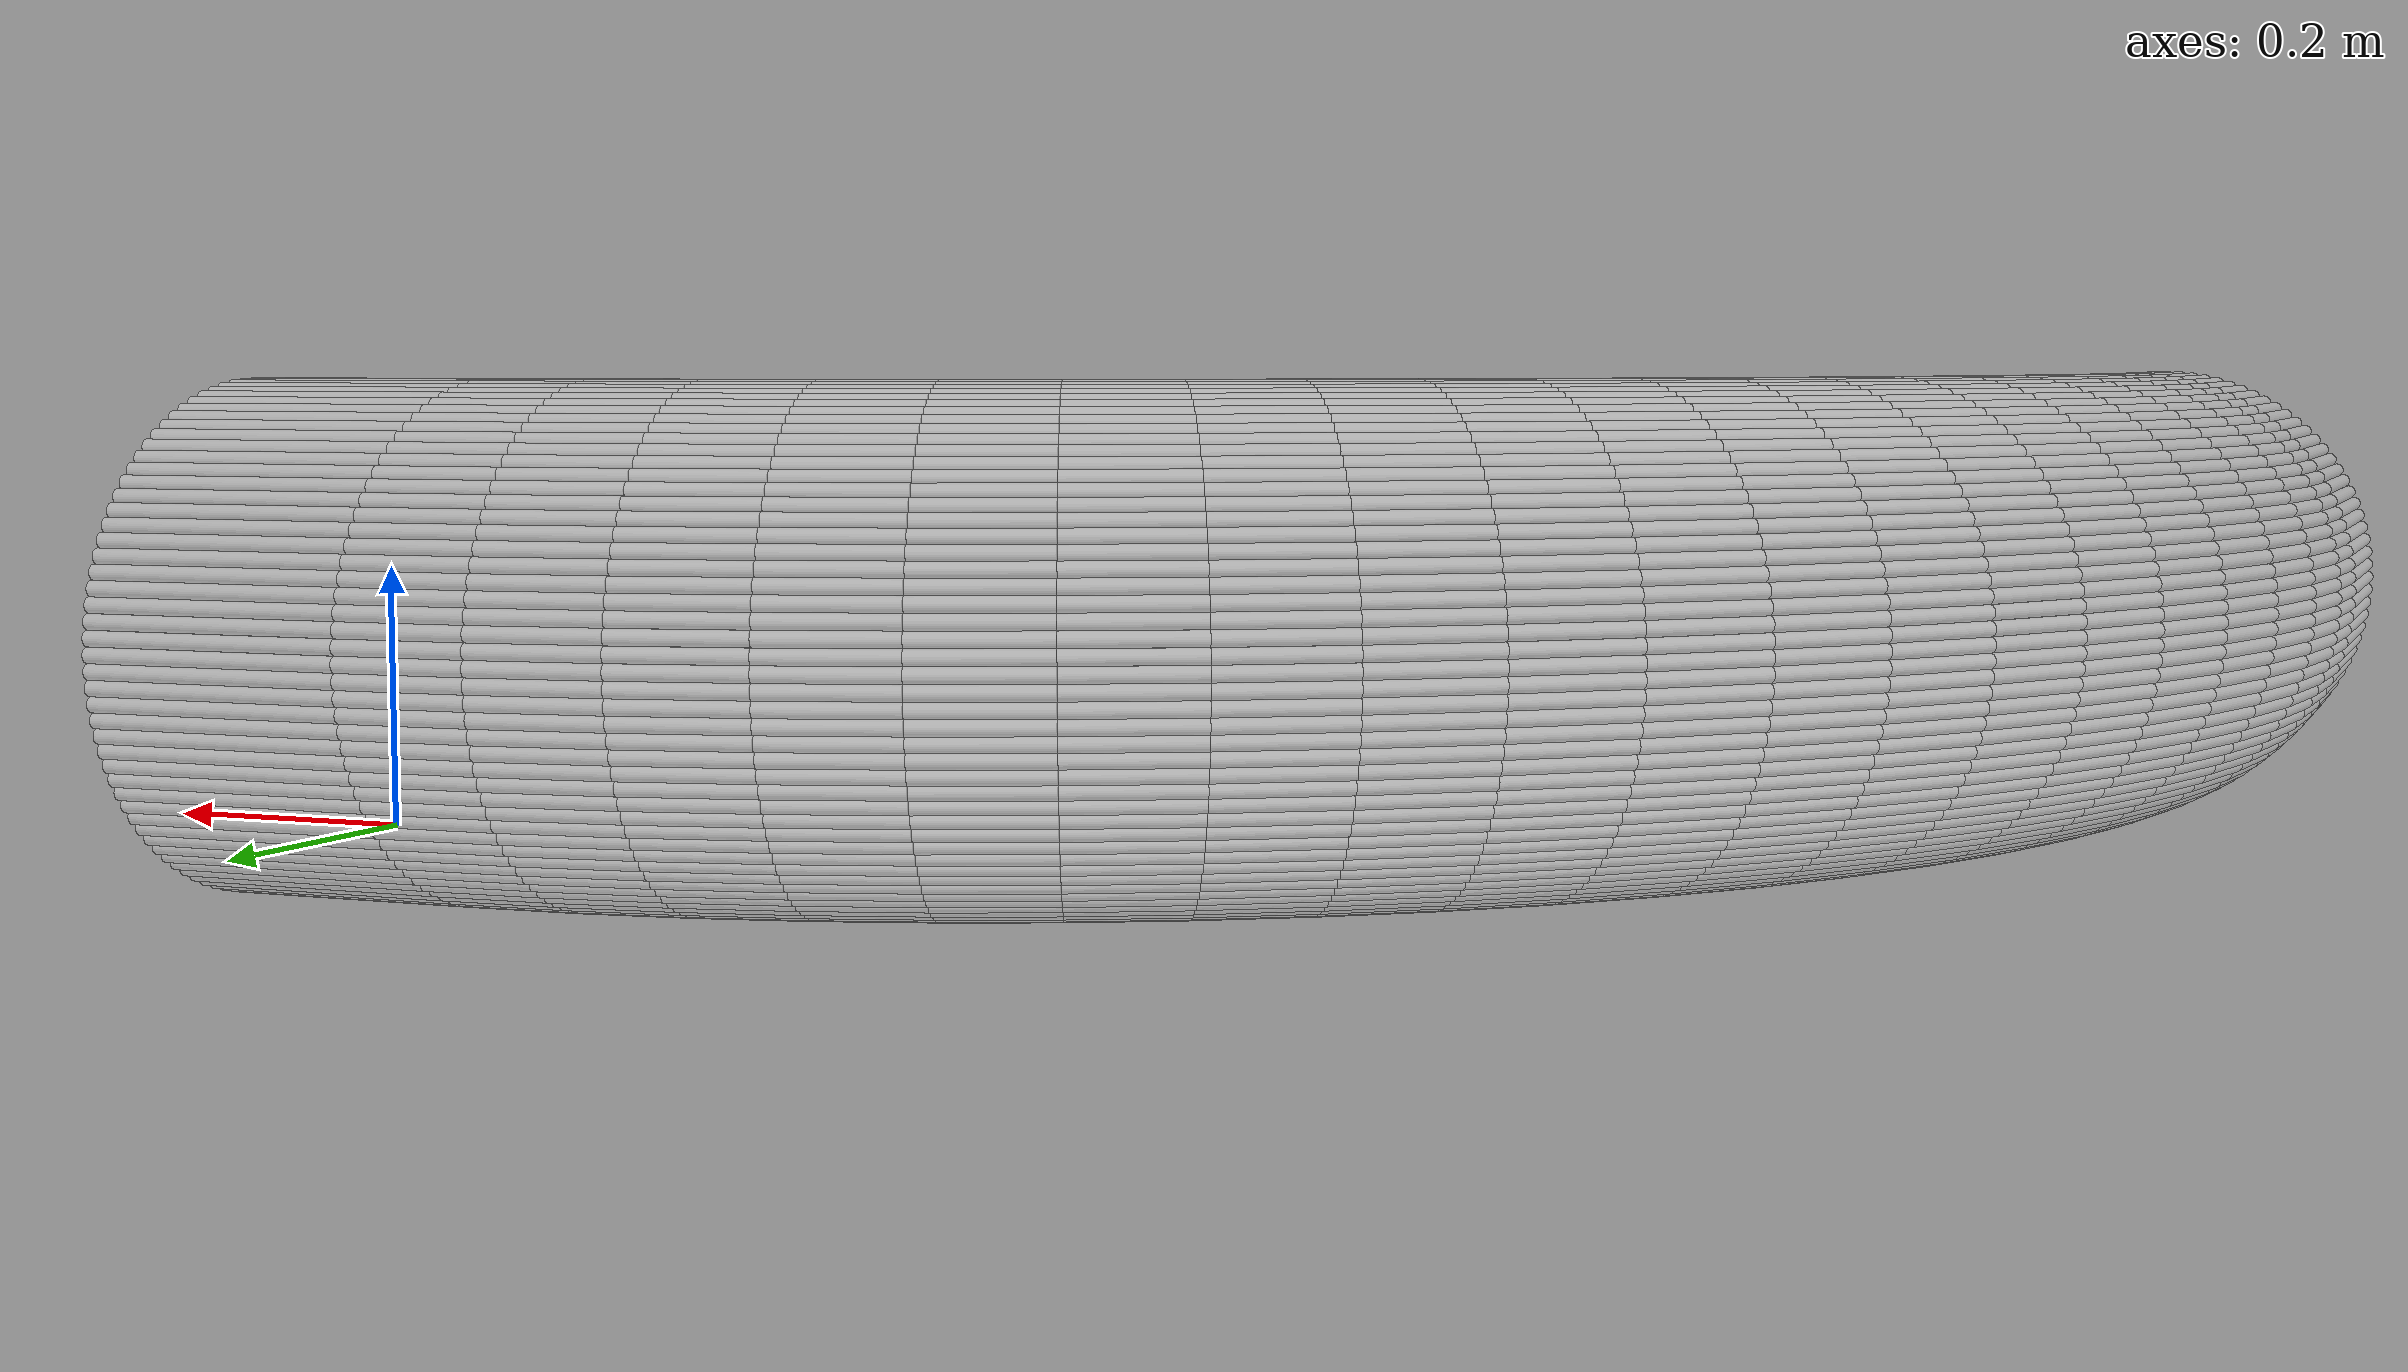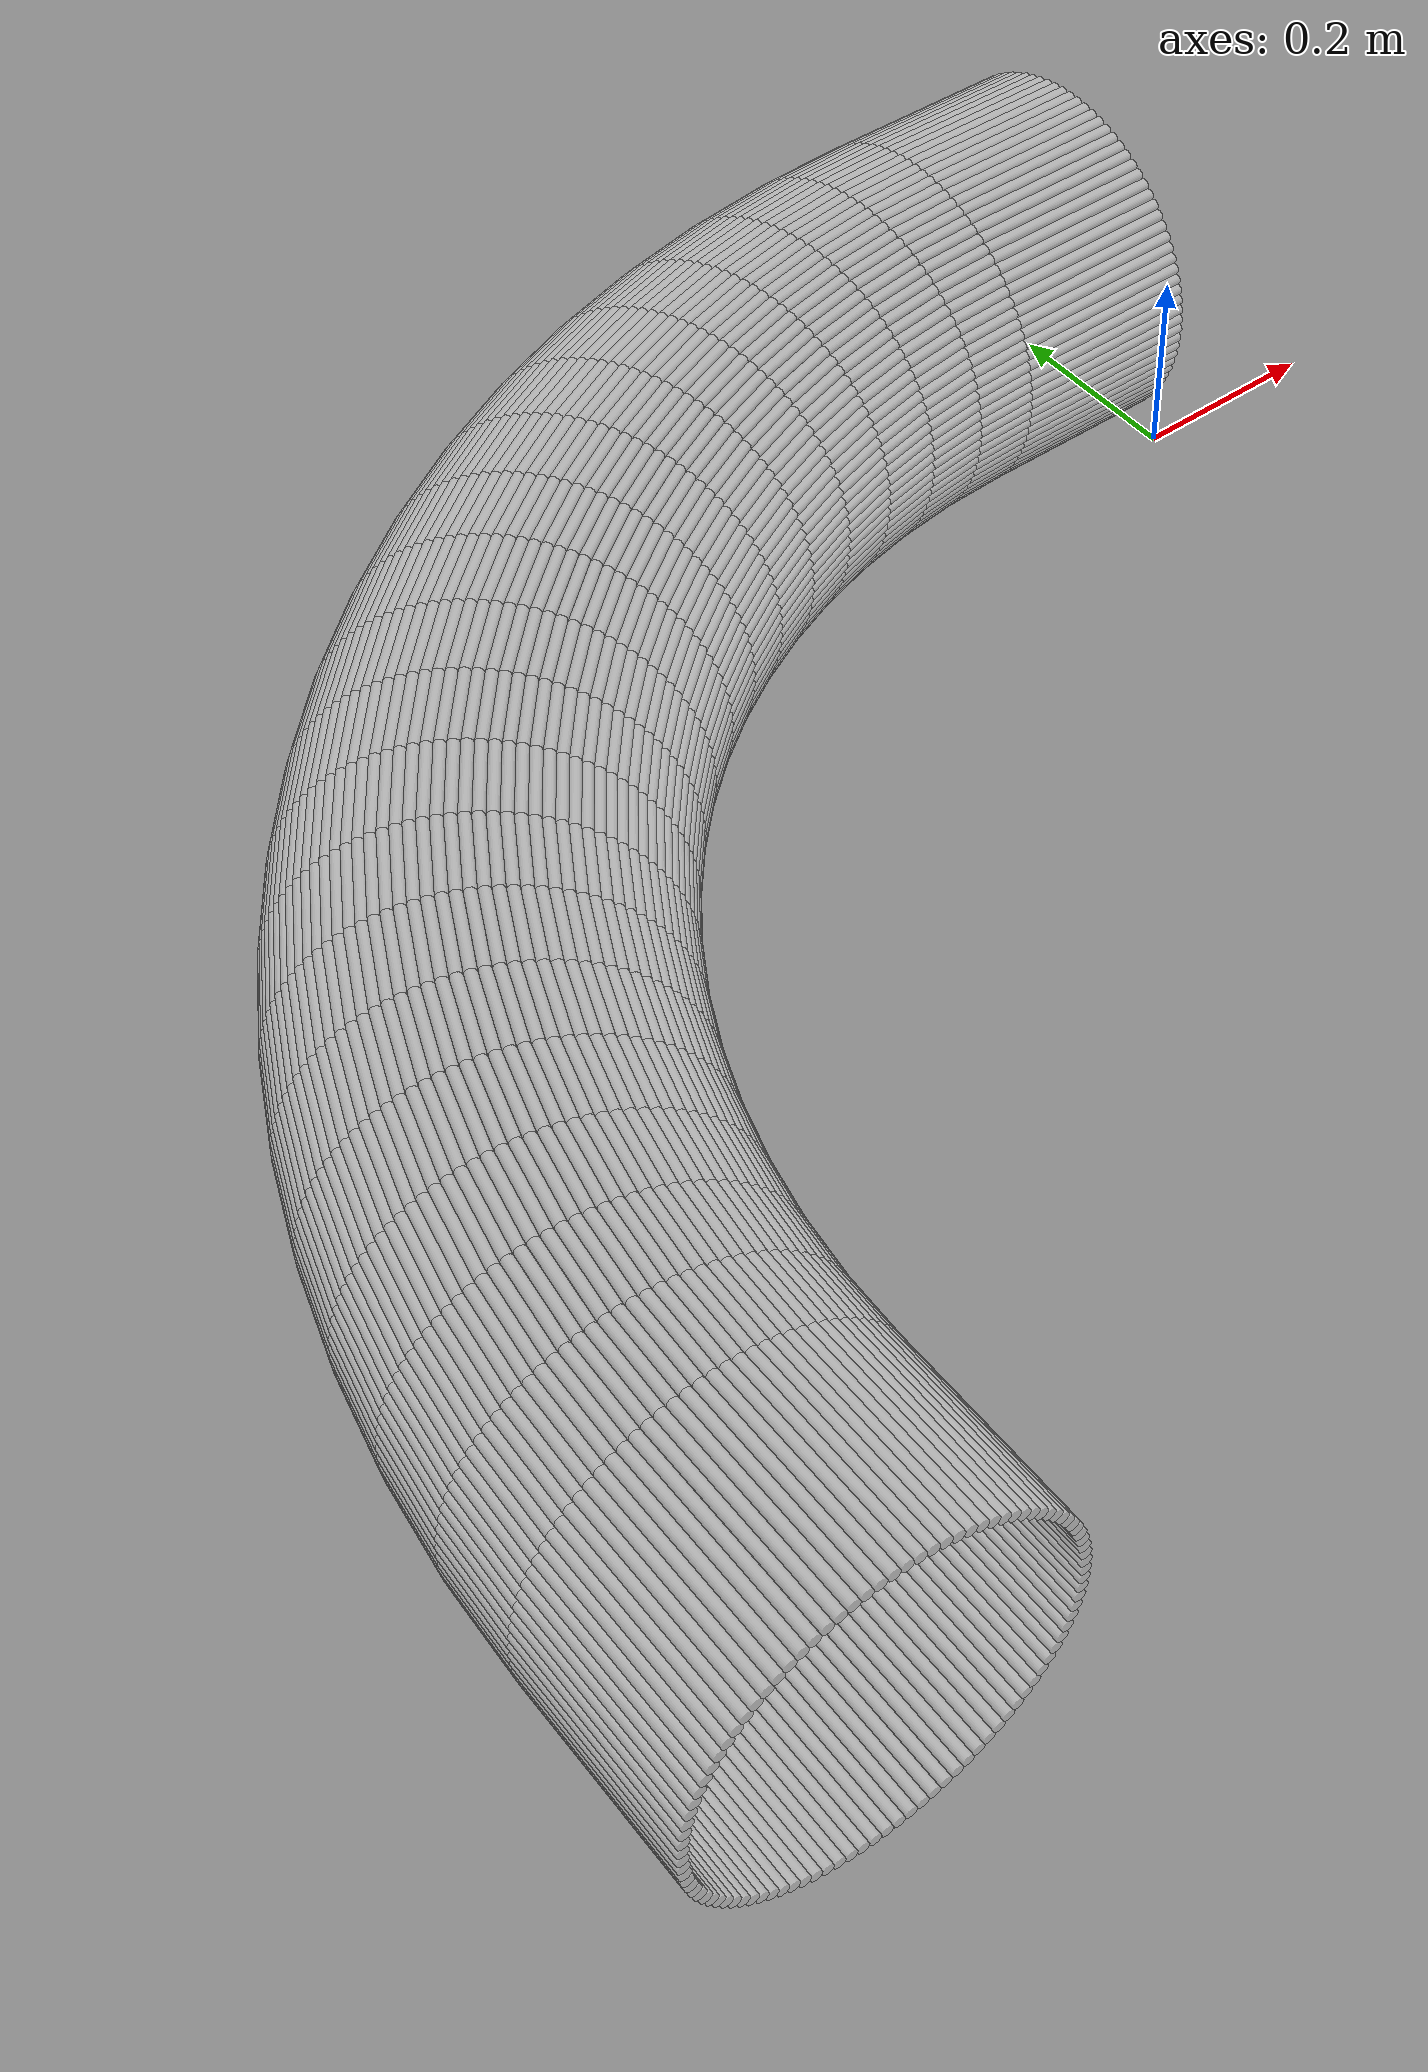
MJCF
<?xml version="1.0" encoding="utf-8"?>
<mujoco>
   <worldbody>
   <body pos="-0.2 -0.84 -0.02" euler="0 0 90">
      <geom euler=" 0 10 0 " fromto="1.18 -0.2 0.18 1.18 0 0.18" rgba="1 1 1 0.35"
            size="0.0056539"
            type="cylinder"/>
      <geom euler=" 0 20 0 " fromto="1.1796 -0.2 0.1913 1.1796 0 0.1913" rgba="1 1 1 0.35"
            size="0.0056539"
            type="cylinder"/>
      <geom euler=" 0 30 0 " fromto="1.1786 -0.2 0.20256 1.1786 0 0.20256"
            rgba="1 1 1 0.35"
            size="0.0056539"
            type="cylinder"/>
      <geom euler=" 0 40 0 " fromto="1.1768 -0.2 0.21373 1.1768 0 0.21373"
            rgba="1 1 1 0.35"
            size="0.0056539"
            type="cylinder"/>
      <geom euler=" 0 50 0 " fromto="1.1743 -0.2 0.22476 1.1743 0 0.22476"
            rgba="1 1 1 0.35"
            size="0.0056539"
            type="cylinder"/>
      <geom euler=" 0 60 0 " fromto="1.1712 -0.2 0.23562 1.1712 0 0.23562"
            rgba="1 1 1 0.35"
            size="0.0056539"
            type="cylinder"/>
      <geom euler=" 0 70 0 " fromto="1.1674 -0.2 0.24626 1.1674 0 0.24626"
            rgba="1 1 1 0.35"
            size="0.0056539"
            type="cylinder"/>
      <geom euler=" 0 80 0 " fromto="1.1629 -0.2 0.25664 1.1629 0 0.25664"
            rgba="1 1 1 0.35"
            size="0.0056539"
            type="cylinder"/>
      <geom euler=" 0 90 0 " fromto="1.1577 -0.2 0.26672 1.1577 0 0.26672"
            rgba="1 1 1 0.35"
            size="0.0056539"
            type="cylinder"/>
      <geom euler=" 0 100 0 " fromto="1.152 -0.2 0.27645 1.152 0 0.27645" rgba="1 1 1 0.35"
            size="0.0056539"
            type="cylinder"/>
      <geom euler=" 0 110 0 " fromto="1.1456 -0.2 0.2858 1.1456 0 0.2858" rgba="1 1 1 0.35"
            size="0.0056539"
            type="cylinder"/>
      <geom euler=" 0 120 0 " fromto="1.1387 -0.2 0.29474 1.1387 0 0.29474"
            rgba="1 1 1 0.35"
            size="0.0056539"
            type="cylinder"/>
      <geom euler=" 0 130 0 " fromto="1.1312 -0.2 0.30322 1.1312 0 0.30322"
            rgba="1 1 1 0.35"
            size="0.0056539"
            type="cylinder"/>
      <geom euler=" 0 140 0 " fromto="1.1232 -0.2 0.31121 1.1232 0 0.31121"
            rgba="1 1 1 0.35"
            size="0.0056539"
            type="cylinder"/>
      <geom euler=" 0 150 0 " fromto="1.1147 -0.2 0.31869 1.1147 0 0.31869"
            rgba="1 1 1 0.35"
            size="0.0056539"
            type="cylinder"/>
      <geom euler=" 0 160 0 " fromto="1.1058 -0.2 0.32562 1.1058 0 0.32562"
            rgba="1 1 1 0.35"
            size="0.0056539"
            type="cylinder"/>
      <geom euler=" 0 170 0 " fromto="1.0964 -0.2 0.33198 1.0964 0 0.33198"
            rgba="1 1 1 0.35"
            size="0.0056539"
            type="cylinder"/>
      <geom euler=" 0 180 0 " fromto="1.0867 -0.2 0.33774 1.0867 0 0.33774"
            rgba="1 1 1 0.35"
            size="0.0056539"
            type="cylinder"/>
      <geom euler=" 0 190 0 " fromto="1.0766 -0.2 0.34287 1.0766 0 0.34287"
            rgba="1 1 1 0.35"
            size="0.0056539"
            type="cylinder"/>
      <geom euler=" 0 200 0 " fromto="1.0663 -0.2 0.34736 1.0663 0 0.34736"
            rgba="1 1 1 0.35"
            size="0.0056539"
            type="cylinder"/>
      <geom euler=" 0 210 0 " fromto="1.0556 -0.2 0.35119 1.0556 0 0.35119"
            rgba="1 1 1 0.35"
            size="0.0056539"
            type="cylinder"/>
      <geom euler=" 0 220 0 " fromto="1.0448 -0.2 0.35434 1.0448 0 0.35434"
            rgba="1 1 1 0.35"
            size="0.0056539"
            type="cylinder"/>
      <geom euler=" 0 230 0 " fromto="1.0337 -0.2 0.35681 1.0337 0 0.35681"
            rgba="1 1 1 0.35"
            size="0.0056539"
            type="cylinder"/>
      <geom euler=" 0 240 0 " fromto="1.0226 -0.2 0.35858 1.0226 0 0.35858"
            rgba="1 1 1 0.35"
            size="0.0056539"
            type="cylinder"/>
      <geom euler=" 0 250 0 " fromto="1.0113 -0.2 0.35964 1.0113 0 0.35964"
            rgba="1 1 1 0.35"
            size="0.0056539"
            type="cylinder"/>
      <geom euler=" 0 260 0 " fromto="1 -0.2 0.36 1 0 0.36" rgba="1 1 1 0.35"
            size="0.0056539"
            type="cylinder"/>
      <geom euler=" 0 270 0 " fromto="0.9887 -0.2 0.35964 0.9887 0 0.35964"
            rgba="1 1 1 0.35"
            size="0.0056539"
            type="cylinder"/>
      <geom euler=" 0 280 0 " fromto="0.97744 -0.2 0.35858 0.97744 0 0.35858"
            rgba="1 1 1 0.35"
            size="0.0056539"
            type="cylinder"/>
      <geom euler=" 0 290 0 " fromto="0.96627 -0.2 0.35681 0.96627 0 0.35681"
            rgba="1 1 1 0.35"
            size="0.0056539"
            type="cylinder"/>
      <geom euler=" 0 300 0 " fromto="0.95524 -0.2 0.35434 0.95524 0 0.35434"
            rgba="1 1 1 0.35"
            size="0.0056539"
            type="cylinder"/>
      <geom euler=" 0 310 0 " fromto="0.94438 -0.2 0.35119 0.94438 0 0.35119"
            rgba="1 1 1 0.35"
            size="0.0056539"
            type="cylinder"/>
      <geom euler=" 0 320 0 " fromto="0.93374 -0.2 0.34736 0.93374 0 0.34736"
            rgba="1 1 1 0.35"
            size="0.0056539"
            type="cylinder"/>
      <geom euler=" 0 330 0 " fromto="0.92336 -0.2 0.34287 0.92336 0 0.34287"
            rgba="1 1 1 0.35"
            size="0.0056539"
            type="cylinder"/>
      <geom euler=" 0 340 0 " fromto="0.91328 -0.2 0.33774 0.91328 0 0.33774"
            rgba="1 1 1 0.35"
            size="0.0056539"
            type="cylinder"/>
      <geom euler=" 0 350 0 " fromto="0.90355 -0.2 0.33198 0.90355 0 0.33198"
            rgba="1 1 1 0.35"
            size="0.0056539"
            type="cylinder"/>
      <geom euler=" 0 360 0 " fromto="0.8942 -0.2 0.32562 0.8942 0 0.32562"
            rgba="1 1 1 0.35"
            size="0.0056539"
            type="cylinder"/>
      <geom euler=" 0 370 0 " fromto="0.88526 -0.2 0.31869 0.88526 0 0.31869"
            rgba="1 1 1 0.35"
            size="0.0056539"
            type="cylinder"/>
      <geom euler=" 0 380 0 " fromto="0.87678 -0.2 0.31121 0.87678 0 0.31121"
            rgba="1 1 1 0.35"
            size="0.0056539"
            type="cylinder"/>
      <geom euler=" 0 390 0 " fromto="0.86879 -0.2 0.30322 0.86879 0 0.30322"
            rgba="1 1 1 0.35"
            size="0.0056539"
            type="cylinder"/>
      <geom euler=" 0 400 0 " fromto="0.86131 -0.2 0.29474 0.86131 0 0.29474"
            rgba="1 1 1 0.35"
            size="0.0056539"
            type="cylinder"/>
      <geom euler=" 0 410 0 " fromto="0.85438 -0.2 0.2858 0.85438 0 0.2858"
            rgba="1 1 1 0.35"
            size="0.0056539"
            type="cylinder"/>
      <geom euler=" 0 420 0 " fromto="0.84802 -0.2 0.27645 0.84802 0 0.27645"
            rgba="1 1 1 0.35"
            size="0.0056539"
            type="cylinder"/>
      <geom euler=" 0 430 0 " fromto="0.84226 -0.2 0.26672 0.84226 0 0.26672"
            rgba="1 1 1 0.35"
            size="0.0056539"
            type="cylinder"/>
      <geom euler=" 0 440 0 " fromto="0.83713 -0.2 0.25664 0.83713 0 0.25664"
            rgba="1 1 1 0.35"
            size="0.0056539"
            type="cylinder"/>
      <geom euler=" 0 450 0 " fromto="0.83264 -0.2 0.24626 0.83264 0 0.24626"
            rgba="1 1 1 0.35"
            size="0.0056539"
            type="cylinder"/>
      <geom euler=" 0 460 0 " fromto="0.82881 -0.2 0.23562 0.82881 0 0.23562"
            rgba="1 1 1 0.35"
            size="0.0056539"
            type="cylinder"/>
      <geom euler=" 0 470 0 " fromto="0.82566 -0.2 0.22476 0.82566 0 0.22476"
            rgba="1 1 1 0.35"
            size="0.0056539"
            type="cylinder"/>
      <geom euler=" 0 480 0 " fromto="0.82319 -0.2 0.21373 0.82319 0 0.21373"
            rgba="1 1 1 0.35"
            size="0.0056539"
            type="cylinder"/>
      <geom euler=" 0 490 0 " fromto="0.82142 -0.2 0.20256 0.82142 0 0.20256"
            rgba="1 1 1 0.35"
            size="0.0056539"
            type="cylinder"/>
      <geom euler=" 0 500 0 " fromto="0.82036 -0.2 0.1913 0.82036 0 0.1913"
            rgba="1 1 1 0.35"
            size="0.0056539"
            type="cylinder"/>
      <geom euler=" 0 510 0 " fromto="0.82 -0.2 0.18 0.82 0 0.18" rgba="1 1 1 0.35"
            size="0.0056539"
            type="cylinder"/>
      <geom euler=" 0 520 0 " fromto="0.82036 -0.2 0.1687 0.82036 0 0.1687"
            rgba="1 1 1 0.35"
            size="0.0056539"
            type="cylinder"/>
      <geom euler=" 0 530 0 " fromto="0.82142 -0.2 0.15744 0.82142 0 0.15744"
            rgba="1 1 1 0.35"
            size="0.0056539"
            type="cylinder"/>
      <geom euler=" 0 540 0 " fromto="0.82319 -0.2 0.14627 0.82319 0 0.14627"
            rgba="1 1 1 0.35"
            size="0.0056539"
            type="cylinder"/>
      <geom euler=" 0 550 0 " fromto="0.82566 -0.2 0.13524 0.82566 0 0.13524"
            rgba="1 1 1 0.35"
            size="0.0056539"
            type="cylinder"/>
      <geom euler=" 0 560 0 " fromto="0.82881 -0.2 0.12438 0.82881 0 0.12438"
            rgba="1 1 1 0.35"
            size="0.0056539"
            type="cylinder"/>
      <geom euler=" 0 570 0 " fromto="0.83264 -0.2 0.11374 0.83264 0 0.11374"
            rgba="1 1 1 0.35"
            size="0.0056539"
            type="cylinder"/>
      <geom euler=" 0 580 0 " fromto="0.83713 -0.2 0.10336 0.83713 0 0.10336"
            rgba="1 1 1 0.35"
            size="0.0056539"
            type="cylinder"/>
      <geom euler=" 0 590 0 " fromto="0.84226 -0.2 0.093284 0.84226 0 0.093284"
            rgba="1 1 1 0.35"
            size="0.0056539"
            type="cylinder"/>
      <geom euler=" 0 600 0 " fromto="0.84802 -0.2 0.083551 0.84802 0 0.083551"
            rgba="1 1 1 0.35"
            size="0.0056539"
            type="cylinder"/>
      <geom euler=" 0 610 0 " fromto="0.85438 -0.2 0.074199 0.85438 0 0.074199"
            rgba="1 1 1 0.35"
            size="0.0056539"
            type="cylinder"/>
      <geom euler=" 0 620 0 " fromto="0.86131 -0.2 0.065264 0.86131 0 0.065264"
            rgba="1 1 1 0.35"
            size="0.0056539"
            type="cylinder"/>
      <geom euler=" 0 630 0 " fromto="0.86879 -0.2 0.056782 0.86879 0 0.056782"
            rgba="1 1 1 0.35"
            size="0.0056539"
            type="cylinder"/>
      <geom euler=" 0 640 0 " fromto="0.87678 -0.2 0.048786 0.87678 0 0.048786"
            rgba="1 1 1 0.35"
            size="0.0056539"
            type="cylinder"/>
      <geom euler=" 0 650 0 " fromto="0.88526 -0.2 0.041308 0.88526 0 0.041308"
            rgba="1 1 1 0.35"
            size="0.0056539"
            type="cylinder"/>
      <geom euler=" 0 660 0 " fromto="0.8942 -0.2 0.034377 0.8942 0 0.034377"
            rgba="1 1 1 0.35"
            size="0.0056539"
            type="cylinder"/>
      <geom euler=" 0 670 0 " fromto="0.90355 -0.2 0.028021 0.90355 0 0.028021"
            rgba="1 1 1 0.35"
            size="0.0056539"
            type="cylinder"/>
      <geom euler=" 0 680 0 " fromto="0.91328 -0.2 0.022265 0.91328 0 0.022265"
            rgba="1 1 1 0.35"
            size="0.0056539"
            type="cylinder"/>
      <geom euler=" 0 690 0 " fromto="0.92336 -0.2 0.017131 0.92336 0 0.017131"
            rgba="1 1 1 0.35"
            size="0.0056539"
            type="cylinder"/>
      <geom euler=" 0 700 0 " fromto="0.93374 -0.2 0.01264 0.93374 0 0.01264"
            rgba="1 1 1 0.35"
            size="0.0056539"
            type="cylinder"/>
      <geom euler=" 0 710 0 " fromto="0.94438 -0.2 0.0088098 0.94438 0 0.0088098"
            rgba="1 1 1 0.35"
            size="0.0056539"
            type="cylinder"/>
      <geom euler=" 0 720 0 " fromto="0.95524 -0.2 0.005655 0.95524 0 0.005655"
            rgba="1 1 1 0.35"
            size="0.0056539"
            type="cylinder"/>
      <geom euler=" 0 730 0 " fromto="0.96627 -0.2 0.0031883 0.96627 0 0.0031883"
            rgba="1 1 1 0.35"
            size="0.0056539"
            type="cylinder"/>
      <geom euler=" 0 740 0 " fromto="0.97744 -0.2 0.0014194 0.97744 0 0.0014194"
            rgba="1 1 1 0.35"
            size="0.0056539"
            type="cylinder"/>
      <geom euler=" 0 750 0 " fromto="0.9887 -0.2 0.00035519 0.9887 0 0.00035519"
            rgba="1 1 1 0.35"
            size="0.0056539"
            type="cylinder"/>
      <geom euler=" 0 760 0 " fromto="1 -0.2 0 1 0 0" rgba="1 1 1 0.35" size="0.0056539"
            type="cylinder"/>
      <geom euler=" 0 770 0 " fromto="1.0113 -0.2 0.00035519 1.0113 0 0.00035519"
            rgba="1 1 1 0.35"
            size="0.0056539"
            type="cylinder"/>
      <geom euler=" 0 780 0 " fromto="1.0226 -0.2 0.0014194 1.0226 0 0.0014194"
            rgba="1 1 1 0.35"
            size="0.0056539"
            type="cylinder"/>
      <geom euler=" 0 790 0 " fromto="1.0337 -0.2 0.0031883 1.0337 0 0.0031883"
            rgba="1 1 1 0.35"
            size="0.0056539"
            type="cylinder"/>
      <geom euler=" 0 800 0 " fromto="1.0448 -0.2 0.005655 1.0448 0 0.005655"
            rgba="1 1 1 0.35"
            size="0.0056539"
            type="cylinder"/>
      <geom euler=" 0 810 0 " fromto="1.0556 -0.2 0.0088098 1.0556 0 0.0088098"
            rgba="1 1 1 0.35"
            size="0.0056539"
            type="cylinder"/>
      <geom euler=" 0 820 0 " fromto="1.0663 -0.2 0.01264 1.0663 0 0.01264"
            rgba="1 1 1 0.35"
            size="0.0056539"
            type="cylinder"/>
      <geom euler=" 0 830 0 " fromto="1.0766 -0.2 0.017131 1.0766 0 0.017131"
            rgba="1 1 1 0.35"
            size="0.0056539"
            type="cylinder"/>
      <geom euler=" 0 840 0 " fromto="1.0867 -0.2 0.022265 1.0867 0 0.022265"
            rgba="1 1 1 0.35"
            size="0.0056539"
            type="cylinder"/>
      <geom euler=" 0 850 0 " fromto="1.0964 -0.2 0.028021 1.0964 0 0.028021"
            rgba="1 1 1 0.35"
            size="0.0056539"
            type="cylinder"/>
      <geom euler=" 0 860 0 " fromto="1.1058 -0.2 0.034377 1.1058 0 0.034377"
            rgba="1 1 1 0.35"
            size="0.0056539"
            type="cylinder"/>
      <geom euler=" 0 870 0 " fromto="1.1147 -0.2 0.041308 1.1147 0 0.041308"
            rgba="1 1 1 0.35"
            size="0.0056539"
            type="cylinder"/>
      <geom euler=" 0 880 0 " fromto="1.1232 -0.2 0.048786 1.1232 0 0.048786"
            rgba="1 1 1 0.35"
            size="0.0056539"
            type="cylinder"/>
      <geom euler=" 0 890 0 " fromto="1.1312 -0.2 0.056782 1.1312 0 0.056782"
            rgba="1 1 1 0.35"
            size="0.0056539"
            type="cylinder"/>
      <geom euler=" 0 900 0 " fromto="1.1387 -0.2 0.065264 1.1387 0 0.065264"
            rgba="1 1 1 0.35"
            size="0.0056539"
            type="cylinder"/>
      <geom euler=" 0 910 0 " fromto="1.1456 -0.2 0.074199 1.1456 0 0.074199"
            rgba="1 1 1 0.35"
            size="0.0056539"
            type="cylinder"/>
      <geom euler=" 0 920 0 " fromto="1.152 -0.2 0.083551 1.152 0 0.083551"
            rgba="1 1 1 0.35"
            size="0.0056539"
            type="cylinder"/>
      <geom euler=" 0 930 0 " fromto="1.1577 -0.2 0.093284 1.1577 0 0.093284"
            rgba="1 1 1 0.35"
            size="0.0056539"
            type="cylinder"/>
      <geom euler=" 0 940 0 " fromto="1.1629 -0.2 0.10336 1.1629 0 0.10336"
            rgba="1 1 1 0.35"
            size="0.0056539"
            type="cylinder"/>
      <geom euler=" 0 950 0 " fromto="1.1674 -0.2 0.11374 1.1674 0 0.11374"
            rgba="1 1 1 0.35"
            size="0.0056539"
            type="cylinder"/>
      <geom euler=" 0 960 0 " fromto="1.1712 -0.2 0.12438 1.1712 0 0.12438"
            rgba="1 1 1 0.35"
            size="0.0056539"
            type="cylinder"/>
      <geom euler=" 0 970 0 " fromto="1.1743 -0.2 0.13524 1.1743 0 0.13524"
            rgba="1 1 1 0.35"
            size="0.0056539"
            type="cylinder"/>
      <geom euler=" 0 980 0 " fromto="1.1768 -0.2 0.14627 1.1768 0 0.14627"
            rgba="1 1 1 0.35"
            size="0.0056539"
            type="cylinder"/>
      <geom euler=" 0 990 0 " fromto="1.1786 -0.2 0.15744 1.1786 0 0.15744"
            rgba="1 1 1 0.35"
            size="0.0056539"
            type="cylinder"/>
      <geom euler=" 0 1000 0 " fromto="1.1796 -0.2 0.1687 1.1796 0 0.1687"
            rgba="1 1 1 0.35"
            size="0.0056539"
            type="cylinder"/>
      <geom euler=" 0 10 0 " fromto="1.18 0 0.18 1.176 0.097444 0.18" rgba="1 1 1 0.35"
            size="0.0056539"
            type="cylinder"/>
      <geom euler=" 0 20 0 " fromto="1.1796 0 0.1913 1.1756 0.097414 0.1913"
            rgba="1 1 1 0.35"
            size="0.0056539"
            type="cylinder"/>
      <geom euler=" 0 30 0 " fromto="1.1786 0 0.20256 1.1746 0.097326 0.20256"
            rgba="1 1 1 0.35"
            size="0.0056539"
            type="cylinder"/>
      <geom euler=" 0 40 0 " fromto="1.1768 0 0.21373 1.1728 0.09718 0.21373"
            rgba="1 1 1 0.35"
            size="0.0056539"
            type="cylinder"/>
      <geom euler=" 0 50 0 " fromto="1.1743 0 0.22476 1.1703 0.096977 0.22476"
            rgba="1 1 1 0.35"
            size="0.0056539"
            type="cylinder"/>
      <geom euler=" 0 60 0 " fromto="1.1712 0 0.23562 1.1672 0.096716 0.23562"
            rgba="1 1 1 0.35"
            size="0.0056539"
            type="cylinder"/>
      <geom euler=" 0 70 0 " fromto="1.1674 0 0.24626 1.1634 0.0964 0.24626"
            rgba="1 1 1 0.35"
            size="0.0056539"
            type="cylinder"/>
      <geom euler=" 0 80 0 " fromto="1.1629 0 0.25664 1.1589 0.096029 0.25664"
            rgba="1 1 1 0.35"
            size="0.0056539"
            type="cylinder"/>
      <geom euler=" 0 90 0 " fromto="1.1577 0 0.26672 1.1538 0.095605 0.26672"
            rgba="1 1 1 0.35"
            size="0.0056539"
            type="cylinder"/>
      <geom euler=" 0 100 0 " fromto="1.152 0 0.27645 1.148 0.09513 0.27645"
            rgba="1 1 1 0.35"
            size="0.0056539"
            type="cylinder"/>
      <geom euler=" 0 110 0 " fromto="1.1456 0 0.2858 1.1417 0.094605 0.2858"
            rgba="1 1 1 0.35"
            size="0.0056539"
            type="cylinder"/>
      <geom euler=" 0 120 0 " fromto="1.1387 0 0.29474 1.1348 0.094032 0.29474"
            rgba="1 1 1 0.35"
            size="0.0056539"
            type="cylinder"/>
      <geom euler=" 0 130 0 " fromto="1.1312 0 0.30322 1.1274 0.093415 0.30322"
            rgba="1 1 1 0.35"
            size="0.0056539"
            type="cylinder"/>
      <geom euler=" 0 140 0 " fromto="1.1232 0 0.31121 1.1194 0.092755 0.31121"
            rgba="1 1 1 0.35"
            size="0.0056539"
            type="cylinder"/>
      <geom euler=" 0 150 0 " fromto="1.1147 0 0.31869 1.1109 0.092054 0.31869"
            rgba="1 1 1 0.35"
            size="0.0056539"
            type="cylinder"/>
      <geom euler=" 0 160 0 " fromto="1.1058 0 0.32562 1.102 0.091316 0.32562"
            rgba="1 1 1 0.35"
            size="0.0056539"
            type="cylinder"/>
      <geom euler=" 0 170 0 " fromto="1.0964 0 0.33198 1.0927 0.090544 0.33198"
            rgba="1 1 1 0.35"
            size="0.0056539"
            type="cylinder"/>
      <geom euler=" 0 180 0 " fromto="1.0867 0 0.33774 1.083 0.08974 0.33774"
            rgba="1 1 1 0.35"
            size="0.0056539"
            type="cylinder"/>
      <geom euler=" 0 190 0 " fromto="1.0766 0 0.34287 1.073 0.088908 0.34287"
            rgba="1 1 1 0.35"
            size="0.0056539"
            type="cylinder"/>
      <geom euler=" 0 200 0 " fromto="1.0663 0 0.34736 1.0626 0.088051 0.34736"
            rgba="1 1 1 0.35"
            size="0.0056539"
            type="cylinder"/>
      <geom euler=" 0 210 0 " fromto="1.0556 0 0.35119 1.052 0.087173 0.35119"
            rgba="1 1 1 0.35"
            size="0.0056539"
            type="cylinder"/>
      <geom euler=" 0 220 0 " fromto="1.0448 0 0.35434 1.0412 0.086276 0.35434"
            rgba="1 1 1 0.35"
            size="0.0056539"
            type="cylinder"/>
      <geom euler=" 0 230 0 " fromto="1.0337 0 0.35681 1.0302 0.085365 0.35681"
            rgba="1 1 1 0.35"
            size="0.0056539"
            type="cylinder"/>
      <geom euler=" 0 240 0 " fromto="1.0226 0 0.35858 1.0191 0.084442 0.35858"
            rgba="1 1 1 0.35"
            size="0.0056539"
            type="cylinder"/>
      <geom euler=" 0 250 0 " fromto="1.0113 0 0.35964 1.0078 0.083513 0.35964"
            rgba="1 1 1 0.35"
            size="0.0056539"
            type="cylinder"/>
      <geom euler=" 0 260 0 " fromto="1 0 0.36 0.99658 0.082579 0.36" rgba="1 1 1 0.35"
            size="0.0056539"
            type="cylinder"/>
      <geom euler=" 0 270 0 " fromto="0.9887 0 0.35964 0.98532 0.081646 0.35964"
            rgba="1 1 1 0.35"
            size="0.0056539"
            type="cylinder"/>
      <geom euler=" 0 280 0 " fromto="0.97744 0 0.35858 0.9741 0.080716 0.35858"
            rgba="1 1 1 0.35"
            size="0.0056539"
            type="cylinder"/>
      <geom euler=" 0 290 0 " fromto="0.96627 0 0.35681 0.96297 0.079794 0.35681"
            rgba="1 1 1 0.35"
            size="0.0056539"
            type="cylinder"/>
      <geom euler=" 0 300 0 " fromto="0.95524 0 0.35434 0.95197 0.078883 0.35434"
            rgba="1 1 1 0.35"
            size="0.0056539"
            type="cylinder"/>
      <geom euler=" 0 310 0 " fromto="0.94438 0 0.35119 0.94115 0.077986 0.35119"
            rgba="1 1 1 0.35"
            size="0.0056539"
            type="cylinder"/>
      <geom euler=" 0 320 0 " fromto="0.93374 0 0.34736 0.93055 0.077107 0.34736"
            rgba="1 1 1 0.35"
            size="0.0056539"
            type="cylinder"/>
      <geom euler=" 0 330 0 " fromto="0.92336 0 0.34287 0.92021 0.07625 0.34287"
            rgba="1 1 1 0.35"
            size="0.0056539"
            type="cylinder"/>
      <geom euler=" 0 340 0 " fromto="0.91328 0 0.33774 0.91017 0.075418 0.33774"
            rgba="1 1 1 0.35"
            size="0.0056539"
            type="cylinder"/>
      <geom euler=" 0 350 0 " fromto="0.90355 0 0.33198 0.90047 0.074615 0.33198"
            rgba="1 1 1 0.35"
            size="0.0056539"
            type="cylinder"/>
      <geom euler=" 0 360 0 " fromto="0.8942 0 0.32562 0.89114 0.073842 0.32562"
            rgba="1 1 1 0.35"
            size="0.0056539"
            type="cylinder"/>
      <geom euler=" 0 370 0 " fromto="0.88526 0 0.31869 0.88224 0.073104 0.31869"
            rgba="1 1 1 0.35"
            size="0.0056539"
            type="cylinder"/>
      <geom euler=" 0 380 0 " fromto="0.87678 0 0.31121 0.87379 0.072404 0.31121"
            rgba="1 1 1 0.35"
            size="0.0056539"
            type="cylinder"/>
      <geom euler=" 0 390 0 " fromto="0.86879 0 0.30322 0.86582 0.071744 0.30322"
            rgba="1 1 1 0.35"
            size="0.0056539"
            type="cylinder"/>
      <geom euler=" 0 400 0 " fromto="0.86131 0 0.29474 0.85837 0.071126 0.29474"
            rgba="1 1 1 0.35"
            size="0.0056539"
            type="cylinder"/>
      <geom euler=" 0 410 0 " fromto="0.85438 0 0.2858 0.85146 0.070554 0.2858"
            rgba="1 1 1 0.35"
            size="0.0056539"
            type="cylinder"/>
      <geom euler=" 0 420 0 " fromto="0.84802 0 0.27645 0.84512 0.070029 0.27645"
            rgba="1 1 1 0.35"
            size="0.0056539"
            type="cylinder"/>
      <geom euler=" 0 430 0 " fromto="0.84226 0 0.26672 0.83939 0.069554 0.26672"
            rgba="1 1 1 0.35"
            size="0.0056539"
            type="cylinder"/>
      <geom euler=" 0 440 0 " fromto="0.83713 0 0.25664 0.83427 0.06913 0.25664"
            rgba="1 1 1 0.35"
            size="0.0056539"
            type="cylinder"/>
      <geom euler=" 0 450 0 " fromto="0.83264 0 0.24626 0.8298 0.068759 0.24626"
            rgba="1 1 1 0.35"
            size="0.0056539"
            type="cylinder"/>
      <geom euler=" 0 460 0 " fromto="0.82881 0 0.23562 0.82598 0.068443 0.23562"
            rgba="1 1 1 0.35"
            size="0.0056539"
            type="cylinder"/>
      <geom euler=" 0 470 0 " fromto="0.82566 0 0.22476 0.82284 0.068182 0.22476"
            rgba="1 1 1 0.35"
            size="0.0056539"
            type="cylinder"/>
      <geom euler=" 0 480 0 " fromto="0.82319 0 0.21373 0.82038 0.067978 0.21373"
            rgba="1 1 1 0.35"
            size="0.0056539"
            type="cylinder"/>
      <geom euler=" 0 490 0 " fromto="0.82142 0 0.20256 0.81861 0.067832 0.20256"
            rgba="1 1 1 0.35"
            size="0.0056539"
            type="cylinder"/>
      <geom euler=" 0 500 0 " fromto="0.82036 0 0.1913 0.81755 0.067744 0.1913"
            rgba="1 1 1 0.35"
            size="0.0056539"
            type="cylinder"/>
      <geom euler=" 0 510 0 " fromto="0.82 0 0.18 0.8172 0.067715 0.18" rgba="1 1 1 0.35"
            size="0.0056539"
            type="cylinder"/>
      <geom euler=" 0 520 0 " fromto="0.82036 0 0.1687 0.81755 0.067744 0.1687"
            rgba="1 1 1 0.35"
            size="0.0056539"
            type="cylinder"/>
      <geom euler=" 0 530 0 " fromto="0.82142 0 0.15744 0.81861 0.067832 0.15744"
            rgba="1 1 1 0.35"
            size="0.0056539"
            type="cylinder"/>
      <geom euler=" 0 540 0 " fromto="0.82319 0 0.14627 0.82038 0.067978 0.14627"
            rgba="1 1 1 0.35"
            size="0.0056539"
            type="cylinder"/>
      <geom euler=" 0 550 0 " fromto="0.82566 0 0.13524 0.82284 0.068182 0.13524"
            rgba="1 1 1 0.35"
            size="0.0056539"
            type="cylinder"/>
      <geom euler=" 0 560 0 " fromto="0.82881 0 0.12438 0.82598 0.068443 0.12438"
            rgba="1 1 1 0.35"
            size="0.0056539"
            type="cylinder"/>
      <geom euler=" 0 570 0 " fromto="0.83264 0 0.11374 0.8298 0.068759 0.11374"
            rgba="1 1 1 0.35"
            size="0.0056539"
            type="cylinder"/>
      <geom euler=" 0 580 0 " fromto="0.83713 0 0.10336 0.83427 0.06913 0.10336"
            rgba="1 1 1 0.35"
            size="0.0056539"
            type="cylinder"/>
      <geom euler=" 0 590 0 " fromto="0.84226 0 0.093284 0.83939 0.069554 0.093284"
            rgba="1 1 1 0.35"
            size="0.0056539"
            type="cylinder"/>
      <geom euler=" 0 600 0 " fromto="0.84802 0 0.083551 0.84512 0.070029 0.083551"
            rgba="1 1 1 0.35"
            size="0.0056539"
            type="cylinder"/>
      <geom euler=" 0 610 0 " fromto="0.85438 0 0.074199 0.85146 0.070554 0.074199"
            rgba="1 1 1 0.35"
            size="0.0056539"
            type="cylinder"/>
      <geom euler=" 0 620 0 " fromto="0.86131 0 0.065264 0.85837 0.071126 0.065264"
            rgba="1 1 1 0.35"
            size="0.0056539"
            type="cylinder"/>
      <geom euler=" 0 630 0 " fromto="0.86879 0 0.056782 0.86582 0.071744 0.056782"
            rgba="1 1 1 0.35"
            size="0.0056539"
            type="cylinder"/>
      <geom euler=" 0 640 0 " fromto="0.87678 0 0.048786 0.87379 0.072404 0.048786"
            rgba="1 1 1 0.35"
            size="0.0056539"
            type="cylinder"/>
      <geom euler=" 0 650 0 " fromto="0.88526 0 0.041308 0.88224 0.073104 0.041308"
            rgba="1 1 1 0.35"
            size="0.0056539"
            type="cylinder"/>
      <geom euler=" 0 660 0 " fromto="0.8942 0 0.034377 0.89114 0.073842 0.034377"
            rgba="1 1 1 0.35"
            size="0.0056539"
            type="cylinder"/>
      <geom euler=" 0 670 0 " fromto="0.90355 0 0.028021 0.90047 0.074615 0.028021"
            rgba="1 1 1 0.35"
            size="0.0056539"
            type="cylinder"/>
      <geom euler=" 0 680 0 " fromto="0.91328 0 0.022265 0.91017 0.075418 0.022265"
            rgba="1 1 1 0.35"
            size="0.0056539"
            type="cylinder"/>
      <geom euler=" 0 690 0 " fromto="0.92336 0 0.017131 0.92021 0.07625 0.017131"
            rgba="1 1 1 0.35"
            size="0.0056539"
            type="cylinder"/>
      <geom euler=" 0 700 0 " fromto="0.93374 0 0.01264 0.93055 0.077107 0.01264"
            rgba="1 1 1 0.35"
            size="0.0056539"
            type="cylinder"/>
      <geom euler=" 0 710 0 " fromto="0.94438 0 0.0088098 0.94115 0.077986 0.0088098"
            rgba="1 1 1 0.35"
            size="0.0056539"
            type="cylinder"/>
      <geom euler=" 0 720 0 " fromto="0.95524 0 0.005655 0.95197 0.078883 0.005655"
            rgba="1 1 1 0.35"
            size="0.0056539"
            type="cylinder"/>
      <geom euler=" 0 730 0 " fromto="0.96627 0 0.0031883 0.96297 0.079794 0.0031883"
            rgba="1 1 1 0.35"
            size="0.0056539"
            type="cylinder"/>
      <geom euler=" 0 740 0 " fromto="0.97744 0 0.0014194 0.9741 0.080716 0.0014194"
            rgba="1 1 1 0.35"
            size="0.0056539"
            type="cylinder"/>
      <geom euler=" 0 750 0 " fromto="0.9887 0 0.00035519 0.98532 0.081646 0.00035519"
            rgba="1 1 1 0.35"
            size="0.0056539"
            type="cylinder"/>
      <geom euler=" 0 760 0 " fromto="1 0 0 0.99658 0.082579 0" rgba="1 1 1 0.35"
            size="0.0056539"
            type="cylinder"/>
      <geom euler=" 0 770 0 " fromto="1.0113 0 0.00035519 1.0078 0.083513 0.00035519"
            rgba="1 1 1 0.35"
            size="0.0056539"
            type="cylinder"/>
      <geom euler=" 0 780 0 " fromto="1.0226 0 0.0014194 1.0191 0.084442 0.0014194"
            rgba="1 1 1 0.35"
            size="0.0056539"
            type="cylinder"/>
      <geom euler=" 0 790 0 " fromto="1.0337 0 0.0031883 1.0302 0.085365 0.0031883"
            rgba="1 1 1 0.35"
            size="0.0056539"
            type="cylinder"/>
      <geom euler=" 0 800 0 " fromto="1.0448 0 0.005655 1.0412 0.086276 0.005655"
            rgba="1 1 1 0.35"
            size="0.0056539"
            type="cylinder"/>
      <geom euler=" 0 810 0 " fromto="1.0556 0 0.0088098 1.052 0.087173 0.0088098"
            rgba="1 1 1 0.35"
            size="0.0056539"
            type="cylinder"/>
      <geom euler=" 0 820 0 " fromto="1.0663 0 0.01264 1.0626 0.088051 0.01264"
            rgba="1 1 1 0.35"
            size="0.0056539"
            type="cylinder"/>
      <geom euler=" 0 830 0 " fromto="1.0766 0 0.017131 1.073 0.088908 0.017131"
            rgba="1 1 1 0.35"
            size="0.0056539"
            type="cylinder"/>
      <geom euler=" 0 840 0 " fromto="1.0867 0 0.022265 1.083 0.08974 0.022265"
            rgba="1 1 1 0.35"
            size="0.0056539"
            type="cylinder"/>
      <geom euler=" 0 850 0 " fromto="1.0964 0 0.028021 1.0927 0.090544 0.028021"
            rgba="1 1 1 0.35"
            size="0.0056539"
            type="cylinder"/>
      <geom euler=" 0 860 0 " fromto="1.1058 0 0.034377 1.102 0.091316 0.034377"
            rgba="1 1 1 0.35"
            size="0.0056539"
            type="cylinder"/>
      <geom euler=" 0 870 0 " fromto="1.1147 0 0.041308 1.1109 0.092054 0.041308"
            rgba="1 1 1 0.35"
            size="0.0056539"
            type="cylinder"/>
      <geom euler=" 0 880 0 " fromto="1.1232 0 0.048786 1.1194 0.092755 0.048786"
            rgba="1 1 1 0.35"
            size="0.0056539"
            type="cylinder"/>
      <geom euler=" 0 890 0 " fromto="1.1312 0 0.056782 1.1274 0.093415 0.056782"
            rgba="1 1 1 0.35"
            size="0.0056539"
            type="cylinder"/>
      <geom euler=" 0 900 0 " fromto="1.1387 0 0.065264 1.1348 0.094032 0.065264"
            rgba="1 1 1 0.35"
            size="0.0056539"
            type="cylinder"/>
      <geom euler=" 0 910 0 " fromto="1.1456 0 0.074199 1.1417 0.094605 0.074199"
            rgba="1 1 1 0.35"
            size="0.0056539"
            type="cylinder"/>
      <geom euler=" 0 920 0 " fromto="1.152 0 0.083551 1.148 0.09513 0.083551"
            rgba="1 1 1 0.35"
            size="0.0056539"
            type="cylinder"/>
      <geom euler=" 0 930 0 " fromto="1.1577 0 0.093284 1.1538 0.095605 0.093284"
            rgba="1 1 1 0.35"
            size="0.0056539"
            type="cylinder"/>
      <geom euler=" 0 940 0 " fromto="1.1629 0 0.10336 1.1589 0.096029 0.10336"
            rgba="1 1 1 0.35"
            size="0.0056539"
            type="cylinder"/>
      <geom euler=" 0 950 0 " fromto="1.1674 0 0.11374 1.1634 0.0964 0.11374"
            rgba="1 1 1 0.35"
            size="0.0056539"
            type="cylinder"/>
      <geom euler=" 0 960 0 " fromto="1.1712 0 0.12438 1.1672 0.096716 0.12438"
            rgba="1 1 1 0.35"
            size="0.0056539"
            type="cylinder"/>
      <geom euler=" 0 970 0 " fromto="1.1743 0 0.13524 1.1703 0.096977 0.13524"
            rgba="1 1 1 0.35"
            size="0.0056539"
            type="cylinder"/>
      <geom euler=" 0 980 0 " fromto="1.1768 0 0.14627 1.1728 0.09718 0.14627"
            rgba="1 1 1 0.35"
            size="0.0056539"
            type="cylinder"/>
      <geom euler=" 0 990 0 " fromto="1.1786 0 0.15744 1.1746 0.097326 0.15744"
            rgba="1 1 1 0.35"
            size="0.0056539"
            type="cylinder"/>
      <geom euler=" 0 1000 0 " fromto="1.1796 0 0.1687 1.1756 0.097414 0.1687"
            rgba="1 1 1 0.35"
            size="0.0056539"
            type="cylinder"/>
      <geom euler=" 0 10 0 " fromto="1.176 0.097444 0.18 1.1639 0.19422 0.18"
            rgba="1 1 1 0.35"
            size="0.0056539"
            type="cylinder"/>
      <geom euler=" 0 20 0 " fromto="1.1756 0.097414 0.1913 1.1636 0.19416 0.1913"
            rgba="1 1 1 0.35"
            size="0.0056539"
            type="cylinder"/>
      <geom euler=" 0 30 0 " fromto="1.1746 0.097326 0.20256 1.1625 0.19399 0.20256"
            rgba="1 1 1 0.35"
            size="0.0056539"
            type="cylinder"/>
      <geom euler=" 0 40 0 " fromto="1.1728 0.09718 0.21373 1.1608 0.1937 0.21373"
            rgba="1 1 1 0.35"
            size="0.0056539"
            type="cylinder"/>
      <geom euler=" 0 50 0 " fromto="1.1703 0.096977 0.22476 1.1583 0.19329 0.22476"
            rgba="1 1 1 0.35"
            size="0.0056539"
            type="cylinder"/>
      <geom euler=" 0 60 0 " fromto="1.1672 0.096716 0.23562 1.1552 0.19277 0.23562"
            rgba="1 1 1 0.35"
            size="0.0056539"
            type="cylinder"/>
      <geom euler=" 0 70 0 " fromto="1.1634 0.0964 0.24626 1.1514 0.19214 0.24626"
            rgba="1 1 1 0.35"
            size="0.0056539"
            type="cylinder"/>
      <geom euler=" 0 80 0 " fromto="1.1589 0.096029 0.25664 1.147 0.1914 0.25664"
            rgba="1 1 1 0.35"
            size="0.0056539"
            type="cylinder"/>
      <geom euler=" 0 90 0 " fromto="1.1538 0.095605 0.26672 1.1419 0.19056 0.26672"
            rgba="1 1 1 0.35"
            size="0.0056539"
            type="cylinder"/>
      <geom euler=" 0 100 0 " fromto="1.148 0.09513 0.27645 1.1363 0.18961 0.27645"
            rgba="1 1 1 0.35"
            size="0.0056539"
            type="cylinder"/>
      <geom euler=" 0 110 0 " fromto="1.1417 0.094605 0.2858 1.13 0.18856 0.2858"
            rgba="1 1 1 0.35"
            size="0.0056539"
            type="cylinder"/>
      <geom euler=" 0 120 0 " fromto="1.1348 0.094032 0.29474 1.1232 0.18742 0.29474"
            rgba="1 1 1 0.35"
            size="0.0056539"
            type="cylinder"/>
      <geom euler=" 0 130 0 " fromto="1.1274 0.093415 0.30322 1.1158 0.18619 0.30322"
            rgba="1 1 1 0.35"
            size="0.0056539"
            type="cylinder"/>
      <geom euler=" 0 140 0 " fromto="1.1194 0.092755 0.31121 1.1079 0.18488 0.31121"
            rgba="1 1 1 0.35"
            size="0.0056539"
            type="cylinder"/>
      <geom euler=" 0 150 0 " fromto="1.1109 0.092054 0.31869 1.0995 0.18348 0.31869"
            rgba="1 1 1 0.35"
            size="0.0056539"
            type="cylinder"/>
      <geom euler=" 0 160 0 " fromto="1.102 0.091316 0.32562 1.0907 0.18201 0.32562"
            rgba="1 1 1 0.35"
            size="0.0056539"
            type="cylinder"/>
      <geom euler=" 0 170 0 " fromto="1.0927 0.090544 0.33198 1.0815 0.18047 0.33198"
            rgba="1 1 1 0.35"
            size="0.0056539"
            type="cylinder"/>
      <geom euler=" 0 180 0 " fromto="1.083 0.08974 0.33774 1.0719 0.17887 0.33774"
            rgba="1 1 1 0.35"
            size="0.0056539"
            type="cylinder"/>
      <geom euler=" 0 190 0 " fromto="1.073 0.088908 0.34287 1.062 0.17721 0.34287"
            rgba="1 1 1 0.35"
            size="0.0056539"
            type="cylinder"/>
      <geom euler=" 0 200 0 " fromto="1.0626 0.088051 0.34736 1.0517 0.1755 0.34736"
            rgba="1 1 1 0.35"
            size="0.0056539"
            type="cylinder"/>
      <geom euler=" 0 210 0 " fromto="1.052 0.087173 0.35119 1.0412 0.17375 0.35119"
            rgba="1 1 1 0.35"
            size="0.0056539"
            type="cylinder"/>
      <geom euler=" 0 220 0 " fromto="1.0412 0.086276 0.35434 1.0305 0.17196 0.35434"
            rgba="1 1 1 0.35"
            size="0.0056539"
            type="cylinder"/>
      <geom euler=" 0 230 0 " fromto="1.0302 0.085365 0.35681 1.0196 0.17015 0.35681"
            rgba="1 1 1 0.35"
            size="0.0056539"
            type="cylinder"/>
      <geom euler=" 0 240 0 " fromto="1.0191 0.084442 0.35858 1.0086 0.16831 0.35858"
            rgba="1 1 1 0.35"
            size="0.0056539"
            type="cylinder"/>
      <geom euler=" 0 250 0 " fromto="1.0078 0.083513 0.35964 0.99751 0.16645 0.35964"
            rgba="1 1 1 0.35"
            size="0.0056539"
            type="cylinder"/>
      <geom euler=" 0 260 0 " fromto="0.99658 0.082579 0.36 0.98636 0.16459 0.36"
            rgba="1 1 1 0.35"
            size="0.0056539"
            type="cylinder"/>
      <geom euler=" 0 270 0 " fromto="0.98532 0.081646 0.35964 0.97521 0.16273 0.35964"
            rgba="1 1 1 0.35"
            size="0.0056539"
            type="cylinder"/>
      <geom euler=" 0 280 0 " fromto="0.9741 0.080716 0.35858 0.96411 0.16088 0.35858"
            rgba="1 1 1 0.35"
            size="0.0056539"
            type="cylinder"/>
      <geom euler=" 0 290 0 " fromto="0.96297 0.079794 0.35681 0.95309 0.15904 0.35681"
            rgba="1 1 1 0.35"
            size="0.0056539"
            type="cylinder"/>
      <geom euler=" 0 300 0 " fromto="0.95197 0.078883 0.35434 0.94221 0.15723 0.35434"
            rgba="1 1 1 0.35"
            size="0.0056539"
            type="cylinder"/>
      <geom euler=" 0 310 0 " fromto="0.94115 0.077986 0.35119 0.9315 0.15544 0.35119"
            rgba="1 1 1 0.35"
            size="0.0056539"
            type="cylinder"/>
      <geom euler=" 0 320 0 " fromto="0.93055 0.077107 0.34736 0.921 0.15369 0.34736"
            rgba="1 1 1 0.35"
            size="0.0056539"
            type="cylinder"/>
      <geom euler=" 0 330 0 " fromto="0.92021 0.07625 0.34287 0.91077 0.15198 0.34287"
            rgba="1 1 1 0.35"
            size="0.0056539"
            type="cylinder"/>
      <geom euler=" 0 340 0 " fromto="0.91017 0.075418 0.33774 0.90083 0.15032 0.33774"
            rgba="1 1 1 0.35"
            size="0.0056539"
            type="cylinder"/>
      <geom euler=" 0 350 0 " fromto="0.90047 0.074615 0.33198 0.89123 0.14872 0.33198"
            rgba="1 1 1 0.35"
            size="0.0056539"
            type="cylinder"/>
      <geom euler=" 0 360 0 " fromto="0.89114 0.073842 0.32562 0.882 0.14718 0.32562"
            rgba="1 1 1 0.35"
            size="0.0056539"
            type="cylinder"/>
      <geom euler=" 0 370 0 " fromto="0.88224 0.073104 0.31869 0.87319 0.14571 0.31869"
            rgba="1 1 1 0.35"
            size="0.0056539"
            type="cylinder"/>
      <geom euler=" 0 380 0 " fromto="0.87379 0.072404 0.31121 0.86482 0.14431 0.31121"
            rgba="1 1 1 0.35"
            size="0.0056539"
            type="cylinder"/>
      <geom euler=" 0 390 0 " fromto="0.86582 0.071744 0.30322 0.85694 0.143 0.30322"
            rgba="1 1 1 0.35"
            size="0.0056539"
            type="cylinder"/>
      <geom euler=" 0 400 0 " fromto="0.85837 0.071126 0.29474 0.84956 0.14177 0.29474"
            rgba="1 1 1 0.35"
            size="0.0056539"
            type="cylinder"/>
      <geom euler=" 0 410 0 " fromto="0.85146 0.070554 0.2858 0.84272 0.14063 0.2858"
            rgba="1 1 1 0.35"
            size="0.0056539"
            type="cylinder"/>
      <geom euler=" 0 420 0 " fromto="0.84512 0.070029 0.27645 0.83646 0.13958 0.27645"
            rgba="1 1 1 0.35"
            size="0.0056539"
            type="cylinder"/>
      <geom euler=" 0 430 0 " fromto="0.83939 0.069554 0.26672 0.83078 0.13863 0.26672"
            rgba="1 1 1 0.35"
            size="0.0056539"
            type="cylinder"/>
      <geom euler=" 0 440 0 " fromto="0.83427 0.06913 0.25664 0.82571 0.13779 0.25664"
            rgba="1 1 1 0.35"
            size="0.0056539"
            type="cylinder"/>
      <geom euler=" 0 450 0 " fromto="0.8298 0.068759 0.24626 0.82128 0.13705 0.24626"
            rgba="1 1 1 0.35"
            size="0.0056539"
            type="cylinder"/>
      <geom euler=" 0 460 0 " fromto="0.82598 0.068443 0.23562 0.81751 0.13642 0.23562"
            rgba="1 1 1 0.35"
            size="0.0056539"
            type="cylinder"/>
      <geom euler=" 0 470 0 " fromto="0.82284 0.068182 0.22476 0.81439 0.1359 0.22476"
            rgba="1 1 1 0.35"
            size="0.0056539"
            type="cylinder"/>
      <geom euler=" 0 480 0 " fromto="0.82038 0.067978 0.21373 0.81196 0.13549 0.21373"
            rgba="1 1 1 0.35"
            size="0.0056539"
            type="cylinder"/>
      <geom euler=" 0 490 0 " fromto="0.81861 0.067832 0.20256 0.81022 0.1352 0.20256"
            rgba="1 1 1 0.35"
            size="0.0056539"
            type="cylinder"/>
      <geom euler=" 0 500 0 " fromto="0.81755 0.067744 0.1913 0.80917 0.13503 0.1913"
            rgba="1 1 1 0.35"
            size="0.0056539"
            type="cylinder"/>
      <geom euler=" 0 510 0 " fromto="0.8172 0.067715 0.18 0.80882 0.13497 0.18"
            rgba="1 1 1 0.35"
            size="0.0056539"
            type="cylinder"/>
      <geom euler=" 0 520 0 " fromto="0.81755 0.067744 0.1687 0.80917 0.13503 0.1687"
            rgba="1 1 1 0.35"
            size="0.0056539"
            type="cylinder"/>
      <geom euler=" 0 530 0 " fromto="0.81861 0.067832 0.15744 0.81022 0.1352 0.15744"
            rgba="1 1 1 0.35"
            size="0.0056539"
            type="cylinder"/>
      <geom euler=" 0 540 0 " fromto="0.82038 0.067978 0.14627 0.81196 0.13549 0.14627"
            rgba="1 1 1 0.35"
            size="0.0056539"
            type="cylinder"/>
      <geom euler=" 0 550 0 " fromto="0.82284 0.068182 0.13524 0.81439 0.1359 0.13524"
            rgba="1 1 1 0.35"
            size="0.0056539"
            type="cylinder"/>
      <geom euler=" 0 560 0 " fromto="0.82598 0.068443 0.12438 0.81751 0.13642 0.12438"
            rgba="1 1 1 0.35"
            size="0.0056539"
            type="cylinder"/>
      <geom euler=" 0 570 0 " fromto="0.8298 0.068759 0.11374 0.82128 0.13705 0.11374"
            rgba="1 1 1 0.35"
            size="0.0056539"
            type="cylinder"/>
      <geom euler=" 0 580 0 " fromto="0.83427 0.06913 0.10336 0.82571 0.13779 0.10336"
            rgba="1 1 1 0.35"
            size="0.0056539"
            type="cylinder"/>
      <geom euler=" 0 590 0 " fromto="0.83939 0.069554 0.093284 0.83078 0.13863 0.093284"
            rgba="1 1 1 0.35"
            size="0.0056539"
            type="cylinder"/>
      <geom euler=" 0 600 0 " fromto="0.84512 0.070029 0.083551 0.83646 0.13958 0.083551"
            rgba="1 1 1 0.35"
            size="0.0056539"
            type="cylinder"/>
      <geom euler=" 0 610 0 " fromto="0.85146 0.070554 0.074199 0.84272 0.14063 0.074199"
            rgba="1 1 1 0.35"
            size="0.0056539"
            type="cylinder"/>
      <geom euler=" 0 620 0 " fromto="0.85837 0.071126 0.065264 0.84956 0.14177 0.065264"
            rgba="1 1 1 0.35"
            size="0.0056539"
            type="cylinder"/>
      <geom euler=" 0 630 0 " fromto="0.86582 0.071744 0.056782 0.85694 0.143 0.056782"
            rgba="1 1 1 0.35"
            size="0.0056539"
            type="cylinder"/>
      <geom euler=" 0 640 0 " fromto="0.87379 0.072404 0.048786 0.86482 0.14431 0.048786"
            rgba="1 1 1 0.35"
            size="0.0056539"
            type="cylinder"/>
      <geom euler=" 0 650 0 " fromto="0.88224 0.073104 0.041308 0.87319 0.14571 0.041308"
            rgba="1 1 1 0.35"
            size="0.0056539"
            type="cylinder"/>
      <geom euler=" 0 660 0 " fromto="0.89114 0.073842 0.034377 0.882 0.14718 0.034377"
            rgba="1 1 1 0.35"
            size="0.0056539"
            type="cylinder"/>
      <geom euler=" 0 670 0 " fromto="0.90047 0.074615 0.028021 0.89123 0.14872 0.028021"
            rgba="1 1 1 0.35"
            size="0.0056539"
            type="cylinder"/>
      <geom euler=" 0 680 0 " fromto="0.91017 0.075418 0.022265 0.90083 0.15032 0.022265"
            rgba="1 1 1 0.35"
            size="0.0056539"
            type="cylinder"/>
      <geom euler=" 0 690 0 " fromto="0.92021 0.07625 0.017131 0.91077 0.15198 0.017131"
            rgba="1 1 1 0.35"
            size="0.0056539"
            type="cylinder"/>
      <geom euler=" 0 700 0 " fromto="0.93055 0.077107 0.01264 0.921 0.15369 0.01264"
            rgba="1 1 1 0.35"
            size="0.0056539"
            type="cylinder"/>
      <geom euler=" 0 710 0 " fromto="0.94115 0.077986 0.0088098 0.9315 0.15544 0.0088098"
            rgba="1 1 1 0.35"
            size="0.0056539"
            type="cylinder"/>
      <geom euler=" 0 720 0 " fromto="0.95197 0.078883 0.005655 0.94221 0.15723 0.005655"
            rgba="1 1 1 0.35"
            size="0.0056539"
            type="cylinder"/>
      <geom euler=" 0 730 0 " fromto="0.96297 0.079794 0.0031883 0.95309 0.15904 0.0031883"
            rgba="1 1 1 0.35"
            size="0.0056539"
            type="cylinder"/>
      <geom euler=" 0 740 0 " fromto="0.9741 0.080716 0.0014194 0.96411 0.16088 0.0014194"
            rgba="1 1 1 0.35"
            size="0.0056539"
            type="cylinder"/>
      <geom euler=" 0 750 0 "
            fromto="0.98532 0.081646 0.00035519 0.97521 0.16273 0.00035519"
            rgba="1 1 1 0.35"
            size="0.0056539"
            type="cylinder"/>
      <geom euler=" 0 760 0 " fromto="0.99658 0.082579 0 0.98636 0.16459 0"
            rgba="1 1 1 0.35"
            size="0.0056539"
            type="cylinder"/>
      <geom euler=" 0 770 0 "
            fromto="1.0078 0.083513 0.00035519 0.99751 0.16645 0.00035519"
            rgba="1 1 1 0.35"
            size="0.0056539"
            type="cylinder"/>
      <geom euler=" 0 780 0 " fromto="1.0191 0.084442 0.0014194 1.0086 0.16831 0.0014194"
            rgba="1 1 1 0.35"
            size="0.0056539"
            type="cylinder"/>
      <geom euler=" 0 790 0 " fromto="1.0302 0.085365 0.0031883 1.0196 0.17015 0.0031883"
            rgba="1 1 1 0.35"
            size="0.0056539"
            type="cylinder"/>
      <geom euler=" 0 800 0 " fromto="1.0412 0.086276 0.005655 1.0305 0.17196 0.005655"
            rgba="1 1 1 0.35"
            size="0.0056539"
            type="cylinder"/>
      <geom euler=" 0 810 0 " fromto="1.052 0.087173 0.0088098 1.0412 0.17375 0.0088098"
            rgba="1 1 1 0.35"
            size="0.0056539"
            type="cylinder"/>
      <geom euler=" 0 820 0 " fromto="1.0626 0.088051 0.01264 1.0517 0.1755 0.01264"
            rgba="1 1 1 0.35"
            size="0.0056539"
            type="cylinder"/>
      <geom euler=" 0 830 0 " fromto="1.073 0.088908 0.017131 1.062 0.17721 0.017131"
            rgba="1 1 1 0.35"
            size="0.0056539"
            type="cylinder"/>
      <geom euler=" 0 840 0 " fromto="1.083 0.08974 0.022265 1.0719 0.17887 0.022265"
            rgba="1 1 1 0.35"
            size="0.0056539"
            type="cylinder"/>
      <geom euler=" 0 850 0 " fromto="1.0927 0.090544 0.028021 1.0815 0.18047 0.028021"
            rgba="1 1 1 0.35"
            size="0.0056539"
            type="cylinder"/>
      <geom euler=" 0 860 0 " fromto="1.102 0.091316 0.034377 1.0907 0.18201 0.034377"
            rgba="1 1 1 0.35"
            size="0.0056539"
            type="cylinder"/>
      <geom euler=" 0 870 0 " fromto="1.1109 0.092054 0.041308 1.0995 0.18348 0.041308"
            rgba="1 1 1 0.35"
            size="0.0056539"
            type="cylinder"/>
      <geom euler=" 0 880 0 " fromto="1.1194 0.092755 0.048786 1.1079 0.18488 0.048786"
            rgba="1 1 1 0.35"
            size="0.0056539"
            type="cylinder"/>
      <geom euler=" 0 890 0 " fromto="1.1274 0.093415 0.056782 1.1158 0.18619 0.056782"
            rgba="1 1 1 0.35"
            size="0.0056539"
            type="cylinder"/>
      <geom euler=" 0 900 0 " fromto="1.1348 0.094032 0.065264 1.1232 0.18742 0.065264"
            rgba="1 1 1 0.35"
            size="0.0056539"
            type="cylinder"/>
      <geom euler=" 0 910 0 " fromto="1.1417 0.094605 0.074199 1.13 0.18856 0.074199"
            rgba="1 1 1 0.35"
            size="0.0056539"
            type="cylinder"/>
      <geom euler=" 0 920 0 " fromto="1.148 0.09513 0.083551 1.1363 0.18961 0.083551"
            rgba="1 1 1 0.35"
            size="0.0056539"
            type="cylinder"/>
      <geom euler=" 0 930 0 " fromto="1.1538 0.095605 0.093284 1.1419 0.19056 0.093284"
            rgba="1 1 1 0.35"
            size="0.0056539"
            type="cylinder"/>
      <geom euler=" 0 940 0 " fromto="1.1589 0.096029 0.10336 1.147 0.1914 0.10336"
            rgba="1 1 1 0.35"
            size="0.0056539"
            type="cylinder"/>
      <geom euler=" 0 950 0 " fromto="1.1634 0.0964 0.11374 1.1514 0.19214 0.11374"
            rgba="1 1 1 0.35"
            size="0.0056539"
            type="cylinder"/>
      <geom euler=" 0 960 0 " fromto="1.1672 0.096716 0.12438 1.1552 0.19277 0.12438"
            rgba="1 1 1 0.35"
            size="0.0056539"
            type="cylinder"/>
      <geom euler=" 0 970 0 " fromto="1.1703 0.096977 0.13524 1.1583 0.19329 0.13524"
            rgba="1 1 1 0.35"
            size="0.0056539"
            type="cylinder"/>
      <geom euler=" 0 980 0 " fromto="1.1728 0.09718 0.14627 1.1608 0.1937 0.14627"
            rgba="1 1 1 0.35"
            size="0.0056539"
            type="cylinder"/>
      <geom euler=" 0 990 0 " fromto="1.1746 0.097326 0.15744 1.1625 0.19399 0.15744"
            rgba="1 1 1 0.35"
            size="0.0056539"
            type="cylinder"/>
      <geom euler=" 0 1000 0 " fromto="1.1756 0.097414 0.1687 1.1636 0.19416 0.1687"
            rgba="1 1 1 0.35"
            size="0.0056539"
            type="cylinder"/>
      <geom euler=" 0 10 0 " fromto="1.1639 0.19422 0.18 1.1439 0.28967 0.18"
            rgba="1 1 1 0.35"
            size="0.0056539"
            type="cylinder"/>
      <geom euler=" 0 20 0 " fromto="1.1636 0.19416 0.1913 1.1435 0.28959 0.1913"
            rgba="1 1 1 0.35"
            size="0.0056539"
            type="cylinder"/>
      <geom euler=" 0 30 0 " fromto="1.1625 0.19399 0.20256 1.1425 0.28932 0.20256"
            rgba="1 1 1 0.35"
            size="0.0056539"
            type="cylinder"/>
      <geom euler=" 0 40 0 " fromto="1.1608 0.1937 0.21373 1.1408 0.28889 0.21373"
            rgba="1 1 1 0.35"
            size="0.0056539"
            type="cylinder"/>
      <geom euler=" 0 50 0 " fromto="1.1583 0.19329 0.22476 1.1384 0.28828 0.22476"
            rgba="1 1 1 0.35"
            size="0.0056539"
            type="cylinder"/>
      <geom euler=" 0 60 0 " fromto="1.1552 0.19277 0.23562 1.1354 0.28751 0.23562"
            rgba="1 1 1 0.35"
            size="0.0056539"
            type="cylinder"/>
      <geom euler=" 0 70 0 " fromto="1.1514 0.19214 0.24626 1.1316 0.28657 0.24626"
            rgba="1 1 1 0.35"
            size="0.0056539"
            type="cylinder"/>
      <geom euler=" 0 80 0 " fromto="1.147 0.1914 0.25664 1.1273 0.28547 0.25664"
            rgba="1 1 1 0.35"
            size="0.0056539"
            type="cylinder"/>
      <geom euler=" 0 90 0 " fromto="1.1419 0.19056 0.26672 1.1223 0.28421 0.26672"
            rgba="1 1 1 0.35"
            size="0.0056539"
            type="cylinder"/>
      <geom euler=" 0 100 0 " fromto="1.1363 0.18961 0.27645 1.1167 0.28279 0.27645"
            rgba="1 1 1 0.35"
            size="0.0056539"
            type="cylinder"/>
      <geom euler=" 0 110 0 " fromto="1.13 0.18856 0.2858 1.1106 0.28123 0.2858"
            rgba="1 1 1 0.35"
            size="0.0056539"
            type="cylinder"/>
      <geom euler=" 0 120 0 " fromto="1.1232 0.18742 0.29474 1.1038 0.27953 0.29474"
            rgba="1 1 1 0.35"
            size="0.0056539"
            type="cylinder"/>
      <geom euler=" 0 130 0 " fromto="1.1158 0.18619 0.30322 1.0966 0.2777 0.30322"
            rgba="1 1 1 0.35"
            size="0.0056539"
            type="cylinder"/>
      <geom euler=" 0 140 0 " fromto="1.1079 0.18488 0.31121 1.0888 0.27573 0.31121"
            rgba="1 1 1 0.35"
            size="0.0056539"
            type="cylinder"/>
      <geom euler=" 0 150 0 " fromto="1.0995 0.18348 0.31869 1.0806 0.27365 0.31869"
            rgba="1 1 1 0.35"
            size="0.0056539"
            type="cylinder"/>
      <geom euler=" 0 160 0 " fromto="1.0907 0.18201 0.32562 1.072 0.27146 0.32562"
            rgba="1 1 1 0.35"
            size="0.0056539"
            type="cylinder"/>
      <geom euler=" 0 170 0 " fromto="1.0815 0.18047 0.33198 1.0629 0.26916 0.33198"
            rgba="1 1 1 0.35"
            size="0.0056539"
            type="cylinder"/>
      <geom euler=" 0 180 0 " fromto="1.0719 0.17887 0.33774 1.0535 0.26677 0.33774"
            rgba="1 1 1 0.35"
            size="0.0056539"
            type="cylinder"/>
      <geom euler=" 0 190 0 " fromto="1.062 0.17721 0.34287 1.0437 0.2643 0.34287"
            rgba="1 1 1 0.35"
            size="0.0056539"
            type="cylinder"/>
      <geom euler=" 0 200 0 " fromto="1.0517 0.1755 0.34736 1.0336 0.26175 0.34736"
            rgba="1 1 1 0.35"
            size="0.0056539"
            type="cylinder"/>
      <geom euler=" 0 210 0 " fromto="1.0412 0.17375 0.35119 1.0233 0.25914 0.35119"
            rgba="1 1 1 0.35"
            size="0.0056539"
            type="cylinder"/>
      <geom euler=" 0 220 0 " fromto="1.0305 0.17196 0.35434 1.0128 0.25647 0.35434"
            rgba="1 1 1 0.35"
            size="0.0056539"
            type="cylinder"/>
      <geom euler=" 0 230 0 " fromto="1.0196 0.17015 0.35681 1.0021 0.25377 0.35681"
            rgba="1 1 1 0.35"
            size="0.0056539"
            type="cylinder"/>
      <geom euler=" 0 240 0 " fromto="1.0086 0.16831 0.35858 0.99127 0.25102 0.35858"
            rgba="1 1 1 0.35"
            size="0.0056539"
            type="cylinder"/>
      <geom euler=" 0 250 0 " fromto="0.99751 0.16645 0.35964 0.98036 0.24826 0.35964"
            rgba="1 1 1 0.35"
            size="0.0056539"
            type="cylinder"/>
      <geom euler=" 0 260 0 " fromto="0.98636 0.16459 0.36 0.9694 0.24549 0.36"
            rgba="1 1 1 0.35"
            size="0.0056539"
            type="cylinder"/>
      <geom euler=" 0 270 0 " fromto="0.97521 0.16273 0.35964 0.95844 0.24271 0.35964"
            rgba="1 1 1 0.35"
            size="0.0056539"
            type="cylinder"/>
      <geom euler=" 0 280 0 " fromto="0.96411 0.16088 0.35858 0.94753 0.23995 0.35858"
            rgba="1 1 1 0.35"
            size="0.0056539"
            type="cylinder"/>
      <geom euler=" 0 290 0 " fromto="0.95309 0.15904 0.35681 0.9367 0.23721 0.35681"
            rgba="1 1 1 0.35"
            size="0.0056539"
            type="cylinder"/>
      <geom euler=" 0 300 0 " fromto="0.94221 0.15723 0.35434 0.92601 0.2345 0.35434"
            rgba="1 1 1 0.35"
            size="0.0056539"
            type="cylinder"/>
      <geom euler=" 0 310 0 " fromto="0.9315 0.15544 0.35119 0.91548 0.23183 0.35119"
            rgba="1 1 1 0.35"
            size="0.0056539"
            type="cylinder"/>
      <geom euler=" 0 320 0 " fromto="0.921 0.15369 0.34736 0.90517 0.22922 0.34736"
            rgba="1 1 1 0.35"
            size="0.0056539"
            type="cylinder"/>
      <geom euler=" 0 330 0 " fromto="0.91077 0.15198 0.34287 0.89511 0.22667 0.34287"
            rgba="1 1 1 0.35"
            size="0.0056539"
            type="cylinder"/>
      <geom euler=" 0 340 0 " fromto="0.90083 0.15032 0.33774 0.88534 0.2242 0.33774"
            rgba="1 1 1 0.35"
            size="0.0056539"
            type="cylinder"/>
      <geom euler=" 0 350 0 " fromto="0.89123 0.14872 0.33198 0.8759 0.22181 0.33198"
            rgba="1 1 1 0.35"
            size="0.0056539"
            type="cylinder"/>
      <geom euler=" 0 360 0 " fromto="0.882 0.14718 0.32562 0.86684 0.21951 0.32562"
            rgba="1 1 1 0.35"
            size="0.0056539"
            type="cylinder"/>
      <geom euler=" 0 370 0 " fromto="0.87319 0.14571 0.31869 0.85817 0.21732 0.31869"
            rgba="1 1 1 0.35"
            size="0.0056539"
            type="cylinder"/>
      <geom euler=" 0 380 0 " fromto="0.86482 0.14431 0.31121 0.84995 0.21524 0.31121"
            rgba="1 1 1 0.35"
            size="0.0056539"
            type="cylinder"/>
      <geom euler=" 0 390 0 " fromto="0.85694 0.143 0.30322 0.8422 0.21327 0.30322"
            rgba="1 1 1 0.35"
            size="0.0056539"
            type="cylinder"/>
      <geom euler=" 0 400 0 " fromto="0.84956 0.14177 0.29474 0.83495 0.21144 0.29474"
            rgba="1 1 1 0.35"
            size="0.0056539"
            type="cylinder"/>
      <geom euler=" 0 410 0 " fromto="0.84272 0.14063 0.2858 0.82823 0.20974 0.2858"
            rgba="1 1 1 0.35"
            size="0.0056539"
            type="cylinder"/>
      <geom euler=" 0 420 0 " fromto="0.83646 0.13958 0.27645 0.82207 0.20818 0.27645"
            rgba="1 1 1 0.35"
            size="0.0056539"
            type="cylinder"/>
      <geom euler=" 0 430 0 " fromto="0.83078 0.13863 0.26672 0.81649 0.20676 0.26672"
            rgba="1 1 1 0.35"
            size="0.0056539"
            type="cylinder"/>
      <geom euler=" 0 440 0 " fromto="0.82571 0.13779 0.25664 0.81152 0.2055 0.25664"
            rgba="1 1 1 0.35"
            size="0.0056539"
            type="cylinder"/>
      <geom euler=" 0 450 0 " fromto="0.82128 0.13705 0.24626 0.80716 0.2044 0.24626"
            rgba="1 1 1 0.35"
            size="0.0056539"
            type="cylinder"/>
      <geom euler=" 0 460 0 " fromto="0.81751 0.13642 0.23562 0.80345 0.20346 0.23562"
            rgba="1 1 1 0.35"
            size="0.0056539"
            type="cylinder"/>
      <geom euler=" 0 470 0 " fromto="0.81439 0.1359 0.22476 0.80039 0.20269 0.22476"
            rgba="1 1 1 0.35"
            size="0.0056539"
            type="cylinder"/>
      <geom euler=" 0 480 0 " fromto="0.81196 0.13549 0.21373 0.798 0.20208 0.21373"
            rgba="1 1 1 0.35"
            size="0.0056539"
            type="cylinder"/>
      <geom euler=" 0 490 0 " fromto="0.81022 0.1352 0.20256 0.79628 0.20165 0.20256"
            rgba="1 1 1 0.35"
            size="0.0056539"
            type="cylinder"/>
      <geom euler=" 0 500 0 " fromto="0.80917 0.13503 0.1913 0.79525 0.20139 0.1913"
            rgba="1 1 1 0.35"
            size="0.0056539"
            type="cylinder"/>
      <geom euler=" 0 510 0 " fromto="0.80882 0.13497 0.18 0.79491 0.2013 0.18"
            rgba="1 1 1 0.35"
            size="0.0056539"
            type="cylinder"/>
      <geom euler=" 0 520 0 " fromto="0.80917 0.13503 0.1687 0.79525 0.20139 0.1687"
            rgba="1 1 1 0.35"
            size="0.0056539"
            type="cylinder"/>
      <geom euler=" 0 530 0 " fromto="0.81022 0.1352 0.15744 0.79628 0.20165 0.15744"
            rgba="1 1 1 0.35"
            size="0.0056539"
            type="cylinder"/>
      <geom euler=" 0 540 0 " fromto="0.81196 0.13549 0.14627 0.798 0.20208 0.14627"
            rgba="1 1 1 0.35"
            size="0.0056539"
            type="cylinder"/>
      <geom euler=" 0 550 0 " fromto="0.81439 0.1359 0.13524 0.80039 0.20269 0.13524"
            rgba="1 1 1 0.35"
            size="0.0056539"
            type="cylinder"/>
      <geom euler=" 0 560 0 " fromto="0.81751 0.13642 0.12438 0.80345 0.20346 0.12438"
            rgba="1 1 1 0.35"
            size="0.0056539"
            type="cylinder"/>
      <geom euler=" 0 570 0 " fromto="0.82128 0.13705 0.11374 0.80716 0.2044 0.11374"
            rgba="1 1 1 0.35"
            size="0.0056539"
            type="cylinder"/>
      <geom euler=" 0 580 0 " fromto="0.82571 0.13779 0.10336 0.81152 0.2055 0.10336"
            rgba="1 1 1 0.35"
            size="0.0056539"
            type="cylinder"/>
      <geom euler=" 0 590 0 " fromto="0.83078 0.13863 0.093284 0.81649 0.20676 0.093284"
            rgba="1 1 1 0.35"
            size="0.0056539"
            type="cylinder"/>
      <geom euler=" 0 600 0 " fromto="0.83646 0.13958 0.083551 0.82207 0.20818 0.083551"
            rgba="1 1 1 0.35"
            size="0.0056539"
            type="cylinder"/>
      <geom euler=" 0 610 0 " fromto="0.84272 0.14063 0.074199 0.82823 0.20974 0.074199"
            rgba="1 1 1 0.35"
            size="0.0056539"
            type="cylinder"/>
      <geom euler=" 0 620 0 " fromto="0.84956 0.14177 0.065264 0.83495 0.21144 0.065264"
            rgba="1 1 1 0.35"
            size="0.0056539"
            type="cylinder"/>
      <geom euler=" 0 630 0 " fromto="0.85694 0.143 0.056782 0.8422 0.21327 0.056782"
            rgba="1 1 1 0.35"
            size="0.0056539"
            type="cylinder"/>
      <geom euler=" 0 640 0 " fromto="0.86482 0.14431 0.048786 0.84995 0.21524 0.048786"
            rgba="1 1 1 0.35"
            size="0.0056539"
            type="cylinder"/>
      <geom euler=" 0 650 0 " fromto="0.87319 0.14571 0.041308 0.85817 0.21732 0.041308"
            rgba="1 1 1 0.35"
            size="0.0056539"
            type="cylinder"/>
      <geom euler=" 0 660 0 " fromto="0.882 0.14718 0.034377 0.86684 0.21951 0.034377"
            rgba="1 1 1 0.35"
            size="0.0056539"
            type="cylinder"/>
      <geom euler=" 0 670 0 " fromto="0.89123 0.14872 0.028021 0.8759 0.22181 0.028021"
            rgba="1 1 1 0.35"
            size="0.0056539"
            type="cylinder"/>
      <geom euler=" 0 680 0 " fromto="0.90083 0.15032 0.022265 0.88534 0.2242 0.022265"
            rgba="1 1 1 0.35"
            size="0.0056539"
            type="cylinder"/>
      <geom euler=" 0 690 0 " fromto="0.91077 0.15198 0.017131 0.89511 0.22667 0.017131"
            rgba="1 1 1 0.35"
            size="0.0056539"
            type="cylinder"/>
      <geom euler=" 0 700 0 " fromto="0.921 0.15369 0.01264 0.90517 0.22922 0.01264"
            rgba="1 1 1 0.35"
            size="0.0056539"
            type="cylinder"/>
      <geom euler=" 0 710 0 " fromto="0.9315 0.15544 0.0088098 0.91548 0.23183 0.0088098"
            rgba="1 1 1 0.35"
            size="0.0056539"
            type="cylinder"/>
      <geom euler=" 0 720 0 " fromto="0.94221 0.15723 0.005655 0.92601 0.2345 0.005655"
            rgba="1 1 1 0.35"
            size="0.0056539"
            type="cylinder"/>
      <geom euler=" 0 730 0 " fromto="0.95309 0.15904 0.0031883 0.9367 0.23721 0.0031883"
            rgba="1 1 1 0.35"
            size="0.0056539"
            type="cylinder"/>
      <geom euler=" 0 740 0 " fromto="0.96411 0.16088 0.0014194 0.94753 0.23995 0.0014194"
            rgba="1 1 1 0.35"
            size="0.0056539"
            type="cylinder"/>
      <geom euler=" 0 750 0 "
            fromto="0.97521 0.16273 0.00035519 0.95844 0.24271 0.00035519"
            rgba="1 1 1 0.35"
            size="0.0056539"
            type="cylinder"/>
      <geom euler=" 0 760 0 " fromto="0.98636 0.16459 0 0.9694 0.24549 0" rgba="1 1 1 0.35"
            size="0.0056539"
            type="cylinder"/>
      <geom euler=" 0 770 0 "
            fromto="0.99751 0.16645 0.00035519 0.98036 0.24826 0.00035519"
            rgba="1 1 1 0.35"
            size="0.0056539"
            type="cylinder"/>
      <geom euler=" 0 780 0 " fromto="1.0086 0.16831 0.0014194 0.99127 0.25102 0.0014194"
            rgba="1 1 1 0.35"
            size="0.0056539"
            type="cylinder"/>
      <geom euler=" 0 790 0 " fromto="1.0196 0.17015 0.0031883 1.0021 0.25377 0.0031883"
            rgba="1 1 1 0.35"
            size="0.0056539"
            type="cylinder"/>
      <geom euler=" 0 800 0 " fromto="1.0305 0.17196 0.005655 1.0128 0.25647 0.005655"
            rgba="1 1 1 0.35"
            size="0.0056539"
            type="cylinder"/>
      <geom euler=" 0 810 0 " fromto="1.0412 0.17375 0.0088098 1.0233 0.25914 0.0088098"
            rgba="1 1 1 0.35"
            size="0.0056539"
            type="cylinder"/>
      <geom euler=" 0 820 0 " fromto="1.0517 0.1755 0.01264 1.0336 0.26175 0.01264"
            rgba="1 1 1 0.35"
            size="0.0056539"
            type="cylinder"/>
      <geom euler=" 0 830 0 " fromto="1.062 0.17721 0.017131 1.0437 0.2643 0.017131"
            rgba="1 1 1 0.35"
            size="0.0056539"
            type="cylinder"/>
      <geom euler=" 0 840 0 " fromto="1.0719 0.17887 0.022265 1.0535 0.26677 0.022265"
            rgba="1 1 1 0.35"
            size="0.0056539"
            type="cylinder"/>
      <geom euler=" 0 850 0 " fromto="1.0815 0.18047 0.028021 1.0629 0.26916 0.028021"
            rgba="1 1 1 0.35"
            size="0.0056539"
            type="cylinder"/>
      <geom euler=" 0 860 0 " fromto="1.0907 0.18201 0.034377 1.072 0.27146 0.034377"
            rgba="1 1 1 0.35"
            size="0.0056539"
            type="cylinder"/>
      <geom euler=" 0 870 0 " fromto="1.0995 0.18348 0.041308 1.0806 0.27365 0.041308"
            rgba="1 1 1 0.35"
            size="0.0056539"
            type="cylinder"/>
      <geom euler=" 0 880 0 " fromto="1.1079 0.18488 0.048786 1.0888 0.27573 0.048786"
            rgba="1 1 1 0.35"
            size="0.0056539"
            type="cylinder"/>
      <geom euler=" 0 890 0 " fromto="1.1158 0.18619 0.056782 1.0966 0.2777 0.056782"
            rgba="1 1 1 0.35"
            size="0.0056539"
            type="cylinder"/>
      <geom euler=" 0 900 0 " fromto="1.1232 0.18742 0.065264 1.1038 0.27953 0.065264"
            rgba="1 1 1 0.35"
            size="0.0056539"
            type="cylinder"/>
      <geom euler=" 0 910 0 " fromto="1.13 0.18856 0.074199 1.1106 0.28123 0.074199"
            rgba="1 1 1 0.35"
            size="0.0056539"
            type="cylinder"/>
      <geom euler=" 0 920 0 " fromto="1.1363 0.18961 0.083551 1.1167 0.28279 0.083551"
            rgba="1 1 1 0.35"
            size="0.0056539"
            type="cylinder"/>
      <geom euler=" 0 930 0 " fromto="1.1419 0.19056 0.093284 1.1223 0.28421 0.093284"
            rgba="1 1 1 0.35"
            size="0.0056539"
            type="cylinder"/>
      <geom euler=" 0 940 0 " fromto="1.147 0.1914 0.10336 1.1273 0.28547 0.10336"
            rgba="1 1 1 0.35"
            size="0.0056539"
            type="cylinder"/>
      <geom euler=" 0 950 0 " fromto="1.1514 0.19214 0.11374 1.1316 0.28657 0.11374"
            rgba="1 1 1 0.35"
            size="0.0056539"
            type="cylinder"/>
      <geom euler=" 0 960 0 " fromto="1.1552 0.19277 0.12438 1.1354 0.28751 0.12438"
            rgba="1 1 1 0.35"
            size="0.0056539"
            type="cylinder"/>
      <geom euler=" 0 970 0 " fromto="1.1583 0.19329 0.13524 1.1384 0.28828 0.13524"
            rgba="1 1 1 0.35"
            size="0.0056539"
            type="cylinder"/>
      <geom euler=" 0 980 0 " fromto="1.1608 0.1937 0.14627 1.1408 0.28889 0.14627"
            rgba="1 1 1 0.35"
            size="0.0056539"
            type="cylinder"/>
      <geom euler=" 0 990 0 " fromto="1.1625 0.19399 0.15744 1.1425 0.28932 0.15744"
            rgba="1 1 1 0.35"
            size="0.0056539"
            type="cylinder"/>
      <geom euler=" 0 1000 0 " fromto="1.1636 0.19416 0.1687 1.1435 0.28959 0.1687"
            rgba="1 1 1 0.35"
            size="0.0056539"
            type="cylinder"/>
      <geom euler=" 0 10 0 " fromto="1.1439 0.28967 0.18 1.1161 0.38315 0.18"
            rgba="1 1 1 0.35"
            size="0.0056539"
            type="cylinder"/>
      <geom euler=" 0 20 0 " fromto="1.1435 0.28959 0.1913 1.1157 0.38303 0.1913"
            rgba="1 1 1 0.35"
            size="0.0056539"
            type="cylinder"/>
      <geom euler=" 0 30 0 " fromto="1.1425 0.28932 0.20256 1.1147 0.38268 0.20256"
            rgba="1 1 1 0.35"
            size="0.0056539"
            type="cylinder"/>
      <geom euler=" 0 40 0 " fromto="1.1408 0.28889 0.21373 1.113 0.38211 0.21373"
            rgba="1 1 1 0.35"
            size="0.0056539"
            type="cylinder"/>
      <geom euler=" 0 50 0 " fromto="1.1384 0.28828 0.22476 1.1107 0.38131 0.22476"
            rgba="1 1 1 0.35"
            size="0.0056539"
            type="cylinder"/>
      <geom euler=" 0 60 0 " fromto="1.1354 0.28751 0.23562 1.1077 0.38028 0.23562"
            rgba="1 1 1 0.35"
            size="0.0056539"
            type="cylinder"/>
      <geom euler=" 0 70 0 " fromto="1.1316 0.28657 0.24626 1.1041 0.37904 0.24626"
            rgba="1 1 1 0.35"
            size="0.0056539"
            type="cylinder"/>
      <geom euler=" 0 80 0 " fromto="1.1273 0.28547 0.25664 1.0999 0.37758 0.25664"
            rgba="1 1 1 0.35"
            size="0.0056539"
            type="cylinder"/>
      <geom euler=" 0 90 0 " fromto="1.1223 0.28421 0.26672 1.095 0.37592 0.26672"
            rgba="1 1 1 0.35"
            size="0.0056539"
            type="cylinder"/>
      <geom euler=" 0 100 0 " fromto="1.1167 0.28279 0.27645 1.0896 0.37405 0.27645"
            rgba="1 1 1 0.35"
            size="0.0056539"
            type="cylinder"/>
      <geom euler=" 0 110 0 " fromto="1.1106 0.28123 0.2858 1.0836 0.37198 0.2858"
            rgba="1 1 1 0.35"
            size="0.0056539"
            type="cylinder"/>
      <geom euler=" 0 120 0 " fromto="1.1038 0.27953 0.29474 1.077 0.36973 0.29474"
            rgba="1 1 1 0.35"
            size="0.0056539"
            type="cylinder"/>
      <geom euler=" 0 130 0 " fromto="1.0966 0.2777 0.30322 1.0699 0.3673 0.30322"
            rgba="1 1 1 0.35"
            size="0.0056539"
            type="cylinder"/>
      <geom euler=" 0 140 0 " fromto="1.0888 0.27573 0.31121 1.0624 0.36471 0.31121"
            rgba="1 1 1 0.35"
            size="0.0056539"
            type="cylinder"/>
      <geom euler=" 0 150 0 " fromto="1.0806 0.27365 0.31869 1.0543 0.36195 0.31869"
            rgba="1 1 1 0.35"
            size="0.0056539"
            type="cylinder"/>
      <geom euler=" 0 160 0 " fromto="1.072 0.27146 0.32562 1.0459 0.35905 0.32562"
            rgba="1 1 1 0.35"
            size="0.0056539"
            type="cylinder"/>
      <geom euler=" 0 170 0 " fromto="1.0629 0.26916 0.33198 1.037 0.35602 0.33198"
            rgba="1 1 1 0.35"
            size="0.0056539"
            type="cylinder"/>
      <geom euler=" 0 180 0 " fromto="1.0535 0.26677 0.33774 1.0278 0.35286 0.33774"
            rgba="1 1 1 0.35"
            size="0.0056539"
            type="cylinder"/>
      <geom euler=" 0 190 0 " fromto="1.0437 0.2643 0.34287 1.0183 0.34958 0.34287"
            rgba="1 1 1 0.35"
            size="0.0056539"
            type="cylinder"/>
      <geom euler=" 0 200 0 " fromto="1.0336 0.26175 0.34736 1.0085 0.34621 0.34736"
            rgba="1 1 1 0.35"
            size="0.0056539"
            type="cylinder"/>
      <geom euler=" 0 210 0 " fromto="1.0233 0.25914 0.35119 0.99843 0.34276 0.35119"
            rgba="1 1 1 0.35"
            size="0.0056539"
            type="cylinder"/>
      <geom euler=" 0 220 0 " fromto="1.0128 0.25647 0.35434 0.98816 0.33923 0.35434"
            rgba="1 1 1 0.35"
            size="0.0056539"
            type="cylinder"/>
      <geom euler=" 0 230 0 " fromto="1.0021 0.25377 0.35681 0.97772 0.33565 0.35681"
            rgba="1 1 1 0.35"
            size="0.0056539"
            type="cylinder"/>
      <geom euler=" 0 240 0 " fromto="0.99127 0.25102 0.35858 0.96715 0.33202 0.35858"
            rgba="1 1 1 0.35"
            size="0.0056539"
            type="cylinder"/>
      <geom euler=" 0 250 0 " fromto="0.98036 0.24826 0.35964 0.95651 0.32837 0.35964"
            rgba="1 1 1 0.35"
            size="0.0056539"
            type="cylinder"/>
      <geom euler=" 0 260 0 " fromto="0.9694 0.24549 0.36 0.94582 0.3247 0.36"
            rgba="1 1 1 0.35"
            size="0.0056539"
            type="cylinder"/>
      <geom euler=" 0 270 0 " fromto="0.95844 0.24271 0.35964 0.93513 0.32103 0.35964"
            rgba="1 1 1 0.35"
            size="0.0056539"
            type="cylinder"/>
      <geom euler=" 0 280 0 " fromto="0.94753 0.23995 0.35858 0.92448 0.31737 0.35858"
            rgba="1 1 1 0.35"
            size="0.0056539"
            type="cylinder"/>
      <geom euler=" 0 290 0 " fromto="0.9367 0.23721 0.35681 0.91392 0.31375 0.35681"
            rgba="1 1 1 0.35"
            size="0.0056539"
            type="cylinder"/>
      <geom euler=" 0 300 0 " fromto="0.92601 0.2345 0.35434 0.90348 0.31016 0.35434"
            rgba="1 1 1 0.35"
            size="0.0056539"
            type="cylinder"/>
      <geom euler=" 0 310 0 " fromto="0.91548 0.23183 0.35119 0.89321 0.30664 0.35119"
            rgba="1 1 1 0.35"
            size="0.0056539"
            type="cylinder"/>
      <geom euler=" 0 320 0 " fromto="0.90517 0.22922 0.34736 0.88315 0.30318 0.34736"
            rgba="1 1 1 0.35"
            size="0.0056539"
            type="cylinder"/>
      <geom euler=" 0 330 0 " fromto="0.89511 0.22667 0.34287 0.87333 0.29981 0.34287"
            rgba="1 1 1 0.35"
            size="0.0056539"
            type="cylinder"/>
      <geom euler=" 0 340 0 " fromto="0.88534 0.2242 0.33774 0.8638 0.29654 0.33774"
            rgba="1 1 1 0.35"
            size="0.0056539"
            type="cylinder"/>
      <geom euler=" 0 350 0 " fromto="0.8759 0.22181 0.33198 0.85459 0.29338 0.33198"
            rgba="1 1 1 0.35"
            size="0.0056539"
            type="cylinder"/>
      <geom euler=" 0 360 0 " fromto="0.86684 0.21951 0.32562 0.84575 0.29035 0.32562"
            rgba="1 1 1 0.35"
            size="0.0056539"
            type="cylinder"/>
      <geom euler=" 0 370 0 " fromto="0.85817 0.21732 0.31869 0.8373 0.28744 0.31869"
            rgba="1 1 1 0.35"
            size="0.0056539"
            type="cylinder"/>
      <geom euler=" 0 380 0 " fromto="0.84995 0.21524 0.31121 0.82928 0.28469 0.31121"
            rgba="1 1 1 0.35"
            size="0.0056539"
            type="cylinder"/>
      <geom euler=" 0 390 0 " fromto="0.8422 0.21327 0.30322 0.82171 0.28209 0.30322"
            rgba="1 1 1 0.35"
            size="0.0056539"
            type="cylinder"/>
      <geom euler=" 0 400 0 " fromto="0.83495 0.21144 0.29474 0.81464 0.27967 0.29474"
            rgba="1 1 1 0.35"
            size="0.0056539"
            type="cylinder"/>
      <geom euler=" 0 410 0 " fromto="0.82823 0.20974 0.2858 0.80808 0.27742 0.2858"
            rgba="1 1 1 0.35"
            size="0.0056539"
            type="cylinder"/>
      <geom euler=" 0 420 0 " fromto="0.82207 0.20818 0.27645 0.80207 0.27535 0.27645"
            rgba="1 1 1 0.35"
            size="0.0056539"
            type="cylinder"/>
      <geom euler=" 0 430 0 " fromto="0.81649 0.20676 0.26672 0.79663 0.27348 0.26672"
            rgba="1 1 1 0.35"
            size="0.0056539"
            type="cylinder"/>
      <geom euler=" 0 440 0 " fromto="0.81152 0.2055 0.25664 0.79177 0.27182 0.25664"
            rgba="1 1 1 0.35"
            size="0.0056539"
            type="cylinder"/>
      <geom euler=" 0 450 0 " fromto="0.80716 0.2044 0.24626 0.78753 0.27036 0.24626"
            rgba="1 1 1 0.35"
            size="0.0056539"
            type="cylinder"/>
      <geom euler=" 0 460 0 " fromto="0.80345 0.20346 0.23562 0.7839 0.26911 0.23562"
            rgba="1 1 1 0.35"
            size="0.0056539"
            type="cylinder"/>
      <geom euler=" 0 470 0 " fromto="0.80039 0.20269 0.22476 0.78092 0.26809 0.22476"
            rgba="1 1 1 0.35"
            size="0.0056539"
            type="cylinder"/>
      <geom euler=" 0 480 0 " fromto="0.798 0.20208 0.21373 0.77859 0.26729 0.21373"
            rgba="1 1 1 0.35"
            size="0.0056539"
            type="cylinder"/>
      <geom euler=" 0 490 0 " fromto="0.79628 0.20165 0.20256 0.77691 0.26671 0.20256"
            rgba="1 1 1 0.35"
            size="0.0056539"
            type="cylinder"/>
      <geom euler=" 0 500 0 " fromto="0.79525 0.20139 0.1913 0.77591 0.26637 0.1913"
            rgba="1 1 1 0.35"
            size="0.0056539"
            type="cylinder"/>
      <geom euler=" 0 510 0 " fromto="0.79491 0.2013 0.18 0.77557 0.26625 0.18"
            rgba="1 1 1 0.35"
            size="0.0056539"
            type="cylinder"/>
      <geom euler=" 0 520 0 " fromto="0.79525 0.20139 0.1687 0.77591 0.26637 0.1687"
            rgba="1 1 1 0.35"
            size="0.0056539"
            type="cylinder"/>
      <geom euler=" 0 530 0 " fromto="0.79628 0.20165 0.15744 0.77691 0.26671 0.15744"
            rgba="1 1 1 0.35"
            size="0.0056539"
            type="cylinder"/>
      <geom euler=" 0 540 0 " fromto="0.798 0.20208 0.14627 0.77859 0.26729 0.14627"
            rgba="1 1 1 0.35"
            size="0.0056539"
            type="cylinder"/>
      <geom euler=" 0 550 0 " fromto="0.80039 0.20269 0.13524 0.78092 0.26809 0.13524"
            rgba="1 1 1 0.35"
            size="0.0056539"
            type="cylinder"/>
      <geom euler=" 0 560 0 " fromto="0.80345 0.20346 0.12438 0.7839 0.26911 0.12438"
            rgba="1 1 1 0.35"
            size="0.0056539"
            type="cylinder"/>
      <geom euler=" 0 570 0 " fromto="0.80716 0.2044 0.11374 0.78753 0.27036 0.11374"
            rgba="1 1 1 0.35"
            size="0.0056539"
            type="cylinder"/>
      <geom euler=" 0 580 0 " fromto="0.81152 0.2055 0.10336 0.79177 0.27182 0.10336"
            rgba="1 1 1 0.35"
            size="0.0056539"
            type="cylinder"/>
      <geom euler=" 0 590 0 " fromto="0.81649 0.20676 0.093284 0.79663 0.27348 0.093284"
            rgba="1 1 1 0.35"
            size="0.0056539"
            type="cylinder"/>
      <geom euler=" 0 600 0 " fromto="0.82207 0.20818 0.083551 0.80207 0.27535 0.083551"
            rgba="1 1 1 0.35"
            size="0.0056539"
            type="cylinder"/>
      <geom euler=" 0 610 0 " fromto="0.82823 0.20974 0.074199 0.80808 0.27742 0.074199"
            rgba="1 1 1 0.35"
            size="0.0056539"
            type="cylinder"/>
      <geom euler=" 0 620 0 " fromto="0.83495 0.21144 0.065264 0.81464 0.27967 0.065264"
            rgba="1 1 1 0.35"
            size="0.0056539"
            type="cylinder"/>
      <geom euler=" 0 630 0 " fromto="0.8422 0.21327 0.056782 0.82171 0.28209 0.056782"
            rgba="1 1 1 0.35"
            size="0.0056539"
            type="cylinder"/>
      <geom euler=" 0 640 0 " fromto="0.84995 0.21524 0.048786 0.82928 0.28469 0.048786"
            rgba="1 1 1 0.35"
            size="0.0056539"
            type="cylinder"/>
      <geom euler=" 0 650 0 " fromto="0.85817 0.21732 0.041308 0.8373 0.28744 0.041308"
            rgba="1 1 1 0.35"
            size="0.0056539"
            type="cylinder"/>
      <geom euler=" 0 660 0 " fromto="0.86684 0.21951 0.034377 0.84575 0.29035 0.034377"
            rgba="1 1 1 0.35"
            size="0.0056539"
            type="cylinder"/>
      <geom euler=" 0 670 0 " fromto="0.8759 0.22181 0.028021 0.85459 0.29338 0.028021"
            rgba="1 1 1 0.35"
            size="0.0056539"
            type="cylinder"/>
      <geom euler=" 0 680 0 " fromto="0.88534 0.2242 0.022265 0.8638 0.29654 0.022265"
            rgba="1 1 1 0.35"
            size="0.0056539"
            type="cylinder"/>
      <geom euler=" 0 690 0 " fromto="0.89511 0.22667 0.017131 0.87333 0.29981 0.017131"
            rgba="1 1 1 0.35"
            size="0.0056539"
            type="cylinder"/>
      <geom euler=" 0 700 0 " fromto="0.90517 0.22922 0.01264 0.88315 0.30318 0.01264"
            rgba="1 1 1 0.35"
            size="0.0056539"
            type="cylinder"/>
      <geom euler=" 0 710 0 " fromto="0.91548 0.23183 0.0088098 0.89321 0.30664 0.0088098"
            rgba="1 1 1 0.35"
            size="0.0056539"
            type="cylinder"/>
      <geom euler=" 0 720 0 " fromto="0.92601 0.2345 0.005655 0.90348 0.31016 0.005655"
            rgba="1 1 1 0.35"
            size="0.0056539"
            type="cylinder"/>
      <geom euler=" 0 730 0 " fromto="0.9367 0.23721 0.0031883 0.91392 0.31375 0.0031883"
            rgba="1 1 1 0.35"
            size="0.0056539"
            type="cylinder"/>
      <geom euler=" 0 740 0 " fromto="0.94753 0.23995 0.0014194 0.92448 0.31737 0.0014194"
            rgba="1 1 1 0.35"
            size="0.0056539"
            type="cylinder"/>
      <geom euler=" 0 750 0 "
            fromto="0.95844 0.24271 0.00035519 0.93513 0.32103 0.00035519"
            rgba="1 1 1 0.35"
            size="0.0056539"
            type="cylinder"/>
      <geom euler=" 0 760 0 " fromto="0.9694 0.24549 0 0.94582 0.3247 0" rgba="1 1 1 0.35"
            size="0.0056539"
            type="cylinder"/>
      <geom euler=" 0 770 0 "
            fromto="0.98036 0.24826 0.00035519 0.95651 0.32837 0.00035519"
            rgba="1 1 1 0.35"
            size="0.0056539"
            type="cylinder"/>
      <geom euler=" 0 780 0 " fromto="0.99127 0.25102 0.0014194 0.96715 0.33202 0.0014194"
            rgba="1 1 1 0.35"
            size="0.0056539"
            type="cylinder"/>
      <geom euler=" 0 790 0 " fromto="1.0021 0.25377 0.0031883 0.97772 0.33565 0.0031883"
            rgba="1 1 1 0.35"
            size="0.0056539"
            type="cylinder"/>
      <geom euler=" 0 800 0 " fromto="1.0128 0.25647 0.005655 0.98816 0.33923 0.005655"
            rgba="1 1 1 0.35"
            size="0.0056539"
            type="cylinder"/>
      <geom euler=" 0 810 0 " fromto="1.0233 0.25914 0.0088098 0.99843 0.34276 0.0088098"
            rgba="1 1 1 0.35"
            size="0.0056539"
            type="cylinder"/>
      <geom euler=" 0 820 0 " fromto="1.0336 0.26175 0.01264 1.0085 0.34621 0.01264"
            rgba="1 1 1 0.35"
            size="0.0056539"
            type="cylinder"/>
      <geom euler=" 0 830 0 " fromto="1.0437 0.2643 0.017131 1.0183 0.34958 0.017131"
            rgba="1 1 1 0.35"
            size="0.0056539"
            type="cylinder"/>
      <geom euler=" 0 840 0 " fromto="1.0535 0.26677 0.022265 1.0278 0.35286 0.022265"
            rgba="1 1 1 0.35"
            size="0.0056539"
            type="cylinder"/>
      <geom euler=" 0 850 0 " fromto="1.0629 0.26916 0.028021 1.037 0.35602 0.028021"
            rgba="1 1 1 0.35"
            size="0.0056539"
            type="cylinder"/>
      <geom euler=" 0 860 0 " fromto="1.072 0.27146 0.034377 1.0459 0.35905 0.034377"
            rgba="1 1 1 0.35"
            size="0.0056539"
            type="cylinder"/>
      <geom euler=" 0 870 0 " fromto="1.0806 0.27365 0.041308 1.0543 0.36195 0.041308"
            rgba="1 1 1 0.35"
            size="0.0056539"
            type="cylinder"/>
      <geom euler=" 0 880 0 " fromto="1.0888 0.27573 0.048786 1.0624 0.36471 0.048786"
            rgba="1 1 1 0.35"
            size="0.0056539"
            type="cylinder"/>
      <geom euler=" 0 890 0 " fromto="1.0966 0.2777 0.056782 1.0699 0.3673 0.056782"
            rgba="1 1 1 0.35"
            size="0.0056539"
            type="cylinder"/>
      <geom euler=" 0 900 0 " fromto="1.1038 0.27953 0.065264 1.077 0.36973 0.065264"
            rgba="1 1 1 0.35"
            size="0.0056539"
            type="cylinder"/>
      <geom euler=" 0 910 0 " fromto="1.1106 0.28123 0.074199 1.0836 0.37198 0.074199"
            rgba="1 1 1 0.35"
            size="0.0056539"
            type="cylinder"/>
      <geom euler=" 0 920 0 " fromto="1.1167 0.28279 0.083551 1.0896 0.37405 0.083551"
            rgba="1 1 1 0.35"
            size="0.0056539"
            type="cylinder"/>
      <geom euler=" 0 930 0 " fromto="1.1223 0.28421 0.093284 1.095 0.37592 0.093284"
            rgba="1 1 1 0.35"
            size="0.0056539"
            type="cylinder"/>
      <geom euler=" 0 940 0 " fromto="1.1273 0.28547 0.10336 1.0999 0.37758 0.10336"
            rgba="1 1 1 0.35"
            size="0.0056539"
            type="cylinder"/>
      <geom euler=" 0 950 0 " fromto="1.1316 0.28657 0.11374 1.1041 0.37904 0.11374"
            rgba="1 1 1 0.35"
            size="0.0056539"
            type="cylinder"/>
      <geom euler=" 0 960 0 " fromto="1.1354 0.28751 0.12438 1.1077 0.38028 0.12438"
            rgba="1 1 1 0.35"
            size="0.0056539"
            type="cylinder"/>
      <geom euler=" 0 970 0 " fromto="1.1384 0.28828 0.13524 1.1107 0.38131 0.13524"
            rgba="1 1 1 0.35"
            size="0.0056539"
            type="cylinder"/>
      <geom euler=" 0 980 0 " fromto="1.1408 0.28889 0.14627 1.113 0.38211 0.14627"
            rgba="1 1 1 0.35"
            size="0.0056539"
            type="cylinder"/>
      <geom euler=" 0 990 0 " fromto="1.1425 0.28932 0.15744 1.1147 0.38268 0.15744"
            rgba="1 1 1 0.35"
            size="0.0056539"
            type="cylinder"/>
      <geom euler=" 0 1000 0 " fromto="1.1435 0.28959 0.1687 1.1157 0.38303 0.1687"
            rgba="1 1 1 0.35"
            size="0.0056539"
            type="cylinder"/>
      <geom euler=" 0 10 0 " fromto="1.1161 0.38315 0.18 1.0806 0.474 0.18"
            rgba="1 1 1 0.35"
            size="0.0056539"
            type="cylinder"/>
      <geom euler=" 0 20 0 " fromto="1.1157 0.38303 0.1913 1.0803 0.47386 0.1913"
            rgba="1 1 1 0.35"
            size="0.0056539"
            type="cylinder"/>
      <geom euler=" 0 30 0 " fromto="1.1147 0.38268 0.20256 1.0793 0.47343 0.20256"
            rgba="1 1 1 0.35"
            size="0.0056539"
            type="cylinder"/>
      <geom euler=" 0 40 0 " fromto="1.113 0.38211 0.21373 1.0777 0.47272 0.21373"
            rgba="1 1 1 0.35"
            size="0.0056539"
            type="cylinder"/>
      <geom euler=" 0 50 0 " fromto="1.1107 0.38131 0.22476 1.0754 0.47173 0.22476"
            rgba="1 1 1 0.35"
            size="0.0056539"
            type="cylinder"/>
      <geom euler=" 0 60 0 " fromto="1.1077 0.38028 0.23562 1.0725 0.47046 0.23562"
            rgba="1 1 1 0.35"
            size="0.0056539"
            type="cylinder"/>
      <geom euler=" 0 70 0 " fromto="1.1041 0.37904 0.24626 1.069 0.46892 0.24626"
            rgba="1 1 1 0.35"
            size="0.0056539"
            type="cylinder"/>
      <geom euler=" 0 80 0 " fromto="1.0999 0.37758 0.25664 1.0649 0.46712 0.25664"
            rgba="1 1 1 0.35"
            size="0.0056539"
            type="cylinder"/>
      <geom euler=" 0 90 0 " fromto="1.095 0.37592 0.26672 1.0602 0.46506 0.26672"
            rgba="1 1 1 0.35"
            size="0.0056539"
            type="cylinder"/>
      <geom euler=" 0 100 0 " fromto="1.0896 0.37405 0.27645 1.055 0.46274 0.27645"
            rgba="1 1 1 0.35"
            size="0.0056539"
            type="cylinder"/>
      <geom euler=" 0 110 0 " fromto="1.0836 0.37198 0.2858 1.0491 0.46019 0.2858"
            rgba="1 1 1 0.35"
            size="0.0056539"
            type="cylinder"/>
      <geom euler=" 0 120 0 " fromto="1.077 0.36973 0.29474 1.0428 0.45741 0.29474"
            rgba="1 1 1 0.35"
            size="0.0056539"
            type="cylinder"/>
      <geom euler=" 0 130 0 " fromto="1.0699 0.3673 0.30322 1.0359 0.4544 0.30322"
            rgba="1 1 1 0.35"
            size="0.0056539"
            type="cylinder"/>
      <geom euler=" 0 140 0 " fromto="1.0624 0.36471 0.31121 1.0286 0.45119 0.31121"
            rgba="1 1 1 0.35"
            size="0.0056539"
            type="cylinder"/>
      <geom euler=" 0 150 0 " fromto="1.0543 0.36195 0.31869 1.0208 0.44778 0.31869"
            rgba="1 1 1 0.35"
            size="0.0056539"
            type="cylinder"/>
      <geom euler=" 0 160 0 " fromto="1.0459 0.35905 0.32562 1.0127 0.4442 0.32562"
            rgba="1 1 1 0.35"
            size="0.0056539"
            type="cylinder"/>
      <geom euler=" 0 170 0 " fromto="1.037 0.35602 0.33198 1.0041 0.44044 0.33198"
            rgba="1 1 1 0.35"
            size="0.0056539"
            type="cylinder"/>
      <geom euler=" 0 180 0 " fromto="1.0278 0.35286 0.33774 0.99519 0.43653 0.33774"
            rgba="1 1 1 0.35"
            size="0.0056539"
            type="cylinder"/>
      <geom euler=" 0 190 0 " fromto="1.0183 0.34958 0.34287 0.98596 0.43248 0.34287"
            rgba="1 1 1 0.35"
            size="0.0056539"
            type="cylinder"/>
      <geom euler=" 0 200 0 " fromto="1.0085 0.34621 0.34736 0.97645 0.42831 0.34736"
            rgba="1 1 1 0.35"
            size="0.0056539"
            type="cylinder"/>
      <geom euler=" 0 210 0 " fromto="0.99843 0.34276 0.35119 0.96671 0.42404 0.35119"
            rgba="1 1 1 0.35"
            size="0.0056539"
            type="cylinder"/>
      <geom euler=" 0 220 0 " fromto="0.98816 0.33923 0.35434 0.95677 0.41968 0.35434"
            rgba="1 1 1 0.35"
            size="0.0056539"
            type="cylinder"/>
      <geom euler=" 0 230 0 " fromto="0.97772 0.33565 0.35681 0.94666 0.41524 0.35681"
            rgba="1 1 1 0.35"
            size="0.0056539"
            type="cylinder"/>
      <geom euler=" 0 240 0 " fromto="0.96715 0.33202 0.35858 0.93643 0.41076 0.35858"
            rgba="1 1 1 0.35"
            size="0.0056539"
            type="cylinder"/>
      <geom euler=" 0 250 0 " fromto="0.95651 0.32837 0.35964 0.92612 0.40624 0.35964"
            rgba="1 1 1 0.35"
            size="0.0056539"
            type="cylinder"/>
      <geom euler=" 0 260 0 " fromto="0.94582 0.3247 0.36 0.91577 0.4017 0.36"
            rgba="1 1 1 0.35"
            size="0.0056539"
            type="cylinder"/>
      <geom euler=" 0 270 0 " fromto="0.93513 0.32103 0.35964 0.90542 0.39716 0.35964"
            rgba="1 1 1 0.35"
            size="0.0056539"
            type="cylinder"/>
      <geom euler=" 0 280 0 " fromto="0.92448 0.31737 0.35858 0.89511 0.39263 0.35858"
            rgba="1 1 1 0.35"
            size="0.0056539"
            type="cylinder"/>
      <geom euler=" 0 290 0 " fromto="0.91392 0.31375 0.35681 0.88489 0.38815 0.35681"
            rgba="1 1 1 0.35"
            size="0.0056539"
            type="cylinder"/>
      <geom euler=" 0 300 0 " fromto="0.90348 0.31016 0.35434 0.87478 0.38371 0.35434"
            rgba="1 1 1 0.35"
            size="0.0056539"
            type="cylinder"/>
      <geom euler=" 0 310 0 " fromto="0.89321 0.30664 0.35119 0.86484 0.37935 0.35119"
            rgba="1 1 1 0.35"
            size="0.0056539"
            type="cylinder"/>
      <geom euler=" 0 320 0 " fromto="0.88315 0.30318 0.34736 0.85509 0.37508 0.34736"
            rgba="1 1 1 0.35"
            size="0.0056539"
            type="cylinder"/>
      <geom euler=" 0 330 0 " fromto="0.87333 0.29981 0.34287 0.84559 0.37091 0.34287"
            rgba="1 1 1 0.35"
            size="0.0056539"
            type="cylinder"/>
      <geom euler=" 0 340 0 " fromto="0.8638 0.29654 0.33774 0.83636 0.36686 0.33774"
            rgba="1 1 1 0.35"
            size="0.0056539"
            type="cylinder"/>
      <geom euler=" 0 350 0 " fromto="0.85459 0.29338 0.33198 0.82745 0.36295 0.33198"
            rgba="1 1 1 0.35"
            size="0.0056539"
            type="cylinder"/>
      <geom euler=" 0 360 0 " fromto="0.84575 0.29035 0.32562 0.81888 0.3592 0.32562"
            rgba="1 1 1 0.35"
            size="0.0056539"
            type="cylinder"/>
      <geom euler=" 0 370 0 " fromto="0.8373 0.28744 0.31869 0.8107 0.35561 0.31869"
            rgba="1 1 1 0.35"
            size="0.0056539"
            type="cylinder"/>
      <geom euler=" 0 380 0 " fromto="0.82928 0.28469 0.31121 0.80293 0.3522 0.31121"
            rgba="1 1 1 0.35"
            size="0.0056539"
            type="cylinder"/>
      <geom euler=" 0 390 0 " fromto="0.82171 0.28209 0.30322 0.79561 0.34899 0.30322"
            rgba="1 1 1 0.35"
            size="0.0056539"
            type="cylinder"/>
      <geom euler=" 0 400 0 " fromto="0.81464 0.27967 0.29474 0.78876 0.34598 0.29474"
            rgba="1 1 1 0.35"
            size="0.0056539"
            type="cylinder"/>
      <geom euler=" 0 410 0 " fromto="0.80808 0.27742 0.2858 0.78242 0.3432 0.2858"
            rgba="1 1 1 0.35"
            size="0.0056539"
            type="cylinder"/>
      <geom euler=" 0 420 0 " fromto="0.80207 0.27535 0.27645 0.77659 0.34065 0.27645"
            rgba="1 1 1 0.35"
            size="0.0056539"
            type="cylinder"/>
      <geom euler=" 0 430 0 " fromto="0.79663 0.27348 0.26672 0.77132 0.33833 0.26672"
            rgba="1 1 1 0.35"
            size="0.0056539"
            type="cylinder"/>
      <geom euler=" 0 440 0 " fromto="0.79177 0.27182 0.25664 0.76662 0.33627 0.25664"
            rgba="1 1 1 0.35"
            size="0.0056539"
            type="cylinder"/>
      <geom euler=" 0 450 0 " fromto="0.78753 0.27036 0.24626 0.76251 0.33447 0.24626"
            rgba="1 1 1 0.35"
            size="0.0056539"
            type="cylinder"/>
      <geom euler=" 0 460 0 " fromto="0.7839 0.26911 0.23562 0.759 0.33293 0.23562"
            rgba="1 1 1 0.35"
            size="0.0056539"
            type="cylinder"/>
      <geom euler=" 0 470 0 " fromto="0.78092 0.26809 0.22476 0.75611 0.33166 0.22476"
            rgba="1 1 1 0.35"
            size="0.0056539"
            type="cylinder"/>
      <geom euler=" 0 480 0 " fromto="0.77859 0.26729 0.21373 0.75385 0.33067 0.21373"
            rgba="1 1 1 0.35"
            size="0.0056539"
            type="cylinder"/>
      <geom euler=" 0 490 0 " fromto="0.77691 0.26671 0.20256 0.75223 0.32996 0.20256"
            rgba="1 1 1 0.35"
            size="0.0056539"
            type="cylinder"/>
      <geom euler=" 0 500 0 " fromto="0.77591 0.26637 0.1913 0.75126 0.32953 0.1913"
            rgba="1 1 1 0.35"
            size="0.0056539"
            type="cylinder"/>
      <geom euler=" 0 510 0 " fromto="0.77557 0.26625 0.18 0.75093 0.32939 0.18"
            rgba="1 1 1 0.35"
            size="0.0056539"
            type="cylinder"/>
      <geom euler=" 0 520 0 " fromto="0.77591 0.26637 0.1687 0.75126 0.32953 0.1687"
            rgba="1 1 1 0.35"
            size="0.0056539"
            type="cylinder"/>
      <geom euler=" 0 530 0 " fromto="0.77691 0.26671 0.15744 0.75223 0.32996 0.15744"
            rgba="1 1 1 0.35"
            size="0.0056539"
            type="cylinder"/>
      <geom euler=" 0 540 0 " fromto="0.77859 0.26729 0.14627 0.75385 0.33067 0.14627"
            rgba="1 1 1 0.35"
            size="0.0056539"
            type="cylinder"/>
      <geom euler=" 0 550 0 " fromto="0.78092 0.26809 0.13524 0.75611 0.33166 0.13524"
            rgba="1 1 1 0.35"
            size="0.0056539"
            type="cylinder"/>
      <geom euler=" 0 560 0 " fromto="0.7839 0.26911 0.12438 0.759 0.33293 0.12438"
            rgba="1 1 1 0.35"
            size="0.0056539"
            type="cylinder"/>
      <geom euler=" 0 570 0 " fromto="0.78753 0.27036 0.11374 0.76251 0.33447 0.11374"
            rgba="1 1 1 0.35"
            size="0.0056539"
            type="cylinder"/>
      <geom euler=" 0 580 0 " fromto="0.79177 0.27182 0.10336 0.76662 0.33627 0.10336"
            rgba="1 1 1 0.35"
            size="0.0056539"
            type="cylinder"/>
      <geom euler=" 0 590 0 " fromto="0.79663 0.27348 0.093284 0.77132 0.33833 0.093284"
            rgba="1 1 1 0.35"
            size="0.0056539"
            type="cylinder"/>
      <geom euler=" 0 600 0 " fromto="0.80207 0.27535 0.083551 0.77659 0.34065 0.083551"
            rgba="1 1 1 0.35"
            size="0.0056539"
            type="cylinder"/>
      <geom euler=" 0 610 0 " fromto="0.80808 0.27742 0.074199 0.78242 0.3432 0.074199"
            rgba="1 1 1 0.35"
            size="0.0056539"
            type="cylinder"/>
      <geom euler=" 0 620 0 " fromto="0.81464 0.27967 0.065264 0.78876 0.34598 0.065264"
            rgba="1 1 1 0.35"
            size="0.0056539"
            type="cylinder"/>
      <geom euler=" 0 630 0 " fromto="0.82171 0.28209 0.056782 0.79561 0.34899 0.056782"
            rgba="1 1 1 0.35"
            size="0.0056539"
            type="cylinder"/>
      <geom euler=" 0 640 0 " fromto="0.82928 0.28469 0.048786 0.80293 0.3522 0.048786"
            rgba="1 1 1 0.35"
            size="0.0056539"
            type="cylinder"/>
      <geom euler=" 0 650 0 " fromto="0.8373 0.28744 0.041308 0.8107 0.35561 0.041308"
            rgba="1 1 1 0.35"
            size="0.0056539"
            type="cylinder"/>
      <geom euler=" 0 660 0 " fromto="0.84575 0.29035 0.034377 0.81888 0.3592 0.034377"
            rgba="1 1 1 0.35"
            size="0.0056539"
            type="cylinder"/>
      <geom euler=" 0 670 0 " fromto="0.85459 0.29338 0.028021 0.82745 0.36295 0.028021"
            rgba="1 1 1 0.35"
            size="0.0056539"
            type="cylinder"/>
      <geom euler=" 0 680 0 " fromto="0.8638 0.29654 0.022265 0.83636 0.36686 0.022265"
            rgba="1 1 1 0.35"
            size="0.0056539"
            type="cylinder"/>
      <geom euler=" 0 690 0 " fromto="0.87333 0.29981 0.017131 0.84559 0.37091 0.017131"
            rgba="1 1 1 0.35"
            size="0.0056539"
            type="cylinder"/>
      <geom euler=" 0 700 0 " fromto="0.88315 0.30318 0.01264 0.85509 0.37508 0.01264"
            rgba="1 1 1 0.35"
            size="0.0056539"
            type="cylinder"/>
      <geom euler=" 0 710 0 " fromto="0.89321 0.30664 0.0088098 0.86484 0.37935 0.0088098"
            rgba="1 1 1 0.35"
            size="0.0056539"
            type="cylinder"/>
      <geom euler=" 0 720 0 " fromto="0.90348 0.31016 0.005655 0.87478 0.38371 0.005655"
            rgba="1 1 1 0.35"
            size="0.0056539"
            type="cylinder"/>
      <geom euler=" 0 730 0 " fromto="0.91392 0.31375 0.0031883 0.88489 0.38815 0.0031883"
            rgba="1 1 1 0.35"
            size="0.0056539"
            type="cylinder"/>
      <geom euler=" 0 740 0 " fromto="0.92448 0.31737 0.0014194 0.89511 0.39263 0.0014194"
            rgba="1 1 1 0.35"
            size="0.0056539"
            type="cylinder"/>
      <geom euler=" 0 750 0 "
            fromto="0.93513 0.32103 0.00035519 0.90542 0.39716 0.00035519"
            rgba="1 1 1 0.35"
            size="0.0056539"
            type="cylinder"/>
      <geom euler=" 0 760 0 " fromto="0.94582 0.3247 0 0.91577 0.4017 0" rgba="1 1 1 0.35"
            size="0.0056539"
            type="cylinder"/>
      <geom euler=" 0 770 0 "
            fromto="0.95651 0.32837 0.00035519 0.92612 0.40624 0.00035519"
            rgba="1 1 1 0.35"
            size="0.0056539"
            type="cylinder"/>
      <geom euler=" 0 780 0 " fromto="0.96715 0.33202 0.0014194 0.93643 0.41076 0.0014194"
            rgba="1 1 1 0.35"
            size="0.0056539"
            type="cylinder"/>
      <geom euler=" 0 790 0 " fromto="0.97772 0.33565 0.0031883 0.94666 0.41524 0.0031883"
            rgba="1 1 1 0.35"
            size="0.0056539"
            type="cylinder"/>
      <geom euler=" 0 800 0 " fromto="0.98816 0.33923 0.005655 0.95677 0.41968 0.005655"
            rgba="1 1 1 0.35"
            size="0.0056539"
            type="cylinder"/>
      <geom euler=" 0 810 0 " fromto="0.99843 0.34276 0.0088098 0.96671 0.42404 0.0088098"
            rgba="1 1 1 0.35"
            size="0.0056539"
            type="cylinder"/>
      <geom euler=" 0 820 0 " fromto="1.0085 0.34621 0.01264 0.97645 0.42831 0.01264"
            rgba="1 1 1 0.35"
            size="0.0056539"
            type="cylinder"/>
      <geom euler=" 0 830 0 " fromto="1.0183 0.34958 0.017131 0.98596 0.43248 0.017131"
            rgba="1 1 1 0.35"
            size="0.0056539"
            type="cylinder"/>
      <geom euler=" 0 840 0 " fromto="1.0278 0.35286 0.022265 0.99519 0.43653 0.022265"
            rgba="1 1 1 0.35"
            size="0.0056539"
            type="cylinder"/>
      <geom euler=" 0 850 0 " fromto="1.037 0.35602 0.028021 1.0041 0.44044 0.028021"
            rgba="1 1 1 0.35"
            size="0.0056539"
            type="cylinder"/>
      <geom euler=" 0 860 0 " fromto="1.0459 0.35905 0.034377 1.0127 0.4442 0.034377"
            rgba="1 1 1 0.35"
            size="0.0056539"
            type="cylinder"/>
      <geom euler=" 0 870 0 " fromto="1.0543 0.36195 0.041308 1.0208 0.44778 0.041308"
            rgba="1 1 1 0.35"
            size="0.0056539"
            type="cylinder"/>
      <geom euler=" 0 880 0 " fromto="1.0624 0.36471 0.048786 1.0286 0.45119 0.048786"
            rgba="1 1 1 0.35"
            size="0.0056539"
            type="cylinder"/>
      <geom euler=" 0 890 0 " fromto="1.0699 0.3673 0.056782 1.0359 0.4544 0.056782"
            rgba="1 1 1 0.35"
            size="0.0056539"
            type="cylinder"/>
      <geom euler=" 0 900 0 " fromto="1.077 0.36973 0.065264 1.0428 0.45741 0.065264"
            rgba="1 1 1 0.35"
            size="0.0056539"
            type="cylinder"/>
      <geom euler=" 0 910 0 " fromto="1.0836 0.37198 0.074199 1.0491 0.46019 0.074199"
            rgba="1 1 1 0.35"
            size="0.0056539"
            type="cylinder"/>
      <geom euler=" 0 920 0 " fromto="1.0896 0.37405 0.083551 1.055 0.46274 0.083551"
            rgba="1 1 1 0.35"
            size="0.0056539"
            type="cylinder"/>
      <geom euler=" 0 930 0 " fromto="1.095 0.37592 0.093284 1.0602 0.46506 0.093284"
            rgba="1 1 1 0.35"
            size="0.0056539"
            type="cylinder"/>
      <geom euler=" 0 940 0 " fromto="1.0999 0.37758 0.10336 1.0649 0.46712 0.10336"
            rgba="1 1 1 0.35"
            size="0.0056539"
            type="cylinder"/>
      <geom euler=" 0 950 0 " fromto="1.1041 0.37904 0.11374 1.069 0.46892 0.11374"
            rgba="1 1 1 0.35"
            size="0.0056539"
            type="cylinder"/>
      <geom euler=" 0 960 0 " fromto="1.1077 0.38028 0.12438 1.0725 0.47046 0.12438"
            rgba="1 1 1 0.35"
            size="0.0056539"
            type="cylinder"/>
      <geom euler=" 0 970 0 " fromto="1.1107 0.38131 0.13524 1.0754 0.47173 0.13524"
            rgba="1 1 1 0.35"
            size="0.0056539"
            type="cylinder"/>
      <geom euler=" 0 980 0 " fromto="1.113 0.38211 0.14627 1.0777 0.47272 0.14627"
            rgba="1 1 1 0.35"
            size="0.0056539"
            type="cylinder"/>
      <geom euler=" 0 990 0 " fromto="1.1147 0.38268 0.15744 1.0793 0.47343 0.15744"
            rgba="1 1 1 0.35"
            size="0.0056539"
            type="cylinder"/>
      <geom euler=" 0 1000 0 " fromto="1.1157 0.38303 0.1687 1.0803 0.47386 0.1687"
            rgba="1 1 1 0.35"
            size="0.0056539"
            type="cylinder"/>
      <geom euler=" 0 10 0 " fromto="1.0806 0.474 0.18 1.0378 0.56162 0.18"
            rgba="1 1 1 0.35"
            size="0.0056539"
            type="cylinder"/>
      <geom euler=" 0 20 0 " fromto="1.0803 0.47386 0.1913 1.0375 0.56145 0.1913"
            rgba="1 1 1 0.35"
            size="0.0056539"
            type="cylinder"/>
      <geom euler=" 0 30 0 " fromto="1.0793 0.47343 0.20256 1.0365 0.56094 0.20256"
            rgba="1 1 1 0.35"
            size="0.0056539"
            type="cylinder"/>
      <geom euler=" 0 40 0 " fromto="1.0777 0.47272 0.21373 1.035 0.5601 0.21373"
            rgba="1 1 1 0.35"
            size="0.0056539"
            type="cylinder"/>
      <geom euler=" 0 50 0 " fromto="1.0754 0.47173 0.22476 1.0328 0.55893 0.22476"
            rgba="1 1 1 0.35"
            size="0.0056539"
            type="cylinder"/>
      <geom euler=" 0 60 0 " fromto="1.0725 0.47046 0.23562 1.03 0.55742 0.23562"
            rgba="1 1 1 0.35"
            size="0.0056539"
            type="cylinder"/>
      <geom euler=" 0 70 0 " fromto="1.069 0.46892 0.24626 1.0267 0.5556 0.24626"
            rgba="1 1 1 0.35"
            size="0.0056539"
            type="cylinder"/>
      <geom euler=" 0 80 0 " fromto="1.0649 0.46712 0.25664 1.0227 0.55346 0.25664"
            rgba="1 1 1 0.35"
            size="0.0056539"
            type="cylinder"/>
      <geom euler=" 0 90 0 " fromto="1.0602 0.46506 0.26672 1.0182 0.55102 0.26672"
            rgba="1 1 1 0.35"
            size="0.0056539"
            type="cylinder"/>
      <geom euler=" 0 100 0 " fromto="1.055 0.46274 0.27645 1.0131 0.54828 0.27645"
            rgba="1 1 1 0.35"
            size="0.0056539"
            type="cylinder"/>
      <geom euler=" 0 110 0 " fromto="1.0491 0.46019 0.2858 1.0075 0.54526 0.2858"
            rgba="1 1 1 0.35"
            size="0.0056539"
            type="cylinder"/>
      <geom euler=" 0 120 0 " fromto="1.0428 0.45741 0.29474 1.0015 0.54196 0.29474"
            rgba="1 1 1 0.35"
            size="0.0056539"
            type="cylinder"/>
      <geom euler=" 0 130 0 " fromto="1.0359 0.4544 0.30322 0.99487 0.5384 0.30322"
            rgba="1 1 1 0.35"
            size="0.0056539"
            type="cylinder"/>
      <geom euler=" 0 140 0 " fromto="1.0286 0.45119 0.31121 0.98784 0.53459 0.31121"
            rgba="1 1 1 0.35"
            size="0.0056539"
            type="cylinder"/>
      <geom euler=" 0 150 0 " fromto="1.0208 0.44778 0.31869 0.98038 0.53056 0.31869"
            rgba="1 1 1 0.35"
            size="0.0056539"
            type="cylinder"/>
      <geom euler=" 0 160 0 " fromto="1.0127 0.4442 0.32562 0.97252 0.5263 0.32562"
            rgba="1 1 1 0.35"
            size="0.0056539"
            type="cylinder"/>
      <geom euler=" 0 170 0 " fromto="1.0041 0.44044 0.33198 0.9643 0.52185 0.33198"
            rgba="1 1 1 0.35"
            size="0.0056539"
            type="cylinder"/>
      <geom euler=" 0 180 0 " fromto="0.99519 0.43653 0.33774 0.95574 0.51722 0.33774"
            rgba="1 1 1 0.35"
            size="0.0056539"
            type="cylinder"/>
      <geom euler=" 0 190 0 " fromto="0.98596 0.43248 0.34287 0.94688 0.51242 0.34287"
            rgba="1 1 1 0.35"
            size="0.0056539"
            type="cylinder"/>
      <geom euler=" 0 200 0 " fromto="0.97645 0.42831 0.34736 0.93775 0.50748 0.34736"
            rgba="1 1 1 0.35"
            size="0.0056539"
            type="cylinder"/>
      <geom euler=" 0 210 0 " fromto="0.96671 0.42404 0.35119 0.92839 0.50242 0.35119"
            rgba="1 1 1 0.35"
            size="0.0056539"
            type="cylinder"/>
      <geom euler=" 0 220 0 " fromto="0.95677 0.41968 0.35434 0.91884 0.49725 0.35434"
            rgba="1 1 1 0.35"
            size="0.0056539"
            type="cylinder"/>
      <geom euler=" 0 230 0 " fromto="0.94666 0.41524 0.35681 0.90914 0.492 0.35681"
            rgba="1 1 1 0.35"
            size="0.0056539"
            type="cylinder"/>
      <geom euler=" 0 240 0 " fromto="0.93643 0.41076 0.35858 0.89931 0.48668 0.35858"
            rgba="1 1 1 0.35"
            size="0.0056539"
            type="cylinder"/>
      <geom euler=" 0 250 0 " fromto="0.92612 0.40624 0.35964 0.88941 0.48133 0.35964"
            rgba="1 1 1 0.35"
            size="0.0056539"
            type="cylinder"/>
      <geom euler=" 0 260 0 " fromto="0.91577 0.4017 0.36 0.87947 0.47595 0.36"
            rgba="1 1 1 0.35"
            size="0.0056539"
            type="cylinder"/>
      <geom euler=" 0 270 0 " fromto="0.90542 0.39716 0.35964 0.86953 0.47057 0.35964"
            rgba="1 1 1 0.35"
            size="0.0056539"
            type="cylinder"/>
      <geom euler=" 0 280 0 " fromto="0.89511 0.39263 0.35858 0.85963 0.46521 0.35858"
            rgba="1 1 1 0.35"
            size="0.0056539"
            type="cylinder"/>
      <geom euler=" 0 290 0 " fromto="0.88489 0.38815 0.35681 0.84981 0.45989 0.35681"
            rgba="1 1 1 0.35"
            size="0.0056539"
            type="cylinder"/>
      <geom euler=" 0 300 0 " fromto="0.87478 0.38371 0.35434 0.8401 0.45464 0.35434"
            rgba="1 1 1 0.35"
            size="0.0056539"
            type="cylinder"/>
      <geom euler=" 0 310 0 " fromto="0.86484 0.37935 0.35119 0.83055 0.44947 0.35119"
            rgba="1 1 1 0.35"
            size="0.0056539"
            type="cylinder"/>
      <geom euler=" 0 320 0 " fromto="0.85509 0.37508 0.34736 0.8212 0.44441 0.34736"
            rgba="1 1 1 0.35"
            size="0.0056539"
            type="cylinder"/>
      <geom euler=" 0 330 0 " fromto="0.84559 0.37091 0.34287 0.81207 0.43947 0.34287"
            rgba="1 1 1 0.35"
            size="0.0056539"
            type="cylinder"/>
      <geom euler=" 0 340 0 " fromto="0.83636 0.36686 0.33774 0.80321 0.43468 0.33774"
            rgba="1 1 1 0.35"
            size="0.0056539"
            type="cylinder"/>
      <geom euler=" 0 350 0 " fromto="0.82745 0.36295 0.33198 0.79465 0.43004 0.33198"
            rgba="1 1 1 0.35"
            size="0.0056539"
            type="cylinder"/>
      <geom euler=" 0 360 0 " fromto="0.81888 0.3592 0.32562 0.78642 0.42559 0.32562"
            rgba="1 1 1 0.35"
            size="0.0056539"
            type="cylinder"/>
      <geom euler=" 0 370 0 " fromto="0.8107 0.35561 0.31869 0.77857 0.42134 0.31869"
            rgba="1 1 1 0.35"
            size="0.0056539"
            type="cylinder"/>
      <geom euler=" 0 380 0 " fromto="0.80293 0.3522 0.31121 0.77111 0.4173 0.31121"
            rgba="1 1 1 0.35"
            size="0.0056539"
            type="cylinder"/>
      <geom euler=" 0 390 0 " fromto="0.79561 0.34899 0.30322 0.76407 0.4135 0.30322"
            rgba="1 1 1 0.35"
            size="0.0056539"
            type="cylinder"/>
      <geom euler=" 0 400 0 " fromto="0.78876 0.34598 0.29474 0.7575 0.40994 0.29474"
            rgba="1 1 1 0.35"
            size="0.0056539"
            type="cylinder"/>
      <geom euler=" 0 410 0 " fromto="0.78242 0.3432 0.2858 0.7514 0.40664 0.2858"
            rgba="1 1 1 0.35"
            size="0.0056539"
            type="cylinder"/>
      <geom euler=" 0 420 0 " fromto="0.77659 0.34065 0.27645 0.74581 0.40361 0.27645"
            rgba="1 1 1 0.35"
            size="0.0056539"
            type="cylinder"/>
      <geom euler=" 0 430 0 " fromto="0.77132 0.33833 0.26672 0.74075 0.40087 0.26672"
            rgba="1 1 1 0.35"
            size="0.0056539"
            type="cylinder"/>
      <geom euler=" 0 440 0 " fromto="0.76662 0.33627 0.25664 0.73623 0.39843 0.25664"
            rgba="1 1 1 0.35"
            size="0.0056539"
            type="cylinder"/>
      <geom euler=" 0 450 0 " fromto="0.76251 0.33447 0.24626 0.73229 0.39629 0.24626"
            rgba="1 1 1 0.35"
            size="0.0056539"
            type="cylinder"/>
      <geom euler=" 0 460 0 " fromto="0.759 0.33293 0.23562 0.72892 0.39447 0.23562"
            rgba="1 1 1 0.35"
            size="0.0056539"
            type="cylinder"/>
      <geom euler=" 0 470 0 " fromto="0.75611 0.33166 0.22476 0.72614 0.39297 0.22476"
            rgba="1 1 1 0.35"
            size="0.0056539"
            type="cylinder"/>
      <geom euler=" 0 480 0 " fromto="0.75385 0.33067 0.21373 0.72397 0.39179 0.21373"
            rgba="1 1 1 0.35"
            size="0.0056539"
            type="cylinder"/>
      <geom euler=" 0 490 0 " fromto="0.75223 0.32996 0.20256 0.72242 0.39095 0.20256"
            rgba="1 1 1 0.35"
            size="0.0056539"
            type="cylinder"/>
      <geom euler=" 0 500 0 " fromto="0.75126 0.32953 0.1913 0.72148 0.39045 0.1913"
            rgba="1 1 1 0.35"
            size="0.0056539"
            type="cylinder"/>
      <geom euler=" 0 510 0 " fromto="0.75093 0.32939 0.18 0.72117 0.39028 0.18"
            rgba="1 1 1 0.35"
            size="0.0056539"
            type="cylinder"/>
      <geom euler=" 0 520 0 " fromto="0.75126 0.32953 0.1687 0.72148 0.39045 0.1687"
            rgba="1 1 1 0.35"
            size="0.0056539"
            type="cylinder"/>
      <geom euler=" 0 530 0 " fromto="0.75223 0.32996 0.15744 0.72242 0.39095 0.15744"
            rgba="1 1 1 0.35"
            size="0.0056539"
            type="cylinder"/>
      <geom euler=" 0 540 0 " fromto="0.75385 0.33067 0.14627 0.72397 0.39179 0.14627"
            rgba="1 1 1 0.35"
            size="0.0056539"
            type="cylinder"/>
      <geom euler=" 0 550 0 " fromto="0.75611 0.33166 0.13524 0.72614 0.39297 0.13524"
            rgba="1 1 1 0.35"
            size="0.0056539"
            type="cylinder"/>
      <geom euler=" 0 560 0 " fromto="0.759 0.33293 0.12438 0.72892 0.39447 0.12438"
            rgba="1 1 1 0.35"
            size="0.0056539"
            type="cylinder"/>
      <geom euler=" 0 570 0 " fromto="0.76251 0.33447 0.11374 0.73229 0.39629 0.11374"
            rgba="1 1 1 0.35"
            size="0.0056539"
            type="cylinder"/>
      <geom euler=" 0 580 0 " fromto="0.76662 0.33627 0.10336 0.73623 0.39843 0.10336"
            rgba="1 1 1 0.35"
            size="0.0056539"
            type="cylinder"/>
      <geom euler=" 0 590 0 " fromto="0.77132 0.33833 0.093284 0.74075 0.40087 0.093284"
            rgba="1 1 1 0.35"
            size="0.0056539"
            type="cylinder"/>
      <geom euler=" 0 600 0 " fromto="0.77659 0.34065 0.083551 0.74581 0.40361 0.083551"
            rgba="1 1 1 0.35"
            size="0.0056539"
            type="cylinder"/>
      <geom euler=" 0 610 0 " fromto="0.78242 0.3432 0.074199 0.7514 0.40664 0.074199"
            rgba="1 1 1 0.35"
            size="0.0056539"
            type="cylinder"/>
      <geom euler=" 0 620 0 " fromto="0.78876 0.34598 0.065264 0.7575 0.40994 0.065264"
            rgba="1 1 1 0.35"
            size="0.0056539"
            type="cylinder"/>
      <geom euler=" 0 630 0 " fromto="0.79561 0.34899 0.056782 0.76407 0.4135 0.056782"
            rgba="1 1 1 0.35"
            size="0.0056539"
            type="cylinder"/>
      <geom euler=" 0 640 0 " fromto="0.80293 0.3522 0.048786 0.77111 0.4173 0.048786"
            rgba="1 1 1 0.35"
            size="0.0056539"
            type="cylinder"/>
      <geom euler=" 0 650 0 " fromto="0.8107 0.35561 0.041308 0.77857 0.42134 0.041308"
            rgba="1 1 1 0.35"
            size="0.0056539"
            type="cylinder"/>
      <geom euler=" 0 660 0 " fromto="0.81888 0.3592 0.034377 0.78642 0.42559 0.034377"
            rgba="1 1 1 0.35"
            size="0.0056539"
            type="cylinder"/>
      <geom euler=" 0 670 0 " fromto="0.82745 0.36295 0.028021 0.79465 0.43004 0.028021"
            rgba="1 1 1 0.35"
            size="0.0056539"
            type="cylinder"/>
      <geom euler=" 0 680 0 " fromto="0.83636 0.36686 0.022265 0.80321 0.43468 0.022265"
            rgba="1 1 1 0.35"
            size="0.0056539"
            type="cylinder"/>
      <geom euler=" 0 690 0 " fromto="0.84559 0.37091 0.017131 0.81207 0.43947 0.017131"
            rgba="1 1 1 0.35"
            size="0.0056539"
            type="cylinder"/>
      <geom euler=" 0 700 0 " fromto="0.85509 0.37508 0.01264 0.8212 0.44441 0.01264"
            rgba="1 1 1 0.35"
            size="0.0056539"
            type="cylinder"/>
      <geom euler=" 0 710 0 " fromto="0.86484 0.37935 0.0088098 0.83055 0.44947 0.0088098"
            rgba="1 1 1 0.35"
            size="0.0056539"
            type="cylinder"/>
      <geom euler=" 0 720 0 " fromto="0.87478 0.38371 0.005655 0.8401 0.45464 0.005655"
            rgba="1 1 1 0.35"
            size="0.0056539"
            type="cylinder"/>
      <geom euler=" 0 730 0 " fromto="0.88489 0.38815 0.0031883 0.84981 0.45989 0.0031883"
            rgba="1 1 1 0.35"
            size="0.0056539"
            type="cylinder"/>
      <geom euler=" 0 740 0 " fromto="0.89511 0.39263 0.0014194 0.85963 0.46521 0.0014194"
            rgba="1 1 1 0.35"
            size="0.0056539"
            type="cylinder"/>
      <geom euler=" 0 750 0 "
            fromto="0.90542 0.39716 0.00035519 0.86953 0.47057 0.00035519"
            rgba="1 1 1 0.35"
            size="0.0056539"
            type="cylinder"/>
      <geom euler=" 0 760 0 " fromto="0.91577 0.4017 0 0.87947 0.47595 0" rgba="1 1 1 0.35"
            size="0.0056539"
            type="cylinder"/>
      <geom euler=" 0 770 0 "
            fromto="0.92612 0.40624 0.00035519 0.88941 0.48133 0.00035519"
            rgba="1 1 1 0.35"
            size="0.0056539"
            type="cylinder"/>
      <geom euler=" 0 780 0 " fromto="0.93643 0.41076 0.0014194 0.89931 0.48668 0.0014194"
            rgba="1 1 1 0.35"
            size="0.0056539"
            type="cylinder"/>
      <geom euler=" 0 790 0 " fromto="0.94666 0.41524 0.0031883 0.90914 0.492 0.0031883"
            rgba="1 1 1 0.35"
            size="0.0056539"
            type="cylinder"/>
      <geom euler=" 0 800 0 " fromto="0.95677 0.41968 0.005655 0.91884 0.49725 0.005655"
            rgba="1 1 1 0.35"
            size="0.0056539"
            type="cylinder"/>
      <geom euler=" 0 810 0 " fromto="0.96671 0.42404 0.0088098 0.92839 0.50242 0.0088098"
            rgba="1 1 1 0.35"
            size="0.0056539"
            type="cylinder"/>
      <geom euler=" 0 820 0 " fromto="0.97645 0.42831 0.01264 0.93775 0.50748 0.01264"
            rgba="1 1 1 0.35"
            size="0.0056539"
            type="cylinder"/>
      <geom euler=" 0 830 0 " fromto="0.98596 0.43248 0.017131 0.94688 0.51242 0.017131"
            rgba="1 1 1 0.35"
            size="0.0056539"
            type="cylinder"/>
      <geom euler=" 0 840 0 " fromto="0.99519 0.43653 0.022265 0.95574 0.51722 0.022265"
            rgba="1 1 1 0.35"
            size="0.0056539"
            type="cylinder"/>
      <geom euler=" 0 850 0 " fromto="1.0041 0.44044 0.028021 0.9643 0.52185 0.028021"
            rgba="1 1 1 0.35"
            size="0.0056539"
            type="cylinder"/>
      <geom euler=" 0 860 0 " fromto="1.0127 0.4442 0.034377 0.97252 0.5263 0.034377"
            rgba="1 1 1 0.35"
            size="0.0056539"
            type="cylinder"/>
      <geom euler=" 0 870 0 " fromto="1.0208 0.44778 0.041308 0.98038 0.53056 0.041308"
            rgba="1 1 1 0.35"
            size="0.0056539"
            type="cylinder"/>
      <geom euler=" 0 880 0 " fromto="1.0286 0.45119 0.048786 0.98784 0.53459 0.048786"
            rgba="1 1 1 0.35"
            size="0.0056539"
            type="cylinder"/>
      <geom euler=" 0 890 0 " fromto="1.0359 0.4544 0.056782 0.99487 0.5384 0.056782"
            rgba="1 1 1 0.35"
            size="0.0056539"
            type="cylinder"/>
      <geom euler=" 0 900 0 " fromto="1.0428 0.45741 0.065264 1.0015 0.54196 0.065264"
            rgba="1 1 1 0.35"
            size="0.0056539"
            type="cylinder"/>
      <geom euler=" 0 910 0 " fromto="1.0491 0.46019 0.074199 1.0075 0.54526 0.074199"
            rgba="1 1 1 0.35"
            size="0.0056539"
            type="cylinder"/>
      <geom euler=" 0 920 0 " fromto="1.055 0.46274 0.083551 1.0131 0.54828 0.083551"
            rgba="1 1 1 0.35"
            size="0.0056539"
            type="cylinder"/>
      <geom euler=" 0 930 0 " fromto="1.0602 0.46506 0.093284 1.0182 0.55102 0.093284"
            rgba="1 1 1 0.35"
            size="0.0056539"
            type="cylinder"/>
      <geom euler=" 0 940 0 " fromto="1.0649 0.46712 0.10336 1.0227 0.55346 0.10336"
            rgba="1 1 1 0.35"
            size="0.0056539"
            type="cylinder"/>
      <geom euler=" 0 950 0 " fromto="1.069 0.46892 0.11374 1.0267 0.5556 0.11374"
            rgba="1 1 1 0.35"
            size="0.0056539"
            type="cylinder"/>
      <geom euler=" 0 960 0 " fromto="1.0725 0.47046 0.12438 1.03 0.55742 0.12438"
            rgba="1 1 1 0.35"
            size="0.0056539"
            type="cylinder"/>
      <geom euler=" 0 970 0 " fromto="1.0754 0.47173 0.13524 1.0328 0.55893 0.13524"
            rgba="1 1 1 0.35"
            size="0.0056539"
            type="cylinder"/>
      <geom euler=" 0 980 0 " fromto="1.0777 0.47272 0.14627 1.035 0.5601 0.14627"
            rgba="1 1 1 0.35"
            size="0.0056539"
            type="cylinder"/>
      <geom euler=" 0 990 0 " fromto="1.0793 0.47343 0.15744 1.0365 0.56094 0.15744"
            rgba="1 1 1 0.35"
            size="0.0056539"
            type="cylinder"/>
      <geom euler=" 0 1000 0 " fromto="1.0803 0.47386 0.1687 1.0375 0.56145 0.1687"
            rgba="1 1 1 0.35"
            size="0.0056539"
            type="cylinder"/>
      <geom euler=" 0 10 0 " fromto="1.0378 0.56162 0.18 0.98786 0.6454 0.18"
            rgba="1 1 1 0.35"
            size="0.0056539"
            type="cylinder"/>
      <geom euler=" 0 20 0 " fromto="1.0375 0.56145 0.1913 0.98756 0.6452 0.1913"
            rgba="1 1 1 0.35"
            size="0.0056539"
            type="cylinder"/>
      <geom euler=" 0 30 0 " fromto="1.0365 0.56094 0.20256 0.98667 0.64462 0.20256"
            rgba="1 1 1 0.35"
            size="0.0056539"
            type="cylinder"/>
      <geom euler=" 0 40 0 " fromto="1.035 0.5601 0.21373 0.98519 0.64365 0.21373"
            rgba="1 1 1 0.35"
            size="0.0056539"
            type="cylinder"/>
      <geom euler=" 0 50 0 " fromto="1.0328 0.55893 0.22476 0.98312 0.64231 0.22476"
            rgba="1 1 1 0.35"
            size="0.0056539"
            type="cylinder"/>
      <geom euler=" 0 60 0 " fromto="1.03 0.55742 0.23562 0.98048 0.64058 0.23562"
            rgba="1 1 1 0.35"
            size="0.0056539"
            type="cylinder"/>
      <geom euler=" 0 70 0 " fromto="1.0267 0.5556 0.24626 0.97727 0.63849 0.24626"
            rgba="1 1 1 0.35"
            size="0.0056539"
            type="cylinder"/>
      <geom euler=" 0 80 0 " fromto="1.0227 0.55346 0.25664 0.97351 0.63603 0.25664"
            rgba="1 1 1 0.35"
            size="0.0056539"
            type="cylinder"/>
      <geom euler=" 0 90 0 " fromto="1.0182 0.55102 0.26672 0.96922 0.63322 0.26672"
            rgba="1 1 1 0.35"
            size="0.0056539"
            type="cylinder"/>
      <geom euler=" 0 100 0 " fromto="1.0131 0.54828 0.27645 0.9644 0.63007 0.27645"
            rgba="1 1 1 0.35"
            size="0.0056539"
            type="cylinder"/>
      <geom euler=" 0 110 0 " fromto="1.0075 0.54526 0.2858 0.95908 0.6266 0.2858"
            rgba="1 1 1 0.35"
            size="0.0056539"
            type="cylinder"/>
      <geom euler=" 0 120 0 " fromto="1.0015 0.54196 0.29474 0.95328 0.62281 0.29474"
            rgba="1 1 1 0.35"
            size="0.0056539"
            type="cylinder"/>
      <geom euler=" 0 130 0 " fromto="0.99487 0.5384 0.30322 0.94701 0.61872 0.30322"
            rgba="1 1 1 0.35"
            size="0.0056539"
            type="cylinder"/>
      <geom euler=" 0 140 0 " fromto="0.98784 0.53459 0.31121 0.94032 0.61434 0.31121"
            rgba="1 1 1 0.35"
            size="0.0056539"
            type="cylinder"/>
      <geom euler=" 0 150 0 " fromto="0.98038 0.53056 0.31869 0.93322 0.6097 0.31869"
            rgba="1 1 1 0.35"
            size="0.0056539"
            type="cylinder"/>
      <geom euler=" 0 160 0 " fromto="0.97252 0.5263 0.32562 0.92574 0.60482 0.32562"
            rgba="1 1 1 0.35"
            size="0.0056539"
            type="cylinder"/>
      <geom euler=" 0 170 0 " fromto="0.9643 0.52185 0.33198 0.91791 0.5997 0.33198"
            rgba="1 1 1 0.35"
            size="0.0056539"
            type="cylinder"/>
      <geom euler=" 0 180 0 " fromto="0.95574 0.51722 0.33774 0.90976 0.59438 0.33774"
            rgba="1 1 1 0.35"
            size="0.0056539"
            type="cylinder"/>
      <geom euler=" 0 190 0 " fromto="0.94688 0.51242 0.34287 0.90133 0.58887 0.34287"
            rgba="1 1 1 0.35"
            size="0.0056539"
            type="cylinder"/>
      <geom euler=" 0 200 0 " fromto="0.93775 0.50748 0.34736 0.89264 0.58319 0.34736"
            rgba="1 1 1 0.35"
            size="0.0056539"
            type="cylinder"/>
      <geom euler=" 0 210 0 " fromto="0.92839 0.50242 0.35119 0.88373 0.57737 0.35119"
            rgba="1 1 1 0.35"
            size="0.0056539"
            type="cylinder"/>
      <geom euler=" 0 220 0 " fromto="0.91884 0.49725 0.35434 0.87464 0.57143 0.35434"
            rgba="1 1 1 0.35"
            size="0.0056539"
            type="cylinder"/>
      <geom euler=" 0 230 0 " fromto="0.90914 0.492 0.35681 0.8654 0.5654 0.35681"
            rgba="1 1 1 0.35"
            size="0.0056539"
            type="cylinder"/>
      <geom euler=" 0 240 0 " fromto="0.89931 0.48668 0.35858 0.85605 0.55929 0.35858"
            rgba="1 1 1 0.35"
            size="0.0056539"
            type="cylinder"/>
      <geom euler=" 0 250 0 " fromto="0.88941 0.48133 0.35964 0.84663 0.55313 0.35964"
            rgba="1 1 1 0.35"
            size="0.0056539"
            type="cylinder"/>
      <geom euler=" 0 260 0 " fromto="0.87947 0.47595 0.36 0.83717 0.54695 0.36"
            rgba="1 1 1 0.35"
            size="0.0056539"
            type="cylinder"/>
      <geom euler=" 0 270 0 " fromto="0.86953 0.47057 0.35964 0.8277 0.54077 0.35964"
            rgba="1 1 1 0.35"
            size="0.0056539"
            type="cylinder"/>
      <geom euler=" 0 280 0 " fromto="0.85963 0.46521 0.35858 0.81828 0.53461 0.35858"
            rgba="1 1 1 0.35"
            size="0.0056539"
            type="cylinder"/>
      <geom euler=" 0 290 0 " fromto="0.84981 0.45989 0.35681 0.80893 0.5285 0.35681"
            rgba="1 1 1 0.35"
            size="0.0056539"
            type="cylinder"/>
      <geom euler=" 0 300 0 " fromto="0.8401 0.45464 0.35434 0.79969 0.52246 0.35434"
            rgba="1 1 1 0.35"
            size="0.0056539"
            type="cylinder"/>
      <geom euler=" 0 310 0 " fromto="0.83055 0.44947 0.35119 0.7906 0.51653 0.35119"
            rgba="1 1 1 0.35"
            size="0.0056539"
            type="cylinder"/>
      <geom euler=" 0 320 0 " fromto="0.8212 0.44441 0.34736 0.78169 0.51071 0.34736"
            rgba="1 1 1 0.35"
            size="0.0056539"
            type="cylinder"/>
      <geom euler=" 0 330 0 " fromto="0.81207 0.43947 0.34287 0.77301 0.50503 0.34287"
            rgba="1 1 1 0.35"
            size="0.0056539"
            type="cylinder"/>
      <geom euler=" 0 340 0 " fromto="0.80321 0.43468 0.33774 0.76457 0.49952 0.33774"
            rgba="1 1 1 0.35"
            size="0.0056539"
            type="cylinder"/>
      <geom euler=" 0 350 0 " fromto="0.79465 0.43004 0.33198 0.75642 0.4942 0.33198"
            rgba="1 1 1 0.35"
            size="0.0056539"
            type="cylinder"/>
      <geom euler=" 0 360 0 " fromto="0.78642 0.42559 0.32562 0.74859 0.48908 0.32562"
            rgba="1 1 1 0.35"
            size="0.0056539"
            type="cylinder"/>
      <geom euler=" 0 370 0 " fromto="0.77857 0.42134 0.31869 0.74111 0.48419 0.31869"
            rgba="1 1 1 0.35"
            size="0.0056539"
            type="cylinder"/>
      <geom euler=" 0 380 0 " fromto="0.77111 0.4173 0.31121 0.73401 0.47955 0.31121"
            rgba="1 1 1 0.35"
            size="0.0056539"
            type="cylinder"/>
      <geom euler=" 0 390 0 " fromto="0.76407 0.4135 0.30322 0.72732 0.47518 0.30322"
            rgba="1 1 1 0.35"
            size="0.0056539"
            type="cylinder"/>
      <geom euler=" 0 400 0 " fromto="0.7575 0.40994 0.29474 0.72106 0.47109 0.29474"
            rgba="1 1 1 0.35"
            size="0.0056539"
            type="cylinder"/>
      <geom euler=" 0 410 0 " fromto="0.7514 0.40664 0.2858 0.71526 0.4673 0.2858"
            rgba="1 1 1 0.35"
            size="0.0056539"
            type="cylinder"/>
      <geom euler=" 0 420 0 " fromto="0.74581 0.40361 0.27645 0.70993 0.46382 0.27645"
            rgba="1 1 1 0.35"
            size="0.0056539"
            type="cylinder"/>
      <geom euler=" 0 430 0 " fromto="0.74075 0.40087 0.26672 0.70512 0.46068 0.26672"
            rgba="1 1 1 0.35"
            size="0.0056539"
            type="cylinder"/>
      <geom euler=" 0 440 0 " fromto="0.73623 0.39843 0.25664 0.70082 0.45787 0.25664"
            rgba="1 1 1 0.35"
            size="0.0056539"
            type="cylinder"/>
      <geom euler=" 0 450 0 " fromto="0.73229 0.39629 0.24626 0.69706 0.45541 0.24626"
            rgba="1 1 1 0.35"
            size="0.0056539"
            type="cylinder"/>
      <geom euler=" 0 460 0 " fromto="0.72892 0.39447 0.23562 0.69385 0.45332 0.23562"
            rgba="1 1 1 0.35"
            size="0.0056539"
            type="cylinder"/>
      <geom euler=" 0 470 0 " fromto="0.72614 0.39297 0.22476 0.69121 0.45159 0.22476"
            rgba="1 1 1 0.35"
            size="0.0056539"
            type="cylinder"/>
      <geom euler=" 0 480 0 " fromto="0.72397 0.39179 0.21373 0.68915 0.45024 0.21373"
            rgba="1 1 1 0.35"
            size="0.0056539"
            type="cylinder"/>
      <geom euler=" 0 490 0 " fromto="0.72242 0.39095 0.20256 0.68766 0.44927 0.20256"
            rgba="1 1 1 0.35"
            size="0.0056539"
            type="cylinder"/>
      <geom euler=" 0 500 0 " fromto="0.72148 0.39045 0.1913 0.68677 0.44869 0.1913"
            rgba="1 1 1 0.35"
            size="0.0056539"
            type="cylinder"/>
      <geom euler=" 0 510 0 " fromto="0.72117 0.39028 0.18 0.68648 0.4485 0.18"
            rgba="1 1 1 0.35"
            size="0.0056539"
            type="cylinder"/>
      <geom euler=" 0 520 0 " fromto="0.72148 0.39045 0.1687 0.68677 0.44869 0.1687"
            rgba="1 1 1 0.35"
            size="0.0056539"
            type="cylinder"/>
      <geom euler=" 0 530 0 " fromto="0.72242 0.39095 0.15744 0.68766 0.44927 0.15744"
            rgba="1 1 1 0.35"
            size="0.0056539"
            type="cylinder"/>
      <geom euler=" 0 540 0 " fromto="0.72397 0.39179 0.14627 0.68915 0.45024 0.14627"
            rgba="1 1 1 0.35"
            size="0.0056539"
            type="cylinder"/>
      <geom euler=" 0 550 0 " fromto="0.72614 0.39297 0.13524 0.69121 0.45159 0.13524"
            rgba="1 1 1 0.35"
            size="0.0056539"
            type="cylinder"/>
      <geom euler=" 0 560 0 " fromto="0.72892 0.39447 0.12438 0.69385 0.45332 0.12438"
            rgba="1 1 1 0.35"
            size="0.0056539"
            type="cylinder"/>
      <geom euler=" 0 570 0 " fromto="0.73229 0.39629 0.11374 0.69706 0.45541 0.11374"
            rgba="1 1 1 0.35"
            size="0.0056539"
            type="cylinder"/>
      <geom euler=" 0 580 0 " fromto="0.73623 0.39843 0.10336 0.70082 0.45787 0.10336"
            rgba="1 1 1 0.35"
            size="0.0056539"
            type="cylinder"/>
      <geom euler=" 0 590 0 " fromto="0.74075 0.40087 0.093284 0.70512 0.46068 0.093284"
            rgba="1 1 1 0.35"
            size="0.0056539"
            type="cylinder"/>
      <geom euler=" 0 600 0 " fromto="0.74581 0.40361 0.083551 0.70993 0.46382 0.083551"
            rgba="1 1 1 0.35"
            size="0.0056539"
            type="cylinder"/>
      <geom euler=" 0 610 0 " fromto="0.7514 0.40664 0.074199 0.71526 0.4673 0.074199"
            rgba="1 1 1 0.35"
            size="0.0056539"
            type="cylinder"/>
      <geom euler=" 0 620 0 " fromto="0.7575 0.40994 0.065264 0.72106 0.47109 0.065264"
            rgba="1 1 1 0.35"
            size="0.0056539"
            type="cylinder"/>
      <geom euler=" 0 630 0 " fromto="0.76407 0.4135 0.056782 0.72732 0.47518 0.056782"
            rgba="1 1 1 0.35"
            size="0.0056539"
            type="cylinder"/>
      <geom euler=" 0 640 0 " fromto="0.77111 0.4173 0.048786 0.73401 0.47955 0.048786"
            rgba="1 1 1 0.35"
            size="0.0056539"
            type="cylinder"/>
      <geom euler=" 0 650 0 " fromto="0.77857 0.42134 0.041308 0.74111 0.48419 0.041308"
            rgba="1 1 1 0.35"
            size="0.0056539"
            type="cylinder"/>
      <geom euler=" 0 660 0 " fromto="0.78642 0.42559 0.034377 0.74859 0.48908 0.034377"
            rgba="1 1 1 0.35"
            size="0.0056539"
            type="cylinder"/>
      <geom euler=" 0 670 0 " fromto="0.79465 0.43004 0.028021 0.75642 0.4942 0.028021"
            rgba="1 1 1 0.35"
            size="0.0056539"
            type="cylinder"/>
      <geom euler=" 0 680 0 " fromto="0.80321 0.43468 0.022265 0.76457 0.49952 0.022265"
            rgba="1 1 1 0.35"
            size="0.0056539"
            type="cylinder"/>
      <geom euler=" 0 690 0 " fromto="0.81207 0.43947 0.017131 0.77301 0.50503 0.017131"
            rgba="1 1 1 0.35"
            size="0.0056539"
            type="cylinder"/>
      <geom euler=" 0 700 0 " fromto="0.8212 0.44441 0.01264 0.78169 0.51071 0.01264"
            rgba="1 1 1 0.35"
            size="0.0056539"
            type="cylinder"/>
      <geom euler=" 0 710 0 " fromto="0.83055 0.44947 0.0088098 0.7906 0.51653 0.0088098"
            rgba="1 1 1 0.35"
            size="0.0056539"
            type="cylinder"/>
      <geom euler=" 0 720 0 " fromto="0.8401 0.45464 0.005655 0.79969 0.52246 0.005655"
            rgba="1 1 1 0.35"
            size="0.0056539"
            type="cylinder"/>
      <geom euler=" 0 730 0 " fromto="0.84981 0.45989 0.0031883 0.80893 0.5285 0.0031883"
            rgba="1 1 1 0.35"
            size="0.0056539"
            type="cylinder"/>
      <geom euler=" 0 740 0 " fromto="0.85963 0.46521 0.0014194 0.81828 0.53461 0.0014194"
            rgba="1 1 1 0.35"
            size="0.0056539"
            type="cylinder"/>
      <geom euler=" 0 750 0 " fromto="0.86953 0.47057 0.00035519 0.8277 0.54077 0.00035519"
            rgba="1 1 1 0.35"
            size="0.0056539"
            type="cylinder"/>
      <geom euler=" 0 760 0 " fromto="0.87947 0.47595 0 0.83717 0.54695 0"
            rgba="1 1 1 0.35"
            size="0.0056539"
            type="cylinder"/>
      <geom euler=" 0 770 0 "
            fromto="0.88941 0.48133 0.00035519 0.84663 0.55313 0.00035519"
            rgba="1 1 1 0.35"
            size="0.0056539"
            type="cylinder"/>
      <geom euler=" 0 780 0 " fromto="0.89931 0.48668 0.0014194 0.85605 0.55929 0.0014194"
            rgba="1 1 1 0.35"
            size="0.0056539"
            type="cylinder"/>
      <geom euler=" 0 790 0 " fromto="0.90914 0.492 0.0031883 0.8654 0.5654 0.0031883"
            rgba="1 1 1 0.35"
            size="0.0056539"
            type="cylinder"/>
      <geom euler=" 0 800 0 " fromto="0.91884 0.49725 0.005655 0.87464 0.57143 0.005655"
            rgba="1 1 1 0.35"
            size="0.0056539"
            type="cylinder"/>
      <geom euler=" 0 810 0 " fromto="0.92839 0.50242 0.0088098 0.88373 0.57737 0.0088098"
            rgba="1 1 1 0.35"
            size="0.0056539"
            type="cylinder"/>
      <geom euler=" 0 820 0 " fromto="0.93775 0.50748 0.01264 0.89264 0.58319 0.01264"
            rgba="1 1 1 0.35"
            size="0.0056539"
            type="cylinder"/>
      <geom euler=" 0 830 0 " fromto="0.94688 0.51242 0.017131 0.90133 0.58887 0.017131"
            rgba="1 1 1 0.35"
            size="0.0056539"
            type="cylinder"/>
      <geom euler=" 0 840 0 " fromto="0.95574 0.51722 0.022265 0.90976 0.59438 0.022265"
            rgba="1 1 1 0.35"
            size="0.0056539"
            type="cylinder"/>
      <geom euler=" 0 850 0 " fromto="0.9643 0.52185 0.028021 0.91791 0.5997 0.028021"
            rgba="1 1 1 0.35"
            size="0.0056539"
            type="cylinder"/>
      <geom euler=" 0 860 0 " fromto="0.97252 0.5263 0.034377 0.92574 0.60482 0.034377"
            rgba="1 1 1 0.35"
            size="0.0056539"
            type="cylinder"/>
      <geom euler=" 0 870 0 " fromto="0.98038 0.53056 0.041308 0.93322 0.6097 0.041308"
            rgba="1 1 1 0.35"
            size="0.0056539"
            type="cylinder"/>
      <geom euler=" 0 880 0 " fromto="0.98784 0.53459 0.048786 0.94032 0.61434 0.048786"
            rgba="1 1 1 0.35"
            size="0.0056539"
            type="cylinder"/>
      <geom euler=" 0 890 0 " fromto="0.99487 0.5384 0.056782 0.94701 0.61872 0.056782"
            rgba="1 1 1 0.35"
            size="0.0056539"
            type="cylinder"/>
      <geom euler=" 0 900 0 " fromto="1.0015 0.54196 0.065264 0.95328 0.62281 0.065264"
            rgba="1 1 1 0.35"
            size="0.0056539"
            type="cylinder"/>
      <geom euler=" 0 910 0 " fromto="1.0075 0.54526 0.074199 0.95908 0.6266 0.074199"
            rgba="1 1 1 0.35"
            size="0.0056539"
            type="cylinder"/>
      <geom euler=" 0 920 0 " fromto="1.0131 0.54828 0.083551 0.9644 0.63007 0.083551"
            rgba="1 1 1 0.35"
            size="0.0056539"
            type="cylinder"/>
      <geom euler=" 0 930 0 " fromto="1.0182 0.55102 0.093284 0.96922 0.63322 0.093284"
            rgba="1 1 1 0.35"
            size="0.0056539"
            type="cylinder"/>
      <geom euler=" 0 940 0 " fromto="1.0227 0.55346 0.10336 0.97351 0.63603 0.10336"
            rgba="1 1 1 0.35"
            size="0.0056539"
            type="cylinder"/>
      <geom euler=" 0 950 0 " fromto="1.0267 0.5556 0.11374 0.97727 0.63849 0.11374"
            rgba="1 1 1 0.35"
            size="0.0056539"
            type="cylinder"/>
      <geom euler=" 0 960 0 " fromto="1.03 0.55742 0.12438 0.98048 0.64058 0.12438"
            rgba="1 1 1 0.35"
            size="0.0056539"
            type="cylinder"/>
      <geom euler=" 0 970 0 " fromto="1.0328 0.55893 0.13524 0.98312 0.64231 0.13524"
            rgba="1 1 1 0.35"
            size="0.0056539"
            type="cylinder"/>
      <geom euler=" 0 980 0 " fromto="1.035 0.5601 0.14627 0.98519 0.64365 0.14627"
            rgba="1 1 1 0.35"
            size="0.0056539"
            type="cylinder"/>
      <geom euler=" 0 990 0 " fromto="1.0365 0.56094 0.15744 0.98667 0.64462 0.15744"
            rgba="1 1 1 0.35"
            size="0.0056539"
            type="cylinder"/>
      <geom euler=" 0 1000 0 " fromto="1.0375 0.56145 0.1687 0.98756 0.6452 0.1687"
            rgba="1 1 1 0.35"
            size="0.0056539"
            type="cylinder"/>
      <geom euler=" 0 10 0 " fromto="0.98786 0.6454 0.18 0.93119 0.72477 0.18"
            rgba="1 1 1 0.35"
            size="0.0056539"
            type="cylinder"/>
      <geom euler=" 0 20 0 " fromto="0.98756 0.6452 0.1913 0.93091 0.72455 0.1913"
            rgba="1 1 1 0.35"
            size="0.0056539"
            type="cylinder"/>
      <geom euler=" 0 30 0 " fromto="0.98667 0.64462 0.20256 0.93007 0.7239 0.20256"
            rgba="1 1 1 0.35"
            size="0.0056539"
            type="cylinder"/>
      <geom euler=" 0 40 0 " fromto="0.98519 0.64365 0.21373 0.92867 0.72281 0.21373"
            rgba="1 1 1 0.35"
            size="0.0056539"
            type="cylinder"/>
      <geom euler=" 0 50 0 " fromto="0.98312 0.64231 0.22476 0.92672 0.7213 0.22476"
            rgba="1 1 1 0.35"
            size="0.0056539"
            type="cylinder"/>
      <geom euler=" 0 60 0 " fromto="0.98048 0.64058 0.23562 0.92423 0.71936 0.23562"
            rgba="1 1 1 0.35"
            size="0.0056539"
            type="cylinder"/>
      <geom euler=" 0 70 0 " fromto="0.97727 0.63849 0.24626 0.92121 0.71701 0.24626"
            rgba="1 1 1 0.35"
            size="0.0056539"
            type="cylinder"/>
      <geom euler=" 0 80 0 " fromto="0.97351 0.63603 0.25664 0.91767 0.71425 0.25664"
            rgba="1 1 1 0.35"
            size="0.0056539"
            type="cylinder"/>
      <geom euler=" 0 90 0 " fromto="0.96922 0.63322 0.26672 0.91362 0.7111 0.26672"
            rgba="1 1 1 0.35"
            size="0.0056539"
            type="cylinder"/>
      <geom euler=" 0 100 0 " fromto="0.9644 0.63007 0.27645 0.90907 0.70756 0.27645"
            rgba="1 1 1 0.35"
            size="0.0056539"
            type="cylinder"/>
      <geom euler=" 0 110 0 " fromto="0.95908 0.6266 0.2858 0.90406 0.70366 0.2858"
            rgba="1 1 1 0.35"
            size="0.0056539"
            type="cylinder"/>
      <geom euler=" 0 120 0 " fromto="0.95328 0.62281 0.29474 0.89859 0.6994 0.29474"
            rgba="1 1 1 0.35"
            size="0.0056539"
            type="cylinder"/>
      <geom euler=" 0 130 0 " fromto="0.94701 0.61872 0.30322 0.89269 0.69481 0.30322"
            rgba="1 1 1 0.35"
            size="0.0056539"
            type="cylinder"/>
      <geom euler=" 0 140 0 " fromto="0.94032 0.61434 0.31121 0.88638 0.6899 0.31121"
            rgba="1 1 1 0.35"
            size="0.0056539"
            type="cylinder"/>
      <geom euler=" 0 150 0 " fromto="0.93322 0.6097 0.31869 0.87968 0.68469 0.31869"
            rgba="1 1 1 0.35"
            size="0.0056539"
            type="cylinder"/>
      <geom euler=" 0 160 0 " fromto="0.92574 0.60482 0.32562 0.87263 0.6792 0.32562"
            rgba="1 1 1 0.35"
            size="0.0056539"
            type="cylinder"/>
      <geom euler=" 0 170 0 " fromto="0.91791 0.5997 0.33198 0.86525 0.67345 0.33198"
            rgba="1 1 1 0.35"
            size="0.0056539"
            type="cylinder"/>
      <geom euler=" 0 180 0 " fromto="0.90976 0.59438 0.33774 0.85757 0.66747 0.33774"
            rgba="1 1 1 0.35"
            size="0.0056539"
            type="cylinder"/>
      <geom euler=" 0 190 0 " fromto="0.90133 0.58887 0.34287 0.84962 0.66129 0.34287"
            rgba="1 1 1 0.35"
            size="0.0056539"
            type="cylinder"/>
      <geom euler=" 0 200 0 " fromto="0.89264 0.58319 0.34736 0.84143 0.65491 0.34736"
            rgba="1 1 1 0.35"
            size="0.0056539"
            type="cylinder"/>
      <geom euler=" 0 210 0 " fromto="0.88373 0.57737 0.35119 0.83303 0.64838 0.35119"
            rgba="1 1 1 0.35"
            size="0.0056539"
            type="cylinder"/>
      <geom euler=" 0 220 0 " fromto="0.87464 0.57143 0.35434 0.82447 0.64171 0.35434"
            rgba="1 1 1 0.35"
            size="0.0056539"
            type="cylinder"/>
      <geom euler=" 0 230 0 " fromto="0.8654 0.5654 0.35681 0.81576 0.63493 0.35681"
            rgba="1 1 1 0.35"
            size="0.0056539"
            type="cylinder"/>
      <geom euler=" 0 240 0 " fromto="0.85605 0.55929 0.35858 0.80694 0.62807 0.35858"
            rgba="1 1 1 0.35"
            size="0.0056539"
            type="cylinder"/>
      <geom euler=" 0 250 0 " fromto="0.84663 0.55313 0.35964 0.79806 0.62115 0.35964"
            rgba="1 1 1 0.35"
            size="0.0056539"
            type="cylinder"/>
      <geom euler=" 0 260 0 " fromto="0.83717 0.54695 0.36 0.78914 0.61421 0.36"
            rgba="1 1 1 0.35"
            size="0.0056539"
            type="cylinder"/>
      <geom euler=" 0 270 0 " fromto="0.8277 0.54077 0.35964 0.78022 0.60727 0.35964"
            rgba="1 1 1 0.35"
            size="0.0056539"
            type="cylinder"/>
      <geom euler=" 0 280 0 " fromto="0.81828 0.53461 0.35858 0.77134 0.60036 0.35858"
            rgba="1 1 1 0.35"
            size="0.0056539"
            type="cylinder"/>
      <geom euler=" 0 290 0 " fromto="0.80893 0.5285 0.35681 0.76252 0.5935 0.35681"
            rgba="1 1 1 0.35"
            size="0.0056539"
            type="cylinder"/>
      <geom euler=" 0 300 0 " fromto="0.79969 0.52246 0.35434 0.75382 0.58672 0.35434"
            rgba="1 1 1 0.35"
            size="0.0056539"
            type="cylinder"/>
      <geom euler=" 0 310 0 " fromto="0.7906 0.51653 0.35119 0.74525 0.58005 0.35119"
            rgba="1 1 1 0.35"
            size="0.0056539"
            type="cylinder"/>
      <geom euler=" 0 320 0 " fromto="0.78169 0.51071 0.34736 0.73685 0.57351 0.34736"
            rgba="1 1 1 0.35"
            size="0.0056539"
            type="cylinder"/>
      <geom euler=" 0 330 0 " fromto="0.77301 0.50503 0.34287 0.72866 0.56714 0.34287"
            rgba="1 1 1 0.35"
            size="0.0056539"
            type="cylinder"/>
      <geom euler=" 0 340 0 " fromto="0.76457 0.49952 0.33774 0.72071 0.56095 0.33774"
            rgba="1 1 1 0.35"
            size="0.0056539"
            type="cylinder"/>
      <geom euler=" 0 350 0 " fromto="0.75642 0.4942 0.33198 0.71303 0.55497 0.33198"
            rgba="1 1 1 0.35"
            size="0.0056539"
            type="cylinder"/>
      <geom euler=" 0 360 0 " fromto="0.74859 0.48908 0.32562 0.70565 0.54923 0.32562"
            rgba="1 1 1 0.35"
            size="0.0056539"
            type="cylinder"/>
      <geom euler=" 0 370 0 " fromto="0.74111 0.48419 0.31869 0.6986 0.54374 0.31869"
            rgba="1 1 1 0.35"
            size="0.0056539"
            type="cylinder"/>
      <geom euler=" 0 380 0 " fromto="0.73401 0.47955 0.31121 0.6919 0.53853 0.31121"
            rgba="1 1 1 0.35"
            size="0.0056539"
            type="cylinder"/>
      <geom euler=" 0 390 0 " fromto="0.72732 0.47518 0.30322 0.68559 0.53362 0.30322"
            rgba="1 1 1 0.35"
            size="0.0056539"
            type="cylinder"/>
      <geom euler=" 0 400 0 " fromto="0.72106 0.47109 0.29474 0.67969 0.52903 0.29474"
            rgba="1 1 1 0.35"
            size="0.0056539"
            type="cylinder"/>
      <geom euler=" 0 410 0 " fromto="0.71526 0.4673 0.2858 0.67422 0.52477 0.2858"
            rgba="1 1 1 0.35"
            size="0.0056539"
            type="cylinder"/>
      <geom euler=" 0 420 0 " fromto="0.70993 0.46382 0.27645 0.66921 0.52087 0.27645"
            rgba="1 1 1 0.35"
            size="0.0056539"
            type="cylinder"/>
      <geom euler=" 0 430 0 " fromto="0.70512 0.46068 0.26672 0.66467 0.51733 0.26672"
            rgba="1 1 1 0.35"
            size="0.0056539"
            type="cylinder"/>
      <geom euler=" 0 440 0 " fromto="0.70082 0.45787 0.25664 0.66061 0.51418 0.25664"
            rgba="1 1 1 0.35"
            size="0.0056539"
            type="cylinder"/>
      <geom euler=" 0 450 0 " fromto="0.69706 0.45541 0.24626 0.65707 0.51142 0.24626"
            rgba="1 1 1 0.35"
            size="0.0056539"
            type="cylinder"/>
      <geom euler=" 0 460 0 " fromto="0.69385 0.45332 0.23562 0.65405 0.50907 0.23562"
            rgba="1 1 1 0.35"
            size="0.0056539"
            type="cylinder"/>
      <geom euler=" 0 470 0 " fromto="0.69121 0.45159 0.22476 0.65156 0.50713 0.22476"
            rgba="1 1 1 0.35"
            size="0.0056539"
            type="cylinder"/>
      <geom euler=" 0 480 0 " fromto="0.68915 0.45024 0.21373 0.64961 0.50561 0.21373"
            rgba="1 1 1 0.35"
            size="0.0056539"
            type="cylinder"/>
      <geom euler=" 0 490 0 " fromto="0.68766 0.44927 0.20256 0.64822 0.50453 0.20256"
            rgba="1 1 1 0.35"
            size="0.0056539"
            type="cylinder"/>
      <geom euler=" 0 500 0 " fromto="0.68677 0.44869 0.1913 0.64738 0.50387 0.1913"
            rgba="1 1 1 0.35"
            size="0.0056539"
            type="cylinder"/>
      <geom euler=" 0 510 0 " fromto="0.68648 0.4485 0.18 0.6471 0.50365 0.18"
            rgba="1 1 1 0.35"
            size="0.0056539"
            type="cylinder"/>
      <geom euler=" 0 520 0 " fromto="0.68677 0.44869 0.1687 0.64738 0.50387 0.1687"
            rgba="1 1 1 0.35"
            size="0.0056539"
            type="cylinder"/>
      <geom euler=" 0 530 0 " fromto="0.68766 0.44927 0.15744 0.64822 0.50453 0.15744"
            rgba="1 1 1 0.35"
            size="0.0056539"
            type="cylinder"/>
      <geom euler=" 0 540 0 " fromto="0.68915 0.45024 0.14627 0.64961 0.50561 0.14627"
            rgba="1 1 1 0.35"
            size="0.0056539"
            type="cylinder"/>
      <geom euler=" 0 550 0 " fromto="0.69121 0.45159 0.13524 0.65156 0.50713 0.13524"
            rgba="1 1 1 0.35"
            size="0.0056539"
            type="cylinder"/>
      <geom euler=" 0 560 0 " fromto="0.69385 0.45332 0.12438 0.65405 0.50907 0.12438"
            rgba="1 1 1 0.35"
            size="0.0056539"
            type="cylinder"/>
      <geom euler=" 0 570 0 " fromto="0.69706 0.45541 0.11374 0.65707 0.51142 0.11374"
            rgba="1 1 1 0.35"
            size="0.0056539"
            type="cylinder"/>
      <geom euler=" 0 580 0 " fromto="0.70082 0.45787 0.10336 0.66061 0.51418 0.10336"
            rgba="1 1 1 0.35"
            size="0.0056539"
            type="cylinder"/>
      <geom euler=" 0 590 0 " fromto="0.70512 0.46068 0.093284 0.66467 0.51733 0.093284"
            rgba="1 1 1 0.35"
            size="0.0056539"
            type="cylinder"/>
      <geom euler=" 0 600 0 " fromto="0.70993 0.46382 0.083551 0.66921 0.52087 0.083551"
            rgba="1 1 1 0.35"
            size="0.0056539"
            type="cylinder"/>
      <geom euler=" 0 610 0 " fromto="0.71526 0.4673 0.074199 0.67422 0.52477 0.074199"
            rgba="1 1 1 0.35"
            size="0.0056539"
            type="cylinder"/>
      <geom euler=" 0 620 0 " fromto="0.72106 0.47109 0.065264 0.67969 0.52903 0.065264"
            rgba="1 1 1 0.35"
            size="0.0056539"
            type="cylinder"/>
      <geom euler=" 0 630 0 " fromto="0.72732 0.47518 0.056782 0.68559 0.53362 0.056782"
            rgba="1 1 1 0.35"
            size="0.0056539"
            type="cylinder"/>
      <geom euler=" 0 640 0 " fromto="0.73401 0.47955 0.048786 0.6919 0.53853 0.048786"
            rgba="1 1 1 0.35"
            size="0.0056539"
            type="cylinder"/>
      <geom euler=" 0 650 0 " fromto="0.74111 0.48419 0.041308 0.6986 0.54374 0.041308"
            rgba="1 1 1 0.35"
            size="0.0056539"
            type="cylinder"/>
      <geom euler=" 0 660 0 " fromto="0.74859 0.48908 0.034377 0.70565 0.54923 0.034377"
            rgba="1 1 1 0.35"
            size="0.0056539"
            type="cylinder"/>
      <geom euler=" 0 670 0 " fromto="0.75642 0.4942 0.028021 0.71303 0.55497 0.028021"
            rgba="1 1 1 0.35"
            size="0.0056539"
            type="cylinder"/>
      <geom euler=" 0 680 0 " fromto="0.76457 0.49952 0.022265 0.72071 0.56095 0.022265"
            rgba="1 1 1 0.35"
            size="0.0056539"
            type="cylinder"/>
      <geom euler=" 0 690 0 " fromto="0.77301 0.50503 0.017131 0.72866 0.56714 0.017131"
            rgba="1 1 1 0.35"
            size="0.0056539"
            type="cylinder"/>
      <geom euler=" 0 700 0 " fromto="0.78169 0.51071 0.01264 0.73685 0.57351 0.01264"
            rgba="1 1 1 0.35"
            size="0.0056539"
            type="cylinder"/>
      <geom euler=" 0 710 0 " fromto="0.7906 0.51653 0.0088098 0.74525 0.58005 0.0088098"
            rgba="1 1 1 0.35"
            size="0.0056539"
            type="cylinder"/>
      <geom euler=" 0 720 0 " fromto="0.79969 0.52246 0.005655 0.75382 0.58672 0.005655"
            rgba="1 1 1 0.35"
            size="0.0056539"
            type="cylinder"/>
      <geom euler=" 0 730 0 " fromto="0.80893 0.5285 0.0031883 0.76252 0.5935 0.0031883"
            rgba="1 1 1 0.35"
            size="0.0056539"
            type="cylinder"/>
      <geom euler=" 0 740 0 " fromto="0.81828 0.53461 0.0014194 0.77134 0.60036 0.0014194"
            rgba="1 1 1 0.35"
            size="0.0056539"
            type="cylinder"/>
      <geom euler=" 0 750 0 " fromto="0.8277 0.54077 0.00035519 0.78022 0.60727 0.00035519"
            rgba="1 1 1 0.35"
            size="0.0056539"
            type="cylinder"/>
      <geom euler=" 0 760 0 " fromto="0.83717 0.54695 0 0.78914 0.61421 0"
            rgba="1 1 1 0.35"
            size="0.0056539"
            type="cylinder"/>
      <geom euler=" 0 770 0 "
            fromto="0.84663 0.55313 0.00035519 0.79806 0.62115 0.00035519"
            rgba="1 1 1 0.35"
            size="0.0056539"
            type="cylinder"/>
      <geom euler=" 0 780 0 " fromto="0.85605 0.55929 0.0014194 0.80694 0.62807 0.0014194"
            rgba="1 1 1 0.35"
            size="0.0056539"
            type="cylinder"/>
      <geom euler=" 0 790 0 " fromto="0.8654 0.5654 0.0031883 0.81576 0.63493 0.0031883"
            rgba="1 1 1 0.35"
            size="0.0056539"
            type="cylinder"/>
      <geom euler=" 0 800 0 " fromto="0.87464 0.57143 0.005655 0.82447 0.64171 0.005655"
            rgba="1 1 1 0.35"
            size="0.0056539"
            type="cylinder"/>
      <geom euler=" 0 810 0 " fromto="0.88373 0.57737 0.0088098 0.83303 0.64838 0.0088098"
            rgba="1 1 1 0.35"
            size="0.0056539"
            type="cylinder"/>
      <geom euler=" 0 820 0 " fromto="0.89264 0.58319 0.01264 0.84143 0.65491 0.01264"
            rgba="1 1 1 0.35"
            size="0.0056539"
            type="cylinder"/>
      <geom euler=" 0 830 0 " fromto="0.90133 0.58887 0.017131 0.84962 0.66129 0.017131"
            rgba="1 1 1 0.35"
            size="0.0056539"
            type="cylinder"/>
      <geom euler=" 0 840 0 " fromto="0.90976 0.59438 0.022265 0.85757 0.66747 0.022265"
            rgba="1 1 1 0.35"
            size="0.0056539"
            type="cylinder"/>
      <geom euler=" 0 850 0 " fromto="0.91791 0.5997 0.028021 0.86525 0.67345 0.028021"
            rgba="1 1 1 0.35"
            size="0.0056539"
            type="cylinder"/>
      <geom euler=" 0 860 0 " fromto="0.92574 0.60482 0.034377 0.87263 0.6792 0.034377"
            rgba="1 1 1 0.35"
            size="0.0056539"
            type="cylinder"/>
      <geom euler=" 0 870 0 " fromto="0.93322 0.6097 0.041308 0.87968 0.68469 0.041308"
            rgba="1 1 1 0.35"
            size="0.0056539"
            type="cylinder"/>
      <geom euler=" 0 880 0 " fromto="0.94032 0.61434 0.048786 0.88638 0.6899 0.048786"
            rgba="1 1 1 0.35"
            size="0.0056539"
            type="cylinder"/>
      <geom euler=" 0 890 0 " fromto="0.94701 0.61872 0.056782 0.89269 0.69481 0.056782"
            rgba="1 1 1 0.35"
            size="0.0056539"
            type="cylinder"/>
      <geom euler=" 0 900 0 " fromto="0.95328 0.62281 0.065264 0.89859 0.6994 0.065264"
            rgba="1 1 1 0.35"
            size="0.0056539"
            type="cylinder"/>
      <geom euler=" 0 910 0 " fromto="0.95908 0.6266 0.074199 0.90406 0.70366 0.074199"
            rgba="1 1 1 0.35"
            size="0.0056539"
            type="cylinder"/>
      <geom euler=" 0 920 0 " fromto="0.9644 0.63007 0.083551 0.90907 0.70756 0.083551"
            rgba="1 1 1 0.35"
            size="0.0056539"
            type="cylinder"/>
      <geom euler=" 0 930 0 " fromto="0.96922 0.63322 0.093284 0.91362 0.7111 0.093284"
            rgba="1 1 1 0.35"
            size="0.0056539"
            type="cylinder"/>
      <geom euler=" 0 940 0 " fromto="0.97351 0.63603 0.10336 0.91767 0.71425 0.10336"
            rgba="1 1 1 0.35"
            size="0.0056539"
            type="cylinder"/>
      <geom euler=" 0 950 0 " fromto="0.97727 0.63849 0.11374 0.92121 0.71701 0.11374"
            rgba="1 1 1 0.35"
            size="0.0056539"
            type="cylinder"/>
      <geom euler=" 0 960 0 " fromto="0.98048 0.64058 0.12438 0.92423 0.71936 0.12438"
            rgba="1 1 1 0.35"
            size="0.0056539"
            type="cylinder"/>
      <geom euler=" 0 970 0 " fromto="0.98312 0.64231 0.13524 0.92672 0.7213 0.13524"
            rgba="1 1 1 0.35"
            size="0.0056539"
            type="cylinder"/>
      <geom euler=" 0 980 0 " fromto="0.98519 0.64365 0.14627 0.92867 0.72281 0.14627"
            rgba="1 1 1 0.35"
            size="0.0056539"
            type="cylinder"/>
      <geom euler=" 0 990 0 " fromto="0.98667 0.64462 0.15744 0.93007 0.7239 0.15744"
            rgba="1 1 1 0.35"
            size="0.0056539"
            type="cylinder"/>
      <geom euler=" 0 1000 0 " fromto="0.98756 0.6452 0.1687 0.93091 0.72455 0.1687"
            rgba="1 1 1 0.35"
            size="0.0056539"
            type="cylinder"/>
      <geom euler=" 0 10 0 " fromto="0.93119 0.72477 0.18 0.86815 0.79919 0.18"
            rgba="1 1 1 0.35"
            size="0.0056539"
            type="cylinder"/>
      <geom euler=" 0 20 0 " fromto="0.93091 0.72455 0.1913 0.86789 0.79895 0.1913"
            rgba="1 1 1 0.35"
            size="0.0056539"
            type="cylinder"/>
      <geom euler=" 0 30 0 " fromto="0.93007 0.7239 0.20256 0.86711 0.79823 0.20256"
            rgba="1 1 1 0.35"
            size="0.0056539"
            type="cylinder"/>
      <geom euler=" 0 40 0 " fromto="0.92867 0.72281 0.21373 0.86581 0.79703 0.21373"
            rgba="1 1 1 0.35"
            size="0.0056539"
            type="cylinder"/>
      <geom euler=" 0 50 0 " fromto="0.92672 0.7213 0.22476 0.86399 0.79536 0.22476"
            rgba="1 1 1 0.35"
            size="0.0056539"
            type="cylinder"/>
      <geom euler=" 0 60 0 " fromto="0.92423 0.71936 0.23562 0.86167 0.79323 0.23562"
            rgba="1 1 1 0.35"
            size="0.0056539"
            type="cylinder"/>
      <geom euler=" 0 70 0 " fromto="0.92121 0.71701 0.24626 0.85885 0.79063 0.24626"
            rgba="1 1 1 0.35"
            size="0.0056539"
            type="cylinder"/>
      <geom euler=" 0 80 0 " fromto="0.91767 0.71425 0.25664 0.85555 0.78759 0.25664"
            rgba="1 1 1 0.35"
            size="0.0056539"
            type="cylinder"/>
      <geom euler=" 0 90 0 " fromto="0.91362 0.7111 0.26672 0.85177 0.78411 0.26672"
            rgba="1 1 1 0.35"
            size="0.0056539"
            type="cylinder"/>
      <geom euler=" 0 100 0 " fromto="0.90907 0.70756 0.27645 0.84754 0.78021 0.27645"
            rgba="1 1 1 0.35"
            size="0.0056539"
            type="cylinder"/>
      <geom euler=" 0 110 0 " fromto="0.90406 0.70366 0.2858 0.84286 0.77591 0.2858"
            rgba="1 1 1 0.35"
            size="0.0056539"
            type="cylinder"/>
      <geom euler=" 0 120 0 " fromto="0.89859 0.6994 0.29474 0.83776 0.77122 0.29474"
            rgba="1 1 1 0.35"
            size="0.0056539"
            type="cylinder"/>
      <geom euler=" 0 130 0 " fromto="0.89269 0.69481 0.30322 0.83226 0.76615 0.30322"
            rgba="1 1 1 0.35"
            size="0.0056539"
            type="cylinder"/>
      <geom euler=" 0 140 0 " fromto="0.88638 0.6899 0.31121 0.82638 0.76074 0.31121"
            rgba="1 1 1 0.35"
            size="0.0056539"
            type="cylinder"/>
      <geom euler=" 0 150 0 " fromto="0.87968 0.68469 0.31869 0.82014 0.75499 0.31869"
            rgba="1 1 1 0.35"
            size="0.0056539"
            type="cylinder"/>
      <geom euler=" 0 160 0 " fromto="0.87263 0.6792 0.32562 0.81356 0.74894 0.32562"
            rgba="1 1 1 0.35"
            size="0.0056539"
            type="cylinder"/>
      <geom euler=" 0 170 0 " fromto="0.86525 0.67345 0.33198 0.80668 0.7426 0.33198"
            rgba="1 1 1 0.35"
            size="0.0056539"
            type="cylinder"/>
      <geom euler=" 0 180 0 " fromto="0.85757 0.66747 0.33774 0.79952 0.73601 0.33774"
            rgba="1 1 1 0.35"
            size="0.0056539"
            type="cylinder"/>
      <geom euler=" 0 190 0 " fromto="0.84962 0.66129 0.34287 0.79211 0.72919 0.34287"
            rgba="1 1 1 0.35"
            size="0.0056539"
            type="cylinder"/>
      <geom euler=" 0 200 0 " fromto="0.84143 0.65491 0.34736 0.78447 0.72216 0.34736"
            rgba="1 1 1 0.35"
            size="0.0056539"
            type="cylinder"/>
      <geom euler=" 0 210 0 " fromto="0.83303 0.64838 0.35119 0.77665 0.71495 0.35119"
            rgba="1 1 1 0.35"
            size="0.0056539"
            type="cylinder"/>
      <geom euler=" 0 220 0 " fromto="0.82447 0.64171 0.35434 0.76866 0.7076 0.35434"
            rgba="1 1 1 0.35"
            size="0.0056539"
            type="cylinder"/>
      <geom euler=" 0 230 0 " fromto="0.81576 0.63493 0.35681 0.76054 0.70013 0.35681"
            rgba="1 1 1 0.35"
            size="0.0056539"
            type="cylinder"/>
      <geom euler=" 0 240 0 " fromto="0.80694 0.62807 0.35858 0.75232 0.69256 0.35858"
            rgba="1 1 1 0.35"
            size="0.0056539"
            type="cylinder"/>
      <geom euler=" 0 250 0 " fromto="0.79806 0.62115 0.35964 0.74404 0.68494 0.35964"
            rgba="1 1 1 0.35"
            size="0.0056539"
            type="cylinder"/>
      <geom euler=" 0 260 0 " fromto="0.78914 0.61421 0.36 0.73572 0.67728 0.36"
            rgba="1 1 1 0.35"
            size="0.0056539"
            type="cylinder"/>
      <geom euler=" 0 270 0 " fromto="0.78022 0.60727 0.35964 0.72741 0.66963 0.35964"
            rgba="1 1 1 0.35"
            size="0.0056539"
            type="cylinder"/>
      <geom euler=" 0 280 0 " fromto="0.77134 0.60036 0.35858 0.71913 0.662 0.35858"
            rgba="1 1 1 0.35"
            size="0.0056539"
            type="cylinder"/>
      <geom euler=" 0 290 0 " fromto="0.76252 0.5935 0.35681 0.71091 0.65444 0.35681"
            rgba="1 1 1 0.35"
            size="0.0056539"
            type="cylinder"/>
      <geom euler=" 0 300 0 " fromto="0.75382 0.58672 0.35434 0.70279 0.64696 0.35434"
            rgba="1 1 1 0.35"
            size="0.0056539"
            type="cylinder"/>
      <geom euler=" 0 310 0 " fromto="0.74525 0.58005 0.35119 0.6948 0.63961 0.35119"
            rgba="1 1 1 0.35"
            size="0.0056539"
            type="cylinder"/>
      <geom euler=" 0 320 0 " fromto="0.73685 0.57351 0.34736 0.68697 0.6324 0.34736"
            rgba="1 1 1 0.35"
            size="0.0056539"
            type="cylinder"/>
      <geom euler=" 0 330 0 " fromto="0.72866 0.56714 0.34287 0.67934 0.62537 0.34287"
            rgba="1 1 1 0.35"
            size="0.0056539"
            type="cylinder"/>
      <geom euler=" 0 340 0 " fromto="0.72071 0.56095 0.33774 0.67193 0.61855 0.33774"
            rgba="1 1 1 0.35"
            size="0.0056539"
            type="cylinder"/>
      <geom euler=" 0 350 0 " fromto="0.71303 0.55497 0.33198 0.66476 0.61196 0.33198"
            rgba="1 1 1 0.35"
            size="0.0056539"
            type="cylinder"/>
      <geom euler=" 0 360 0 " fromto="0.70565 0.54923 0.32562 0.65788 0.60562 0.32562"
            rgba="1 1 1 0.35"
            size="0.0056539"
            type="cylinder"/>
      <geom euler=" 0 370 0 " fromto="0.6986 0.54374 0.31869 0.65131 0.59957 0.31869"
            rgba="1 1 1 0.35"
            size="0.0056539"
            type="cylinder"/>
      <geom euler=" 0 380 0 " fromto="0.6919 0.53853 0.31121 0.64507 0.59383 0.31121"
            rgba="1 1 1 0.35"
            size="0.0056539"
            type="cylinder"/>
      <geom euler=" 0 390 0 " fromto="0.68559 0.53362 0.30322 0.63919 0.58841 0.30322"
            rgba="1 1 1 0.35"
            size="0.0056539"
            type="cylinder"/>
      <geom euler=" 0 400 0 " fromto="0.67969 0.52903 0.29474 0.63368 0.58335 0.29474"
            rgba="1 1 1 0.35"
            size="0.0056539"
            type="cylinder"/>
      <geom euler=" 0 410 0 " fromto="0.67422 0.52477 0.2858 0.62859 0.57865 0.2858"
            rgba="1 1 1 0.35"
            size="0.0056539"
            type="cylinder"/>
      <geom euler=" 0 420 0 " fromto="0.66921 0.52087 0.27645 0.62391 0.57435 0.27645"
            rgba="1 1 1 0.35"
            size="0.0056539"
            type="cylinder"/>
      <geom euler=" 0 430 0 " fromto="0.66467 0.51733 0.26672 0.61967 0.57045 0.26672"
            rgba="1 1 1 0.35"
            size="0.0056539"
            type="cylinder"/>
      <geom euler=" 0 440 0 " fromto="0.66061 0.51418 0.25664 0.6159 0.56697 0.25664"
            rgba="1 1 1 0.35"
            size="0.0056539"
            type="cylinder"/>
      <geom euler=" 0 450 0 " fromto="0.65707 0.51142 0.24626 0.61259 0.56393 0.24626"
            rgba="1 1 1 0.35"
            size="0.0056539"
            type="cylinder"/>
      <geom euler=" 0 460 0 " fromto="0.65405 0.50907 0.23562 0.60978 0.56134 0.23562"
            rgba="1 1 1 0.35"
            size="0.0056539"
            type="cylinder"/>
      <geom euler=" 0 470 0 " fromto="0.65156 0.50713 0.22476 0.60745 0.5592 0.22476"
            rgba="1 1 1 0.35"
            size="0.0056539"
            type="cylinder"/>
      <geom euler=" 0 480 0 " fromto="0.64961 0.50561 0.21373 0.60564 0.55753 0.21373"
            rgba="1 1 1 0.35"
            size="0.0056539"
            type="cylinder"/>
      <geom euler=" 0 490 0 " fromto="0.64822 0.50453 0.20256 0.60434 0.55633 0.20256"
            rgba="1 1 1 0.35"
            size="0.0056539"
            type="cylinder"/>
      <geom euler=" 0 500 0 " fromto="0.64738 0.50387 0.1913 0.60355 0.55561 0.1913"
            rgba="1 1 1 0.35"
            size="0.0056539"
            type="cylinder"/>
      <geom euler=" 0 510 0 " fromto="0.6471 0.50365 0.18 0.60329 0.55537 0.18"
            rgba="1 1 1 0.35"
            size="0.0056539"
            type="cylinder"/>
      <geom euler=" 0 520 0 " fromto="0.64738 0.50387 0.1687 0.60355 0.55561 0.1687"
            rgba="1 1 1 0.35"
            size="0.0056539"
            type="cylinder"/>
      <geom euler=" 0 530 0 " fromto="0.64822 0.50453 0.15744 0.60434 0.55633 0.15744"
            rgba="1 1 1 0.35"
            size="0.0056539"
            type="cylinder"/>
      <geom euler=" 0 540 0 " fromto="0.64961 0.50561 0.14627 0.60564 0.55753 0.14627"
            rgba="1 1 1 0.35"
            size="0.0056539"
            type="cylinder"/>
      <geom euler=" 0 550 0 " fromto="0.65156 0.50713 0.13524 0.60745 0.5592 0.13524"
            rgba="1 1 1 0.35"
            size="0.0056539"
            type="cylinder"/>
      <geom euler=" 0 560 0 " fromto="0.65405 0.50907 0.12438 0.60978 0.56134 0.12438"
            rgba="1 1 1 0.35"
            size="0.0056539"
            type="cylinder"/>
      <geom euler=" 0 570 0 " fromto="0.65707 0.51142 0.11374 0.61259 0.56393 0.11374"
            rgba="1 1 1 0.35"
            size="0.0056539"
            type="cylinder"/>
      <geom euler=" 0 580 0 " fromto="0.66061 0.51418 0.10336 0.6159 0.56697 0.10336"
            rgba="1 1 1 0.35"
            size="0.0056539"
            type="cylinder"/>
      <geom euler=" 0 590 0 " fromto="0.66467 0.51733 0.093284 0.61967 0.57045 0.093284"
            rgba="1 1 1 0.35"
            size="0.0056539"
            type="cylinder"/>
      <geom euler=" 0 600 0 " fromto="0.66921 0.52087 0.083551 0.62391 0.57435 0.083551"
            rgba="1 1 1 0.35"
            size="0.0056539"
            type="cylinder"/>
      <geom euler=" 0 610 0 " fromto="0.67422 0.52477 0.074199 0.62859 0.57865 0.074199"
            rgba="1 1 1 0.35"
            size="0.0056539"
            type="cylinder"/>
      <geom euler=" 0 620 0 " fromto="0.67969 0.52903 0.065264 0.63368 0.58335 0.065264"
            rgba="1 1 1 0.35"
            size="0.0056539"
            type="cylinder"/>
      <geom euler=" 0 630 0 " fromto="0.68559 0.53362 0.056782 0.63919 0.58841 0.056782"
            rgba="1 1 1 0.35"
            size="0.0056539"
            type="cylinder"/>
      <geom euler=" 0 640 0 " fromto="0.6919 0.53853 0.048786 0.64507 0.59383 0.048786"
            rgba="1 1 1 0.35"
            size="0.0056539"
            type="cylinder"/>
      <geom euler=" 0 650 0 " fromto="0.6986 0.54374 0.041308 0.65131 0.59957 0.041308"
            rgba="1 1 1 0.35"
            size="0.0056539"
            type="cylinder"/>
      <geom euler=" 0 660 0 " fromto="0.70565 0.54923 0.034377 0.65788 0.60562 0.034377"
            rgba="1 1 1 0.35"
            size="0.0056539"
            type="cylinder"/>
      <geom euler=" 0 670 0 " fromto="0.71303 0.55497 0.028021 0.66476 0.61196 0.028021"
            rgba="1 1 1 0.35"
            size="0.0056539"
            type="cylinder"/>
      <geom euler=" 0 680 0 " fromto="0.72071 0.56095 0.022265 0.67193 0.61855 0.022265"
            rgba="1 1 1 0.35"
            size="0.0056539"
            type="cylinder"/>
      <geom euler=" 0 690 0 " fromto="0.72866 0.56714 0.017131 0.67934 0.62537 0.017131"
            rgba="1 1 1 0.35"
            size="0.0056539"
            type="cylinder"/>
      <geom euler=" 0 700 0 " fromto="0.73685 0.57351 0.01264 0.68697 0.6324 0.01264"
            rgba="1 1 1 0.35"
            size="0.0056539"
            type="cylinder"/>
      <geom euler=" 0 710 0 " fromto="0.74525 0.58005 0.0088098 0.6948 0.63961 0.0088098"
            rgba="1 1 1 0.35"
            size="0.0056539"
            type="cylinder"/>
      <geom euler=" 0 720 0 " fromto="0.75382 0.58672 0.005655 0.70279 0.64696 0.005655"
            rgba="1 1 1 0.35"
            size="0.0056539"
            type="cylinder"/>
      <geom euler=" 0 730 0 " fromto="0.76252 0.5935 0.0031883 0.71091 0.65444 0.0031883"
            rgba="1 1 1 0.35"
            size="0.0056539"
            type="cylinder"/>
      <geom euler=" 0 740 0 " fromto="0.77134 0.60036 0.0014194 0.71913 0.662 0.0014194"
            rgba="1 1 1 0.35"
            size="0.0056539"
            type="cylinder"/>
      <geom euler=" 0 750 0 "
            fromto="0.78022 0.60727 0.00035519 0.72741 0.66963 0.00035519"
            rgba="1 1 1 0.35"
            size="0.0056539"
            type="cylinder"/>
      <geom euler=" 0 760 0 " fromto="0.78914 0.61421 0 0.73572 0.67728 0"
            rgba="1 1 1 0.35"
            size="0.0056539"
            type="cylinder"/>
      <geom euler=" 0 770 0 "
            fromto="0.79806 0.62115 0.00035519 0.74404 0.68494 0.00035519"
            rgba="1 1 1 0.35"
            size="0.0056539"
            type="cylinder"/>
      <geom euler=" 0 780 0 " fromto="0.80694 0.62807 0.0014194 0.75232 0.69256 0.0014194"
            rgba="1 1 1 0.35"
            size="0.0056539"
            type="cylinder"/>
      <geom euler=" 0 790 0 " fromto="0.81576 0.63493 0.0031883 0.76054 0.70013 0.0031883"
            rgba="1 1 1 0.35"
            size="0.0056539"
            type="cylinder"/>
      <geom euler=" 0 800 0 " fromto="0.82447 0.64171 0.005655 0.76866 0.7076 0.005655"
            rgba="1 1 1 0.35"
            size="0.0056539"
            type="cylinder"/>
      <geom euler=" 0 810 0 " fromto="0.83303 0.64838 0.0088098 0.77665 0.71495 0.0088098"
            rgba="1 1 1 0.35"
            size="0.0056539"
            type="cylinder"/>
      <geom euler=" 0 820 0 " fromto="0.84143 0.65491 0.01264 0.78447 0.72216 0.01264"
            rgba="1 1 1 0.35"
            size="0.0056539"
            type="cylinder"/>
      <geom euler=" 0 830 0 " fromto="0.84962 0.66129 0.017131 0.79211 0.72919 0.017131"
            rgba="1 1 1 0.35"
            size="0.0056539"
            type="cylinder"/>
      <geom euler=" 0 840 0 " fromto="0.85757 0.66747 0.022265 0.79952 0.73601 0.022265"
            rgba="1 1 1 0.35"
            size="0.0056539"
            type="cylinder"/>
      <geom euler=" 0 850 0 " fromto="0.86525 0.67345 0.028021 0.80668 0.7426 0.028021"
            rgba="1 1 1 0.35"
            size="0.0056539"
            type="cylinder"/>
      <geom euler=" 0 860 0 " fromto="0.87263 0.6792 0.034377 0.81356 0.74894 0.034377"
            rgba="1 1 1 0.35"
            size="0.0056539"
            type="cylinder"/>
      <geom euler=" 0 870 0 " fromto="0.87968 0.68469 0.041308 0.82014 0.75499 0.041308"
            rgba="1 1 1 0.35"
            size="0.0056539"
            type="cylinder"/>
      <geom euler=" 0 880 0 " fromto="0.88638 0.6899 0.048786 0.82638 0.76074 0.048786"
            rgba="1 1 1 0.35"
            size="0.0056539"
            type="cylinder"/>
      <geom euler=" 0 890 0 " fromto="0.89269 0.69481 0.056782 0.83226 0.76615 0.056782"
            rgba="1 1 1 0.35"
            size="0.0056539"
            type="cylinder"/>
      <geom euler=" 0 900 0 " fromto="0.89859 0.6994 0.065264 0.83776 0.77122 0.065264"
            rgba="1 1 1 0.35"
            size="0.0056539"
            type="cylinder"/>
      <geom euler=" 0 910 0 " fromto="0.90406 0.70366 0.074199 0.84286 0.77591 0.074199"
            rgba="1 1 1 0.35"
            size="0.0056539"
            type="cylinder"/>
      <geom euler=" 0 920 0 " fromto="0.90907 0.70756 0.083551 0.84754 0.78021 0.083551"
            rgba="1 1 1 0.35"
            size="0.0056539"
            type="cylinder"/>
      <geom euler=" 0 930 0 " fromto="0.91362 0.7111 0.093284 0.85177 0.78411 0.093284"
            rgba="1 1 1 0.35"
            size="0.0056539"
            type="cylinder"/>
      <geom euler=" 0 940 0 " fromto="0.91767 0.71425 0.10336 0.85555 0.78759 0.10336"
            rgba="1 1 1 0.35"
            size="0.0056539"
            type="cylinder"/>
      <geom euler=" 0 950 0 " fromto="0.92121 0.71701 0.11374 0.85885 0.79063 0.11374"
            rgba="1 1 1 0.35"
            size="0.0056539"
            type="cylinder"/>
      <geom euler=" 0 960 0 " fromto="0.92423 0.71936 0.12438 0.86167 0.79323 0.12438"
            rgba="1 1 1 0.35"
            size="0.0056539"
            type="cylinder"/>
      <geom euler=" 0 970 0 " fromto="0.92672 0.7213 0.13524 0.86399 0.79536 0.13524"
            rgba="1 1 1 0.35"
            size="0.0056539"
            type="cylinder"/>
      <geom euler=" 0 980 0 " fromto="0.92867 0.72281 0.14627 0.86581 0.79703 0.14627"
            rgba="1 1 1 0.35"
            size="0.0056539"
            type="cylinder"/>
      <geom euler=" 0 990 0 " fromto="0.93007 0.7239 0.15744 0.86711 0.79823 0.15744"
            rgba="1 1 1 0.35"
            size="0.0056539"
            type="cylinder"/>
      <geom euler=" 0 1000 0 " fromto="0.93091 0.72455 0.1687 0.86789 0.79895 0.1687"
            rgba="1 1 1 0.35"
            size="0.0056539"
            type="cylinder"/>
      <geom euler=" 0 10 0 " fromto="0.86815 0.79919 0.18 0.79919 0.86815 0.18"
            rgba="1 1 1 0.35"
            size="0.0056539"
            type="cylinder"/>
      <geom euler=" 0 20 0 " fromto="0.86789 0.79895 0.1913 0.79895 0.86789 0.1913"
            rgba="1 1 1 0.35"
            size="0.0056539"
            type="cylinder"/>
      <geom euler=" 0 30 0 " fromto="0.86711 0.79823 0.20256 0.79823 0.86711 0.20256"
            rgba="1 1 1 0.35"
            size="0.0056539"
            type="cylinder"/>
      <geom euler=" 0 40 0 " fromto="0.86581 0.79703 0.21373 0.79703 0.86581 0.21373"
            rgba="1 1 1 0.35"
            size="0.0056539"
            type="cylinder"/>
      <geom euler=" 0 50 0 " fromto="0.86399 0.79536 0.22476 0.79536 0.86399 0.22476"
            rgba="1 1 1 0.35"
            size="0.0056539"
            type="cylinder"/>
      <geom euler=" 0 60 0 " fromto="0.86167 0.79323 0.23562 0.79323 0.86167 0.23562"
            rgba="1 1 1 0.35"
            size="0.0056539"
            type="cylinder"/>
      <geom euler=" 0 70 0 " fromto="0.85885 0.79063 0.24626 0.79063 0.85885 0.24626"
            rgba="1 1 1 0.35"
            size="0.0056539"
            type="cylinder"/>
      <geom euler=" 0 80 0 " fromto="0.85555 0.78759 0.25664 0.78759 0.85555 0.25664"
            rgba="1 1 1 0.35"
            size="0.0056539"
            type="cylinder"/>
      <geom euler=" 0 90 0 " fromto="0.85177 0.78411 0.26672 0.78411 0.85177 0.26672"
            rgba="1 1 1 0.35"
            size="0.0056539"
            type="cylinder"/>
      <geom euler=" 0 100 0 " fromto="0.84754 0.78021 0.27645 0.78021 0.84754 0.27645"
            rgba="1 1 1 0.35"
            size="0.0056539"
            type="cylinder"/>
      <geom euler=" 0 110 0 " fromto="0.84286 0.77591 0.2858 0.77591 0.84286 0.2858"
            rgba="1 1 1 0.35"
            size="0.0056539"
            type="cylinder"/>
      <geom euler=" 0 120 0 " fromto="0.83776 0.77122 0.29474 0.77122 0.83776 0.29474"
            rgba="1 1 1 0.35"
            size="0.0056539"
            type="cylinder"/>
      <geom euler=" 0 130 0 " fromto="0.83226 0.76615 0.30322 0.76615 0.83226 0.30322"
            rgba="1 1 1 0.35"
            size="0.0056539"
            type="cylinder"/>
      <geom euler=" 0 140 0 " fromto="0.82638 0.76074 0.31121 0.76074 0.82638 0.31121"
            rgba="1 1 1 0.35"
            size="0.0056539"
            type="cylinder"/>
      <geom euler=" 0 150 0 " fromto="0.82014 0.75499 0.31869 0.75499 0.82014 0.31869"
            rgba="1 1 1 0.35"
            size="0.0056539"
            type="cylinder"/>
      <geom euler=" 0 160 0 " fromto="0.81356 0.74894 0.32562 0.74894 0.81356 0.32562"
            rgba="1 1 1 0.35"
            size="0.0056539"
            type="cylinder"/>
      <geom euler=" 0 170 0 " fromto="0.80668 0.7426 0.33198 0.7426 0.80668 0.33198"
            rgba="1 1 1 0.35"
            size="0.0056539"
            type="cylinder"/>
      <geom euler=" 0 180 0 " fromto="0.79952 0.73601 0.33774 0.73601 0.79952 0.33774"
            rgba="1 1 1 0.35"
            size="0.0056539"
            type="cylinder"/>
      <geom euler=" 0 190 0 " fromto="0.79211 0.72919 0.34287 0.72919 0.79211 0.34287"
            rgba="1 1 1 0.35"
            size="0.0056539"
            type="cylinder"/>
      <geom euler=" 0 200 0 " fromto="0.78447 0.72216 0.34736 0.72216 0.78447 0.34736"
            rgba="1 1 1 0.35"
            size="0.0056539"
            type="cylinder"/>
      <geom euler=" 0 210 0 " fromto="0.77665 0.71495 0.35119 0.71495 0.77665 0.35119"
            rgba="1 1 1 0.35"
            size="0.0056539"
            type="cylinder"/>
      <geom euler=" 0 220 0 " fromto="0.76866 0.7076 0.35434 0.7076 0.76866 0.35434"
            rgba="1 1 1 0.35"
            size="0.0056539"
            type="cylinder"/>
      <geom euler=" 0 230 0 " fromto="0.76054 0.70013 0.35681 0.70013 0.76054 0.35681"
            rgba="1 1 1 0.35"
            size="0.0056539"
            type="cylinder"/>
      <geom euler=" 0 240 0 " fromto="0.75232 0.69256 0.35858 0.69256 0.75232 0.35858"
            rgba="1 1 1 0.35"
            size="0.0056539"
            type="cylinder"/>
      <geom euler=" 0 250 0 " fromto="0.74404 0.68494 0.35964 0.68494 0.74404 0.35964"
            rgba="1 1 1 0.35"
            size="0.0056539"
            type="cylinder"/>
      <geom euler=" 0 260 0 " fromto="0.73572 0.67728 0.36 0.67728 0.73572 0.36"
            rgba="1 1 1 0.35"
            size="0.0056539"
            type="cylinder"/>
      <geom euler=" 0 270 0 " fromto="0.72741 0.66963 0.35964 0.66963 0.72741 0.35964"
            rgba="1 1 1 0.35"
            size="0.0056539"
            type="cylinder"/>
      <geom euler=" 0 280 0 " fromto="0.71913 0.662 0.35858 0.662 0.71913 0.35858"
            rgba="1 1 1 0.35"
            size="0.0056539"
            type="cylinder"/>
      <geom euler=" 0 290 0 " fromto="0.71091 0.65444 0.35681 0.65444 0.71091 0.35681"
            rgba="1 1 1 0.35"
            size="0.0056539"
            type="cylinder"/>
      <geom euler=" 0 300 0 " fromto="0.70279 0.64696 0.35434 0.64696 0.70279 0.35434"
            rgba="1 1 1 0.35"
            size="0.0056539"
            type="cylinder"/>
      <geom euler=" 0 310 0 " fromto="0.6948 0.63961 0.35119 0.63961 0.6948 0.35119"
            rgba="1 1 1 0.35"
            size="0.0056539"
            type="cylinder"/>
      <geom euler=" 0 320 0 " fromto="0.68697 0.6324 0.34736 0.6324 0.68697 0.34736"
            rgba="1 1 1 0.35"
            size="0.0056539"
            type="cylinder"/>
      <geom euler=" 0 330 0 " fromto="0.67934 0.62537 0.34287 0.62537 0.67934 0.34287"
            rgba="1 1 1 0.35"
            size="0.0056539"
            type="cylinder"/>
      <geom euler=" 0 340 0 " fromto="0.67193 0.61855 0.33774 0.61855 0.67193 0.33774"
            rgba="1 1 1 0.35"
            size="0.0056539"
            type="cylinder"/>
      <geom euler=" 0 350 0 " fromto="0.66476 0.61196 0.33198 0.61196 0.66476 0.33198"
            rgba="1 1 1 0.35"
            size="0.0056539"
            type="cylinder"/>
      <geom euler=" 0 360 0 " fromto="0.65788 0.60562 0.32562 0.60562 0.65788 0.32562"
            rgba="1 1 1 0.35"
            size="0.0056539"
            type="cylinder"/>
      <geom euler=" 0 370 0 " fromto="0.65131 0.59957 0.31869 0.59957 0.65131 0.31869"
            rgba="1 1 1 0.35"
            size="0.0056539"
            type="cylinder"/>
      <geom euler=" 0 380 0 " fromto="0.64507 0.59383 0.31121 0.59383 0.64507 0.31121"
            rgba="1 1 1 0.35"
            size="0.0056539"
            type="cylinder"/>
      <geom euler=" 0 390 0 " fromto="0.63919 0.58841 0.30322 0.58841 0.63919 0.30322"
            rgba="1 1 1 0.35"
            size="0.0056539"
            type="cylinder"/>
      <geom euler=" 0 400 0 " fromto="0.63368 0.58335 0.29474 0.58335 0.63368 0.29474"
            rgba="1 1 1 0.35"
            size="0.0056539"
            type="cylinder"/>
      <geom euler=" 0 410 0 " fromto="0.62859 0.57865 0.2858 0.57865 0.62859 0.2858"
            rgba="1 1 1 0.35"
            size="0.0056539"
            type="cylinder"/>
      <geom euler=" 0 420 0 " fromto="0.62391 0.57435 0.27645 0.57435 0.62391 0.27645"
            rgba="1 1 1 0.35"
            size="0.0056539"
            type="cylinder"/>
      <geom euler=" 0 430 0 " fromto="0.61967 0.57045 0.26672 0.57045 0.61967 0.26672"
            rgba="1 1 1 0.35"
            size="0.0056539"
            type="cylinder"/>
      <geom euler=" 0 440 0 " fromto="0.6159 0.56697 0.25664 0.56697 0.6159 0.25664"
            rgba="1 1 1 0.35"
            size="0.0056539"
            type="cylinder"/>
      <geom euler=" 0 450 0 " fromto="0.61259 0.56393 0.24626 0.56393 0.61259 0.24626"
            rgba="1 1 1 0.35"
            size="0.0056539"
            type="cylinder"/>
      <geom euler=" 0 460 0 " fromto="0.60978 0.56134 0.23562 0.56134 0.60978 0.23562"
            rgba="1 1 1 0.35"
            size="0.0056539"
            type="cylinder"/>
      <geom euler=" 0 470 0 " fromto="0.60745 0.5592 0.22476 0.5592 0.60745 0.22476"
            rgba="1 1 1 0.35"
            size="0.0056539"
            type="cylinder"/>
      <geom euler=" 0 480 0 " fromto="0.60564 0.55753 0.21373 0.55753 0.60564 0.21373"
            rgba="1 1 1 0.35"
            size="0.0056539"
            type="cylinder"/>
      <geom euler=" 0 490 0 " fromto="0.60434 0.55633 0.20256 0.55633 0.60434 0.20256"
            rgba="1 1 1 0.35"
            size="0.0056539"
            type="cylinder"/>
      <geom euler=" 0 500 0 " fromto="0.60355 0.55561 0.1913 0.55561 0.60355 0.1913"
            rgba="1 1 1 0.35"
            size="0.0056539"
            type="cylinder"/>
      <geom euler=" 0 510 0 " fromto="0.60329 0.55537 0.18 0.55537 0.60329 0.18"
            rgba="1 1 1 0.35"
            size="0.0056539"
            type="cylinder"/>
      <geom euler=" 0 520 0 " fromto="0.60355 0.55561 0.1687 0.55561 0.60355 0.1687"
            rgba="1 1 1 0.35"
            size="0.0056539"
            type="cylinder"/>
      <geom euler=" 0 530 0 " fromto="0.60434 0.55633 0.15744 0.55633 0.60434 0.15744"
            rgba="1 1 1 0.35"
            size="0.0056539"
            type="cylinder"/>
      <geom euler=" 0 540 0 " fromto="0.60564 0.55753 0.14627 0.55753 0.60564 0.14627"
            rgba="1 1 1 0.35"
            size="0.0056539"
            type="cylinder"/>
      <geom euler=" 0 550 0 " fromto="0.60745 0.5592 0.13524 0.5592 0.60745 0.13524"
            rgba="1 1 1 0.35"
            size="0.0056539"
            type="cylinder"/>
      <geom euler=" 0 560 0 " fromto="0.60978 0.56134 0.12438 0.56134 0.60978 0.12438"
            rgba="1 1 1 0.35"
            size="0.0056539"
            type="cylinder"/>
      <geom euler=" 0 570 0 " fromto="0.61259 0.56393 0.11374 0.56393 0.61259 0.11374"
            rgba="1 1 1 0.35"
            size="0.0056539"
            type="cylinder"/>
      <geom euler=" 0 580 0 " fromto="0.6159 0.56697 0.10336 0.56697 0.6159 0.10336"
            rgba="1 1 1 0.35"
            size="0.0056539"
            type="cylinder"/>
      <geom euler=" 0 590 0 " fromto="0.61967 0.57045 0.093284 0.57045 0.61967 0.093284"
            rgba="1 1 1 0.35"
            size="0.0056539"
            type="cylinder"/>
      <geom euler=" 0 600 0 " fromto="0.62391 0.57435 0.083551 0.57435 0.62391 0.083551"
            rgba="1 1 1 0.35"
            size="0.0056539"
            type="cylinder"/>
      <geom euler=" 0 610 0 " fromto="0.62859 0.57865 0.074199 0.57865 0.62859 0.074199"
            rgba="1 1 1 0.35"
            size="0.0056539"
            type="cylinder"/>
      <geom euler=" 0 620 0 " fromto="0.63368 0.58335 0.065264 0.58335 0.63368 0.065264"
            rgba="1 1 1 0.35"
            size="0.0056539"
            type="cylinder"/>
      <geom euler=" 0 630 0 " fromto="0.63919 0.58841 0.056782 0.58841 0.63919 0.056782"
            rgba="1 1 1 0.35"
            size="0.0056539"
            type="cylinder"/>
      <geom euler=" 0 640 0 " fromto="0.64507 0.59383 0.048786 0.59383 0.64507 0.048786"
            rgba="1 1 1 0.35"
            size="0.0056539"
            type="cylinder"/>
      <geom euler=" 0 650 0 " fromto="0.65131 0.59957 0.041308 0.59957 0.65131 0.041308"
            rgba="1 1 1 0.35"
            size="0.0056539"
            type="cylinder"/>
      <geom euler=" 0 660 0 " fromto="0.65788 0.60562 0.034377 0.60562 0.65788 0.034377"
            rgba="1 1 1 0.35"
            size="0.0056539"
            type="cylinder"/>
      <geom euler=" 0 670 0 " fromto="0.66476 0.61196 0.028021 0.61196 0.66476 0.028021"
            rgba="1 1 1 0.35"
            size="0.0056539"
            type="cylinder"/>
      <geom euler=" 0 680 0 " fromto="0.67193 0.61855 0.022265 0.61855 0.67193 0.022265"
            rgba="1 1 1 0.35"
            size="0.0056539"
            type="cylinder"/>
      <geom euler=" 0 690 0 " fromto="0.67934 0.62537 0.017131 0.62537 0.67934 0.017131"
            rgba="1 1 1 0.35"
            size="0.0056539"
            type="cylinder"/>
      <geom euler=" 0 700 0 " fromto="0.68697 0.6324 0.01264 0.6324 0.68697 0.01264"
            rgba="1 1 1 0.35"
            size="0.0056539"
            type="cylinder"/>
      <geom euler=" 0 710 0 " fromto="0.6948 0.63961 0.0088098 0.63961 0.6948 0.0088098"
            rgba="1 1 1 0.35"
            size="0.0056539"
            type="cylinder"/>
      <geom euler=" 0 720 0 " fromto="0.70279 0.64696 0.005655 0.64696 0.70279 0.005655"
            rgba="1 1 1 0.35"
            size="0.0056539"
            type="cylinder"/>
      <geom euler=" 0 730 0 " fromto="0.71091 0.65444 0.0031883 0.65444 0.71091 0.0031883"
            rgba="1 1 1 0.35"
            size="0.0056539"
            type="cylinder"/>
      <geom euler=" 0 740 0 " fromto="0.71913 0.662 0.0014194 0.662 0.71913 0.0014194"
            rgba="1 1 1 0.35"
            size="0.0056539"
            type="cylinder"/>
      <geom euler=" 0 750 0 "
            fromto="0.72741 0.66963 0.00035519 0.66963 0.72741 0.00035519"
            rgba="1 1 1 0.35"
            size="0.0056539"
            type="cylinder"/>
      <geom euler=" 0 760 0 " fromto="0.73572 0.67728 0 0.67728 0.73572 0"
            rgba="1 1 1 0.35"
            size="0.0056539"
            type="cylinder"/>
      <geom euler=" 0 770 0 "
            fromto="0.74404 0.68494 0.00035519 0.68494 0.74404 0.00035519"
            rgba="1 1 1 0.35"
            size="0.0056539"
            type="cylinder"/>
      <geom euler=" 0 780 0 " fromto="0.75232 0.69256 0.0014194 0.69256 0.75232 0.0014194"
            rgba="1 1 1 0.35"
            size="0.0056539"
            type="cylinder"/>
      <geom euler=" 0 790 0 " fromto="0.76054 0.70013 0.0031883 0.70013 0.76054 0.0031883"
            rgba="1 1 1 0.35"
            size="0.0056539"
            type="cylinder"/>
      <geom euler=" 0 800 0 " fromto="0.76866 0.7076 0.005655 0.7076 0.76866 0.005655"
            rgba="1 1 1 0.35"
            size="0.0056539"
            type="cylinder"/>
      <geom euler=" 0 810 0 " fromto="0.77665 0.71495 0.0088098 0.71495 0.77665 0.0088098"
            rgba="1 1 1 0.35"
            size="0.0056539"
            type="cylinder"/>
      <geom euler=" 0 820 0 " fromto="0.78447 0.72216 0.01264 0.72216 0.78447 0.01264"
            rgba="1 1 1 0.35"
            size="0.0056539"
            type="cylinder"/>
      <geom euler=" 0 830 0 " fromto="0.79211 0.72919 0.017131 0.72919 0.79211 0.017131"
            rgba="1 1 1 0.35"
            size="0.0056539"
            type="cylinder"/>
      <geom euler=" 0 840 0 " fromto="0.79952 0.73601 0.022265 0.73601 0.79952 0.022265"
            rgba="1 1 1 0.35"
            size="0.0056539"
            type="cylinder"/>
      <geom euler=" 0 850 0 " fromto="0.80668 0.7426 0.028021 0.7426 0.80668 0.028021"
            rgba="1 1 1 0.35"
            size="0.0056539"
            type="cylinder"/>
      <geom euler=" 0 860 0 " fromto="0.81356 0.74894 0.034377 0.74894 0.81356 0.034377"
            rgba="1 1 1 0.35"
            size="0.0056539"
            type="cylinder"/>
      <geom euler=" 0 870 0 " fromto="0.82014 0.75499 0.041308 0.75499 0.82014 0.041308"
            rgba="1 1 1 0.35"
            size="0.0056539"
            type="cylinder"/>
      <geom euler=" 0 880 0 " fromto="0.82638 0.76074 0.048786 0.76074 0.82638 0.048786"
            rgba="1 1 1 0.35"
            size="0.0056539"
            type="cylinder"/>
      <geom euler=" 0 890 0 " fromto="0.83226 0.76615 0.056782 0.76615 0.83226 0.056782"
            rgba="1 1 1 0.35"
            size="0.0056539"
            type="cylinder"/>
      <geom euler=" 0 900 0 " fromto="0.83776 0.77122 0.065264 0.77122 0.83776 0.065264"
            rgba="1 1 1 0.35"
            size="0.0056539"
            type="cylinder"/>
      <geom euler=" 0 910 0 " fromto="0.84286 0.77591 0.074199 0.77591 0.84286 0.074199"
            rgba="1 1 1 0.35"
            size="0.0056539"
            type="cylinder"/>
      <geom euler=" 0 920 0 " fromto="0.84754 0.78021 0.083551 0.78021 0.84754 0.083551"
            rgba="1 1 1 0.35"
            size="0.0056539"
            type="cylinder"/>
      <geom euler=" 0 930 0 " fromto="0.85177 0.78411 0.093284 0.78411 0.85177 0.093284"
            rgba="1 1 1 0.35"
            size="0.0056539"
            type="cylinder"/>
      <geom euler=" 0 940 0 " fromto="0.85555 0.78759 0.10336 0.78759 0.85555 0.10336"
            rgba="1 1 1 0.35"
            size="0.0056539"
            type="cylinder"/>
      <geom euler=" 0 950 0 " fromto="0.85885 0.79063 0.11374 0.79063 0.85885 0.11374"
            rgba="1 1 1 0.35"
            size="0.0056539"
            type="cylinder"/>
      <geom euler=" 0 960 0 " fromto="0.86167 0.79323 0.12438 0.79323 0.86167 0.12438"
            rgba="1 1 1 0.35"
            size="0.0056539"
            type="cylinder"/>
      <geom euler=" 0 970 0 " fromto="0.86399 0.79536 0.13524 0.79536 0.86399 0.13524"
            rgba="1 1 1 0.35"
            size="0.0056539"
            type="cylinder"/>
      <geom euler=" 0 980 0 " fromto="0.86581 0.79703 0.14627 0.79703 0.86581 0.14627"
            rgba="1 1 1 0.35"
            size="0.0056539"
            type="cylinder"/>
      <geom euler=" 0 990 0 " fromto="0.86711 0.79823 0.15744 0.79823 0.86711 0.15744"
            rgba="1 1 1 0.35"
            size="0.0056539"
            type="cylinder"/>
      <geom euler=" 0 1000 0 " fromto="0.86789 0.79895 0.1687 0.79895 0.86789 0.1687"
            rgba="1 1 1 0.35"
            size="0.0056539"
            type="cylinder"/>
      <geom euler=" 0 10 0 " fromto="0.79919 0.86815 0.18 0.72477 0.93119 0.18"
            rgba="1 1 1 0.35"
            size="0.0056539"
            type="cylinder"/>
      <geom euler=" 0 20 0 " fromto="0.79895 0.86789 0.1913 0.72455 0.93091 0.1913"
            rgba="1 1 1 0.35"
            size="0.0056539"
            type="cylinder"/>
      <geom euler=" 0 30 0 " fromto="0.79823 0.86711 0.20256 0.7239 0.93007 0.20256"
            rgba="1 1 1 0.35"
            size="0.0056539"
            type="cylinder"/>
      <geom euler=" 0 40 0 " fromto="0.79703 0.86581 0.21373 0.72281 0.92867 0.21373"
            rgba="1 1 1 0.35"
            size="0.0056539"
            type="cylinder"/>
      <geom euler=" 0 50 0 " fromto="0.79536 0.86399 0.22476 0.7213 0.92672 0.22476"
            rgba="1 1 1 0.35"
            size="0.0056539"
            type="cylinder"/>
      <geom euler=" 0 60 0 " fromto="0.79323 0.86167 0.23562 0.71936 0.92423 0.23562"
            rgba="1 1 1 0.35"
            size="0.0056539"
            type="cylinder"/>
      <geom euler=" 0 70 0 " fromto="0.79063 0.85885 0.24626 0.71701 0.92121 0.24626"
            rgba="1 1 1 0.35"
            size="0.0056539"
            type="cylinder"/>
      <geom euler=" 0 80 0 " fromto="0.78759 0.85555 0.25664 0.71425 0.91767 0.25664"
            rgba="1 1 1 0.35"
            size="0.0056539"
            type="cylinder"/>
      <geom euler=" 0 90 0 " fromto="0.78411 0.85177 0.26672 0.7111 0.91362 0.26672"
            rgba="1 1 1 0.35"
            size="0.0056539"
            type="cylinder"/>
      <geom euler=" 0 100 0 " fromto="0.78021 0.84754 0.27645 0.70756 0.90907 0.27645"
            rgba="1 1 1 0.35"
            size="0.0056539"
            type="cylinder"/>
      <geom euler=" 0 110 0 " fromto="0.77591 0.84286 0.2858 0.70366 0.90406 0.2858"
            rgba="1 1 1 0.35"
            size="0.0056539"
            type="cylinder"/>
      <geom euler=" 0 120 0 " fromto="0.77122 0.83776 0.29474 0.6994 0.89859 0.29474"
            rgba="1 1 1 0.35"
            size="0.0056539"
            type="cylinder"/>
      <geom euler=" 0 130 0 " fromto="0.76615 0.83226 0.30322 0.69481 0.89269 0.30322"
            rgba="1 1 1 0.35"
            size="0.0056539"
            type="cylinder"/>
      <geom euler=" 0 140 0 " fromto="0.76074 0.82638 0.31121 0.6899 0.88638 0.31121"
            rgba="1 1 1 0.35"
            size="0.0056539"
            type="cylinder"/>
      <geom euler=" 0 150 0 " fromto="0.75499 0.82014 0.31869 0.68469 0.87968 0.31869"
            rgba="1 1 1 0.35"
            size="0.0056539"
            type="cylinder"/>
      <geom euler=" 0 160 0 " fromto="0.74894 0.81356 0.32562 0.6792 0.87263 0.32562"
            rgba="1 1 1 0.35"
            size="0.0056539"
            type="cylinder"/>
      <geom euler=" 0 170 0 " fromto="0.7426 0.80668 0.33198 0.67345 0.86525 0.33198"
            rgba="1 1 1 0.35"
            size="0.0056539"
            type="cylinder"/>
      <geom euler=" 0 180 0 " fromto="0.73601 0.79952 0.33774 0.66747 0.85757 0.33774"
            rgba="1 1 1 0.35"
            size="0.0056539"
            type="cylinder"/>
      <geom euler=" 0 190 0 " fromto="0.72919 0.79211 0.34287 0.66129 0.84962 0.34287"
            rgba="1 1 1 0.35"
            size="0.0056539"
            type="cylinder"/>
      <geom euler=" 0 200 0 " fromto="0.72216 0.78447 0.34736 0.65491 0.84143 0.34736"
            rgba="1 1 1 0.35"
            size="0.0056539"
            type="cylinder"/>
      <geom euler=" 0 210 0 " fromto="0.71495 0.77665 0.35119 0.64838 0.83303 0.35119"
            rgba="1 1 1 0.35"
            size="0.0056539"
            type="cylinder"/>
      <geom euler=" 0 220 0 " fromto="0.7076 0.76866 0.35434 0.64171 0.82447 0.35434"
            rgba="1 1 1 0.35"
            size="0.0056539"
            type="cylinder"/>
      <geom euler=" 0 230 0 " fromto="0.70013 0.76054 0.35681 0.63493 0.81576 0.35681"
            rgba="1 1 1 0.35"
            size="0.0056539"
            type="cylinder"/>
      <geom euler=" 0 240 0 " fromto="0.69256 0.75232 0.35858 0.62807 0.80694 0.35858"
            rgba="1 1 1 0.35"
            size="0.0056539"
            type="cylinder"/>
      <geom euler=" 0 250 0 " fromto="0.68494 0.74404 0.35964 0.62115 0.79806 0.35964"
            rgba="1 1 1 0.35"
            size="0.0056539"
            type="cylinder"/>
      <geom euler=" 0 260 0 " fromto="0.67728 0.73572 0.36 0.61421 0.78914 0.36"
            rgba="1 1 1 0.35"
            size="0.0056539"
            type="cylinder"/>
      <geom euler=" 0 270 0 " fromto="0.66963 0.72741 0.35964 0.60727 0.78022 0.35964"
            rgba="1 1 1 0.35"
            size="0.0056539"
            type="cylinder"/>
      <geom euler=" 0 280 0 " fromto="0.662 0.71913 0.35858 0.60036 0.77134 0.35858"
            rgba="1 1 1 0.35"
            size="0.0056539"
            type="cylinder"/>
      <geom euler=" 0 290 0 " fromto="0.65444 0.71091 0.35681 0.5935 0.76252 0.35681"
            rgba="1 1 1 0.35"
            size="0.0056539"
            type="cylinder"/>
      <geom euler=" 0 300 0 " fromto="0.64696 0.70279 0.35434 0.58672 0.75382 0.35434"
            rgba="1 1 1 0.35"
            size="0.0056539"
            type="cylinder"/>
      <geom euler=" 0 310 0 " fromto="0.63961 0.6948 0.35119 0.58005 0.74525 0.35119"
            rgba="1 1 1 0.35"
            size="0.0056539"
            type="cylinder"/>
      <geom euler=" 0 320 0 " fromto="0.6324 0.68697 0.34736 0.57351 0.73685 0.34736"
            rgba="1 1 1 0.35"
            size="0.0056539"
            type="cylinder"/>
      <geom euler=" 0 330 0 " fromto="0.62537 0.67934 0.34287 0.56714 0.72866 0.34287"
            rgba="1 1 1 0.35"
            size="0.0056539"
            type="cylinder"/>
      <geom euler=" 0 340 0 " fromto="0.61855 0.67193 0.33774 0.56095 0.72071 0.33774"
            rgba="1 1 1 0.35"
            size="0.0056539"
            type="cylinder"/>
      <geom euler=" 0 350 0 " fromto="0.61196 0.66476 0.33198 0.55497 0.71303 0.33198"
            rgba="1 1 1 0.35"
            size="0.0056539"
            type="cylinder"/>
      <geom euler=" 0 360 0 " fromto="0.60562 0.65788 0.32562 0.54923 0.70565 0.32562"
            rgba="1 1 1 0.35"
            size="0.0056539"
            type="cylinder"/>
      <geom euler=" 0 370 0 " fromto="0.59957 0.65131 0.31869 0.54374 0.6986 0.31869"
            rgba="1 1 1 0.35"
            size="0.0056539"
            type="cylinder"/>
      <geom euler=" 0 380 0 " fromto="0.59383 0.64507 0.31121 0.53853 0.6919 0.31121"
            rgba="1 1 1 0.35"
            size="0.0056539"
            type="cylinder"/>
      <geom euler=" 0 390 0 " fromto="0.58841 0.63919 0.30322 0.53362 0.68559 0.30322"
            rgba="1 1 1 0.35"
            size="0.0056539"
            type="cylinder"/>
      <geom euler=" 0 400 0 " fromto="0.58335 0.63368 0.29474 0.52903 0.67969 0.29474"
            rgba="1 1 1 0.35"
            size="0.0056539"
            type="cylinder"/>
      <geom euler=" 0 410 0 " fromto="0.57865 0.62859 0.2858 0.52477 0.67422 0.2858"
            rgba="1 1 1 0.35"
            size="0.0056539"
            type="cylinder"/>
      <geom euler=" 0 420 0 " fromto="0.57435 0.62391 0.27645 0.52087 0.66921 0.27645"
            rgba="1 1 1 0.35"
            size="0.0056539"
            type="cylinder"/>
      <geom euler=" 0 430 0 " fromto="0.57045 0.61967 0.26672 0.51733 0.66467 0.26672"
            rgba="1 1 1 0.35"
            size="0.0056539"
            type="cylinder"/>
      <geom euler=" 0 440 0 " fromto="0.56697 0.6159 0.25664 0.51418 0.66061 0.25664"
            rgba="1 1 1 0.35"
            size="0.0056539"
            type="cylinder"/>
      <geom euler=" 0 450 0 " fromto="0.56393 0.61259 0.24626 0.51142 0.65707 0.24626"
            rgba="1 1 1 0.35"
            size="0.0056539"
            type="cylinder"/>
      <geom euler=" 0 460 0 " fromto="0.56134 0.60978 0.23562 0.50907 0.65405 0.23562"
            rgba="1 1 1 0.35"
            size="0.0056539"
            type="cylinder"/>
      <geom euler=" 0 470 0 " fromto="0.5592 0.60745 0.22476 0.50713 0.65156 0.22476"
            rgba="1 1 1 0.35"
            size="0.0056539"
            type="cylinder"/>
      <geom euler=" 0 480 0 " fromto="0.55753 0.60564 0.21373 0.50561 0.64961 0.21373"
            rgba="1 1 1 0.35"
            size="0.0056539"
            type="cylinder"/>
      <geom euler=" 0 490 0 " fromto="0.55633 0.60434 0.20256 0.50453 0.64822 0.20256"
            rgba="1 1 1 0.35"
            size="0.0056539"
            type="cylinder"/>
      <geom euler=" 0 500 0 " fromto="0.55561 0.60355 0.1913 0.50387 0.64738 0.1913"
            rgba="1 1 1 0.35"
            size="0.0056539"
            type="cylinder"/>
      <geom euler=" 0 510 0 " fromto="0.55537 0.60329 0.18 0.50365 0.6471 0.18"
            rgba="1 1 1 0.35"
            size="0.0056539"
            type="cylinder"/>
      <geom euler=" 0 520 0 " fromto="0.55561 0.60355 0.1687 0.50387 0.64738 0.1687"
            rgba="1 1 1 0.35"
            size="0.0056539"
            type="cylinder"/>
      <geom euler=" 0 530 0 " fromto="0.55633 0.60434 0.15744 0.50453 0.64822 0.15744"
            rgba="1 1 1 0.35"
            size="0.0056539"
            type="cylinder"/>
      <geom euler=" 0 540 0 " fromto="0.55753 0.60564 0.14627 0.50561 0.64961 0.14627"
            rgba="1 1 1 0.35"
            size="0.0056539"
            type="cylinder"/>
      <geom euler=" 0 550 0 " fromto="0.5592 0.60745 0.13524 0.50713 0.65156 0.13524"
            rgba="1 1 1 0.35"
            size="0.0056539"
            type="cylinder"/>
      <geom euler=" 0 560 0 " fromto="0.56134 0.60978 0.12438 0.50907 0.65405 0.12438"
            rgba="1 1 1 0.35"
            size="0.0056539"
            type="cylinder"/>
      <geom euler=" 0 570 0 " fromto="0.56393 0.61259 0.11374 0.51142 0.65707 0.11374"
            rgba="1 1 1 0.35"
            size="0.0056539"
            type="cylinder"/>
      <geom euler=" 0 580 0 " fromto="0.56697 0.6159 0.10336 0.51418 0.66061 0.10336"
            rgba="1 1 1 0.35"
            size="0.0056539"
            type="cylinder"/>
      <geom euler=" 0 590 0 " fromto="0.57045 0.61967 0.093284 0.51733 0.66467 0.093284"
            rgba="1 1 1 0.35"
            size="0.0056539"
            type="cylinder"/>
      <geom euler=" 0 600 0 " fromto="0.57435 0.62391 0.083551 0.52087 0.66921 0.083551"
            rgba="1 1 1 0.35"
            size="0.0056539"
            type="cylinder"/>
      <geom euler=" 0 610 0 " fromto="0.57865 0.62859 0.074199 0.52477 0.67422 0.074199"
            rgba="1 1 1 0.35"
            size="0.0056539"
            type="cylinder"/>
      <geom euler=" 0 620 0 " fromto="0.58335 0.63368 0.065264 0.52903 0.67969 0.065264"
            rgba="1 1 1 0.35"
            size="0.0056539"
            type="cylinder"/>
      <geom euler=" 0 630 0 " fromto="0.58841 0.63919 0.056782 0.53362 0.68559 0.056782"
            rgba="1 1 1 0.35"
            size="0.0056539"
            type="cylinder"/>
      <geom euler=" 0 640 0 " fromto="0.59383 0.64507 0.048786 0.53853 0.6919 0.048786"
            rgba="1 1 1 0.35"
            size="0.0056539"
            type="cylinder"/>
      <geom euler=" 0 650 0 " fromto="0.59957 0.65131 0.041308 0.54374 0.6986 0.041308"
            rgba="1 1 1 0.35"
            size="0.0056539"
            type="cylinder"/>
      <geom euler=" 0 660 0 " fromto="0.60562 0.65788 0.034377 0.54923 0.70565 0.034377"
            rgba="1 1 1 0.35"
            size="0.0056539"
            type="cylinder"/>
      <geom euler=" 0 670 0 " fromto="0.61196 0.66476 0.028021 0.55497 0.71303 0.028021"
            rgba="1 1 1 0.35"
            size="0.0056539"
            type="cylinder"/>
      <geom euler=" 0 680 0 " fromto="0.61855 0.67193 0.022265 0.56095 0.72071 0.022265"
            rgba="1 1 1 0.35"
            size="0.0056539"
            type="cylinder"/>
      <geom euler=" 0 690 0 " fromto="0.62537 0.67934 0.017131 0.56714 0.72866 0.017131"
            rgba="1 1 1 0.35"
            size="0.0056539"
            type="cylinder"/>
      <geom euler=" 0 700 0 " fromto="0.6324 0.68697 0.01264 0.57351 0.73685 0.01264"
            rgba="1 1 1 0.35"
            size="0.0056539"
            type="cylinder"/>
      <geom euler=" 0 710 0 " fromto="0.63961 0.6948 0.0088098 0.58005 0.74525 0.0088098"
            rgba="1 1 1 0.35"
            size="0.0056539"
            type="cylinder"/>
      <geom euler=" 0 720 0 " fromto="0.64696 0.70279 0.005655 0.58672 0.75382 0.005655"
            rgba="1 1 1 0.35"
            size="0.0056539"
            type="cylinder"/>
      <geom euler=" 0 730 0 " fromto="0.65444 0.71091 0.0031883 0.5935 0.76252 0.0031883"
            rgba="1 1 1 0.35"
            size="0.0056539"
            type="cylinder"/>
      <geom euler=" 0 740 0 " fromto="0.662 0.71913 0.0014194 0.60036 0.77134 0.0014194"
            rgba="1 1 1 0.35"
            size="0.0056539"
            type="cylinder"/>
      <geom euler=" 0 750 0 "
            fromto="0.66963 0.72741 0.00035519 0.60727 0.78022 0.00035519"
            rgba="1 1 1 0.35"
            size="0.0056539"
            type="cylinder"/>
      <geom euler=" 0 760 0 " fromto="0.67728 0.73572 0 0.61421 0.78914 0"
            rgba="1 1 1 0.35"
            size="0.0056539"
            type="cylinder"/>
      <geom euler=" 0 770 0 "
            fromto="0.68494 0.74404 0.00035519 0.62115 0.79806 0.00035519"
            rgba="1 1 1 0.35"
            size="0.0056539"
            type="cylinder"/>
      <geom euler=" 0 780 0 " fromto="0.69256 0.75232 0.0014194 0.62807 0.80694 0.0014194"
            rgba="1 1 1 0.35"
            size="0.0056539"
            type="cylinder"/>
      <geom euler=" 0 790 0 " fromto="0.70013 0.76054 0.0031883 0.63493 0.81576 0.0031883"
            rgba="1 1 1 0.35"
            size="0.0056539"
            type="cylinder"/>
      <geom euler=" 0 800 0 " fromto="0.7076 0.76866 0.005655 0.64171 0.82447 0.005655"
            rgba="1 1 1 0.35"
            size="0.0056539"
            type="cylinder"/>
      <geom euler=" 0 810 0 " fromto="0.71495 0.77665 0.0088098 0.64838 0.83303 0.0088098"
            rgba="1 1 1 0.35"
            size="0.0056539"
            type="cylinder"/>
      <geom euler=" 0 820 0 " fromto="0.72216 0.78447 0.01264 0.65491 0.84143 0.01264"
            rgba="1 1 1 0.35"
            size="0.0056539"
            type="cylinder"/>
      <geom euler=" 0 830 0 " fromto="0.72919 0.79211 0.017131 0.66129 0.84962 0.017131"
            rgba="1 1 1 0.35"
            size="0.0056539"
            type="cylinder"/>
      <geom euler=" 0 840 0 " fromto="0.73601 0.79952 0.022265 0.66747 0.85757 0.022265"
            rgba="1 1 1 0.35"
            size="0.0056539"
            type="cylinder"/>
      <geom euler=" 0 850 0 " fromto="0.7426 0.80668 0.028021 0.67345 0.86525 0.028021"
            rgba="1 1 1 0.35"
            size="0.0056539"
            type="cylinder"/>
      <geom euler=" 0 860 0 " fromto="0.74894 0.81356 0.034377 0.6792 0.87263 0.034377"
            rgba="1 1 1 0.35"
            size="0.0056539"
            type="cylinder"/>
      <geom euler=" 0 870 0 " fromto="0.75499 0.82014 0.041308 0.68469 0.87968 0.041308"
            rgba="1 1 1 0.35"
            size="0.0056539"
            type="cylinder"/>
      <geom euler=" 0 880 0 " fromto="0.76074 0.82638 0.048786 0.6899 0.88638 0.048786"
            rgba="1 1 1 0.35"
            size="0.0056539"
            type="cylinder"/>
      <geom euler=" 0 890 0 " fromto="0.76615 0.83226 0.056782 0.69481 0.89269 0.056782"
            rgba="1 1 1 0.35"
            size="0.0056539"
            type="cylinder"/>
      <geom euler=" 0 900 0 " fromto="0.77122 0.83776 0.065264 0.6994 0.89859 0.065264"
            rgba="1 1 1 0.35"
            size="0.0056539"
            type="cylinder"/>
      <geom euler=" 0 910 0 " fromto="0.77591 0.84286 0.074199 0.70366 0.90406 0.074199"
            rgba="1 1 1 0.35"
            size="0.0056539"
            type="cylinder"/>
      <geom euler=" 0 920 0 " fromto="0.78021 0.84754 0.083551 0.70756 0.90907 0.083551"
            rgba="1 1 1 0.35"
            size="0.0056539"
            type="cylinder"/>
      <geom euler=" 0 930 0 " fromto="0.78411 0.85177 0.093284 0.7111 0.91362 0.093284"
            rgba="1 1 1 0.35"
            size="0.0056539"
            type="cylinder"/>
      <geom euler=" 0 940 0 " fromto="0.78759 0.85555 0.10336 0.71425 0.91767 0.10336"
            rgba="1 1 1 0.35"
            size="0.0056539"
            type="cylinder"/>
      <geom euler=" 0 950 0 " fromto="0.79063 0.85885 0.11374 0.71701 0.92121 0.11374"
            rgba="1 1 1 0.35"
            size="0.0056539"
            type="cylinder"/>
      <geom euler=" 0 960 0 " fromto="0.79323 0.86167 0.12438 0.71936 0.92423 0.12438"
            rgba="1 1 1 0.35"
            size="0.0056539"
            type="cylinder"/>
      <geom euler=" 0 970 0 " fromto="0.79536 0.86399 0.13524 0.7213 0.92672 0.13524"
            rgba="1 1 1 0.35"
            size="0.0056539"
            type="cylinder"/>
      <geom euler=" 0 980 0 " fromto="0.79703 0.86581 0.14627 0.72281 0.92867 0.14627"
            rgba="1 1 1 0.35"
            size="0.0056539"
            type="cylinder"/>
      <geom euler=" 0 990 0 " fromto="0.79823 0.86711 0.15744 0.7239 0.93007 0.15744"
            rgba="1 1 1 0.35"
            size="0.0056539"
            type="cylinder"/>
      <geom euler=" 0 1000 0 " fromto="0.79895 0.86789 0.1687 0.72455 0.93091 0.1687"
            rgba="1 1 1 0.35"
            size="0.0056539"
            type="cylinder"/>
      <geom euler=" 0 10 0 " fromto="0.72477 0.93119 0.18 0.6454 0.98786 0.18"
            rgba="1 1 1 0.35"
            size="0.0056539"
            type="cylinder"/>
      <geom euler=" 0 20 0 " fromto="0.72455 0.93091 0.1913 0.6452 0.98756 0.1913"
            rgba="1 1 1 0.35"
            size="0.0056539"
            type="cylinder"/>
      <geom euler=" 0 30 0 " fromto="0.7239 0.93007 0.20256 0.64462 0.98667 0.20256"
            rgba="1 1 1 0.35"
            size="0.0056539"
            type="cylinder"/>
      <geom euler=" 0 40 0 " fromto="0.72281 0.92867 0.21373 0.64365 0.98519 0.21373"
            rgba="1 1 1 0.35"
            size="0.0056539"
            type="cylinder"/>
      <geom euler=" 0 50 0 " fromto="0.7213 0.92672 0.22476 0.64231 0.98312 0.22476"
            rgba="1 1 1 0.35"
            size="0.0056539"
            type="cylinder"/>
      <geom euler=" 0 60 0 " fromto="0.71936 0.92423 0.23562 0.64058 0.98048 0.23562"
            rgba="1 1 1 0.35"
            size="0.0056539"
            type="cylinder"/>
      <geom euler=" 0 70 0 " fromto="0.71701 0.92121 0.24626 0.63849 0.97727 0.24626"
            rgba="1 1 1 0.35"
            size="0.0056539"
            type="cylinder"/>
      <geom euler=" 0 80 0 " fromto="0.71425 0.91767 0.25664 0.63603 0.97351 0.25664"
            rgba="1 1 1 0.35"
            size="0.0056539"
            type="cylinder"/>
      <geom euler=" 0 90 0 " fromto="0.7111 0.91362 0.26672 0.63322 0.96922 0.26672"
            rgba="1 1 1 0.35"
            size="0.0056539"
            type="cylinder"/>
      <geom euler=" 0 100 0 " fromto="0.70756 0.90907 0.27645 0.63007 0.9644 0.27645"
            rgba="1 1 1 0.35"
            size="0.0056539"
            type="cylinder"/>
      <geom euler=" 0 110 0 " fromto="0.70366 0.90406 0.2858 0.6266 0.95908 0.2858"
            rgba="1 1 1 0.35"
            size="0.0056539"
            type="cylinder"/>
      <geom euler=" 0 120 0 " fromto="0.6994 0.89859 0.29474 0.62281 0.95328 0.29474"
            rgba="1 1 1 0.35"
            size="0.0056539"
            type="cylinder"/>
      <geom euler=" 0 130 0 " fromto="0.69481 0.89269 0.30322 0.61872 0.94701 0.30322"
            rgba="1 1 1 0.35"
            size="0.0056539"
            type="cylinder"/>
      <geom euler=" 0 140 0 " fromto="0.6899 0.88638 0.31121 0.61434 0.94032 0.31121"
            rgba="1 1 1 0.35"
            size="0.0056539"
            type="cylinder"/>
      <geom euler=" 0 150 0 " fromto="0.68469 0.87968 0.31869 0.6097 0.93322 0.31869"
            rgba="1 1 1 0.35"
            size="0.0056539"
            type="cylinder"/>
      <geom euler=" 0 160 0 " fromto="0.6792 0.87263 0.32562 0.60482 0.92574 0.32562"
            rgba="1 1 1 0.35"
            size="0.0056539"
            type="cylinder"/>
      <geom euler=" 0 170 0 " fromto="0.67345 0.86525 0.33198 0.5997 0.91791 0.33198"
            rgba="1 1 1 0.35"
            size="0.0056539"
            type="cylinder"/>
      <geom euler=" 0 180 0 " fromto="0.66747 0.85757 0.33774 0.59438 0.90976 0.33774"
            rgba="1 1 1 0.35"
            size="0.0056539"
            type="cylinder"/>
      <geom euler=" 0 190 0 " fromto="0.66129 0.84962 0.34287 0.58887 0.90133 0.34287"
            rgba="1 1 1 0.35"
            size="0.0056539"
            type="cylinder"/>
      <geom euler=" 0 200 0 " fromto="0.65491 0.84143 0.34736 0.58319 0.89264 0.34736"
            rgba="1 1 1 0.35"
            size="0.0056539"
            type="cylinder"/>
      <geom euler=" 0 210 0 " fromto="0.64838 0.83303 0.35119 0.57737 0.88373 0.35119"
            rgba="1 1 1 0.35"
            size="0.0056539"
            type="cylinder"/>
      <geom euler=" 0 220 0 " fromto="0.64171 0.82447 0.35434 0.57143 0.87464 0.35434"
            rgba="1 1 1 0.35"
            size="0.0056539"
            type="cylinder"/>
      <geom euler=" 0 230 0 " fromto="0.63493 0.81576 0.35681 0.5654 0.8654 0.35681"
            rgba="1 1 1 0.35"
            size="0.0056539"
            type="cylinder"/>
      <geom euler=" 0 240 0 " fromto="0.62807 0.80694 0.35858 0.55929 0.85605 0.35858"
            rgba="1 1 1 0.35"
            size="0.0056539"
            type="cylinder"/>
      <geom euler=" 0 250 0 " fromto="0.62115 0.79806 0.35964 0.55313 0.84663 0.35964"
            rgba="1 1 1 0.35"
            size="0.0056539"
            type="cylinder"/>
      <geom euler=" 0 260 0 " fromto="0.61421 0.78914 0.36 0.54695 0.83717 0.36"
            rgba="1 1 1 0.35"
            size="0.0056539"
            type="cylinder"/>
      <geom euler=" 0 270 0 " fromto="0.60727 0.78022 0.35964 0.54077 0.8277 0.35964"
            rgba="1 1 1 0.35"
            size="0.0056539"
            type="cylinder"/>
      <geom euler=" 0 280 0 " fromto="0.60036 0.77134 0.35858 0.53461 0.81828 0.35858"
            rgba="1 1 1 0.35"
            size="0.0056539"
            type="cylinder"/>
      <geom euler=" 0 290 0 " fromto="0.5935 0.76252 0.35681 0.5285 0.80893 0.35681"
            rgba="1 1 1 0.35"
            size="0.0056539"
            type="cylinder"/>
      <geom euler=" 0 300 0 " fromto="0.58672 0.75382 0.35434 0.52246 0.79969 0.35434"
            rgba="1 1 1 0.35"
            size="0.0056539"
            type="cylinder"/>
      <geom euler=" 0 310 0 " fromto="0.58005 0.74525 0.35119 0.51653 0.7906 0.35119"
            rgba="1 1 1 0.35"
            size="0.0056539"
            type="cylinder"/>
      <geom euler=" 0 320 0 " fromto="0.57351 0.73685 0.34736 0.51071 0.78169 0.34736"
            rgba="1 1 1 0.35"
            size="0.0056539"
            type="cylinder"/>
      <geom euler=" 0 330 0 " fromto="0.56714 0.72866 0.34287 0.50503 0.77301 0.34287"
            rgba="1 1 1 0.35"
            size="0.0056539"
            type="cylinder"/>
      <geom euler=" 0 340 0 " fromto="0.56095 0.72071 0.33774 0.49952 0.76457 0.33774"
            rgba="1 1 1 0.35"
            size="0.0056539"
            type="cylinder"/>
      <geom euler=" 0 350 0 " fromto="0.55497 0.71303 0.33198 0.4942 0.75642 0.33198"
            rgba="1 1 1 0.35"
            size="0.0056539"
            type="cylinder"/>
      <geom euler=" 0 360 0 " fromto="0.54923 0.70565 0.32562 0.48908 0.74859 0.32562"
            rgba="1 1 1 0.35"
            size="0.0056539"
            type="cylinder"/>
      <geom euler=" 0 370 0 " fromto="0.54374 0.6986 0.31869 0.48419 0.74111 0.31869"
            rgba="1 1 1 0.35"
            size="0.0056539"
            type="cylinder"/>
      <geom euler=" 0 380 0 " fromto="0.53853 0.6919 0.31121 0.47955 0.73401 0.31121"
            rgba="1 1 1 0.35"
            size="0.0056539"
            type="cylinder"/>
      <geom euler=" 0 390 0 " fromto="0.53362 0.68559 0.30322 0.47518 0.72732 0.30322"
            rgba="1 1 1 0.35"
            size="0.0056539"
            type="cylinder"/>
      <geom euler=" 0 400 0 " fromto="0.52903 0.67969 0.29474 0.47109 0.72106 0.29474"
            rgba="1 1 1 0.35"
            size="0.0056539"
            type="cylinder"/>
      <geom euler=" 0 410 0 " fromto="0.52477 0.67422 0.2858 0.4673 0.71526 0.2858"
            rgba="1 1 1 0.35"
            size="0.0056539"
            type="cylinder"/>
      <geom euler=" 0 420 0 " fromto="0.52087 0.66921 0.27645 0.46382 0.70993 0.27645"
            rgba="1 1 1 0.35"
            size="0.0056539"
            type="cylinder"/>
      <geom euler=" 0 430 0 " fromto="0.51733 0.66467 0.26672 0.46068 0.70512 0.26672"
            rgba="1 1 1 0.35"
            size="0.0056539"
            type="cylinder"/>
      <geom euler=" 0 440 0 " fromto="0.51418 0.66061 0.25664 0.45787 0.70082 0.25664"
            rgba="1 1 1 0.35"
            size="0.0056539"
            type="cylinder"/>
      <geom euler=" 0 450 0 " fromto="0.51142 0.65707 0.24626 0.45541 0.69706 0.24626"
            rgba="1 1 1 0.35"
            size="0.0056539"
            type="cylinder"/>
      <geom euler=" 0 460 0 " fromto="0.50907 0.65405 0.23562 0.45332 0.69385 0.23562"
            rgba="1 1 1 0.35"
            size="0.0056539"
            type="cylinder"/>
      <geom euler=" 0 470 0 " fromto="0.50713 0.65156 0.22476 0.45159 0.69121 0.22476"
            rgba="1 1 1 0.35"
            size="0.0056539"
            type="cylinder"/>
      <geom euler=" 0 480 0 " fromto="0.50561 0.64961 0.21373 0.45024 0.68915 0.21373"
            rgba="1 1 1 0.35"
            size="0.0056539"
            type="cylinder"/>
      <geom euler=" 0 490 0 " fromto="0.50453 0.64822 0.20256 0.44927 0.68766 0.20256"
            rgba="1 1 1 0.35"
            size="0.0056539"
            type="cylinder"/>
      <geom euler=" 0 500 0 " fromto="0.50387 0.64738 0.1913 0.44869 0.68677 0.1913"
            rgba="1 1 1 0.35"
            size="0.0056539"
            type="cylinder"/>
      <geom euler=" 0 510 0 " fromto="0.50365 0.6471 0.18 0.4485 0.68648 0.18"
            rgba="1 1 1 0.35"
            size="0.0056539"
            type="cylinder"/>
      <geom euler=" 0 520 0 " fromto="0.50387 0.64738 0.1687 0.44869 0.68677 0.1687"
            rgba="1 1 1 0.35"
            size="0.0056539"
            type="cylinder"/>
      <geom euler=" 0 530 0 " fromto="0.50453 0.64822 0.15744 0.44927 0.68766 0.15744"
            rgba="1 1 1 0.35"
            size="0.0056539"
            type="cylinder"/>
      <geom euler=" 0 540 0 " fromto="0.50561 0.64961 0.14627 0.45024 0.68915 0.14627"
            rgba="1 1 1 0.35"
            size="0.0056539"
            type="cylinder"/>
      <geom euler=" 0 550 0 " fromto="0.50713 0.65156 0.13524 0.45159 0.69121 0.13524"
            rgba="1 1 1 0.35"
            size="0.0056539"
            type="cylinder"/>
      <geom euler=" 0 560 0 " fromto="0.50907 0.65405 0.12438 0.45332 0.69385 0.12438"
            rgba="1 1 1 0.35"
            size="0.0056539"
            type="cylinder"/>
      <geom euler=" 0 570 0 " fromto="0.51142 0.65707 0.11374 0.45541 0.69706 0.11374"
            rgba="1 1 1 0.35"
            size="0.0056539"
            type="cylinder"/>
      <geom euler=" 0 580 0 " fromto="0.51418 0.66061 0.10336 0.45787 0.70082 0.10336"
            rgba="1 1 1 0.35"
            size="0.0056539"
            type="cylinder"/>
      <geom euler=" 0 590 0 " fromto="0.51733 0.66467 0.093284 0.46068 0.70512 0.093284"
            rgba="1 1 1 0.35"
            size="0.0056539"
            type="cylinder"/>
      <geom euler=" 0 600 0 " fromto="0.52087 0.66921 0.083551 0.46382 0.70993 0.083551"
            rgba="1 1 1 0.35"
            size="0.0056539"
            type="cylinder"/>
      <geom euler=" 0 610 0 " fromto="0.52477 0.67422 0.074199 0.4673 0.71526 0.074199"
            rgba="1 1 1 0.35"
            size="0.0056539"
            type="cylinder"/>
      <geom euler=" 0 620 0 " fromto="0.52903 0.67969 0.065264 0.47109 0.72106 0.065264"
            rgba="1 1 1 0.35"
            size="0.0056539"
            type="cylinder"/>
      <geom euler=" 0 630 0 " fromto="0.53362 0.68559 0.056782 0.47518 0.72732 0.056782"
            rgba="1 1 1 0.35"
            size="0.0056539"
            type="cylinder"/>
      <geom euler=" 0 640 0 " fromto="0.53853 0.6919 0.048786 0.47955 0.73401 0.048786"
            rgba="1 1 1 0.35"
            size="0.0056539"
            type="cylinder"/>
      <geom euler=" 0 650 0 " fromto="0.54374 0.6986 0.041308 0.48419 0.74111 0.041308"
            rgba="1 1 1 0.35"
            size="0.0056539"
            type="cylinder"/>
      <geom euler=" 0 660 0 " fromto="0.54923 0.70565 0.034377 0.48908 0.74859 0.034377"
            rgba="1 1 1 0.35"
            size="0.0056539"
            type="cylinder"/>
      <geom euler=" 0 670 0 " fromto="0.55497 0.71303 0.028021 0.4942 0.75642 0.028021"
            rgba="1 1 1 0.35"
            size="0.0056539"
            type="cylinder"/>
      <geom euler=" 0 680 0 " fromto="0.56095 0.72071 0.022265 0.49952 0.76457 0.022265"
            rgba="1 1 1 0.35"
            size="0.0056539"
            type="cylinder"/>
      <geom euler=" 0 690 0 " fromto="0.56714 0.72866 0.017131 0.50503 0.77301 0.017131"
            rgba="1 1 1 0.35"
            size="0.0056539"
            type="cylinder"/>
      <geom euler=" 0 700 0 " fromto="0.57351 0.73685 0.01264 0.51071 0.78169 0.01264"
            rgba="1 1 1 0.35"
            size="0.0056539"
            type="cylinder"/>
      <geom euler=" 0 710 0 " fromto="0.58005 0.74525 0.0088098 0.51653 0.7906 0.0088098"
            rgba="1 1 1 0.35"
            size="0.0056539"
            type="cylinder"/>
      <geom euler=" 0 720 0 " fromto="0.58672 0.75382 0.005655 0.52246 0.79969 0.005655"
            rgba="1 1 1 0.35"
            size="0.0056539"
            type="cylinder"/>
      <geom euler=" 0 730 0 " fromto="0.5935 0.76252 0.0031883 0.5285 0.80893 0.0031883"
            rgba="1 1 1 0.35"
            size="0.0056539"
            type="cylinder"/>
      <geom euler=" 0 740 0 " fromto="0.60036 0.77134 0.0014194 0.53461 0.81828 0.0014194"
            rgba="1 1 1 0.35"
            size="0.0056539"
            type="cylinder"/>
      <geom euler=" 0 750 0 " fromto="0.60727 0.78022 0.00035519 0.54077 0.8277 0.00035519"
            rgba="1 1 1 0.35"
            size="0.0056539"
            type="cylinder"/>
      <geom euler=" 0 760 0 " fromto="0.61421 0.78914 0 0.54695 0.83717 0"
            rgba="1 1 1 0.35"
            size="0.0056539"
            type="cylinder"/>
      <geom euler=" 0 770 0 "
            fromto="0.62115 0.79806 0.00035519 0.55313 0.84663 0.00035519"
            rgba="1 1 1 0.35"
            size="0.0056539"
            type="cylinder"/>
      <geom euler=" 0 780 0 " fromto="0.62807 0.80694 0.0014194 0.55929 0.85605 0.0014194"
            rgba="1 1 1 0.35"
            size="0.0056539"
            type="cylinder"/>
      <geom euler=" 0 790 0 " fromto="0.63493 0.81576 0.0031883 0.5654 0.8654 0.0031883"
            rgba="1 1 1 0.35"
            size="0.0056539"
            type="cylinder"/>
      <geom euler=" 0 800 0 " fromto="0.64171 0.82447 0.005655 0.57143 0.87464 0.005655"
            rgba="1 1 1 0.35"
            size="0.0056539"
            type="cylinder"/>
      <geom euler=" 0 810 0 " fromto="0.64838 0.83303 0.0088098 0.57737 0.88373 0.0088098"
            rgba="1 1 1 0.35"
            size="0.0056539"
            type="cylinder"/>
      <geom euler=" 0 820 0 " fromto="0.65491 0.84143 0.01264 0.58319 0.89264 0.01264"
            rgba="1 1 1 0.35"
            size="0.0056539"
            type="cylinder"/>
      <geom euler=" 0 830 0 " fromto="0.66129 0.84962 0.017131 0.58887 0.90133 0.017131"
            rgba="1 1 1 0.35"
            size="0.0056539"
            type="cylinder"/>
      <geom euler=" 0 840 0 " fromto="0.66747 0.85757 0.022265 0.59438 0.90976 0.022265"
            rgba="1 1 1 0.35"
            size="0.0056539"
            type="cylinder"/>
      <geom euler=" 0 850 0 " fromto="0.67345 0.86525 0.028021 0.5997 0.91791 0.028021"
            rgba="1 1 1 0.35"
            size="0.0056539"
            type="cylinder"/>
      <geom euler=" 0 860 0 " fromto="0.6792 0.87263 0.034377 0.60482 0.92574 0.034377"
            rgba="1 1 1 0.35"
            size="0.0056539"
            type="cylinder"/>
      <geom euler=" 0 870 0 " fromto="0.68469 0.87968 0.041308 0.6097 0.93322 0.041308"
            rgba="1 1 1 0.35"
            size="0.0056539"
            type="cylinder"/>
      <geom euler=" 0 880 0 " fromto="0.6899 0.88638 0.048786 0.61434 0.94032 0.048786"
            rgba="1 1 1 0.35"
            size="0.0056539"
            type="cylinder"/>
      <geom euler=" 0 890 0 " fromto="0.69481 0.89269 0.056782 0.61872 0.94701 0.056782"
            rgba="1 1 1 0.35"
            size="0.0056539"
            type="cylinder"/>
      <geom euler=" 0 900 0 " fromto="0.6994 0.89859 0.065264 0.62281 0.95328 0.065264"
            rgba="1 1 1 0.35"
            size="0.0056539"
            type="cylinder"/>
      <geom euler=" 0 910 0 " fromto="0.70366 0.90406 0.074199 0.6266 0.95908 0.074199"
            rgba="1 1 1 0.35"
            size="0.0056539"
            type="cylinder"/>
      <geom euler=" 0 920 0 " fromto="0.70756 0.90907 0.083551 0.63007 0.9644 0.083551"
            rgba="1 1 1 0.35"
            size="0.0056539"
            type="cylinder"/>
      <geom euler=" 0 930 0 " fromto="0.7111 0.91362 0.093284 0.63322 0.96922 0.093284"
            rgba="1 1 1 0.35"
            size="0.0056539"
            type="cylinder"/>
      <geom euler=" 0 940 0 " fromto="0.71425 0.91767 0.10336 0.63603 0.97351 0.10336"
            rgba="1 1 1 0.35"
            size="0.0056539"
            type="cylinder"/>
      <geom euler=" 0 950 0 " fromto="0.71701 0.92121 0.11374 0.63849 0.97727 0.11374"
            rgba="1 1 1 0.35"
            size="0.0056539"
            type="cylinder"/>
      <geom euler=" 0 960 0 " fromto="0.71936 0.92423 0.12438 0.64058 0.98048 0.12438"
            rgba="1 1 1 0.35"
            size="0.0056539"
            type="cylinder"/>
      <geom euler=" 0 970 0 " fromto="0.7213 0.92672 0.13524 0.64231 0.98312 0.13524"
            rgba="1 1 1 0.35"
            size="0.0056539"
            type="cylinder"/>
      <geom euler=" 0 980 0 " fromto="0.72281 0.92867 0.14627 0.64365 0.98519 0.14627"
            rgba="1 1 1 0.35"
            size="0.0056539"
            type="cylinder"/>
      <geom euler=" 0 990 0 " fromto="0.7239 0.93007 0.15744 0.64462 0.98667 0.15744"
            rgba="1 1 1 0.35"
            size="0.0056539"
            type="cylinder"/>
      <geom euler=" 0 1000 0 " fromto="0.72455 0.93091 0.1687 0.6452 0.98756 0.1687"
            rgba="1 1 1 0.35"
            size="0.0056539"
            type="cylinder"/>
      <geom euler=" 0 10 0 " fromto="0.6454 0.98786 0.18 0.56162 1.0378 0.18"
            rgba="1 1 1 0.35"
            size="0.0056539"
            type="cylinder"/>
      <geom euler=" 0 20 0 " fromto="0.6452 0.98756 0.1913 0.56145 1.0375 0.1913"
            rgba="1 1 1 0.35"
            size="0.0056539"
            type="cylinder"/>
      <geom euler=" 0 30 0 " fromto="0.64462 0.98667 0.20256 0.56094 1.0365 0.20256"
            rgba="1 1 1 0.35"
            size="0.0056539"
            type="cylinder"/>
      <geom euler=" 0 40 0 " fromto="0.64365 0.98519 0.21373 0.5601 1.035 0.21373"
            rgba="1 1 1 0.35"
            size="0.0056539"
            type="cylinder"/>
      <geom euler=" 0 50 0 " fromto="0.64231 0.98312 0.22476 0.55893 1.0328 0.22476"
            rgba="1 1 1 0.35"
            size="0.0056539"
            type="cylinder"/>
      <geom euler=" 0 60 0 " fromto="0.64058 0.98048 0.23562 0.55742 1.03 0.23562"
            rgba="1 1 1 0.35"
            size="0.0056539"
            type="cylinder"/>
      <geom euler=" 0 70 0 " fromto="0.63849 0.97727 0.24626 0.5556 1.0267 0.24626"
            rgba="1 1 1 0.35"
            size="0.0056539"
            type="cylinder"/>
      <geom euler=" 0 80 0 " fromto="0.63603 0.97351 0.25664 0.55346 1.0227 0.25664"
            rgba="1 1 1 0.35"
            size="0.0056539"
            type="cylinder"/>
      <geom euler=" 0 90 0 " fromto="0.63322 0.96922 0.26672 0.55102 1.0182 0.26672"
            rgba="1 1 1 0.35"
            size="0.0056539"
            type="cylinder"/>
      <geom euler=" 0 100 0 " fromto="0.63007 0.9644 0.27645 0.54828 1.0131 0.27645"
            rgba="1 1 1 0.35"
            size="0.0056539"
            type="cylinder"/>
      <geom euler=" 0 110 0 " fromto="0.6266 0.95908 0.2858 0.54526 1.0075 0.2858"
            rgba="1 1 1 0.35"
            size="0.0056539"
            type="cylinder"/>
      <geom euler=" 0 120 0 " fromto="0.62281 0.95328 0.29474 0.54196 1.0015 0.29474"
            rgba="1 1 1 0.35"
            size="0.0056539"
            type="cylinder"/>
      <geom euler=" 0 130 0 " fromto="0.61872 0.94701 0.30322 0.5384 0.99487 0.30322"
            rgba="1 1 1 0.35"
            size="0.0056539"
            type="cylinder"/>
      <geom euler=" 0 140 0 " fromto="0.61434 0.94032 0.31121 0.53459 0.98784 0.31121"
            rgba="1 1 1 0.35"
            size="0.0056539"
            type="cylinder"/>
      <geom euler=" 0 150 0 " fromto="0.6097 0.93322 0.31869 0.53056 0.98038 0.31869"
            rgba="1 1 1 0.35"
            size="0.0056539"
            type="cylinder"/>
      <geom euler=" 0 160 0 " fromto="0.60482 0.92574 0.32562 0.5263 0.97252 0.32562"
            rgba="1 1 1 0.35"
            size="0.0056539"
            type="cylinder"/>
      <geom euler=" 0 170 0 " fromto="0.5997 0.91791 0.33198 0.52185 0.9643 0.33198"
            rgba="1 1 1 0.35"
            size="0.0056539"
            type="cylinder"/>
      <geom euler=" 0 180 0 " fromto="0.59438 0.90976 0.33774 0.51722 0.95574 0.33774"
            rgba="1 1 1 0.35"
            size="0.0056539"
            type="cylinder"/>
      <geom euler=" 0 190 0 " fromto="0.58887 0.90133 0.34287 0.51242 0.94688 0.34287"
            rgba="1 1 1 0.35"
            size="0.0056539"
            type="cylinder"/>
      <geom euler=" 0 200 0 " fromto="0.58319 0.89264 0.34736 0.50748 0.93775 0.34736"
            rgba="1 1 1 0.35"
            size="0.0056539"
            type="cylinder"/>
      <geom euler=" 0 210 0 " fromto="0.57737 0.88373 0.35119 0.50242 0.92839 0.35119"
            rgba="1 1 1 0.35"
            size="0.0056539"
            type="cylinder"/>
      <geom euler=" 0 220 0 " fromto="0.57143 0.87464 0.35434 0.49725 0.91884 0.35434"
            rgba="1 1 1 0.35"
            size="0.0056539"
            type="cylinder"/>
      <geom euler=" 0 230 0 " fromto="0.5654 0.8654 0.35681 0.492 0.90914 0.35681"
            rgba="1 1 1 0.35"
            size="0.0056539"
            type="cylinder"/>
      <geom euler=" 0 240 0 " fromto="0.55929 0.85605 0.35858 0.48668 0.89931 0.35858"
            rgba="1 1 1 0.35"
            size="0.0056539"
            type="cylinder"/>
      <geom euler=" 0 250 0 " fromto="0.55313 0.84663 0.35964 0.48133 0.88941 0.35964"
            rgba="1 1 1 0.35"
            size="0.0056539"
            type="cylinder"/>
      <geom euler=" 0 260 0 " fromto="0.54695 0.83717 0.36 0.47595 0.87947 0.36"
            rgba="1 1 1 0.35"
            size="0.0056539"
            type="cylinder"/>
      <geom euler=" 0 270 0 " fromto="0.54077 0.8277 0.35964 0.47057 0.86953 0.35964"
            rgba="1 1 1 0.35"
            size="0.0056539"
            type="cylinder"/>
      <geom euler=" 0 280 0 " fromto="0.53461 0.81828 0.35858 0.46521 0.85963 0.35858"
            rgba="1 1 1 0.35"
            size="0.0056539"
            type="cylinder"/>
      <geom euler=" 0 290 0 " fromto="0.5285 0.80893 0.35681 0.45989 0.84981 0.35681"
            rgba="1 1 1 0.35"
            size="0.0056539"
            type="cylinder"/>
      <geom euler=" 0 300 0 " fromto="0.52246 0.79969 0.35434 0.45464 0.8401 0.35434"
            rgba="1 1 1 0.35"
            size="0.0056539"
            type="cylinder"/>
      <geom euler=" 0 310 0 " fromto="0.51653 0.7906 0.35119 0.44947 0.83055 0.35119"
            rgba="1 1 1 0.35"
            size="0.0056539"
            type="cylinder"/>
      <geom euler=" 0 320 0 " fromto="0.51071 0.78169 0.34736 0.44441 0.8212 0.34736"
            rgba="1 1 1 0.35"
            size="0.0056539"
            type="cylinder"/>
      <geom euler=" 0 330 0 " fromto="0.50503 0.77301 0.34287 0.43947 0.81207 0.34287"
            rgba="1 1 1 0.35"
            size="0.0056539"
            type="cylinder"/>
      <geom euler=" 0 340 0 " fromto="0.49952 0.76457 0.33774 0.43468 0.80321 0.33774"
            rgba="1 1 1 0.35"
            size="0.0056539"
            type="cylinder"/>
      <geom euler=" 0 350 0 " fromto="0.4942 0.75642 0.33198 0.43004 0.79465 0.33198"
            rgba="1 1 1 0.35"
            size="0.0056539"
            type="cylinder"/>
      <geom euler=" 0 360 0 " fromto="0.48908 0.74859 0.32562 0.42559 0.78642 0.32562"
            rgba="1 1 1 0.35"
            size="0.0056539"
            type="cylinder"/>
      <geom euler=" 0 370 0 " fromto="0.48419 0.74111 0.31869 0.42134 0.77857 0.31869"
            rgba="1 1 1 0.35"
            size="0.0056539"
            type="cylinder"/>
      <geom euler=" 0 380 0 " fromto="0.47955 0.73401 0.31121 0.4173 0.77111 0.31121"
            rgba="1 1 1 0.35"
            size="0.0056539"
            type="cylinder"/>
      <geom euler=" 0 390 0 " fromto="0.47518 0.72732 0.30322 0.4135 0.76407 0.30322"
            rgba="1 1 1 0.35"
            size="0.0056539"
            type="cylinder"/>
      <geom euler=" 0 400 0 " fromto="0.47109 0.72106 0.29474 0.40994 0.7575 0.29474"
            rgba="1 1 1 0.35"
            size="0.0056539"
            type="cylinder"/>
      <geom euler=" 0 410 0 " fromto="0.4673 0.71526 0.2858 0.40664 0.7514 0.2858"
            rgba="1 1 1 0.35"
            size="0.0056539"
            type="cylinder"/>
      <geom euler=" 0 420 0 " fromto="0.46382 0.70993 0.27645 0.40361 0.74581 0.27645"
            rgba="1 1 1 0.35"
            size="0.0056539"
            type="cylinder"/>
      <geom euler=" 0 430 0 " fromto="0.46068 0.70512 0.26672 0.40087 0.74075 0.26672"
            rgba="1 1 1 0.35"
            size="0.0056539"
            type="cylinder"/>
      <geom euler=" 0 440 0 " fromto="0.45787 0.70082 0.25664 0.39843 0.73623 0.25664"
            rgba="1 1 1 0.35"
            size="0.0056539"
            type="cylinder"/>
      <geom euler=" 0 450 0 " fromto="0.45541 0.69706 0.24626 0.39629 0.73229 0.24626"
            rgba="1 1 1 0.35"
            size="0.0056539"
            type="cylinder"/>
      <geom euler=" 0 460 0 " fromto="0.45332 0.69385 0.23562 0.39447 0.72892 0.23562"
            rgba="1 1 1 0.35"
            size="0.0056539"
            type="cylinder"/>
      <geom euler=" 0 470 0 " fromto="0.45159 0.69121 0.22476 0.39297 0.72614 0.22476"
            rgba="1 1 1 0.35"
            size="0.0056539"
            type="cylinder"/>
      <geom euler=" 0 480 0 " fromto="0.45024 0.68915 0.21373 0.39179 0.72397 0.21373"
            rgba="1 1 1 0.35"
            size="0.0056539"
            type="cylinder"/>
      <geom euler=" 0 490 0 " fromto="0.44927 0.68766 0.20256 0.39095 0.72242 0.20256"
            rgba="1 1 1 0.35"
            size="0.0056539"
            type="cylinder"/>
      <geom euler=" 0 500 0 " fromto="0.44869 0.68677 0.1913 0.39045 0.72148 0.1913"
            rgba="1 1 1 0.35"
            size="0.0056539"
            type="cylinder"/>
      <geom euler=" 0 510 0 " fromto="0.4485 0.68648 0.18 0.39028 0.72117 0.18"
            rgba="1 1 1 0.35"
            size="0.0056539"
            type="cylinder"/>
      <geom euler=" 0 520 0 " fromto="0.44869 0.68677 0.1687 0.39045 0.72148 0.1687"
            rgba="1 1 1 0.35"
            size="0.0056539"
            type="cylinder"/>
      <geom euler=" 0 530 0 " fromto="0.44927 0.68766 0.15744 0.39095 0.72242 0.15744"
            rgba="1 1 1 0.35"
            size="0.0056539"
            type="cylinder"/>
      <geom euler=" 0 540 0 " fromto="0.45024 0.68915 0.14627 0.39179 0.72397 0.14627"
            rgba="1 1 1 0.35"
            size="0.0056539"
            type="cylinder"/>
      <geom euler=" 0 550 0 " fromto="0.45159 0.69121 0.13524 0.39297 0.72614 0.13524"
            rgba="1 1 1 0.35"
            size="0.0056539"
            type="cylinder"/>
      <geom euler=" 0 560 0 " fromto="0.45332 0.69385 0.12438 0.39447 0.72892 0.12438"
            rgba="1 1 1 0.35"
            size="0.0056539"
            type="cylinder"/>
      <geom euler=" 0 570 0 " fromto="0.45541 0.69706 0.11374 0.39629 0.73229 0.11374"
            rgba="1 1 1 0.35"
            size="0.0056539"
            type="cylinder"/>
      <geom euler=" 0 580 0 " fromto="0.45787 0.70082 0.10336 0.39843 0.73623 0.10336"
            rgba="1 1 1 0.35"
            size="0.0056539"
            type="cylinder"/>
      <geom euler=" 0 590 0 " fromto="0.46068 0.70512 0.093284 0.40087 0.74075 0.093284"
            rgba="1 1 1 0.35"
            size="0.0056539"
            type="cylinder"/>
      <geom euler=" 0 600 0 " fromto="0.46382 0.70993 0.083551 0.40361 0.74581 0.083551"
            rgba="1 1 1 0.35"
            size="0.0056539"
            type="cylinder"/>
      <geom euler=" 0 610 0 " fromto="0.4673 0.71526 0.074199 0.40664 0.7514 0.074199"
            rgba="1 1 1 0.35"
            size="0.0056539"
            type="cylinder"/>
      <geom euler=" 0 620 0 " fromto="0.47109 0.72106 0.065264 0.40994 0.7575 0.065264"
            rgba="1 1 1 0.35"
            size="0.0056539"
            type="cylinder"/>
      <geom euler=" 0 630 0 " fromto="0.47518 0.72732 0.056782 0.4135 0.76407 0.056782"
            rgba="1 1 1 0.35"
            size="0.0056539"
            type="cylinder"/>
      <geom euler=" 0 640 0 " fromto="0.47955 0.73401 0.048786 0.4173 0.77111 0.048786"
            rgba="1 1 1 0.35"
            size="0.0056539"
            type="cylinder"/>
      <geom euler=" 0 650 0 " fromto="0.48419 0.74111 0.041308 0.42134 0.77857 0.041308"
            rgba="1 1 1 0.35"
            size="0.0056539"
            type="cylinder"/>
      <geom euler=" 0 660 0 " fromto="0.48908 0.74859 0.034377 0.42559 0.78642 0.034377"
            rgba="1 1 1 0.35"
            size="0.0056539"
            type="cylinder"/>
      <geom euler=" 0 670 0 " fromto="0.4942 0.75642 0.028021 0.43004 0.79465 0.028021"
            rgba="1 1 1 0.35"
            size="0.0056539"
            type="cylinder"/>
      <geom euler=" 0 680 0 " fromto="0.49952 0.76457 0.022265 0.43468 0.80321 0.022265"
            rgba="1 1 1 0.35"
            size="0.0056539"
            type="cylinder"/>
      <geom euler=" 0 690 0 " fromto="0.50503 0.77301 0.017131 0.43947 0.81207 0.017131"
            rgba="1 1 1 0.35"
            size="0.0056539"
            type="cylinder"/>
      <geom euler=" 0 700 0 " fromto="0.51071 0.78169 0.01264 0.44441 0.8212 0.01264"
            rgba="1 1 1 0.35"
            size="0.0056539"
            type="cylinder"/>
      <geom euler=" 0 710 0 " fromto="0.51653 0.7906 0.0088098 0.44947 0.83055 0.0088098"
            rgba="1 1 1 0.35"
            size="0.0056539"
            type="cylinder"/>
      <geom euler=" 0 720 0 " fromto="0.52246 0.79969 0.005655 0.45464 0.8401 0.005655"
            rgba="1 1 1 0.35"
            size="0.0056539"
            type="cylinder"/>
      <geom euler=" 0 730 0 " fromto="0.5285 0.80893 0.0031883 0.45989 0.84981 0.0031883"
            rgba="1 1 1 0.35"
            size="0.0056539"
            type="cylinder"/>
      <geom euler=" 0 740 0 " fromto="0.53461 0.81828 0.0014194 0.46521 0.85963 0.0014194"
            rgba="1 1 1 0.35"
            size="0.0056539"
            type="cylinder"/>
      <geom euler=" 0 750 0 " fromto="0.54077 0.8277 0.00035519 0.47057 0.86953 0.00035519"
            rgba="1 1 1 0.35"
            size="0.0056539"
            type="cylinder"/>
      <geom euler=" 0 760 0 " fromto="0.54695 0.83717 0 0.47595 0.87947 0"
            rgba="1 1 1 0.35"
            size="0.0056539"
            type="cylinder"/>
      <geom euler=" 0 770 0 "
            fromto="0.55313 0.84663 0.00035519 0.48133 0.88941 0.00035519"
            rgba="1 1 1 0.35"
            size="0.0056539"
            type="cylinder"/>
      <geom euler=" 0 780 0 " fromto="0.55929 0.85605 0.0014194 0.48668 0.89931 0.0014194"
            rgba="1 1 1 0.35"
            size="0.0056539"
            type="cylinder"/>
      <geom euler=" 0 790 0 " fromto="0.5654 0.8654 0.0031883 0.492 0.90914 0.0031883"
            rgba="1 1 1 0.35"
            size="0.0056539"
            type="cylinder"/>
      <geom euler=" 0 800 0 " fromto="0.57143 0.87464 0.005655 0.49725 0.91884 0.005655"
            rgba="1 1 1 0.35"
            size="0.0056539"
            type="cylinder"/>
      <geom euler=" 0 810 0 " fromto="0.57737 0.88373 0.0088098 0.50242 0.92839 0.0088098"
            rgba="1 1 1 0.35"
            size="0.0056539"
            type="cylinder"/>
      <geom euler=" 0 820 0 " fromto="0.58319 0.89264 0.01264 0.50748 0.93775 0.01264"
            rgba="1 1 1 0.35"
            size="0.0056539"
            type="cylinder"/>
      <geom euler=" 0 830 0 " fromto="0.58887 0.90133 0.017131 0.51242 0.94688 0.017131"
            rgba="1 1 1 0.35"
            size="0.0056539"
            type="cylinder"/>
      <geom euler=" 0 840 0 " fromto="0.59438 0.90976 0.022265 0.51722 0.95574 0.022265"
            rgba="1 1 1 0.35"
            size="0.0056539"
            type="cylinder"/>
      <geom euler=" 0 850 0 " fromto="0.5997 0.91791 0.028021 0.52185 0.9643 0.028021"
            rgba="1 1 1 0.35"
            size="0.0056539"
            type="cylinder"/>
      <geom euler=" 0 860 0 " fromto="0.60482 0.92574 0.034377 0.5263 0.97252 0.034377"
            rgba="1 1 1 0.35"
            size="0.0056539"
            type="cylinder"/>
      <geom euler=" 0 870 0 " fromto="0.6097 0.93322 0.041308 0.53056 0.98038 0.041308"
            rgba="1 1 1 0.35"
            size="0.0056539"
            type="cylinder"/>
      <geom euler=" 0 880 0 " fromto="0.61434 0.94032 0.048786 0.53459 0.98784 0.048786"
            rgba="1 1 1 0.35"
            size="0.0056539"
            type="cylinder"/>
      <geom euler=" 0 890 0 " fromto="0.61872 0.94701 0.056782 0.5384 0.99487 0.056782"
            rgba="1 1 1 0.35"
            size="0.0056539"
            type="cylinder"/>
      <geom euler=" 0 900 0 " fromto="0.62281 0.95328 0.065264 0.54196 1.0015 0.065264"
            rgba="1 1 1 0.35"
            size="0.0056539"
            type="cylinder"/>
      <geom euler=" 0 910 0 " fromto="0.6266 0.95908 0.074199 0.54526 1.0075 0.074199"
            rgba="1 1 1 0.35"
            size="0.0056539"
            type="cylinder"/>
      <geom euler=" 0 920 0 " fromto="0.63007 0.9644 0.083551 0.54828 1.0131 0.083551"
            rgba="1 1 1 0.35"
            size="0.0056539"
            type="cylinder"/>
      <geom euler=" 0 930 0 " fromto="0.63322 0.96922 0.093284 0.55102 1.0182 0.093284"
            rgba="1 1 1 0.35"
            size="0.0056539"
            type="cylinder"/>
      <geom euler=" 0 940 0 " fromto="0.63603 0.97351 0.10336 0.55346 1.0227 0.10336"
            rgba="1 1 1 0.35"
            size="0.0056539"
            type="cylinder"/>
      <geom euler=" 0 950 0 " fromto="0.63849 0.97727 0.11374 0.5556 1.0267 0.11374"
            rgba="1 1 1 0.35"
            size="0.0056539"
            type="cylinder"/>
      <geom euler=" 0 960 0 " fromto="0.64058 0.98048 0.12438 0.55742 1.03 0.12438"
            rgba="1 1 1 0.35"
            size="0.0056539"
            type="cylinder"/>
      <geom euler=" 0 970 0 " fromto="0.64231 0.98312 0.13524 0.55893 1.0328 0.13524"
            rgba="1 1 1 0.35"
            size="0.0056539"
            type="cylinder"/>
      <geom euler=" 0 980 0 " fromto="0.64365 0.98519 0.14627 0.5601 1.035 0.14627"
            rgba="1 1 1 0.35"
            size="0.0056539"
            type="cylinder"/>
      <geom euler=" 0 990 0 " fromto="0.64462 0.98667 0.15744 0.56094 1.0365 0.15744"
            rgba="1 1 1 0.35"
            size="0.0056539"
            type="cylinder"/>
      <geom euler=" 0 1000 0 " fromto="0.6452 0.98756 0.1687 0.56145 1.0375 0.1687"
            rgba="1 1 1 0.35"
            size="0.0056539"
            type="cylinder"/>
      <geom euler=" 0 10 0 " fromto="0.56162 1.0378 0.18 0.474 1.0806 0.18"
            rgba="1 1 1 0.35"
            size="0.0056539"
            type="cylinder"/>
      <geom euler=" 0 20 0 " fromto="0.56145 1.0375 0.1913 0.47386 1.0803 0.1913"
            rgba="1 1 1 0.35"
            size="0.0056539"
            type="cylinder"/>
      <geom euler=" 0 30 0 " fromto="0.56094 1.0365 0.20256 0.47343 1.0793 0.20256"
            rgba="1 1 1 0.35"
            size="0.0056539"
            type="cylinder"/>
      <geom euler=" 0 40 0 " fromto="0.5601 1.035 0.21373 0.47272 1.0777 0.21373"
            rgba="1 1 1 0.35"
            size="0.0056539"
            type="cylinder"/>
      <geom euler=" 0 50 0 " fromto="0.55893 1.0328 0.22476 0.47173 1.0754 0.22476"
            rgba="1 1 1 0.35"
            size="0.0056539"
            type="cylinder"/>
      <geom euler=" 0 60 0 " fromto="0.55742 1.03 0.23562 0.47046 1.0725 0.23562"
            rgba="1 1 1 0.35"
            size="0.0056539"
            type="cylinder"/>
      <geom euler=" 0 70 0 " fromto="0.5556 1.0267 0.24626 0.46892 1.069 0.24626"
            rgba="1 1 1 0.35"
            size="0.0056539"
            type="cylinder"/>
      <geom euler=" 0 80 0 " fromto="0.55346 1.0227 0.25664 0.46712 1.0649 0.25664"
            rgba="1 1 1 0.35"
            size="0.0056539"
            type="cylinder"/>
      <geom euler=" 0 90 0 " fromto="0.55102 1.0182 0.26672 0.46506 1.0602 0.26672"
            rgba="1 1 1 0.35"
            size="0.0056539"
            type="cylinder"/>
      <geom euler=" 0 100 0 " fromto="0.54828 1.0131 0.27645 0.46274 1.055 0.27645"
            rgba="1 1 1 0.35"
            size="0.0056539"
            type="cylinder"/>
      <geom euler=" 0 110 0 " fromto="0.54526 1.0075 0.2858 0.46019 1.0491 0.2858"
            rgba="1 1 1 0.35"
            size="0.0056539"
            type="cylinder"/>
      <geom euler=" 0 120 0 " fromto="0.54196 1.0015 0.29474 0.45741 1.0428 0.29474"
            rgba="1 1 1 0.35"
            size="0.0056539"
            type="cylinder"/>
      <geom euler=" 0 130 0 " fromto="0.5384 0.99487 0.30322 0.4544 1.0359 0.30322"
            rgba="1 1 1 0.35"
            size="0.0056539"
            type="cylinder"/>
      <geom euler=" 0 140 0 " fromto="0.53459 0.98784 0.31121 0.45119 1.0286 0.31121"
            rgba="1 1 1 0.35"
            size="0.0056539"
            type="cylinder"/>
      <geom euler=" 0 150 0 " fromto="0.53056 0.98038 0.31869 0.44778 1.0208 0.31869"
            rgba="1 1 1 0.35"
            size="0.0056539"
            type="cylinder"/>
      <geom euler=" 0 160 0 " fromto="0.5263 0.97252 0.32562 0.4442 1.0127 0.32562"
            rgba="1 1 1 0.35"
            size="0.0056539"
            type="cylinder"/>
      <geom euler=" 0 170 0 " fromto="0.52185 0.9643 0.33198 0.44044 1.0041 0.33198"
            rgba="1 1 1 0.35"
            size="0.0056539"
            type="cylinder"/>
      <geom euler=" 0 180 0 " fromto="0.51722 0.95574 0.33774 0.43653 0.99519 0.33774"
            rgba="1 1 1 0.35"
            size="0.0056539"
            type="cylinder"/>
      <geom euler=" 0 190 0 " fromto="0.51242 0.94688 0.34287 0.43248 0.98596 0.34287"
            rgba="1 1 1 0.35"
            size="0.0056539"
            type="cylinder"/>
      <geom euler=" 0 200 0 " fromto="0.50748 0.93775 0.34736 0.42831 0.97645 0.34736"
            rgba="1 1 1 0.35"
            size="0.0056539"
            type="cylinder"/>
      <geom euler=" 0 210 0 " fromto="0.50242 0.92839 0.35119 0.42404 0.96671 0.35119"
            rgba="1 1 1 0.35"
            size="0.0056539"
            type="cylinder"/>
      <geom euler=" 0 220 0 " fromto="0.49725 0.91884 0.35434 0.41968 0.95677 0.35434"
            rgba="1 1 1 0.35"
            size="0.0056539"
            type="cylinder"/>
      <geom euler=" 0 230 0 " fromto="0.492 0.90914 0.35681 0.41524 0.94666 0.35681"
            rgba="1 1 1 0.35"
            size="0.0056539"
            type="cylinder"/>
      <geom euler=" 0 240 0 " fromto="0.48668 0.89931 0.35858 0.41076 0.93643 0.35858"
            rgba="1 1 1 0.35"
            size="0.0056539"
            type="cylinder"/>
      <geom euler=" 0 250 0 " fromto="0.48133 0.88941 0.35964 0.40624 0.92612 0.35964"
            rgba="1 1 1 0.35"
            size="0.0056539"
            type="cylinder"/>
      <geom euler=" 0 260 0 " fromto="0.47595 0.87947 0.36 0.4017 0.91577 0.36"
            rgba="1 1 1 0.35"
            size="0.0056539"
            type="cylinder"/>
      <geom euler=" 0 270 0 " fromto="0.47057 0.86953 0.35964 0.39716 0.90542 0.35964"
            rgba="1 1 1 0.35"
            size="0.0056539"
            type="cylinder"/>
      <geom euler=" 0 280 0 " fromto="0.46521 0.85963 0.35858 0.39263 0.89511 0.35858"
            rgba="1 1 1 0.35"
            size="0.0056539"
            type="cylinder"/>
      <geom euler=" 0 290 0 " fromto="0.45989 0.84981 0.35681 0.38815 0.88489 0.35681"
            rgba="1 1 1 0.35"
            size="0.0056539"
            type="cylinder"/>
      <geom euler=" 0 300 0 " fromto="0.45464 0.8401 0.35434 0.38371 0.87478 0.35434"
            rgba="1 1 1 0.35"
            size="0.0056539"
            type="cylinder"/>
      <geom euler=" 0 310 0 " fromto="0.44947 0.83055 0.35119 0.37935 0.86484 0.35119"
            rgba="1 1 1 0.35"
            size="0.0056539"
            type="cylinder"/>
      <geom euler=" 0 320 0 " fromto="0.44441 0.8212 0.34736 0.37508 0.85509 0.34736"
            rgba="1 1 1 0.35"
            size="0.0056539"
            type="cylinder"/>
      <geom euler=" 0 330 0 " fromto="0.43947 0.81207 0.34287 0.37091 0.84559 0.34287"
            rgba="1 1 1 0.35"
            size="0.0056539"
            type="cylinder"/>
      <geom euler=" 0 340 0 " fromto="0.43468 0.80321 0.33774 0.36686 0.83636 0.33774"
            rgba="1 1 1 0.35"
            size="0.0056539"
            type="cylinder"/>
      <geom euler=" 0 350 0 " fromto="0.43004 0.79465 0.33198 0.36295 0.82745 0.33198"
            rgba="1 1 1 0.35"
            size="0.0056539"
            type="cylinder"/>
      <geom euler=" 0 360 0 " fromto="0.42559 0.78642 0.32562 0.3592 0.81888 0.32562"
            rgba="1 1 1 0.35"
            size="0.0056539"
            type="cylinder"/>
      <geom euler=" 0 370 0 " fromto="0.42134 0.77857 0.31869 0.35561 0.8107 0.31869"
            rgba="1 1 1 0.35"
            size="0.0056539"
            type="cylinder"/>
      <geom euler=" 0 380 0 " fromto="0.4173 0.77111 0.31121 0.3522 0.80293 0.31121"
            rgba="1 1 1 0.35"
            size="0.0056539"
            type="cylinder"/>
      <geom euler=" 0 390 0 " fromto="0.4135 0.76407 0.30322 0.34899 0.79561 0.30322"
            rgba="1 1 1 0.35"
            size="0.0056539"
            type="cylinder"/>
      <geom euler=" 0 400 0 " fromto="0.40994 0.7575 0.29474 0.34598 0.78876 0.29474"
            rgba="1 1 1 0.35"
            size="0.0056539"
            type="cylinder"/>
      <geom euler=" 0 410 0 " fromto="0.40664 0.7514 0.2858 0.3432 0.78242 0.2858"
            rgba="1 1 1 0.35"
            size="0.0056539"
            type="cylinder"/>
      <geom euler=" 0 420 0 " fromto="0.40361 0.74581 0.27645 0.34065 0.77659 0.27645"
            rgba="1 1 1 0.35"
            size="0.0056539"
            type="cylinder"/>
      <geom euler=" 0 430 0 " fromto="0.40087 0.74075 0.26672 0.33833 0.77132 0.26672"
            rgba="1 1 1 0.35"
            size="0.0056539"
            type="cylinder"/>
      <geom euler=" 0 440 0 " fromto="0.39843 0.73623 0.25664 0.33627 0.76662 0.25664"
            rgba="1 1 1 0.35"
            size="0.0056539"
            type="cylinder"/>
      <geom euler=" 0 450 0 " fromto="0.39629 0.73229 0.24626 0.33447 0.76251 0.24626"
            rgba="1 1 1 0.35"
            size="0.0056539"
            type="cylinder"/>
      <geom euler=" 0 460 0 " fromto="0.39447 0.72892 0.23562 0.33293 0.759 0.23562"
            rgba="1 1 1 0.35"
            size="0.0056539"
            type="cylinder"/>
      <geom euler=" 0 470 0 " fromto="0.39297 0.72614 0.22476 0.33166 0.75611 0.22476"
            rgba="1 1 1 0.35"
            size="0.0056539"
            type="cylinder"/>
      <geom euler=" 0 480 0 " fromto="0.39179 0.72397 0.21373 0.33067 0.75385 0.21373"
            rgba="1 1 1 0.35"
            size="0.0056539"
            type="cylinder"/>
      <geom euler=" 0 490 0 " fromto="0.39095 0.72242 0.20256 0.32996 0.75223 0.20256"
            rgba="1 1 1 0.35"
            size="0.0056539"
            type="cylinder"/>
      <geom euler=" 0 500 0 " fromto="0.39045 0.72148 0.1913 0.32953 0.75126 0.1913"
            rgba="1 1 1 0.35"
            size="0.0056539"
            type="cylinder"/>
      <geom euler=" 0 510 0 " fromto="0.39028 0.72117 0.18 0.32939 0.75093 0.18"
            rgba="1 1 1 0.35"
            size="0.0056539"
            type="cylinder"/>
      <geom euler=" 0 520 0 " fromto="0.39045 0.72148 0.1687 0.32953 0.75126 0.1687"
            rgba="1 1 1 0.35"
            size="0.0056539"
            type="cylinder"/>
      <geom euler=" 0 530 0 " fromto="0.39095 0.72242 0.15744 0.32996 0.75223 0.15744"
            rgba="1 1 1 0.35"
            size="0.0056539"
            type="cylinder"/>
      <geom euler=" 0 540 0 " fromto="0.39179 0.72397 0.14627 0.33067 0.75385 0.14627"
            rgba="1 1 1 0.35"
            size="0.0056539"
            type="cylinder"/>
      <geom euler=" 0 550 0 " fromto="0.39297 0.72614 0.13524 0.33166 0.75611 0.13524"
            rgba="1 1 1 0.35"
            size="0.0056539"
            type="cylinder"/>
      <geom euler=" 0 560 0 " fromto="0.39447 0.72892 0.12438 0.33293 0.759 0.12438"
            rgba="1 1 1 0.35"
            size="0.0056539"
            type="cylinder"/>
      <geom euler=" 0 570 0 " fromto="0.39629 0.73229 0.11374 0.33447 0.76251 0.11374"
            rgba="1 1 1 0.35"
            size="0.0056539"
            type="cylinder"/>
      <geom euler=" 0 580 0 " fromto="0.39843 0.73623 0.10336 0.33627 0.76662 0.10336"
            rgba="1 1 1 0.35"
            size="0.0056539"
            type="cylinder"/>
      <geom euler=" 0 590 0 " fromto="0.40087 0.74075 0.093284 0.33833 0.77132 0.093284"
            rgba="1 1 1 0.35"
            size="0.0056539"
            type="cylinder"/>
      <geom euler=" 0 600 0 " fromto="0.40361 0.74581 0.083551 0.34065 0.77659 0.083551"
            rgba="1 1 1 0.35"
            size="0.0056539"
            type="cylinder"/>
      <geom euler=" 0 610 0 " fromto="0.40664 0.7514 0.074199 0.3432 0.78242 0.074199"
            rgba="1 1 1 0.35"
            size="0.0056539"
            type="cylinder"/>
      <geom euler=" 0 620 0 " fromto="0.40994 0.7575 0.065264 0.34598 0.78876 0.065264"
            rgba="1 1 1 0.35"
            size="0.0056539"
            type="cylinder"/>
      <geom euler=" 0 630 0 " fromto="0.4135 0.76407 0.056782 0.34899 0.79561 0.056782"
            rgba="1 1 1 0.35"
            size="0.0056539"
            type="cylinder"/>
      <geom euler=" 0 640 0 " fromto="0.4173 0.77111 0.048786 0.3522 0.80293 0.048786"
            rgba="1 1 1 0.35"
            size="0.0056539"
            type="cylinder"/>
      <geom euler=" 0 650 0 " fromto="0.42134 0.77857 0.041308 0.35561 0.8107 0.041308"
            rgba="1 1 1 0.35"
            size="0.0056539"
            type="cylinder"/>
      <geom euler=" 0 660 0 " fromto="0.42559 0.78642 0.034377 0.3592 0.81888 0.034377"
            rgba="1 1 1 0.35"
            size="0.0056539"
            type="cylinder"/>
      <geom euler=" 0 670 0 " fromto="0.43004 0.79465 0.028021 0.36295 0.82745 0.028021"
            rgba="1 1 1 0.35"
            size="0.0056539"
            type="cylinder"/>
      <geom euler=" 0 680 0 " fromto="0.43468 0.80321 0.022265 0.36686 0.83636 0.022265"
            rgba="1 1 1 0.35"
            size="0.0056539"
            type="cylinder"/>
      <geom euler=" 0 690 0 " fromto="0.43947 0.81207 0.017131 0.37091 0.84559 0.017131"
            rgba="1 1 1 0.35"
            size="0.0056539"
            type="cylinder"/>
      <geom euler=" 0 700 0 " fromto="0.44441 0.8212 0.01264 0.37508 0.85509 0.01264"
            rgba="1 1 1 0.35"
            size="0.0056539"
            type="cylinder"/>
      <geom euler=" 0 710 0 " fromto="0.44947 0.83055 0.0088098 0.37935 0.86484 0.0088098"
            rgba="1 1 1 0.35"
            size="0.0056539"
            type="cylinder"/>
      <geom euler=" 0 720 0 " fromto="0.45464 0.8401 0.005655 0.38371 0.87478 0.005655"
            rgba="1 1 1 0.35"
            size="0.0056539"
            type="cylinder"/>
      <geom euler=" 0 730 0 " fromto="0.45989 0.84981 0.0031883 0.38815 0.88489 0.0031883"
            rgba="1 1 1 0.35"
            size="0.0056539"
            type="cylinder"/>
      <geom euler=" 0 740 0 " fromto="0.46521 0.85963 0.0014194 0.39263 0.89511 0.0014194"
            rgba="1 1 1 0.35"
            size="0.0056539"
            type="cylinder"/>
      <geom euler=" 0 750 0 "
            fromto="0.47057 0.86953 0.00035519 0.39716 0.90542 0.00035519"
            rgba="1 1 1 0.35"
            size="0.0056539"
            type="cylinder"/>
      <geom euler=" 0 760 0 " fromto="0.47595 0.87947 0 0.4017 0.91577 0" rgba="1 1 1 0.35"
            size="0.0056539"
            type="cylinder"/>
      <geom euler=" 0 770 0 "
            fromto="0.48133 0.88941 0.00035519 0.40624 0.92612 0.00035519"
            rgba="1 1 1 0.35"
            size="0.0056539"
            type="cylinder"/>
      <geom euler=" 0 780 0 " fromto="0.48668 0.89931 0.0014194 0.41076 0.93643 0.0014194"
            rgba="1 1 1 0.35"
            size="0.0056539"
            type="cylinder"/>
      <geom euler=" 0 790 0 " fromto="0.492 0.90914 0.0031883 0.41524 0.94666 0.0031883"
            rgba="1 1 1 0.35"
            size="0.0056539"
            type="cylinder"/>
      <geom euler=" 0 800 0 " fromto="0.49725 0.91884 0.005655 0.41968 0.95677 0.005655"
            rgba="1 1 1 0.35"
            size="0.0056539"
            type="cylinder"/>
      <geom euler=" 0 810 0 " fromto="0.50242 0.92839 0.0088098 0.42404 0.96671 0.0088098"
            rgba="1 1 1 0.35"
            size="0.0056539"
            type="cylinder"/>
      <geom euler=" 0 820 0 " fromto="0.50748 0.93775 0.01264 0.42831 0.97645 0.01264"
            rgba="1 1 1 0.35"
            size="0.0056539"
            type="cylinder"/>
      <geom euler=" 0 830 0 " fromto="0.51242 0.94688 0.017131 0.43248 0.98596 0.017131"
            rgba="1 1 1 0.35"
            size="0.0056539"
            type="cylinder"/>
      <geom euler=" 0 840 0 " fromto="0.51722 0.95574 0.022265 0.43653 0.99519 0.022265"
            rgba="1 1 1 0.35"
            size="0.0056539"
            type="cylinder"/>
      <geom euler=" 0 850 0 " fromto="0.52185 0.9643 0.028021 0.44044 1.0041 0.028021"
            rgba="1 1 1 0.35"
            size="0.0056539"
            type="cylinder"/>
      <geom euler=" 0 860 0 " fromto="0.5263 0.97252 0.034377 0.4442 1.0127 0.034377"
            rgba="1 1 1 0.35"
            size="0.0056539"
            type="cylinder"/>
      <geom euler=" 0 870 0 " fromto="0.53056 0.98038 0.041308 0.44778 1.0208 0.041308"
            rgba="1 1 1 0.35"
            size="0.0056539"
            type="cylinder"/>
      <geom euler=" 0 880 0 " fromto="0.53459 0.98784 0.048786 0.45119 1.0286 0.048786"
            rgba="1 1 1 0.35"
            size="0.0056539"
            type="cylinder"/>
      <geom euler=" 0 890 0 " fromto="0.5384 0.99487 0.056782 0.4544 1.0359 0.056782"
            rgba="1 1 1 0.35"
            size="0.0056539"
            type="cylinder"/>
      <geom euler=" 0 900 0 " fromto="0.54196 1.0015 0.065264 0.45741 1.0428 0.065264"
            rgba="1 1 1 0.35"
            size="0.0056539"
            type="cylinder"/>
      <geom euler=" 0 910 0 " fromto="0.54526 1.0075 0.074199 0.46019 1.0491 0.074199"
            rgba="1 1 1 0.35"
            size="0.0056539"
            type="cylinder"/>
      <geom euler=" 0 920 0 " fromto="0.54828 1.0131 0.083551 0.46274 1.055 0.083551"
            rgba="1 1 1 0.35"
            size="0.0056539"
            type="cylinder"/>
      <geom euler=" 0 930 0 " fromto="0.55102 1.0182 0.093284 0.46506 1.0602 0.093284"
            rgba="1 1 1 0.35"
            size="0.0056539"
            type="cylinder"/>
      <geom euler=" 0 940 0 " fromto="0.55346 1.0227 0.10336 0.46712 1.0649 0.10336"
            rgba="1 1 1 0.35"
            size="0.0056539"
            type="cylinder"/>
      <geom euler=" 0 950 0 " fromto="0.5556 1.0267 0.11374 0.46892 1.069 0.11374"
            rgba="1 1 1 0.35"
            size="0.0056539"
            type="cylinder"/>
      <geom euler=" 0 960 0 " fromto="0.55742 1.03 0.12438 0.47046 1.0725 0.12438"
            rgba="1 1 1 0.35"
            size="0.0056539"
            type="cylinder"/>
      <geom euler=" 0 970 0 " fromto="0.55893 1.0328 0.13524 0.47173 1.0754 0.13524"
            rgba="1 1 1 0.35"
            size="0.0056539"
            type="cylinder"/>
      <geom euler=" 0 980 0 " fromto="0.5601 1.035 0.14627 0.47272 1.0777 0.14627"
            rgba="1 1 1 0.35"
            size="0.0056539"
            type="cylinder"/>
      <geom euler=" 0 990 0 " fromto="0.56094 1.0365 0.15744 0.47343 1.0793 0.15744"
            rgba="1 1 1 0.35"
            size="0.0056539"
            type="cylinder"/>
      <geom euler=" 0 1000 0 " fromto="0.56145 1.0375 0.1687 0.47386 1.0803 0.1687"
            rgba="1 1 1 0.35"
            size="0.0056539"
            type="cylinder"/>
      <geom euler=" 0 10 0 " fromto="0.474 1.0806 0.18 0.38315 1.1161 0.18"
            rgba="1 1 1 0.35"
            size="0.0056539"
            type="cylinder"/>
      <geom euler=" 0 20 0 " fromto="0.47386 1.0803 0.1913 0.38303 1.1157 0.1913"
            rgba="1 1 1 0.35"
            size="0.0056539"
            type="cylinder"/>
      <geom euler=" 0 30 0 " fromto="0.47343 1.0793 0.20256 0.38268 1.1147 0.20256"
            rgba="1 1 1 0.35"
            size="0.0056539"
            type="cylinder"/>
      <geom euler=" 0 40 0 " fromto="0.47272 1.0777 0.21373 0.38211 1.113 0.21373"
            rgba="1 1 1 0.35"
            size="0.0056539"
            type="cylinder"/>
      <geom euler=" 0 50 0 " fromto="0.47173 1.0754 0.22476 0.38131 1.1107 0.22476"
            rgba="1 1 1 0.35"
            size="0.0056539"
            type="cylinder"/>
      <geom euler=" 0 60 0 " fromto="0.47046 1.0725 0.23562 0.38028 1.1077 0.23562"
            rgba="1 1 1 0.35"
            size="0.0056539"
            type="cylinder"/>
      <geom euler=" 0 70 0 " fromto="0.46892 1.069 0.24626 0.37904 1.1041 0.24626"
            rgba="1 1 1 0.35"
            size="0.0056539"
            type="cylinder"/>
      <geom euler=" 0 80 0 " fromto="0.46712 1.0649 0.25664 0.37758 1.0999 0.25664"
            rgba="1 1 1 0.35"
            size="0.0056539"
            type="cylinder"/>
      <geom euler=" 0 90 0 " fromto="0.46506 1.0602 0.26672 0.37592 1.095 0.26672"
            rgba="1 1 1 0.35"
            size="0.0056539"
            type="cylinder"/>
      <geom euler=" 0 100 0 " fromto="0.46274 1.055 0.27645 0.37405 1.0896 0.27645"
            rgba="1 1 1 0.35"
            size="0.0056539"
            type="cylinder"/>
      <geom euler=" 0 110 0 " fromto="0.46019 1.0491 0.2858 0.37198 1.0836 0.2858"
            rgba="1 1 1 0.35"
            size="0.0056539"
            type="cylinder"/>
      <geom euler=" 0 120 0 " fromto="0.45741 1.0428 0.29474 0.36973 1.077 0.29474"
            rgba="1 1 1 0.35"
            size="0.0056539"
            type="cylinder"/>
      <geom euler=" 0 130 0 " fromto="0.4544 1.0359 0.30322 0.3673 1.0699 0.30322"
            rgba="1 1 1 0.35"
            size="0.0056539"
            type="cylinder"/>
      <geom euler=" 0 140 0 " fromto="0.45119 1.0286 0.31121 0.36471 1.0624 0.31121"
            rgba="1 1 1 0.35"
            size="0.0056539"
            type="cylinder"/>
      <geom euler=" 0 150 0 " fromto="0.44778 1.0208 0.31869 0.36195 1.0543 0.31869"
            rgba="1 1 1 0.35"
            size="0.0056539"
            type="cylinder"/>
      <geom euler=" 0 160 0 " fromto="0.4442 1.0127 0.32562 0.35905 1.0459 0.32562"
            rgba="1 1 1 0.35"
            size="0.0056539"
            type="cylinder"/>
      <geom euler=" 0 170 0 " fromto="0.44044 1.0041 0.33198 0.35602 1.037 0.33198"
            rgba="1 1 1 0.35"
            size="0.0056539"
            type="cylinder"/>
      <geom euler=" 0 180 0 " fromto="0.43653 0.99519 0.33774 0.35286 1.0278 0.33774"
            rgba="1 1 1 0.35"
            size="0.0056539"
            type="cylinder"/>
      <geom euler=" 0 190 0 " fromto="0.43248 0.98596 0.34287 0.34958 1.0183 0.34287"
            rgba="1 1 1 0.35"
            size="0.0056539"
            type="cylinder"/>
      <geom euler=" 0 200 0 " fromto="0.42831 0.97645 0.34736 0.34621 1.0085 0.34736"
            rgba="1 1 1 0.35"
            size="0.0056539"
            type="cylinder"/>
      <geom euler=" 0 210 0 " fromto="0.42404 0.96671 0.35119 0.34276 0.99843 0.35119"
            rgba="1 1 1 0.35"
            size="0.0056539"
            type="cylinder"/>
      <geom euler=" 0 220 0 " fromto="0.41968 0.95677 0.35434 0.33923 0.98816 0.35434"
            rgba="1 1 1 0.35"
            size="0.0056539"
            type="cylinder"/>
      <geom euler=" 0 230 0 " fromto="0.41524 0.94666 0.35681 0.33565 0.97772 0.35681"
            rgba="1 1 1 0.35"
            size="0.0056539"
            type="cylinder"/>
      <geom euler=" 0 240 0 " fromto="0.41076 0.93643 0.35858 0.33202 0.96715 0.35858"
            rgba="1 1 1 0.35"
            size="0.0056539"
            type="cylinder"/>
      <geom euler=" 0 250 0 " fromto="0.40624 0.92612 0.35964 0.32837 0.95651 0.35964"
            rgba="1 1 1 0.35"
            size="0.0056539"
            type="cylinder"/>
      <geom euler=" 0 260 0 " fromto="0.4017 0.91577 0.36 0.3247 0.94582 0.36"
            rgba="1 1 1 0.35"
            size="0.0056539"
            type="cylinder"/>
      <geom euler=" 0 270 0 " fromto="0.39716 0.90542 0.35964 0.32103 0.93513 0.35964"
            rgba="1 1 1 0.35"
            size="0.0056539"
            type="cylinder"/>
      <geom euler=" 0 280 0 " fromto="0.39263 0.89511 0.35858 0.31737 0.92448 0.35858"
            rgba="1 1 1 0.35"
            size="0.0056539"
            type="cylinder"/>
      <geom euler=" 0 290 0 " fromto="0.38815 0.88489 0.35681 0.31375 0.91392 0.35681"
            rgba="1 1 1 0.35"
            size="0.0056539"
            type="cylinder"/>
      <geom euler=" 0 300 0 " fromto="0.38371 0.87478 0.35434 0.31016 0.90348 0.35434"
            rgba="1 1 1 0.35"
            size="0.0056539"
            type="cylinder"/>
      <geom euler=" 0 310 0 " fromto="0.37935 0.86484 0.35119 0.30664 0.89321 0.35119"
            rgba="1 1 1 0.35"
            size="0.0056539"
            type="cylinder"/>
      <geom euler=" 0 320 0 " fromto="0.37508 0.85509 0.34736 0.30318 0.88315 0.34736"
            rgba="1 1 1 0.35"
            size="0.0056539"
            type="cylinder"/>
      <geom euler=" 0 330 0 " fromto="0.37091 0.84559 0.34287 0.29981 0.87333 0.34287"
            rgba="1 1 1 0.35"
            size="0.0056539"
            type="cylinder"/>
      <geom euler=" 0 340 0 " fromto="0.36686 0.83636 0.33774 0.29654 0.8638 0.33774"
            rgba="1 1 1 0.35"
            size="0.0056539"
            type="cylinder"/>
      <geom euler=" 0 350 0 " fromto="0.36295 0.82745 0.33198 0.29338 0.85459 0.33198"
            rgba="1 1 1 0.35"
            size="0.0056539"
            type="cylinder"/>
      <geom euler=" 0 360 0 " fromto="0.3592 0.81888 0.32562 0.29035 0.84575 0.32562"
            rgba="1 1 1 0.35"
            size="0.0056539"
            type="cylinder"/>
      <geom euler=" 0 370 0 " fromto="0.35561 0.8107 0.31869 0.28744 0.8373 0.31869"
            rgba="1 1 1 0.35"
            size="0.0056539"
            type="cylinder"/>
      <geom euler=" 0 380 0 " fromto="0.3522 0.80293 0.31121 0.28469 0.82928 0.31121"
            rgba="1 1 1 0.35"
            size="0.0056539"
            type="cylinder"/>
      <geom euler=" 0 390 0 " fromto="0.34899 0.79561 0.30322 0.28209 0.82171 0.30322"
            rgba="1 1 1 0.35"
            size="0.0056539"
            type="cylinder"/>
      <geom euler=" 0 400 0 " fromto="0.34598 0.78876 0.29474 0.27967 0.81464 0.29474"
            rgba="1 1 1 0.35"
            size="0.0056539"
            type="cylinder"/>
      <geom euler=" 0 410 0 " fromto="0.3432 0.78242 0.2858 0.27742 0.80808 0.2858"
            rgba="1 1 1 0.35"
            size="0.0056539"
            type="cylinder"/>
      <geom euler=" 0 420 0 " fromto="0.34065 0.77659 0.27645 0.27535 0.80207 0.27645"
            rgba="1 1 1 0.35"
            size="0.0056539"
            type="cylinder"/>
      <geom euler=" 0 430 0 " fromto="0.33833 0.77132 0.26672 0.27348 0.79663 0.26672"
            rgba="1 1 1 0.35"
            size="0.0056539"
            type="cylinder"/>
      <geom euler=" 0 440 0 " fromto="0.33627 0.76662 0.25664 0.27182 0.79177 0.25664"
            rgba="1 1 1 0.35"
            size="0.0056539"
            type="cylinder"/>
      <geom euler=" 0 450 0 " fromto="0.33447 0.76251 0.24626 0.27036 0.78753 0.24626"
            rgba="1 1 1 0.35"
            size="0.0056539"
            type="cylinder"/>
      <geom euler=" 0 460 0 " fromto="0.33293 0.759 0.23562 0.26911 0.7839 0.23562"
            rgba="1 1 1 0.35"
            size="0.0056539"
            type="cylinder"/>
      <geom euler=" 0 470 0 " fromto="0.33166 0.75611 0.22476 0.26809 0.78092 0.22476"
            rgba="1 1 1 0.35"
            size="0.0056539"
            type="cylinder"/>
      <geom euler=" 0 480 0 " fromto="0.33067 0.75385 0.21373 0.26729 0.77859 0.21373"
            rgba="1 1 1 0.35"
            size="0.0056539"
            type="cylinder"/>
      <geom euler=" 0 490 0 " fromto="0.32996 0.75223 0.20256 0.26671 0.77691 0.20256"
            rgba="1 1 1 0.35"
            size="0.0056539"
            type="cylinder"/>
      <geom euler=" 0 500 0 " fromto="0.32953 0.75126 0.1913 0.26637 0.77591 0.1913"
            rgba="1 1 1 0.35"
            size="0.0056539"
            type="cylinder"/>
      <geom euler=" 0 510 0 " fromto="0.32939 0.75093 0.18 0.26625 0.77557 0.18"
            rgba="1 1 1 0.35"
            size="0.0056539"
            type="cylinder"/>
      <geom euler=" 0 520 0 " fromto="0.32953 0.75126 0.1687 0.26637 0.77591 0.1687"
            rgba="1 1 1 0.35"
            size="0.0056539"
            type="cylinder"/>
      <geom euler=" 0 530 0 " fromto="0.32996 0.75223 0.15744 0.26671 0.77691 0.15744"
            rgba="1 1 1 0.35"
            size="0.0056539"
            type="cylinder"/>
      <geom euler=" 0 540 0 " fromto="0.33067 0.75385 0.14627 0.26729 0.77859 0.14627"
            rgba="1 1 1 0.35"
            size="0.0056539"
            type="cylinder"/>
      <geom euler=" 0 550 0 " fromto="0.33166 0.75611 0.13524 0.26809 0.78092 0.13524"
            rgba="1 1 1 0.35"
            size="0.0056539"
            type="cylinder"/>
      <geom euler=" 0 560 0 " fromto="0.33293 0.759 0.12438 0.26911 0.7839 0.12438"
            rgba="1 1 1 0.35"
            size="0.0056539"
            type="cylinder"/>
      <geom euler=" 0 570 0 " fromto="0.33447 0.76251 0.11374 0.27036 0.78753 0.11374"
            rgba="1 1 1 0.35"
            size="0.0056539"
            type="cylinder"/>
      <geom euler=" 0 580 0 " fromto="0.33627 0.76662 0.10336 0.27182 0.79177 0.10336"
            rgba="1 1 1 0.35"
            size="0.0056539"
            type="cylinder"/>
      <geom euler=" 0 590 0 " fromto="0.33833 0.77132 0.093284 0.27348 0.79663 0.093284"
            rgba="1 1 1 0.35"
            size="0.0056539"
            type="cylinder"/>
      <geom euler=" 0 600 0 " fromto="0.34065 0.77659 0.083551 0.27535 0.80207 0.083551"
            rgba="1 1 1 0.35"
            size="0.0056539"
            type="cylinder"/>
      <geom euler=" 0 610 0 " fromto="0.3432 0.78242 0.074199 0.27742 0.80808 0.074199"
            rgba="1 1 1 0.35"
            size="0.0056539"
            type="cylinder"/>
      <geom euler=" 0 620 0 " fromto="0.34598 0.78876 0.065264 0.27967 0.81464 0.065264"
            rgba="1 1 1 0.35"
            size="0.0056539"
            type="cylinder"/>
      <geom euler=" 0 630 0 " fromto="0.34899 0.79561 0.056782 0.28209 0.82171 0.056782"
            rgba="1 1 1 0.35"
            size="0.0056539"
            type="cylinder"/>
      <geom euler=" 0 640 0 " fromto="0.3522 0.80293 0.048786 0.28469 0.82928 0.048786"
            rgba="1 1 1 0.35"
            size="0.0056539"
            type="cylinder"/>
      <geom euler=" 0 650 0 " fromto="0.35561 0.8107 0.041308 0.28744 0.8373 0.041308"
            rgba="1 1 1 0.35"
            size="0.0056539"
            type="cylinder"/>
      <geom euler=" 0 660 0 " fromto="0.3592 0.81888 0.034377 0.29035 0.84575 0.034377"
            rgba="1 1 1 0.35"
            size="0.0056539"
            type="cylinder"/>
      <geom euler=" 0 670 0 " fromto="0.36295 0.82745 0.028021 0.29338 0.85459 0.028021"
            rgba="1 1 1 0.35"
            size="0.0056539"
            type="cylinder"/>
      <geom euler=" 0 680 0 " fromto="0.36686 0.83636 0.022265 0.29654 0.8638 0.022265"
            rgba="1 1 1 0.35"
            size="0.0056539"
            type="cylinder"/>
      <geom euler=" 0 690 0 " fromto="0.37091 0.84559 0.017131 0.29981 0.87333 0.017131"
            rgba="1 1 1 0.35"
            size="0.0056539"
            type="cylinder"/>
      <geom euler=" 0 700 0 " fromto="0.37508 0.85509 0.01264 0.30318 0.88315 0.01264"
            rgba="1 1 1 0.35"
            size="0.0056539"
            type="cylinder"/>
      <geom euler=" 0 710 0 " fromto="0.37935 0.86484 0.0088098 0.30664 0.89321 0.0088098"
            rgba="1 1 1 0.35"
            size="0.0056539"
            type="cylinder"/>
      <geom euler=" 0 720 0 " fromto="0.38371 0.87478 0.005655 0.31016 0.90348 0.005655"
            rgba="1 1 1 0.35"
            size="0.0056539"
            type="cylinder"/>
      <geom euler=" 0 730 0 " fromto="0.38815 0.88489 0.0031883 0.31375 0.91392 0.0031883"
            rgba="1 1 1 0.35"
            size="0.0056539"
            type="cylinder"/>
      <geom euler=" 0 740 0 " fromto="0.39263 0.89511 0.0014194 0.31737 0.92448 0.0014194"
            rgba="1 1 1 0.35"
            size="0.0056539"
            type="cylinder"/>
      <geom euler=" 0 750 0 "
            fromto="0.39716 0.90542 0.00035519 0.32103 0.93513 0.00035519"
            rgba="1 1 1 0.35"
            size="0.0056539"
            type="cylinder"/>
      <geom euler=" 0 760 0 " fromto="0.4017 0.91577 0 0.3247 0.94582 0" rgba="1 1 1 0.35"
            size="0.0056539"
            type="cylinder"/>
      <geom euler=" 0 770 0 "
            fromto="0.40624 0.92612 0.00035519 0.32837 0.95651 0.00035519"
            rgba="1 1 1 0.35"
            size="0.0056539"
            type="cylinder"/>
      <geom euler=" 0 780 0 " fromto="0.41076 0.93643 0.0014194 0.33202 0.96715 0.0014194"
            rgba="1 1 1 0.35"
            size="0.0056539"
            type="cylinder"/>
      <geom euler=" 0 790 0 " fromto="0.41524 0.94666 0.0031883 0.33565 0.97772 0.0031883"
            rgba="1 1 1 0.35"
            size="0.0056539"
            type="cylinder"/>
      <geom euler=" 0 800 0 " fromto="0.41968 0.95677 0.005655 0.33923 0.98816 0.005655"
            rgba="1 1 1 0.35"
            size="0.0056539"
            type="cylinder"/>
      <geom euler=" 0 810 0 " fromto="0.42404 0.96671 0.0088098 0.34276 0.99843 0.0088098"
            rgba="1 1 1 0.35"
            size="0.0056539"
            type="cylinder"/>
      <geom euler=" 0 820 0 " fromto="0.42831 0.97645 0.01264 0.34621 1.0085 0.01264"
            rgba="1 1 1 0.35"
            size="0.0056539"
            type="cylinder"/>
      <geom euler=" 0 830 0 " fromto="0.43248 0.98596 0.017131 0.34958 1.0183 0.017131"
            rgba="1 1 1 0.35"
            size="0.0056539"
            type="cylinder"/>
      <geom euler=" 0 840 0 " fromto="0.43653 0.99519 0.022265 0.35286 1.0278 0.022265"
            rgba="1 1 1 0.35"
            size="0.0056539"
            type="cylinder"/>
      <geom euler=" 0 850 0 " fromto="0.44044 1.0041 0.028021 0.35602 1.037 0.028021"
            rgba="1 1 1 0.35"
            size="0.0056539"
            type="cylinder"/>
      <geom euler=" 0 860 0 " fromto="0.4442 1.0127 0.034377 0.35905 1.0459 0.034377"
            rgba="1 1 1 0.35"
            size="0.0056539"
            type="cylinder"/>
      <geom euler=" 0 870 0 " fromto="0.44778 1.0208 0.041308 0.36195 1.0543 0.041308"
            rgba="1 1 1 0.35"
            size="0.0056539"
            type="cylinder"/>
      <geom euler=" 0 880 0 " fromto="0.45119 1.0286 0.048786 0.36471 1.0624 0.048786"
            rgba="1 1 1 0.35"
            size="0.0056539"
            type="cylinder"/>
      <geom euler=" 0 890 0 " fromto="0.4544 1.0359 0.056782 0.3673 1.0699 0.056782"
            rgba="1 1 1 0.35"
            size="0.0056539"
            type="cylinder"/>
      <geom euler=" 0 900 0 " fromto="0.45741 1.0428 0.065264 0.36973 1.077 0.065264"
            rgba="1 1 1 0.35"
            size="0.0056539"
            type="cylinder"/>
      <geom euler=" 0 910 0 " fromto="0.46019 1.0491 0.074199 0.37198 1.0836 0.074199"
            rgba="1 1 1 0.35"
            size="0.0056539"
            type="cylinder"/>
      <geom euler=" 0 920 0 " fromto="0.46274 1.055 0.083551 0.37405 1.0896 0.083551"
            rgba="1 1 1 0.35"
            size="0.0056539"
            type="cylinder"/>
      <geom euler=" 0 930 0 " fromto="0.46506 1.0602 0.093284 0.37592 1.095 0.093284"
            rgba="1 1 1 0.35"
            size="0.0056539"
            type="cylinder"/>
      <geom euler=" 0 940 0 " fromto="0.46712 1.0649 0.10336 0.37758 1.0999 0.10336"
            rgba="1 1 1 0.35"
            size="0.0056539"
            type="cylinder"/>
      <geom euler=" 0 950 0 " fromto="0.46892 1.069 0.11374 0.37904 1.1041 0.11374"
            rgba="1 1 1 0.35"
            size="0.0056539"
            type="cylinder"/>
      <geom euler=" 0 960 0 " fromto="0.47046 1.0725 0.12438 0.38028 1.1077 0.12438"
            rgba="1 1 1 0.35"
            size="0.0056539"
            type="cylinder"/>
      <geom euler=" 0 970 0 " fromto="0.47173 1.0754 0.13524 0.38131 1.1107 0.13524"
            rgba="1 1 1 0.35"
            size="0.0056539"
            type="cylinder"/>
      <geom euler=" 0 980 0 " fromto="0.47272 1.0777 0.14627 0.38211 1.113 0.14627"
            rgba="1 1 1 0.35"
            size="0.0056539"
            type="cylinder"/>
      <geom euler=" 0 990 0 " fromto="0.47343 1.0793 0.15744 0.38268 1.1147 0.15744"
            rgba="1 1 1 0.35"
            size="0.0056539"
            type="cylinder"/>
      <geom euler=" 0 1000 0 " fromto="0.47386 1.0803 0.1687 0.38303 1.1157 0.1687"
            rgba="1 1 1 0.35"
            size="0.0056539"
            type="cylinder"/>
      <geom euler=" 0 10 0 " fromto="0.38315 1.1161 0.18 0.28967 1.1439 0.18"
            rgba="1 1 1 0.35"
            size="0.0056539"
            type="cylinder"/>
      <geom euler=" 0 20 0 " fromto="0.38303 1.1157 0.1913 0.28959 1.1435 0.1913"
            rgba="1 1 1 0.35"
            size="0.0056539"
            type="cylinder"/>
      <geom euler=" 0 30 0 " fromto="0.38268 1.1147 0.20256 0.28932 1.1425 0.20256"
            rgba="1 1 1 0.35"
            size="0.0056539"
            type="cylinder"/>
      <geom euler=" 0 40 0 " fromto="0.38211 1.113 0.21373 0.28889 1.1408 0.21373"
            rgba="1 1 1 0.35"
            size="0.0056539"
            type="cylinder"/>
      <geom euler=" 0 50 0 " fromto="0.38131 1.1107 0.22476 0.28828 1.1384 0.22476"
            rgba="1 1 1 0.35"
            size="0.0056539"
            type="cylinder"/>
      <geom euler=" 0 60 0 " fromto="0.38028 1.1077 0.23562 0.28751 1.1354 0.23562"
            rgba="1 1 1 0.35"
            size="0.0056539"
            type="cylinder"/>
      <geom euler=" 0 70 0 " fromto="0.37904 1.1041 0.24626 0.28657 1.1316 0.24626"
            rgba="1 1 1 0.35"
            size="0.0056539"
            type="cylinder"/>
      <geom euler=" 0 80 0 " fromto="0.37758 1.0999 0.25664 0.28547 1.1273 0.25664"
            rgba="1 1 1 0.35"
            size="0.0056539"
            type="cylinder"/>
      <geom euler=" 0 90 0 " fromto="0.37592 1.095 0.26672 0.28421 1.1223 0.26672"
            rgba="1 1 1 0.35"
            size="0.0056539"
            type="cylinder"/>
      <geom euler=" 0 100 0 " fromto="0.37405 1.0896 0.27645 0.28279 1.1167 0.27645"
            rgba="1 1 1 0.35"
            size="0.0056539"
            type="cylinder"/>
      <geom euler=" 0 110 0 " fromto="0.37198 1.0836 0.2858 0.28123 1.1106 0.2858"
            rgba="1 1 1 0.35"
            size="0.0056539"
            type="cylinder"/>
      <geom euler=" 0 120 0 " fromto="0.36973 1.077 0.29474 0.27953 1.1038 0.29474"
            rgba="1 1 1 0.35"
            size="0.0056539"
            type="cylinder"/>
      <geom euler=" 0 130 0 " fromto="0.3673 1.0699 0.30322 0.2777 1.0966 0.30322"
            rgba="1 1 1 0.35"
            size="0.0056539"
            type="cylinder"/>
      <geom euler=" 0 140 0 " fromto="0.36471 1.0624 0.31121 0.27573 1.0888 0.31121"
            rgba="1 1 1 0.35"
            size="0.0056539"
            type="cylinder"/>
      <geom euler=" 0 150 0 " fromto="0.36195 1.0543 0.31869 0.27365 1.0806 0.31869"
            rgba="1 1 1 0.35"
            size="0.0056539"
            type="cylinder"/>
      <geom euler=" 0 160 0 " fromto="0.35905 1.0459 0.32562 0.27146 1.072 0.32562"
            rgba="1 1 1 0.35"
            size="0.0056539"
            type="cylinder"/>
      <geom euler=" 0 170 0 " fromto="0.35602 1.037 0.33198 0.26916 1.0629 0.33198"
            rgba="1 1 1 0.35"
            size="0.0056539"
            type="cylinder"/>
      <geom euler=" 0 180 0 " fromto="0.35286 1.0278 0.33774 0.26677 1.0535 0.33774"
            rgba="1 1 1 0.35"
            size="0.0056539"
            type="cylinder"/>
      <geom euler=" 0 190 0 " fromto="0.34958 1.0183 0.34287 0.2643 1.0437 0.34287"
            rgba="1 1 1 0.35"
            size="0.0056539"
            type="cylinder"/>
      <geom euler=" 0 200 0 " fromto="0.34621 1.0085 0.34736 0.26175 1.0336 0.34736"
            rgba="1 1 1 0.35"
            size="0.0056539"
            type="cylinder"/>
      <geom euler=" 0 210 0 " fromto="0.34276 0.99843 0.35119 0.25914 1.0233 0.35119"
            rgba="1 1 1 0.35"
            size="0.0056539"
            type="cylinder"/>
      <geom euler=" 0 220 0 " fromto="0.33923 0.98816 0.35434 0.25647 1.0128 0.35434"
            rgba="1 1 1 0.35"
            size="0.0056539"
            type="cylinder"/>
      <geom euler=" 0 230 0 " fromto="0.33565 0.97772 0.35681 0.25377 1.0021 0.35681"
            rgba="1 1 1 0.35"
            size="0.0056539"
            type="cylinder"/>
      <geom euler=" 0 240 0 " fromto="0.33202 0.96715 0.35858 0.25102 0.99127 0.35858"
            rgba="1 1 1 0.35"
            size="0.0056539"
            type="cylinder"/>
      <geom euler=" 0 250 0 " fromto="0.32837 0.95651 0.35964 0.24826 0.98036 0.35964"
            rgba="1 1 1 0.35"
            size="0.0056539"
            type="cylinder"/>
      <geom euler=" 0 260 0 " fromto="0.3247 0.94582 0.36 0.24549 0.9694 0.36"
            rgba="1 1 1 0.35"
            size="0.0056539"
            type="cylinder"/>
      <geom euler=" 0 270 0 " fromto="0.32103 0.93513 0.35964 0.24271 0.95844 0.35964"
            rgba="1 1 1 0.35"
            size="0.0056539"
            type="cylinder"/>
      <geom euler=" 0 280 0 " fromto="0.31737 0.92448 0.35858 0.23995 0.94753 0.35858"
            rgba="1 1 1 0.35"
            size="0.0056539"
            type="cylinder"/>
      <geom euler=" 0 290 0 " fromto="0.31375 0.91392 0.35681 0.23721 0.9367 0.35681"
            rgba="1 1 1 0.35"
            size="0.0056539"
            type="cylinder"/>
      <geom euler=" 0 300 0 " fromto="0.31016 0.90348 0.35434 0.2345 0.92601 0.35434"
            rgba="1 1 1 0.35"
            size="0.0056539"
            type="cylinder"/>
      <geom euler=" 0 310 0 " fromto="0.30664 0.89321 0.35119 0.23183 0.91548 0.35119"
            rgba="1 1 1 0.35"
            size="0.0056539"
            type="cylinder"/>
      <geom euler=" 0 320 0 " fromto="0.30318 0.88315 0.34736 0.22922 0.90517 0.34736"
            rgba="1 1 1 0.35"
            size="0.0056539"
            type="cylinder"/>
      <geom euler=" 0 330 0 " fromto="0.29981 0.87333 0.34287 0.22667 0.89511 0.34287"
            rgba="1 1 1 0.35"
            size="0.0056539"
            type="cylinder"/>
      <geom euler=" 0 340 0 " fromto="0.29654 0.8638 0.33774 0.2242 0.88534 0.33774"
            rgba="1 1 1 0.35"
            size="0.0056539"
            type="cylinder"/>
      <geom euler=" 0 350 0 " fromto="0.29338 0.85459 0.33198 0.22181 0.8759 0.33198"
            rgba="1 1 1 0.35"
            size="0.0056539"
            type="cylinder"/>
      <geom euler=" 0 360 0 " fromto="0.29035 0.84575 0.32562 0.21951 0.86684 0.32562"
            rgba="1 1 1 0.35"
            size="0.0056539"
            type="cylinder"/>
      <geom euler=" 0 370 0 " fromto="0.28744 0.8373 0.31869 0.21732 0.85817 0.31869"
            rgba="1 1 1 0.35"
            size="0.0056539"
            type="cylinder"/>
      <geom euler=" 0 380 0 " fromto="0.28469 0.82928 0.31121 0.21524 0.84995 0.31121"
            rgba="1 1 1 0.35"
            size="0.0056539"
            type="cylinder"/>
      <geom euler=" 0 390 0 " fromto="0.28209 0.82171 0.30322 0.21327 0.8422 0.30322"
            rgba="1 1 1 0.35"
            size="0.0056539"
            type="cylinder"/>
      <geom euler=" 0 400 0 " fromto="0.27967 0.81464 0.29474 0.21144 0.83495 0.29474"
            rgba="1 1 1 0.35"
            size="0.0056539"
            type="cylinder"/>
      <geom euler=" 0 410 0 " fromto="0.27742 0.80808 0.2858 0.20974 0.82823 0.2858"
            rgba="1 1 1 0.35"
            size="0.0056539"
            type="cylinder"/>
      <geom euler=" 0 420 0 " fromto="0.27535 0.80207 0.27645 0.20818 0.82207 0.27645"
            rgba="1 1 1 0.35"
            size="0.0056539"
            type="cylinder"/>
      <geom euler=" 0 430 0 " fromto="0.27348 0.79663 0.26672 0.20676 0.81649 0.26672"
            rgba="1 1 1 0.35"
            size="0.0056539"
            type="cylinder"/>
      <geom euler=" 0 440 0 " fromto="0.27182 0.79177 0.25664 0.2055 0.81152 0.25664"
            rgba="1 1 1 0.35"
            size="0.0056539"
            type="cylinder"/>
      <geom euler=" 0 450 0 " fromto="0.27036 0.78753 0.24626 0.2044 0.80716 0.24626"
            rgba="1 1 1 0.35"
            size="0.0056539"
            type="cylinder"/>
      <geom euler=" 0 460 0 " fromto="0.26911 0.7839 0.23562 0.20346 0.80345 0.23562"
            rgba="1 1 1 0.35"
            size="0.0056539"
            type="cylinder"/>
      <geom euler=" 0 470 0 " fromto="0.26809 0.78092 0.22476 0.20269 0.80039 0.22476"
            rgba="1 1 1 0.35"
            size="0.0056539"
            type="cylinder"/>
      <geom euler=" 0 480 0 " fromto="0.26729 0.77859 0.21373 0.20208 0.798 0.21373"
            rgba="1 1 1 0.35"
            size="0.0056539"
            type="cylinder"/>
      <geom euler=" 0 490 0 " fromto="0.26671 0.77691 0.20256 0.20165 0.79628 0.20256"
            rgba="1 1 1 0.35"
            size="0.0056539"
            type="cylinder"/>
      <geom euler=" 0 500 0 " fromto="0.26637 0.77591 0.1913 0.20139 0.79525 0.1913"
            rgba="1 1 1 0.35"
            size="0.0056539"
            type="cylinder"/>
      <geom euler=" 0 510 0 " fromto="0.26625 0.77557 0.18 0.2013 0.79491 0.18"
            rgba="1 1 1 0.35"
            size="0.0056539"
            type="cylinder"/>
      <geom euler=" 0 520 0 " fromto="0.26637 0.77591 0.1687 0.20139 0.79525 0.1687"
            rgba="1 1 1 0.35"
            size="0.0056539"
            type="cylinder"/>
      <geom euler=" 0 530 0 " fromto="0.26671 0.77691 0.15744 0.20165 0.79628 0.15744"
            rgba="1 1 1 0.35"
            size="0.0056539"
            type="cylinder"/>
      <geom euler=" 0 540 0 " fromto="0.26729 0.77859 0.14627 0.20208 0.798 0.14627"
            rgba="1 1 1 0.35"
            size="0.0056539"
            type="cylinder"/>
      <geom euler=" 0 550 0 " fromto="0.26809 0.78092 0.13524 0.20269 0.80039 0.13524"
            rgba="1 1 1 0.35"
            size="0.0056539"
            type="cylinder"/>
      <geom euler=" 0 560 0 " fromto="0.26911 0.7839 0.12438 0.20346 0.80345 0.12438"
            rgba="1 1 1 0.35"
            size="0.0056539"
            type="cylinder"/>
      <geom euler=" 0 570 0 " fromto="0.27036 0.78753 0.11374 0.2044 0.80716 0.11374"
            rgba="1 1 1 0.35"
            size="0.0056539"
            type="cylinder"/>
      <geom euler=" 0 580 0 " fromto="0.27182 0.79177 0.10336 0.2055 0.81152 0.10336"
            rgba="1 1 1 0.35"
            size="0.0056539"
            type="cylinder"/>
      <geom euler=" 0 590 0 " fromto="0.27348 0.79663 0.093284 0.20676 0.81649 0.093284"
            rgba="1 1 1 0.35"
            size="0.0056539"
            type="cylinder"/>
      <geom euler=" 0 600 0 " fromto="0.27535 0.80207 0.083551 0.20818 0.82207 0.083551"
            rgba="1 1 1 0.35"
            size="0.0056539"
            type="cylinder"/>
      <geom euler=" 0 610 0 " fromto="0.27742 0.80808 0.074199 0.20974 0.82823 0.074199"
            rgba="1 1 1 0.35"
            size="0.0056539"
            type="cylinder"/>
      <geom euler=" 0 620 0 " fromto="0.27967 0.81464 0.065264 0.21144 0.83495 0.065264"
            rgba="1 1 1 0.35"
            size="0.0056539"
            type="cylinder"/>
      <geom euler=" 0 630 0 " fromto="0.28209 0.82171 0.056782 0.21327 0.8422 0.056782"
            rgba="1 1 1 0.35"
            size="0.0056539"
            type="cylinder"/>
      <geom euler=" 0 640 0 " fromto="0.28469 0.82928 0.048786 0.21524 0.84995 0.048786"
            rgba="1 1 1 0.35"
            size="0.0056539"
            type="cylinder"/>
      <geom euler=" 0 650 0 " fromto="0.28744 0.8373 0.041308 0.21732 0.85817 0.041308"
            rgba="1 1 1 0.35"
            size="0.0056539"
            type="cylinder"/>
      <geom euler=" 0 660 0 " fromto="0.29035 0.84575 0.034377 0.21951 0.86684 0.034377"
            rgba="1 1 1 0.35"
            size="0.0056539"
            type="cylinder"/>
      <geom euler=" 0 670 0 " fromto="0.29338 0.85459 0.028021 0.22181 0.8759 0.028021"
            rgba="1 1 1 0.35"
            size="0.0056539"
            type="cylinder"/>
      <geom euler=" 0 680 0 " fromto="0.29654 0.8638 0.022265 0.2242 0.88534 0.022265"
            rgba="1 1 1 0.35"
            size="0.0056539"
            type="cylinder"/>
      <geom euler=" 0 690 0 " fromto="0.29981 0.87333 0.017131 0.22667 0.89511 0.017131"
            rgba="1 1 1 0.35"
            size="0.0056539"
            type="cylinder"/>
      <geom euler=" 0 700 0 " fromto="0.30318 0.88315 0.01264 0.22922 0.90517 0.01264"
            rgba="1 1 1 0.35"
            size="0.0056539"
            type="cylinder"/>
      <geom euler=" 0 710 0 " fromto="0.30664 0.89321 0.0088098 0.23183 0.91548 0.0088098"
            rgba="1 1 1 0.35"
            size="0.0056539"
            type="cylinder"/>
      <geom euler=" 0 720 0 " fromto="0.31016 0.90348 0.005655 0.2345 0.92601 0.005655"
            rgba="1 1 1 0.35"
            size="0.0056539"
            type="cylinder"/>
      <geom euler=" 0 730 0 " fromto="0.31375 0.91392 0.0031883 0.23721 0.9367 0.0031883"
            rgba="1 1 1 0.35"
            size="0.0056539"
            type="cylinder"/>
      <geom euler=" 0 740 0 " fromto="0.31737 0.92448 0.0014194 0.23995 0.94753 0.0014194"
            rgba="1 1 1 0.35"
            size="0.0056539"
            type="cylinder"/>
      <geom euler=" 0 750 0 "
            fromto="0.32103 0.93513 0.00035519 0.24271 0.95844 0.00035519"
            rgba="1 1 1 0.35"
            size="0.0056539"
            type="cylinder"/>
      <geom euler=" 0 760 0 " fromto="0.3247 0.94582 0 0.24549 0.9694 0" rgba="1 1 1 0.35"
            size="0.0056539"
            type="cylinder"/>
      <geom euler=" 0 770 0 "
            fromto="0.32837 0.95651 0.00035519 0.24826 0.98036 0.00035519"
            rgba="1 1 1 0.35"
            size="0.0056539"
            type="cylinder"/>
      <geom euler=" 0 780 0 " fromto="0.33202 0.96715 0.0014194 0.25102 0.99127 0.0014194"
            rgba="1 1 1 0.35"
            size="0.0056539"
            type="cylinder"/>
      <geom euler=" 0 790 0 " fromto="0.33565 0.97772 0.0031883 0.25377 1.0021 0.0031883"
            rgba="1 1 1 0.35"
            size="0.0056539"
            type="cylinder"/>
      <geom euler=" 0 800 0 " fromto="0.33923 0.98816 0.005655 0.25647 1.0128 0.005655"
            rgba="1 1 1 0.35"
            size="0.0056539"
            type="cylinder"/>
      <geom euler=" 0 810 0 " fromto="0.34276 0.99843 0.0088098 0.25914 1.0233 0.0088098"
            rgba="1 1 1 0.35"
            size="0.0056539"
            type="cylinder"/>
      <geom euler=" 0 820 0 " fromto="0.34621 1.0085 0.01264 0.26175 1.0336 0.01264"
            rgba="1 1 1 0.35"
            size="0.0056539"
            type="cylinder"/>
      <geom euler=" 0 830 0 " fromto="0.34958 1.0183 0.017131 0.2643 1.0437 0.017131"
            rgba="1 1 1 0.35"
            size="0.0056539"
            type="cylinder"/>
      <geom euler=" 0 840 0 " fromto="0.35286 1.0278 0.022265 0.26677 1.0535 0.022265"
            rgba="1 1 1 0.35"
            size="0.0056539"
            type="cylinder"/>
      <geom euler=" 0 850 0 " fromto="0.35602 1.037 0.028021 0.26916 1.0629 0.028021"
            rgba="1 1 1 0.35"
            size="0.0056539"
            type="cylinder"/>
      <geom euler=" 0 860 0 " fromto="0.35905 1.0459 0.034377 0.27146 1.072 0.034377"
            rgba="1 1 1 0.35"
            size="0.0056539"
            type="cylinder"/>
      <geom euler=" 0 870 0 " fromto="0.36195 1.0543 0.041308 0.27365 1.0806 0.041308"
            rgba="1 1 1 0.35"
            size="0.0056539"
            type="cylinder"/>
      <geom euler=" 0 880 0 " fromto="0.36471 1.0624 0.048786 0.27573 1.0888 0.048786"
            rgba="1 1 1 0.35"
            size="0.0056539"
            type="cylinder"/>
      <geom euler=" 0 890 0 " fromto="0.3673 1.0699 0.056782 0.2777 1.0966 0.056782"
            rgba="1 1 1 0.35"
            size="0.0056539"
            type="cylinder"/>
      <geom euler=" 0 900 0 " fromto="0.36973 1.077 0.065264 0.27953 1.1038 0.065264"
            rgba="1 1 1 0.35"
            size="0.0056539"
            type="cylinder"/>
      <geom euler=" 0 910 0 " fromto="0.37198 1.0836 0.074199 0.28123 1.1106 0.074199"
            rgba="1 1 1 0.35"
            size="0.0056539"
            type="cylinder"/>
      <geom euler=" 0 920 0 " fromto="0.37405 1.0896 0.083551 0.28279 1.1167 0.083551"
            rgba="1 1 1 0.35"
            size="0.0056539"
            type="cylinder"/>
      <geom euler=" 0 930 0 " fromto="0.37592 1.095 0.093284 0.28421 1.1223 0.093284"
            rgba="1 1 1 0.35"
            size="0.0056539"
            type="cylinder"/>
      <geom euler=" 0 940 0 " fromto="0.37758 1.0999 0.10336 0.28547 1.1273 0.10336"
            rgba="1 1 1 0.35"
            size="0.0056539"
            type="cylinder"/>
      <geom euler=" 0 950 0 " fromto="0.37904 1.1041 0.11374 0.28657 1.1316 0.11374"
            rgba="1 1 1 0.35"
            size="0.0056539"
            type="cylinder"/>
      <geom euler=" 0 960 0 " fromto="0.38028 1.1077 0.12438 0.28751 1.1354 0.12438"
            rgba="1 1 1 0.35"
            size="0.0056539"
            type="cylinder"/>
      <geom euler=" 0 970 0 " fromto="0.38131 1.1107 0.13524 0.28828 1.1384 0.13524"
            rgba="1 1 1 0.35"
            size="0.0056539"
            type="cylinder"/>
      <geom euler=" 0 980 0 " fromto="0.38211 1.113 0.14627 0.28889 1.1408 0.14627"
            rgba="1 1 1 0.35"
            size="0.0056539"
            type="cylinder"/>
      <geom euler=" 0 990 0 " fromto="0.38268 1.1147 0.15744 0.28932 1.1425 0.15744"
            rgba="1 1 1 0.35"
            size="0.0056539"
            type="cylinder"/>
      <geom euler=" 0 1000 0 " fromto="0.38303 1.1157 0.1687 0.28959 1.1435 0.1687"
            rgba="1 1 1 0.35"
            size="0.0056539"
            type="cylinder"/>
      <geom euler=" 0 10 0 " fromto="0.28967 1.1439 0.18 0.19422 1.1639 0.18"
            rgba="1 1 1 0.35"
            size="0.0056539"
            type="cylinder"/>
      <geom euler=" 0 20 0 " fromto="0.28959 1.1435 0.1913 0.19416 1.1636 0.1913"
            rgba="1 1 1 0.35"
            size="0.0056539"
            type="cylinder"/>
      <geom euler=" 0 30 0 " fromto="0.28932 1.1425 0.20256 0.19399 1.1625 0.20256"
            rgba="1 1 1 0.35"
            size="0.0056539"
            type="cylinder"/>
      <geom euler=" 0 40 0 " fromto="0.28889 1.1408 0.21373 0.1937 1.1608 0.21373"
            rgba="1 1 1 0.35"
            size="0.0056539"
            type="cylinder"/>
      <geom euler=" 0 50 0 " fromto="0.28828 1.1384 0.22476 0.19329 1.1583 0.22476"
            rgba="1 1 1 0.35"
            size="0.0056539"
            type="cylinder"/>
      <geom euler=" 0 60 0 " fromto="0.28751 1.1354 0.23562 0.19277 1.1552 0.23562"
            rgba="1 1 1 0.35"
            size="0.0056539"
            type="cylinder"/>
      <geom euler=" 0 70 0 " fromto="0.28657 1.1316 0.24626 0.19214 1.1514 0.24626"
            rgba="1 1 1 0.35"
            size="0.0056539"
            type="cylinder"/>
      <geom euler=" 0 80 0 " fromto="0.28547 1.1273 0.25664 0.1914 1.147 0.25664"
            rgba="1 1 1 0.35"
            size="0.0056539"
            type="cylinder"/>
      <geom euler=" 0 90 0 " fromto="0.28421 1.1223 0.26672 0.19056 1.1419 0.26672"
            rgba="1 1 1 0.35"
            size="0.0056539"
            type="cylinder"/>
      <geom euler=" 0 100 0 " fromto="0.28279 1.1167 0.27645 0.18961 1.1363 0.27645"
            rgba="1 1 1 0.35"
            size="0.0056539"
            type="cylinder"/>
      <geom euler=" 0 110 0 " fromto="0.28123 1.1106 0.2858 0.18856 1.13 0.2858"
            rgba="1 1 1 0.35"
            size="0.0056539"
            type="cylinder"/>
      <geom euler=" 0 120 0 " fromto="0.27953 1.1038 0.29474 0.18742 1.1232 0.29474"
            rgba="1 1 1 0.35"
            size="0.0056539"
            type="cylinder"/>
      <geom euler=" 0 130 0 " fromto="0.2777 1.0966 0.30322 0.18619 1.1158 0.30322"
            rgba="1 1 1 0.35"
            size="0.0056539"
            type="cylinder"/>
      <geom euler=" 0 140 0 " fromto="0.27573 1.0888 0.31121 0.18488 1.1079 0.31121"
            rgba="1 1 1 0.35"
            size="0.0056539"
            type="cylinder"/>
      <geom euler=" 0 150 0 " fromto="0.27365 1.0806 0.31869 0.18348 1.0995 0.31869"
            rgba="1 1 1 0.35"
            size="0.0056539"
            type="cylinder"/>
      <geom euler=" 0 160 0 " fromto="0.27146 1.072 0.32562 0.18201 1.0907 0.32562"
            rgba="1 1 1 0.35"
            size="0.0056539"
            type="cylinder"/>
      <geom euler=" 0 170 0 " fromto="0.26916 1.0629 0.33198 0.18047 1.0815 0.33198"
            rgba="1 1 1 0.35"
            size="0.0056539"
            type="cylinder"/>
      <geom euler=" 0 180 0 " fromto="0.26677 1.0535 0.33774 0.17887 1.0719 0.33774"
            rgba="1 1 1 0.35"
            size="0.0056539"
            type="cylinder"/>
      <geom euler=" 0 190 0 " fromto="0.2643 1.0437 0.34287 0.17721 1.062 0.34287"
            rgba="1 1 1 0.35"
            size="0.0056539"
            type="cylinder"/>
      <geom euler=" 0 200 0 " fromto="0.26175 1.0336 0.34736 0.1755 1.0517 0.34736"
            rgba="1 1 1 0.35"
            size="0.0056539"
            type="cylinder"/>
      <geom euler=" 0 210 0 " fromto="0.25914 1.0233 0.35119 0.17375 1.0412 0.35119"
            rgba="1 1 1 0.35"
            size="0.0056539"
            type="cylinder"/>
      <geom euler=" 0 220 0 " fromto="0.25647 1.0128 0.35434 0.17196 1.0305 0.35434"
            rgba="1 1 1 0.35"
            size="0.0056539"
            type="cylinder"/>
      <geom euler=" 0 230 0 " fromto="0.25377 1.0021 0.35681 0.17015 1.0196 0.35681"
            rgba="1 1 1 0.35"
            size="0.0056539"
            type="cylinder"/>
      <geom euler=" 0 240 0 " fromto="0.25102 0.99127 0.35858 0.16831 1.0086 0.35858"
            rgba="1 1 1 0.35"
            size="0.0056539"
            type="cylinder"/>
      <geom euler=" 0 250 0 " fromto="0.24826 0.98036 0.35964 0.16645 0.99751 0.35964"
            rgba="1 1 1 0.35"
            size="0.0056539"
            type="cylinder"/>
      <geom euler=" 0 260 0 " fromto="0.24549 0.9694 0.36 0.16459 0.98636 0.36"
            rgba="1 1 1 0.35"
            size="0.0056539"
            type="cylinder"/>
      <geom euler=" 0 270 0 " fromto="0.24271 0.95844 0.35964 0.16273 0.97521 0.35964"
            rgba="1 1 1 0.35"
            size="0.0056539"
            type="cylinder"/>
      <geom euler=" 0 280 0 " fromto="0.23995 0.94753 0.35858 0.16088 0.96411 0.35858"
            rgba="1 1 1 0.35"
            size="0.0056539"
            type="cylinder"/>
      <geom euler=" 0 290 0 " fromto="0.23721 0.9367 0.35681 0.15904 0.95309 0.35681"
            rgba="1 1 1 0.35"
            size="0.0056539"
            type="cylinder"/>
      <geom euler=" 0 300 0 " fromto="0.2345 0.92601 0.35434 0.15723 0.94221 0.35434"
            rgba="1 1 1 0.35"
            size="0.0056539"
            type="cylinder"/>
      <geom euler=" 0 310 0 " fromto="0.23183 0.91548 0.35119 0.15544 0.9315 0.35119"
            rgba="1 1 1 0.35"
            size="0.0056539"
            type="cylinder"/>
      <geom euler=" 0 320 0 " fromto="0.22922 0.90517 0.34736 0.15369 0.921 0.34736"
            rgba="1 1 1 0.35"
            size="0.0056539"
            type="cylinder"/>
      <geom euler=" 0 330 0 " fromto="0.22667 0.89511 0.34287 0.15198 0.91077 0.34287"
            rgba="1 1 1 0.35"
            size="0.0056539"
            type="cylinder"/>
      <geom euler=" 0 340 0 " fromto="0.2242 0.88534 0.33774 0.15032 0.90083 0.33774"
            rgba="1 1 1 0.35"
            size="0.0056539"
            type="cylinder"/>
      <geom euler=" 0 350 0 " fromto="0.22181 0.8759 0.33198 0.14872 0.89123 0.33198"
            rgba="1 1 1 0.35"
            size="0.0056539"
            type="cylinder"/>
      <geom euler=" 0 360 0 " fromto="0.21951 0.86684 0.32562 0.14718 0.882 0.32562"
            rgba="1 1 1 0.35"
            size="0.0056539"
            type="cylinder"/>
      <geom euler=" 0 370 0 " fromto="0.21732 0.85817 0.31869 0.14571 0.87319 0.31869"
            rgba="1 1 1 0.35"
            size="0.0056539"
            type="cylinder"/>
      <geom euler=" 0 380 0 " fromto="0.21524 0.84995 0.31121 0.14431 0.86482 0.31121"
            rgba="1 1 1 0.35"
            size="0.0056539"
            type="cylinder"/>
      <geom euler=" 0 390 0 " fromto="0.21327 0.8422 0.30322 0.143 0.85694 0.30322"
            rgba="1 1 1 0.35"
            size="0.0056539"
            type="cylinder"/>
      <geom euler=" 0 400 0 " fromto="0.21144 0.83495 0.29474 0.14177 0.84956 0.29474"
            rgba="1 1 1 0.35"
            size="0.0056539"
            type="cylinder"/>
      <geom euler=" 0 410 0 " fromto="0.20974 0.82823 0.2858 0.14063 0.84272 0.2858"
            rgba="1 1 1 0.35"
            size="0.0056539"
            type="cylinder"/>
      <geom euler=" 0 420 0 " fromto="0.20818 0.82207 0.27645 0.13958 0.83646 0.27645"
            rgba="1 1 1 0.35"
            size="0.0056539"
            type="cylinder"/>
      <geom euler=" 0 430 0 " fromto="0.20676 0.81649 0.26672 0.13863 0.83078 0.26672"
            rgba="1 1 1 0.35"
            size="0.0056539"
            type="cylinder"/>
      <geom euler=" 0 440 0 " fromto="0.2055 0.81152 0.25664 0.13779 0.82571 0.25664"
            rgba="1 1 1 0.35"
            size="0.0056539"
            type="cylinder"/>
      <geom euler=" 0 450 0 " fromto="0.2044 0.80716 0.24626 0.13705 0.82128 0.24626"
            rgba="1 1 1 0.35"
            size="0.0056539"
            type="cylinder"/>
      <geom euler=" 0 460 0 " fromto="0.20346 0.80345 0.23562 0.13642 0.81751 0.23562"
            rgba="1 1 1 0.35"
            size="0.0056539"
            type="cylinder"/>
      <geom euler=" 0 470 0 " fromto="0.20269 0.80039 0.22476 0.1359 0.81439 0.22476"
            rgba="1 1 1 0.35"
            size="0.0056539"
            type="cylinder"/>
      <geom euler=" 0 480 0 " fromto="0.20208 0.798 0.21373 0.13549 0.81196 0.21373"
            rgba="1 1 1 0.35"
            size="0.0056539"
            type="cylinder"/>
      <geom euler=" 0 490 0 " fromto="0.20165 0.79628 0.20256 0.1352 0.81022 0.20256"
            rgba="1 1 1 0.35"
            size="0.0056539"
            type="cylinder"/>
      <geom euler=" 0 500 0 " fromto="0.20139 0.79525 0.1913 0.13503 0.80917 0.1913"
            rgba="1 1 1 0.35"
            size="0.0056539"
            type="cylinder"/>
      <geom euler=" 0 510 0 " fromto="0.2013 0.79491 0.18 0.13497 0.80882 0.18"
            rgba="1 1 1 0.35"
            size="0.0056539"
            type="cylinder"/>
      <geom euler=" 0 520 0 " fromto="0.20139 0.79525 0.1687 0.13503 0.80917 0.1687"
            rgba="1 1 1 0.35"
            size="0.0056539"
            type="cylinder"/>
      <geom euler=" 0 530 0 " fromto="0.20165 0.79628 0.15744 0.1352 0.81022 0.15744"
            rgba="1 1 1 0.35"
            size="0.0056539"
            type="cylinder"/>
      <geom euler=" 0 540 0 " fromto="0.20208 0.798 0.14627 0.13549 0.81196 0.14627"
            rgba="1 1 1 0.35"
            size="0.0056539"
            type="cylinder"/>
      <geom euler=" 0 550 0 " fromto="0.20269 0.80039 0.13524 0.1359 0.81439 0.13524"
            rgba="1 1 1 0.35"
            size="0.0056539"
            type="cylinder"/>
      <geom euler=" 0 560 0 " fromto="0.20346 0.80345 0.12438 0.13642 0.81751 0.12438"
            rgba="1 1 1 0.35"
            size="0.0056539"
            type="cylinder"/>
      <geom euler=" 0 570 0 " fromto="0.2044 0.80716 0.11374 0.13705 0.82128 0.11374"
            rgba="1 1 1 0.35"
            size="0.0056539"
            type="cylinder"/>
      <geom euler=" 0 580 0 " fromto="0.2055 0.81152 0.10336 0.13779 0.82571 0.10336"
            rgba="1 1 1 0.35"
            size="0.0056539"
            type="cylinder"/>
      <geom euler=" 0 590 0 " fromto="0.20676 0.81649 0.093284 0.13863 0.83078 0.093284"
            rgba="1 1 1 0.35"
            size="0.0056539"
            type="cylinder"/>
      <geom euler=" 0 600 0 " fromto="0.20818 0.82207 0.083551 0.13958 0.83646 0.083551"
            rgba="1 1 1 0.35"
            size="0.0056539"
            type="cylinder"/>
      <geom euler=" 0 610 0 " fromto="0.20974 0.82823 0.074199 0.14063 0.84272 0.074199"
            rgba="1 1 1 0.35"
            size="0.0056539"
            type="cylinder"/>
      <geom euler=" 0 620 0 " fromto="0.21144 0.83495 0.065264 0.14177 0.84956 0.065264"
            rgba="1 1 1 0.35"
            size="0.0056539"
            type="cylinder"/>
      <geom euler=" 0 630 0 " fromto="0.21327 0.8422 0.056782 0.143 0.85694 0.056782"
            rgba="1 1 1 0.35"
            size="0.0056539"
            type="cylinder"/>
      <geom euler=" 0 640 0 " fromto="0.21524 0.84995 0.048786 0.14431 0.86482 0.048786"
            rgba="1 1 1 0.35"
            size="0.0056539"
            type="cylinder"/>
      <geom euler=" 0 650 0 " fromto="0.21732 0.85817 0.041308 0.14571 0.87319 0.041308"
            rgba="1 1 1 0.35"
            size="0.0056539"
            type="cylinder"/>
      <geom euler=" 0 660 0 " fromto="0.21951 0.86684 0.034377 0.14718 0.882 0.034377"
            rgba="1 1 1 0.35"
            size="0.0056539"
            type="cylinder"/>
      <geom euler=" 0 670 0 " fromto="0.22181 0.8759 0.028021 0.14872 0.89123 0.028021"
            rgba="1 1 1 0.35"
            size="0.0056539"
            type="cylinder"/>
      <geom euler=" 0 680 0 " fromto="0.2242 0.88534 0.022265 0.15032 0.90083 0.022265"
            rgba="1 1 1 0.35"
            size="0.0056539"
            type="cylinder"/>
      <geom euler=" 0 690 0 " fromto="0.22667 0.89511 0.017131 0.15198 0.91077 0.017131"
            rgba="1 1 1 0.35"
            size="0.0056539"
            type="cylinder"/>
      <geom euler=" 0 700 0 " fromto="0.22922 0.90517 0.01264 0.15369 0.921 0.01264"
            rgba="1 1 1 0.35"
            size="0.0056539"
            type="cylinder"/>
      <geom euler=" 0 710 0 " fromto="0.23183 0.91548 0.0088098 0.15544 0.9315 0.0088098"
            rgba="1 1 1 0.35"
            size="0.0056539"
            type="cylinder"/>
      <geom euler=" 0 720 0 " fromto="0.2345 0.92601 0.005655 0.15723 0.94221 0.005655"
            rgba="1 1 1 0.35"
            size="0.0056539"
            type="cylinder"/>
      <geom euler=" 0 730 0 " fromto="0.23721 0.9367 0.0031883 0.15904 0.95309 0.0031883"
            rgba="1 1 1 0.35"
            size="0.0056539"
            type="cylinder"/>
      <geom euler=" 0 740 0 " fromto="0.23995 0.94753 0.0014194 0.16088 0.96411 0.0014194"
            rgba="1 1 1 0.35"
            size="0.0056539"
            type="cylinder"/>
      <geom euler=" 0 750 0 "
            fromto="0.24271 0.95844 0.00035519 0.16273 0.97521 0.00035519"
            rgba="1 1 1 0.35"
            size="0.0056539"
            type="cylinder"/>
      <geom euler=" 0 760 0 " fromto="0.24549 0.9694 0 0.16459 0.98636 0" rgba="1 1 1 0.35"
            size="0.0056539"
            type="cylinder"/>
      <geom euler=" 0 770 0 "
            fromto="0.24826 0.98036 0.00035519 0.16645 0.99751 0.00035519"
            rgba="1 1 1 0.35"
            size="0.0056539"
            type="cylinder"/>
      <geom euler=" 0 780 0 " fromto="0.25102 0.99127 0.0014194 0.16831 1.0086 0.0014194"
            rgba="1 1 1 0.35"
            size="0.0056539"
            type="cylinder"/>
      <geom euler=" 0 790 0 " fromto="0.25377 1.0021 0.0031883 0.17015 1.0196 0.0031883"
            rgba="1 1 1 0.35"
            size="0.0056539"
            type="cylinder"/>
      <geom euler=" 0 800 0 " fromto="0.25647 1.0128 0.005655 0.17196 1.0305 0.005655"
            rgba="1 1 1 0.35"
            size="0.0056539"
            type="cylinder"/>
      <geom euler=" 0 810 0 " fromto="0.25914 1.0233 0.0088098 0.17375 1.0412 0.0088098"
            rgba="1 1 1 0.35"
            size="0.0056539"
            type="cylinder"/>
      <geom euler=" 0 820 0 " fromto="0.26175 1.0336 0.01264 0.1755 1.0517 0.01264"
            rgba="1 1 1 0.35"
            size="0.0056539"
            type="cylinder"/>
      <geom euler=" 0 830 0 " fromto="0.2643 1.0437 0.017131 0.17721 1.062 0.017131"
            rgba="1 1 1 0.35"
            size="0.0056539"
            type="cylinder"/>
      <geom euler=" 0 840 0 " fromto="0.26677 1.0535 0.022265 0.17887 1.0719 0.022265"
            rgba="1 1 1 0.35"
            size="0.0056539"
            type="cylinder"/>
      <geom euler=" 0 850 0 " fromto="0.26916 1.0629 0.028021 0.18047 1.0815 0.028021"
            rgba="1 1 1 0.35"
            size="0.0056539"
            type="cylinder"/>
      <geom euler=" 0 860 0 " fromto="0.27146 1.072 0.034377 0.18201 1.0907 0.034377"
            rgba="1 1 1 0.35"
            size="0.0056539"
            type="cylinder"/>
      <geom euler=" 0 870 0 " fromto="0.27365 1.0806 0.041308 0.18348 1.0995 0.041308"
            rgba="1 1 1 0.35"
            size="0.0056539"
            type="cylinder"/>
      <geom euler=" 0 880 0 " fromto="0.27573 1.0888 0.048786 0.18488 1.1079 0.048786"
            rgba="1 1 1 0.35"
            size="0.0056539"
            type="cylinder"/>
      <geom euler=" 0 890 0 " fromto="0.2777 1.0966 0.056782 0.18619 1.1158 0.056782"
            rgba="1 1 1 0.35"
            size="0.0056539"
            type="cylinder"/>
      <geom euler=" 0 900 0 " fromto="0.27953 1.1038 0.065264 0.18742 1.1232 0.065264"
            rgba="1 1 1 0.35"
            size="0.0056539"
            type="cylinder"/>
      <geom euler=" 0 910 0 " fromto="0.28123 1.1106 0.074199 0.18856 1.13 0.074199"
            rgba="1 1 1 0.35"
            size="0.0056539"
            type="cylinder"/>
      <geom euler=" 0 920 0 " fromto="0.28279 1.1167 0.083551 0.18961 1.1363 0.083551"
            rgba="1 1 1 0.35"
            size="0.0056539"
            type="cylinder"/>
      <geom euler=" 0 930 0 " fromto="0.28421 1.1223 0.093284 0.19056 1.1419 0.093284"
            rgba="1 1 1 0.35"
            size="0.0056539"
            type="cylinder"/>
      <geom euler=" 0 940 0 " fromto="0.28547 1.1273 0.10336 0.1914 1.147 0.10336"
            rgba="1 1 1 0.35"
            size="0.0056539"
            type="cylinder"/>
      <geom euler=" 0 950 0 " fromto="0.28657 1.1316 0.11374 0.19214 1.1514 0.11374"
            rgba="1 1 1 0.35"
            size="0.0056539"
            type="cylinder"/>
      <geom euler=" 0 960 0 " fromto="0.28751 1.1354 0.12438 0.19277 1.1552 0.12438"
            rgba="1 1 1 0.35"
            size="0.0056539"
            type="cylinder"/>
      <geom euler=" 0 970 0 " fromto="0.28828 1.1384 0.13524 0.19329 1.1583 0.13524"
            rgba="1 1 1 0.35"
            size="0.0056539"
            type="cylinder"/>
      <geom euler=" 0 980 0 " fromto="0.28889 1.1408 0.14627 0.1937 1.1608 0.14627"
            rgba="1 1 1 0.35"
            size="0.0056539"
            type="cylinder"/>
      <geom euler=" 0 990 0 " fromto="0.28932 1.1425 0.15744 0.19399 1.1625 0.15744"
            rgba="1 1 1 0.35"
            size="0.0056539"
            type="cylinder"/>
      <geom euler=" 0 1000 0 " fromto="0.28959 1.1435 0.1687 0.19416 1.1636 0.1687"
            rgba="1 1 1 0.35"
            size="0.0056539"
            type="cylinder"/>
      <geom euler=" 0 10 0 " fromto="0.19422 1.1639 0.18 0.097444 1.176 0.18"
            rgba="1 1 1 0.35"
            size="0.0056539"
            type="cylinder"/>
      <geom euler=" 0 20 0 " fromto="0.19416 1.1636 0.1913 0.097414 1.1756 0.1913"
            rgba="1 1 1 0.35"
            size="0.0056539"
            type="cylinder"/>
      <geom euler=" 0 30 0 " fromto="0.19399 1.1625 0.20256 0.097326 1.1746 0.20256"
            rgba="1 1 1 0.35"
            size="0.0056539"
            type="cylinder"/>
      <geom euler=" 0 40 0 " fromto="0.1937 1.1608 0.21373 0.09718 1.1728 0.21373"
            rgba="1 1 1 0.35"
            size="0.0056539"
            type="cylinder"/>
      <geom euler=" 0 50 0 " fromto="0.19329 1.1583 0.22476 0.096977 1.1703 0.22476"
            rgba="1 1 1 0.35"
            size="0.0056539"
            type="cylinder"/>
      <geom euler=" 0 60 0 " fromto="0.19277 1.1552 0.23562 0.096716 1.1672 0.23562"
            rgba="1 1 1 0.35"
            size="0.0056539"
            type="cylinder"/>
      <geom euler=" 0 70 0 " fromto="0.19214 1.1514 0.24626 0.0964 1.1634 0.24626"
            rgba="1 1 1 0.35"
            size="0.0056539"
            type="cylinder"/>
      <geom euler=" 0 80 0 " fromto="0.1914 1.147 0.25664 0.096029 1.1589 0.25664"
            rgba="1 1 1 0.35"
            size="0.0056539"
            type="cylinder"/>
      <geom euler=" 0 90 0 " fromto="0.19056 1.1419 0.26672 0.095605 1.1538 0.26672"
            rgba="1 1 1 0.35"
            size="0.0056539"
            type="cylinder"/>
      <geom euler=" 0 100 0 " fromto="0.18961 1.1363 0.27645 0.09513 1.148 0.27645"
            rgba="1 1 1 0.35"
            size="0.0056539"
            type="cylinder"/>
      <geom euler=" 0 110 0 " fromto="0.18856 1.13 0.2858 0.094605 1.1417 0.2858"
            rgba="1 1 1 0.35"
            size="0.0056539"
            type="cylinder"/>
      <geom euler=" 0 120 0 " fromto="0.18742 1.1232 0.29474 0.094032 1.1348 0.29474"
            rgba="1 1 1 0.35"
            size="0.0056539"
            type="cylinder"/>
      <geom euler=" 0 130 0 " fromto="0.18619 1.1158 0.30322 0.093415 1.1274 0.30322"
            rgba="1 1 1 0.35"
            size="0.0056539"
            type="cylinder"/>
      <geom euler=" 0 140 0 " fromto="0.18488 1.1079 0.31121 0.092755 1.1194 0.31121"
            rgba="1 1 1 0.35"
            size="0.0056539"
            type="cylinder"/>
      <geom euler=" 0 150 0 " fromto="0.18348 1.0995 0.31869 0.092054 1.1109 0.31869"
            rgba="1 1 1 0.35"
            size="0.0056539"
            type="cylinder"/>
      <geom euler=" 0 160 0 " fromto="0.18201 1.0907 0.32562 0.091316 1.102 0.32562"
            rgba="1 1 1 0.35"
            size="0.0056539"
            type="cylinder"/>
      <geom euler=" 0 170 0 " fromto="0.18047 1.0815 0.33198 0.090544 1.0927 0.33198"
            rgba="1 1 1 0.35"
            size="0.0056539"
            type="cylinder"/>
      <geom euler=" 0 180 0 " fromto="0.17887 1.0719 0.33774 0.08974 1.083 0.33774"
            rgba="1 1 1 0.35"
            size="0.0056539"
            type="cylinder"/>
      <geom euler=" 0 190 0 " fromto="0.17721 1.062 0.34287 0.088908 1.073 0.34287"
            rgba="1 1 1 0.35"
            size="0.0056539"
            type="cylinder"/>
      <geom euler=" 0 200 0 " fromto="0.1755 1.0517 0.34736 0.088051 1.0626 0.34736"
            rgba="1 1 1 0.35"
            size="0.0056539"
            type="cylinder"/>
      <geom euler=" 0 210 0 " fromto="0.17375 1.0412 0.35119 0.087173 1.052 0.35119"
            rgba="1 1 1 0.35"
            size="0.0056539"
            type="cylinder"/>
      <geom euler=" 0 220 0 " fromto="0.17196 1.0305 0.35434 0.086276 1.0412 0.35434"
            rgba="1 1 1 0.35"
            size="0.0056539"
            type="cylinder"/>
      <geom euler=" 0 230 0 " fromto="0.17015 1.0196 0.35681 0.085365 1.0302 0.35681"
            rgba="1 1 1 0.35"
            size="0.0056539"
            type="cylinder"/>
      <geom euler=" 0 240 0 " fromto="0.16831 1.0086 0.35858 0.084442 1.0191 0.35858"
            rgba="1 1 1 0.35"
            size="0.0056539"
            type="cylinder"/>
      <geom euler=" 0 250 0 " fromto="0.16645 0.99751 0.35964 0.083513 1.0078 0.35964"
            rgba="1 1 1 0.35"
            size="0.0056539"
            type="cylinder"/>
      <geom euler=" 0 260 0 " fromto="0.16459 0.98636 0.36 0.082579 0.99658 0.36"
            rgba="1 1 1 0.35"
            size="0.0056539"
            type="cylinder"/>
      <geom euler=" 0 270 0 " fromto="0.16273 0.97521 0.35964 0.081646 0.98532 0.35964"
            rgba="1 1 1 0.35"
            size="0.0056539"
            type="cylinder"/>
      <geom euler=" 0 280 0 " fromto="0.16088 0.96411 0.35858 0.080716 0.9741 0.35858"
            rgba="1 1 1 0.35"
            size="0.0056539"
            type="cylinder"/>
      <geom euler=" 0 290 0 " fromto="0.15904 0.95309 0.35681 0.079794 0.96297 0.35681"
            rgba="1 1 1 0.35"
            size="0.0056539"
            type="cylinder"/>
      <geom euler=" 0 300 0 " fromto="0.15723 0.94221 0.35434 0.078883 0.95197 0.35434"
            rgba="1 1 1 0.35"
            size="0.0056539"
            type="cylinder"/>
      <geom euler=" 0 310 0 " fromto="0.15544 0.9315 0.35119 0.077986 0.94115 0.35119"
            rgba="1 1 1 0.35"
            size="0.0056539"
            type="cylinder"/>
      <geom euler=" 0 320 0 " fromto="0.15369 0.921 0.34736 0.077107 0.93055 0.34736"
            rgba="1 1 1 0.35"
            size="0.0056539"
            type="cylinder"/>
      <geom euler=" 0 330 0 " fromto="0.15198 0.91077 0.34287 0.07625 0.92021 0.34287"
            rgba="1 1 1 0.35"
            size="0.0056539"
            type="cylinder"/>
      <geom euler=" 0 340 0 " fromto="0.15032 0.90083 0.33774 0.075418 0.91017 0.33774"
            rgba="1 1 1 0.35"
            size="0.0056539"
            type="cylinder"/>
      <geom euler=" 0 350 0 " fromto="0.14872 0.89123 0.33198 0.074615 0.90047 0.33198"
            rgba="1 1 1 0.35"
            size="0.0056539"
            type="cylinder"/>
      <geom euler=" 0 360 0 " fromto="0.14718 0.882 0.32562 0.073842 0.89114 0.32562"
            rgba="1 1 1 0.35"
            size="0.0056539"
            type="cylinder"/>
      <geom euler=" 0 370 0 " fromto="0.14571 0.87319 0.31869 0.073104 0.88224 0.31869"
            rgba="1 1 1 0.35"
            size="0.0056539"
            type="cylinder"/>
      <geom euler=" 0 380 0 " fromto="0.14431 0.86482 0.31121 0.072404 0.87379 0.31121"
            rgba="1 1 1 0.35"
            size="0.0056539"
            type="cylinder"/>
      <geom euler=" 0 390 0 " fromto="0.143 0.85694 0.30322 0.071744 0.86582 0.30322"
            rgba="1 1 1 0.35"
            size="0.0056539"
            type="cylinder"/>
      <geom euler=" 0 400 0 " fromto="0.14177 0.84956 0.29474 0.071126 0.85837 0.29474"
            rgba="1 1 1 0.35"
            size="0.0056539"
            type="cylinder"/>
      <geom euler=" 0 410 0 " fromto="0.14063 0.84272 0.2858 0.070554 0.85146 0.2858"
            rgba="1 1 1 0.35"
            size="0.0056539"
            type="cylinder"/>
      <geom euler=" 0 420 0 " fromto="0.13958 0.83646 0.27645 0.070029 0.84512 0.27645"
            rgba="1 1 1 0.35"
            size="0.0056539"
            type="cylinder"/>
      <geom euler=" 0 430 0 " fromto="0.13863 0.83078 0.26672 0.069554 0.83939 0.26672"
            rgba="1 1 1 0.35"
            size="0.0056539"
            type="cylinder"/>
      <geom euler=" 0 440 0 " fromto="0.13779 0.82571 0.25664 0.06913 0.83427 0.25664"
            rgba="1 1 1 0.35"
            size="0.0056539"
            type="cylinder"/>
      <geom euler=" 0 450 0 " fromto="0.13705 0.82128 0.24626 0.068759 0.8298 0.24626"
            rgba="1 1 1 0.35"
            size="0.0056539"
            type="cylinder"/>
      <geom euler=" 0 460 0 " fromto="0.13642 0.81751 0.23562 0.068443 0.82598 0.23562"
            rgba="1 1 1 0.35"
            size="0.0056539"
            type="cylinder"/>
      <geom euler=" 0 470 0 " fromto="0.1359 0.81439 0.22476 0.068182 0.82284 0.22476"
            rgba="1 1 1 0.35"
            size="0.0056539"
            type="cylinder"/>
      <geom euler=" 0 480 0 " fromto="0.13549 0.81196 0.21373 0.067978 0.82038 0.21373"
            rgba="1 1 1 0.35"
            size="0.0056539"
            type="cylinder"/>
      <geom euler=" 0 490 0 " fromto="0.1352 0.81022 0.20256 0.067832 0.81861 0.20256"
            rgba="1 1 1 0.35"
            size="0.0056539"
            type="cylinder"/>
      <geom euler=" 0 500 0 " fromto="0.13503 0.80917 0.1913 0.067744 0.81755 0.1913"
            rgba="1 1 1 0.35"
            size="0.0056539"
            type="cylinder"/>
      <geom euler=" 0 510 0 " fromto="0.13497 0.80882 0.18 0.067715 0.8172 0.18"
            rgba="1 1 1 0.35"
            size="0.0056539"
            type="cylinder"/>
      <geom euler=" 0 520 0 " fromto="0.13503 0.80917 0.1687 0.067744 0.81755 0.1687"
            rgba="1 1 1 0.35"
            size="0.0056539"
            type="cylinder"/>
      <geom euler=" 0 530 0 " fromto="0.1352 0.81022 0.15744 0.067832 0.81861 0.15744"
            rgba="1 1 1 0.35"
            size="0.0056539"
            type="cylinder"/>
      <geom euler=" 0 540 0 " fromto="0.13549 0.81196 0.14627 0.067978 0.82038 0.14627"
            rgba="1 1 1 0.35"
            size="0.0056539"
            type="cylinder"/>
      <geom euler=" 0 550 0 " fromto="0.1359 0.81439 0.13524 0.068182 0.82284 0.13524"
            rgba="1 1 1 0.35"
            size="0.0056539"
            type="cylinder"/>
      <geom euler=" 0 560 0 " fromto="0.13642 0.81751 0.12438 0.068443 0.82598 0.12438"
            rgba="1 1 1 0.35"
            size="0.0056539"
            type="cylinder"/>
      <geom euler=" 0 570 0 " fromto="0.13705 0.82128 0.11374 0.068759 0.8298 0.11374"
            rgba="1 1 1 0.35"
            size="0.0056539"
            type="cylinder"/>
      <geom euler=" 0 580 0 " fromto="0.13779 0.82571 0.10336 0.06913 0.83427 0.10336"
            rgba="1 1 1 0.35"
            size="0.0056539"
            type="cylinder"/>
      <geom euler=" 0 590 0 " fromto="0.13863 0.83078 0.093284 0.069554 0.83939 0.093284"
            rgba="1 1 1 0.35"
            size="0.0056539"
            type="cylinder"/>
      <geom euler=" 0 600 0 " fromto="0.13958 0.83646 0.083551 0.070029 0.84512 0.083551"
            rgba="1 1 1 0.35"
            size="0.0056539"
            type="cylinder"/>
      <geom euler=" 0 610 0 " fromto="0.14063 0.84272 0.074199 0.070554 0.85146 0.074199"
            rgba="1 1 1 0.35"
            size="0.0056539"
            type="cylinder"/>
      <geom euler=" 0 620 0 " fromto="0.14177 0.84956 0.065264 0.071126 0.85837 0.065264"
            rgba="1 1 1 0.35"
            size="0.0056539"
            type="cylinder"/>
      <geom euler=" 0 630 0 " fromto="0.143 0.85694 0.056782 0.071744 0.86582 0.056782"
            rgba="1 1 1 0.35"
            size="0.0056539"
            type="cylinder"/>
      <geom euler=" 0 640 0 " fromto="0.14431 0.86482 0.048786 0.072404 0.87379 0.048786"
            rgba="1 1 1 0.35"
            size="0.0056539"
            type="cylinder"/>
      <geom euler=" 0 650 0 " fromto="0.14571 0.87319 0.041308 0.073104 0.88224 0.041308"
            rgba="1 1 1 0.35"
            size="0.0056539"
            type="cylinder"/>
      <geom euler=" 0 660 0 " fromto="0.14718 0.882 0.034377 0.073842 0.89114 0.034377"
            rgba="1 1 1 0.35"
            size="0.0056539"
            type="cylinder"/>
      <geom euler=" 0 670 0 " fromto="0.14872 0.89123 0.028021 0.074615 0.90047 0.028021"
            rgba="1 1 1 0.35"
            size="0.0056539"
            type="cylinder"/>
      <geom euler=" 0 680 0 " fromto="0.15032 0.90083 0.022265 0.075418 0.91017 0.022265"
            rgba="1 1 1 0.35"
            size="0.0056539"
            type="cylinder"/>
      <geom euler=" 0 690 0 " fromto="0.15198 0.91077 0.017131 0.07625 0.92021 0.017131"
            rgba="1 1 1 0.35"
            size="0.0056539"
            type="cylinder"/>
      <geom euler=" 0 700 0 " fromto="0.15369 0.921 0.01264 0.077107 0.93055 0.01264"
            rgba="1 1 1 0.35"
            size="0.0056539"
            type="cylinder"/>
      <geom euler=" 0 710 0 " fromto="0.15544 0.9315 0.0088098 0.077986 0.94115 0.0088098"
            rgba="1 1 1 0.35"
            size="0.0056539"
            type="cylinder"/>
      <geom euler=" 0 720 0 " fromto="0.15723 0.94221 0.005655 0.078883 0.95197 0.005655"
            rgba="1 1 1 0.35"
            size="0.0056539"
            type="cylinder"/>
      <geom euler=" 0 730 0 " fromto="0.15904 0.95309 0.0031883 0.079794 0.96297 0.0031883"
            rgba="1 1 1 0.35"
            size="0.0056539"
            type="cylinder"/>
      <geom euler=" 0 740 0 " fromto="0.16088 0.96411 0.0014194 0.080716 0.9741 0.0014194"
            rgba="1 1 1 0.35"
            size="0.0056539"
            type="cylinder"/>
      <geom euler=" 0 750 0 "
            fromto="0.16273 0.97521 0.00035519 0.081646 0.98532 0.00035519"
            rgba="1 1 1 0.35"
            size="0.0056539"
            type="cylinder"/>
      <geom euler=" 0 760 0 " fromto="0.16459 0.98636 0 0.082579 0.99658 0"
            rgba="1 1 1 0.35"
            size="0.0056539"
            type="cylinder"/>
      <geom euler=" 0 770 0 "
            fromto="0.16645 0.99751 0.00035519 0.083513 1.0078 0.00035519"
            rgba="1 1 1 0.35"
            size="0.0056539"
            type="cylinder"/>
      <geom euler=" 0 780 0 " fromto="0.16831 1.0086 0.0014194 0.084442 1.0191 0.0014194"
            rgba="1 1 1 0.35"
            size="0.0056539"
            type="cylinder"/>
      <geom euler=" 0 790 0 " fromto="0.17015 1.0196 0.0031883 0.085365 1.0302 0.0031883"
            rgba="1 1 1 0.35"
            size="0.0056539"
            type="cylinder"/>
      <geom euler=" 0 800 0 " fromto="0.17196 1.0305 0.005655 0.086276 1.0412 0.005655"
            rgba="1 1 1 0.35"
            size="0.0056539"
            type="cylinder"/>
      <geom euler=" 0 810 0 " fromto="0.17375 1.0412 0.0088098 0.087173 1.052 0.0088098"
            rgba="1 1 1 0.35"
            size="0.0056539"
            type="cylinder"/>
      <geom euler=" 0 820 0 " fromto="0.1755 1.0517 0.01264 0.088051 1.0626 0.01264"
            rgba="1 1 1 0.35"
            size="0.0056539"
            type="cylinder"/>
      <geom euler=" 0 830 0 " fromto="0.17721 1.062 0.017131 0.088908 1.073 0.017131"
            rgba="1 1 1 0.35"
            size="0.0056539"
            type="cylinder"/>
      <geom euler=" 0 840 0 " fromto="0.17887 1.0719 0.022265 0.08974 1.083 0.022265"
            rgba="1 1 1 0.35"
            size="0.0056539"
            type="cylinder"/>
      <geom euler=" 0 850 0 " fromto="0.18047 1.0815 0.028021 0.090544 1.0927 0.028021"
            rgba="1 1 1 0.35"
            size="0.0056539"
            type="cylinder"/>
      <geom euler=" 0 860 0 " fromto="0.18201 1.0907 0.034377 0.091316 1.102 0.034377"
            rgba="1 1 1 0.35"
            size="0.0056539"
            type="cylinder"/>
      <geom euler=" 0 870 0 " fromto="0.18348 1.0995 0.041308 0.092054 1.1109 0.041308"
            rgba="1 1 1 0.35"
            size="0.0056539"
            type="cylinder"/>
      <geom euler=" 0 880 0 " fromto="0.18488 1.1079 0.048786 0.092755 1.1194 0.048786"
            rgba="1 1 1 0.35"
            size="0.0056539"
            type="cylinder"/>
      <geom euler=" 0 890 0 " fromto="0.18619 1.1158 0.056782 0.093415 1.1274 0.056782"
            rgba="1 1 1 0.35"
            size="0.0056539"
            type="cylinder"/>
      <geom euler=" 0 900 0 " fromto="0.18742 1.1232 0.065264 0.094032 1.1348 0.065264"
            rgba="1 1 1 0.35"
            size="0.0056539"
            type="cylinder"/>
      <geom euler=" 0 910 0 " fromto="0.18856 1.13 0.074199 0.094605 1.1417 0.074199"
            rgba="1 1 1 0.35"
            size="0.0056539"
            type="cylinder"/>
      <geom euler=" 0 920 0 " fromto="0.18961 1.1363 0.083551 0.09513 1.148 0.083551"
            rgba="1 1 1 0.35"
            size="0.0056539"
            type="cylinder"/>
      <geom euler=" 0 930 0 " fromto="0.19056 1.1419 0.093284 0.095605 1.1538 0.093284"
            rgba="1 1 1 0.35"
            size="0.0056539"
            type="cylinder"/>
      <geom euler=" 0 940 0 " fromto="0.1914 1.147 0.10336 0.096029 1.1589 0.10336"
            rgba="1 1 1 0.35"
            size="0.0056539"
            type="cylinder"/>
      <geom euler=" 0 950 0 " fromto="0.19214 1.1514 0.11374 0.0964 1.1634 0.11374"
            rgba="1 1 1 0.35"
            size="0.0056539"
            type="cylinder"/>
      <geom euler=" 0 960 0 " fromto="0.19277 1.1552 0.12438 0.096716 1.1672 0.12438"
            rgba="1 1 1 0.35"
            size="0.0056539"
            type="cylinder"/>
      <geom euler=" 0 970 0 " fromto="0.19329 1.1583 0.13524 0.096977 1.1703 0.13524"
            rgba="1 1 1 0.35"
            size="0.0056539"
            type="cylinder"/>
      <geom euler=" 0 980 0 " fromto="0.1937 1.1608 0.14627 0.09718 1.1728 0.14627"
            rgba="1 1 1 0.35"
            size="0.0056539"
            type="cylinder"/>
      <geom euler=" 0 990 0 " fromto="0.19399 1.1625 0.15744 0.097326 1.1746 0.15744"
            rgba="1 1 1 0.35"
            size="0.0056539"
            type="cylinder"/>
      <geom euler=" 0 1000 0 " fromto="0.19416 1.1636 0.1687 0.097414 1.1756 0.1687"
            rgba="1 1 1 0.35"
            size="0.0056539"
            type="cylinder"/>
      <geom euler=" 0 10 0 " fromto="0.097444 1.176 0.18 7.2254e-17 1.18 0.18"
            rgba="1 1 1 0.35"
            size="0.0056539"
            type="cylinder"/>
      <geom euler=" 0 20 0 " fromto="0.097414 1.1756 0.1913 7.2232e-17 1.1796 0.1913"
            rgba="1 1 1 0.35"
            size="0.0056539"
            type="cylinder"/>
      <geom euler=" 0 30 0 " fromto="0.097326 1.1746 0.20256 7.2167e-17 1.1786 0.20256"
            rgba="1 1 1 0.35"
            size="0.0056539"
            type="cylinder"/>
      <geom euler=" 0 40 0 " fromto="0.09718 1.1728 0.21373 7.2059e-17 1.1768 0.21373"
            rgba="1 1 1 0.35"
            size="0.0056539"
            type="cylinder"/>
      <geom euler=" 0 50 0 " fromto="0.096977 1.1703 0.22476 7.1908e-17 1.1743 0.22476"
            rgba="1 1 1 0.35"
            size="0.0056539"
            type="cylinder"/>
      <geom euler=" 0 60 0 " fromto="0.096716 1.1672 0.23562 7.1715e-17 1.1712 0.23562"
            rgba="1 1 1 0.35"
            size="0.0056539"
            type="cylinder"/>
      <geom euler=" 0 70 0 " fromto="0.0964 1.1634 0.24626 7.148e-17 1.1674 0.24626"
            rgba="1 1 1 0.35"
            size="0.0056539"
            type="cylinder"/>
      <geom euler=" 0 80 0 " fromto="0.096029 1.1589 0.25664 7.1205e-17 1.1629 0.25664"
            rgba="1 1 1 0.35"
            size="0.0056539"
            type="cylinder"/>
      <geom euler=" 0 90 0 " fromto="0.095605 1.1538 0.26672 7.0891e-17 1.1577 0.26672"
            rgba="1 1 1 0.35"
            size="0.0056539"
            type="cylinder"/>
      <geom euler=" 0 100 0 " fromto="0.09513 1.148 0.27645 7.0538e-17 1.152 0.27645"
            rgba="1 1 1 0.35"
            size="0.0056539"
            type="cylinder"/>
      <geom euler=" 0 110 0 " fromto="0.094605 1.1417 0.2858 7.0149e-17 1.1456 0.2858"
            rgba="1 1 1 0.35"
            size="0.0056539"
            type="cylinder"/>
      <geom euler=" 0 120 0 " fromto="0.094032 1.1348 0.29474 6.9725e-17 1.1387 0.29474"
            rgba="1 1 1 0.35"
            size="0.0056539"
            type="cylinder"/>
      <geom euler=" 0 130 0 " fromto="0.093415 1.1274 0.30322 6.9267e-17 1.1312 0.30322"
            rgba="1 1 1 0.35"
            size="0.0056539"
            type="cylinder"/>
      <geom euler=" 0 140 0 " fromto="0.092755 1.1194 0.31121 6.8777e-17 1.1232 0.31121"
            rgba="1 1 1 0.35"
            size="0.0056539"
            type="cylinder"/>
      <geom euler=" 0 150 0 " fromto="0.092054 1.1109 0.31869 6.8258e-17 1.1147 0.31869"
            rgba="1 1 1 0.35"
            size="0.0056539"
            type="cylinder"/>
      <geom euler=" 0 160 0 " fromto="0.091316 1.102 0.32562 6.7711e-17 1.1058 0.32562"
            rgba="1 1 1 0.35"
            size="0.0056539"
            type="cylinder"/>
      <geom euler=" 0 170 0 " fromto="0.090544 1.0927 0.33198 6.7138e-17 1.0964 0.33198"
            rgba="1 1 1 0.35"
            size="0.0056539"
            type="cylinder"/>
      <geom euler=" 0 180 0 " fromto="0.08974 1.083 0.33774 6.6542e-17 1.0867 0.33774"
            rgba="1 1 1 0.35"
            size="0.0056539"
            type="cylinder"/>
      <geom euler=" 0 190 0 " fromto="0.088908 1.073 0.34287 6.5925e-17 1.0766 0.34287"
            rgba="1 1 1 0.35"
            size="0.0056539"
            type="cylinder"/>
      <geom euler=" 0 200 0 " fromto="0.088051 1.0626 0.34736 6.529e-17 1.0663 0.34736"
            rgba="1 1 1 0.35"
            size="0.0056539"
            type="cylinder"/>
      <geom euler=" 0 210 0 " fromto="0.087173 1.052 0.35119 6.4638e-17 1.0556 0.35119"
            rgba="1 1 1 0.35"
            size="0.0056539"
            type="cylinder"/>
      <geom euler=" 0 220 0 " fromto="0.086276 1.0412 0.35434 6.3973e-17 1.0448 0.35434"
            rgba="1 1 1 0.35"
            size="0.0056539"
            type="cylinder"/>
      <geom euler=" 0 230 0 " fromto="0.085365 1.0302 0.35681 6.3298e-17 1.0337 0.35681"
            rgba="1 1 1 0.35"
            size="0.0056539"
            type="cylinder"/>
      <geom euler=" 0 240 0 " fromto="0.084442 1.0191 0.35858 6.2614e-17 1.0226 0.35858"
            rgba="1 1 1 0.35"
            size="0.0056539"
            type="cylinder"/>
      <geom euler=" 0 250 0 " fromto="0.083513 1.0078 0.35964 6.1924e-17 1.0113 0.35964"
            rgba="1 1 1 0.35"
            size="0.0056539"
            type="cylinder"/>
      <geom euler=" 0 260 0 " fromto="0.082579 0.99658 0.36 6.1232e-17 1 0.36"
            rgba="1 1 1 0.35"
            size="0.0056539"
            type="cylinder"/>
      <geom euler=" 0 270 0 " fromto="0.081646 0.98532 0.35964 6.054e-17 0.9887 0.35964"
            rgba="1 1 1 0.35"
            size="0.0056539"
            type="cylinder"/>
      <geom euler=" 0 280 0 " fromto="0.080716 0.9741 0.35858 5.9851e-17 0.97744 0.35858"
            rgba="1 1 1 0.35"
            size="0.0056539"
            type="cylinder"/>
      <geom euler=" 0 290 0 " fromto="0.079794 0.96297 0.35681 5.9167e-17 0.96627 0.35681"
            rgba="1 1 1 0.35"
            size="0.0056539"
            type="cylinder"/>
      <geom euler=" 0 300 0 " fromto="0.078883 0.95197 0.35434 5.8491e-17 0.95524 0.35434"
            rgba="1 1 1 0.35"
            size="0.0056539"
            type="cylinder"/>
      <geom euler=" 0 310 0 " fromto="0.077986 0.94115 0.35119 5.7826e-17 0.94438 0.35119"
            rgba="1 1 1 0.35"
            size="0.0056539"
            type="cylinder"/>
      <geom euler=" 0 320 0 " fromto="0.077107 0.93055 0.34736 5.7175e-17 0.93374 0.34736"
            rgba="1 1 1 0.35"
            size="0.0056539"
            type="cylinder"/>
      <geom euler=" 0 330 0 " fromto="0.07625 0.92021 0.34287 5.6539e-17 0.92336 0.34287"
            rgba="1 1 1 0.35"
            size="0.0056539"
            type="cylinder"/>
      <geom euler=" 0 340 0 " fromto="0.075418 0.91017 0.33774 5.5923e-17 0.91328 0.33774"
            rgba="1 1 1 0.35"
            size="0.0056539"
            type="cylinder"/>
      <geom euler=" 0 350 0 " fromto="0.074615 0.90047 0.33198 5.5327e-17 0.90355 0.33198"
            rgba="1 1 1 0.35"
            size="0.0056539"
            type="cylinder"/>
      <geom euler=" 0 360 0 " fromto="0.073842 0.89114 0.32562 5.4754e-17 0.8942 0.32562"
            rgba="1 1 1 0.35"
            size="0.0056539"
            type="cylinder"/>
      <geom euler=" 0 370 0 " fromto="0.073104 0.88224 0.31869 5.4207e-17 0.88526 0.31869"
            rgba="1 1 1 0.35"
            size="0.0056539"
            type="cylinder"/>
      <geom euler=" 0 380 0 " fromto="0.072404 0.87379 0.31121 5.3687e-17 0.87678 0.31121"
            rgba="1 1 1 0.35"
            size="0.0056539"
            type="cylinder"/>
      <geom euler=" 0 390 0 " fromto="0.071744 0.86582 0.30322 5.3198e-17 0.86879 0.30322"
            rgba="1 1 1 0.35"
            size="0.0056539"
            type="cylinder"/>
      <geom euler=" 0 400 0 " fromto="0.071126 0.85837 0.29474 5.274e-17 0.86131 0.29474"
            rgba="1 1 1 0.35"
            size="0.0056539"
            type="cylinder"/>
      <geom euler=" 0 410 0 " fromto="0.070554 0.85146 0.2858 5.2315e-17 0.85438 0.2858"
            rgba="1 1 1 0.35"
            size="0.0056539"
            type="cylinder"/>
      <geom euler=" 0 420 0 " fromto="0.070029 0.84512 0.27645 5.1926e-17 0.84802 0.27645"
            rgba="1 1 1 0.35"
            size="0.0056539"
            type="cylinder"/>
      <geom euler=" 0 430 0 " fromto="0.069554 0.83939 0.26672 5.1574e-17 0.84226 0.26672"
            rgba="1 1 1 0.35"
            size="0.0056539"
            type="cylinder"/>
      <geom euler=" 0 440 0 " fromto="0.06913 0.83427 0.25664 5.1259e-17 0.83713 0.25664"
            rgba="1 1 1 0.35"
            size="0.0056539"
            type="cylinder"/>
      <geom euler=" 0 450 0 " fromto="0.068759 0.8298 0.24626 5.0985e-17 0.83264 0.24626"
            rgba="1 1 1 0.35"
            size="0.0056539"
            type="cylinder"/>
      <geom euler=" 0 460 0 " fromto="0.068443 0.82598 0.23562 5.075e-17 0.82881 0.23562"
            rgba="1 1 1 0.35"
            size="0.0056539"
            type="cylinder"/>
      <geom euler=" 0 470 0 " fromto="0.068182 0.82284 0.22476 5.0557e-17 0.82566 0.22476"
            rgba="1 1 1 0.35"
            size="0.0056539"
            type="cylinder"/>
      <geom euler=" 0 480 0 " fromto="0.067978 0.82038 0.21373 5.0406e-17 0.82319 0.21373"
            rgba="1 1 1 0.35"
            size="0.0056539"
            type="cylinder"/>
      <geom euler=" 0 490 0 " fromto="0.067832 0.81861 0.20256 5.0297e-17 0.82142 0.20256"
            rgba="1 1 1 0.35"
            size="0.0056539"
            type="cylinder"/>
      <geom euler=" 0 500 0 " fromto="0.067744 0.81755 0.1913 5.0232e-17 0.82036 0.1913"
            rgba="1 1 1 0.35"
            size="0.0056539"
            type="cylinder"/>
      <geom euler=" 0 510 0 " fromto="0.067715 0.8172 0.18 5.0211e-17 0.82 0.18"
            rgba="1 1 1 0.35"
            size="0.0056539"
            type="cylinder"/>
      <geom euler=" 0 520 0 " fromto="0.067744 0.81755 0.1687 5.0232e-17 0.82036 0.1687"
            rgba="1 1 1 0.35"
            size="0.0056539"
            type="cylinder"/>
      <geom euler=" 0 530 0 " fromto="0.067832 0.81861 0.15744 5.0297e-17 0.82142 0.15744"
            rgba="1 1 1 0.35"
            size="0.0056539"
            type="cylinder"/>
      <geom euler=" 0 540 0 " fromto="0.067978 0.82038 0.14627 5.0406e-17 0.82319 0.14627"
            rgba="1 1 1 0.35"
            size="0.0056539"
            type="cylinder"/>
      <geom euler=" 0 550 0 " fromto="0.068182 0.82284 0.13524 5.0557e-17 0.82566 0.13524"
            rgba="1 1 1 0.35"
            size="0.0056539"
            type="cylinder"/>
      <geom euler=" 0 560 0 " fromto="0.068443 0.82598 0.12438 5.075e-17 0.82881 0.12438"
            rgba="1 1 1 0.35"
            size="0.0056539"
            type="cylinder"/>
      <geom euler=" 0 570 0 " fromto="0.068759 0.8298 0.11374 5.0985e-17 0.83264 0.11374"
            rgba="1 1 1 0.35"
            size="0.0056539"
            type="cylinder"/>
      <geom euler=" 0 580 0 " fromto="0.06913 0.83427 0.10336 5.1259e-17 0.83713 0.10336"
            rgba="1 1 1 0.35"
            size="0.0056539"
            type="cylinder"/>
      <geom euler=" 0 590 0 "
            fromto="0.069554 0.83939 0.093284 5.1574e-17 0.84226 0.093284"
            rgba="1 1 1 0.35"
            size="0.0056539"
            type="cylinder"/>
      <geom euler=" 0 600 0 "
            fromto="0.070029 0.84512 0.083551 5.1926e-17 0.84802 0.083551"
            rgba="1 1 1 0.35"
            size="0.0056539"
            type="cylinder"/>
      <geom euler=" 0 610 0 "
            fromto="0.070554 0.85146 0.074199 5.2315e-17 0.85438 0.074199"
            rgba="1 1 1 0.35"
            size="0.0056539"
            type="cylinder"/>
      <geom euler=" 0 620 0 " fromto="0.071126 0.85837 0.065264 5.274e-17 0.86131 0.065264"
            rgba="1 1 1 0.35"
            size="0.0056539"
            type="cylinder"/>
      <geom euler=" 0 630 0 "
            fromto="0.071744 0.86582 0.056782 5.3198e-17 0.86879 0.056782"
            rgba="1 1 1 0.35"
            size="0.0056539"
            type="cylinder"/>
      <geom euler=" 0 640 0 "
            fromto="0.072404 0.87379 0.048786 5.3687e-17 0.87678 0.048786"
            rgba="1 1 1 0.35"
            size="0.0056539"
            type="cylinder"/>
      <geom euler=" 0 650 0 "
            fromto="0.073104 0.88224 0.041308 5.4207e-17 0.88526 0.041308"
            rgba="1 1 1 0.35"
            size="0.0056539"
            type="cylinder"/>
      <geom euler=" 0 660 0 " fromto="0.073842 0.89114 0.034377 5.4754e-17 0.8942 0.034377"
            rgba="1 1 1 0.35"
            size="0.0056539"
            type="cylinder"/>
      <geom euler=" 0 670 0 "
            fromto="0.074615 0.90047 0.028021 5.5327e-17 0.90355 0.028021"
            rgba="1 1 1 0.35"
            size="0.0056539"
            type="cylinder"/>
      <geom euler=" 0 680 0 "
            fromto="0.075418 0.91017 0.022265 5.5923e-17 0.91328 0.022265"
            rgba="1 1 1 0.35"
            size="0.0056539"
            type="cylinder"/>
      <geom euler=" 0 690 0 " fromto="0.07625 0.92021 0.017131 5.6539e-17 0.92336 0.017131"
            rgba="1 1 1 0.35"
            size="0.0056539"
            type="cylinder"/>
      <geom euler=" 0 700 0 " fromto="0.077107 0.93055 0.01264 5.7175e-17 0.93374 0.01264"
            rgba="1 1 1 0.35"
            size="0.0056539"
            type="cylinder"/>
      <geom euler=" 0 710 0 "
            fromto="0.077986 0.94115 0.0088098 5.7826e-17 0.94438 0.0088098"
            rgba="1 1 1 0.35"
            size="0.0056539"
            type="cylinder"/>
      <geom euler=" 0 720 0 "
            fromto="0.078883 0.95197 0.005655 5.8491e-17 0.95524 0.005655"
            rgba="1 1 1 0.35"
            size="0.0056539"
            type="cylinder"/>
      <geom euler=" 0 730 0 "
            fromto="0.079794 0.96297 0.0031883 5.9167e-17 0.96627 0.0031883"
            rgba="1 1 1 0.35"
            size="0.0056539"
            type="cylinder"/>
      <geom euler=" 0 740 0 "
            fromto="0.080716 0.9741 0.0014194 5.9851e-17 0.97744 0.0014194"
            rgba="1 1 1 0.35"
            size="0.0056539"
            type="cylinder"/>
      <geom euler=" 0 750 0 "
            fromto="0.081646 0.98532 0.00035519 6.054e-17 0.9887 0.00035519"
            rgba="1 1 1 0.35"
            size="0.0056539"
            type="cylinder"/>
      <geom euler=" 0 760 0 " fromto="0.082579 0.99658 0 6.1232e-17 1 0" rgba="1 1 1 0.35"
            size="0.0056539"
            type="cylinder"/>
      <geom euler=" 0 770 0 "
            fromto="0.083513 1.0078 0.00035519 6.1924e-17 1.0113 0.00035519"
            rgba="1 1 1 0.35"
            size="0.0056539"
            type="cylinder"/>
      <geom euler=" 0 780 0 "
            fromto="0.084442 1.0191 0.0014194 6.2614e-17 1.0226 0.0014194"
            rgba="1 1 1 0.35"
            size="0.0056539"
            type="cylinder"/>
      <geom euler=" 0 790 0 "
            fromto="0.085365 1.0302 0.0031883 6.3298e-17 1.0337 0.0031883"
            rgba="1 1 1 0.35"
            size="0.0056539"
            type="cylinder"/>
      <geom euler=" 0 800 0 " fromto="0.086276 1.0412 0.005655 6.3973e-17 1.0448 0.005655"
            rgba="1 1 1 0.35"
            size="0.0056539"
            type="cylinder"/>
      <geom euler=" 0 810 0 " fromto="0.087173 1.052 0.0088098 6.4638e-17 1.0556 0.0088098"
            rgba="1 1 1 0.35"
            size="0.0056539"
            type="cylinder"/>
      <geom euler=" 0 820 0 " fromto="0.088051 1.0626 0.01264 6.529e-17 1.0663 0.01264"
            rgba="1 1 1 0.35"
            size="0.0056539"
            type="cylinder"/>
      <geom euler=" 0 830 0 " fromto="0.088908 1.073 0.017131 6.5925e-17 1.0766 0.017131"
            rgba="1 1 1 0.35"
            size="0.0056539"
            type="cylinder"/>
      <geom euler=" 0 840 0 " fromto="0.08974 1.083 0.022265 6.6542e-17 1.0867 0.022265"
            rgba="1 1 1 0.35"
            size="0.0056539"
            type="cylinder"/>
      <geom euler=" 0 850 0 " fromto="0.090544 1.0927 0.028021 6.7138e-17 1.0964 0.028021"
            rgba="1 1 1 0.35"
            size="0.0056539"
            type="cylinder"/>
      <geom euler=" 0 860 0 " fromto="0.091316 1.102 0.034377 6.7711e-17 1.1058 0.034377"
            rgba="1 1 1 0.35"
            size="0.0056539"
            type="cylinder"/>
      <geom euler=" 0 870 0 " fromto="0.092054 1.1109 0.041308 6.8258e-17 1.1147 0.041308"
            rgba="1 1 1 0.35"
            size="0.0056539"
            type="cylinder"/>
      <geom euler=" 0 880 0 " fromto="0.092755 1.1194 0.048786 6.8777e-17 1.1232 0.048786"
            rgba="1 1 1 0.35"
            size="0.0056539"
            type="cylinder"/>
      <geom euler=" 0 890 0 " fromto="0.093415 1.1274 0.056782 6.9267e-17 1.1312 0.056782"
            rgba="1 1 1 0.35"
            size="0.0056539"
            type="cylinder"/>
      <geom euler=" 0 900 0 " fromto="0.094032 1.1348 0.065264 6.9725e-17 1.1387 0.065264"
            rgba="1 1 1 0.35"
            size="0.0056539"
            type="cylinder"/>
      <geom euler=" 0 910 0 " fromto="0.094605 1.1417 0.074199 7.0149e-17 1.1456 0.074199"
            rgba="1 1 1 0.35"
            size="0.0056539"
            type="cylinder"/>
      <geom euler=" 0 920 0 " fromto="0.09513 1.148 0.083551 7.0538e-17 1.152 0.083551"
            rgba="1 1 1 0.35"
            size="0.0056539"
            type="cylinder"/>
      <geom euler=" 0 930 0 " fromto="0.095605 1.1538 0.093284 7.0891e-17 1.1577 0.093284"
            rgba="1 1 1 0.35"
            size="0.0056539"
            type="cylinder"/>
      <geom euler=" 0 940 0 " fromto="0.096029 1.1589 0.10336 7.1205e-17 1.1629 0.10336"
            rgba="1 1 1 0.35"
            size="0.0056539"
            type="cylinder"/>
      <geom euler=" 0 950 0 " fromto="0.0964 1.1634 0.11374 7.148e-17 1.1674 0.11374"
            rgba="1 1 1 0.35"
            size="0.0056539"
            type="cylinder"/>
      <geom euler=" 0 960 0 " fromto="0.096716 1.1672 0.12438 7.1715e-17 1.1712 0.12438"
            rgba="1 1 1 0.35"
            size="0.0056539"
            type="cylinder"/>
      <geom euler=" 0 970 0 " fromto="0.096977 1.1703 0.13524 7.1908e-17 1.1743 0.13524"
            rgba="1 1 1 0.35"
            size="0.0056539"
            type="cylinder"/>
      <geom euler=" 0 980 0 " fromto="0.09718 1.1728 0.14627 7.2059e-17 1.1768 0.14627"
            rgba="1 1 1 0.35"
            size="0.0056539"
            type="cylinder"/>
      <geom euler=" 0 990 0 " fromto="0.097326 1.1746 0.15744 7.2167e-17 1.1786 0.15744"
            rgba="1 1 1 0.35"
            size="0.0056539"
            type="cylinder"/>
      <geom euler=" 0 1000 0 " fromto="0.097414 1.1756 0.1687 7.2232e-17 1.1796 0.1687"
            rgba="1 1 1 0.35"
            size="0.0056539"
            type="cylinder"/>
      <geom euler=" 0 10 0 " fromto="7.2254e-17 1.18 0.18 -0.2 1.18 0.18" rgba="1 1 1 0.35"
            size="0.0056539"
            type="cylinder"/>
      <geom euler=" 0 20 0 " fromto="7.2232e-17 1.1796 0.1913 -0.2 1.1796 0.1913"
            rgba="1 1 1 0.35"
            size="0.0056539"
            type="cylinder"/>
      <geom euler=" 0 30 0 " fromto="7.2167e-17 1.1786 0.20256 -0.2 1.1786 0.20256"
            rgba="1 1 1 0.35"
            size="0.0056539"
            type="cylinder"/>
      <geom euler=" 0 40 0 " fromto="7.2059e-17 1.1768 0.21373 -0.2 1.1768 0.21373"
            rgba="1 1 1 0.35"
            size="0.0056539"
            type="cylinder"/>
      <geom euler=" 0 50 0 " fromto="7.1908e-17 1.1743 0.22476 -0.2 1.1743 0.22476"
            rgba="1 1 1 0.35"
            size="0.0056539"
            type="cylinder"/>
      <geom euler=" 0 60 0 " fromto="7.1715e-17 1.1712 0.23562 -0.2 1.1712 0.23562"
            rgba="1 1 1 0.35"
            size="0.0056539"
            type="cylinder"/>
      <geom euler=" 0 70 0 " fromto="7.148e-17 1.1674 0.24626 -0.2 1.1674 0.24626"
            rgba="1 1 1 0.35"
            size="0.0056539"
            type="cylinder"/>
      <geom euler=" 0 80 0 " fromto="7.1205e-17 1.1629 0.25664 -0.2 1.1629 0.25664"
            rgba="1 1 1 0.35"
            size="0.0056539"
            type="cylinder"/>
      <geom euler=" 0 90 0 " fromto="7.0891e-17 1.1577 0.26672 -0.2 1.1577 0.26672"
            rgba="1 1 1 0.35"
            size="0.0056539"
            type="cylinder"/>
      <geom euler=" 0 100 0 " fromto="7.0538e-17 1.152 0.27645 -0.2 1.152 0.27645"
            rgba="1 1 1 0.35"
            size="0.0056539"
            type="cylinder"/>
      <geom euler=" 0 110 0 " fromto="7.0149e-17 1.1456 0.2858 -0.2 1.1456 0.2858"
            rgba="1 1 1 0.35"
            size="0.0056539"
            type="cylinder"/>
      <geom euler=" 0 120 0 " fromto="6.9725e-17 1.1387 0.29474 -0.2 1.1387 0.29474"
            rgba="1 1 1 0.35"
            size="0.0056539"
            type="cylinder"/>
      <geom euler=" 0 130 0 " fromto="6.9267e-17 1.1312 0.30322 -0.2 1.1312 0.30322"
            rgba="1 1 1 0.35"
            size="0.0056539"
            type="cylinder"/>
      <geom euler=" 0 140 0 " fromto="6.8777e-17 1.1232 0.31121 -0.2 1.1232 0.31121"
            rgba="1 1 1 0.35"
            size="0.0056539"
            type="cylinder"/>
      <geom euler=" 0 150 0 " fromto="6.8258e-17 1.1147 0.31869 -0.2 1.1147 0.31869"
            rgba="1 1 1 0.35"
            size="0.0056539"
            type="cylinder"/>
      <geom euler=" 0 160 0 " fromto="6.7711e-17 1.1058 0.32562 -0.2 1.1058 0.32562"
            rgba="1 1 1 0.35"
            size="0.0056539"
            type="cylinder"/>
      <geom euler=" 0 170 0 " fromto="6.7138e-17 1.0964 0.33198 -0.2 1.0964 0.33198"
            rgba="1 1 1 0.35"
            size="0.0056539"
            type="cylinder"/>
      <geom euler=" 0 180 0 " fromto="6.6542e-17 1.0867 0.33774 -0.2 1.0867 0.33774"
            rgba="1 1 1 0.35"
            size="0.0056539"
            type="cylinder"/>
      <geom euler=" 0 190 0 " fromto="6.5925e-17 1.0766 0.34287 -0.2 1.0766 0.34287"
            rgba="1 1 1 0.35"
            size="0.0056539"
            type="cylinder"/>
      <geom euler=" 0 200 0 " fromto="6.529e-17 1.0663 0.34736 -0.2 1.0663 0.34736"
            rgba="1 1 1 0.35"
            size="0.0056539"
            type="cylinder"/>
      <geom euler=" 0 210 0 " fromto="6.4638e-17 1.0556 0.35119 -0.2 1.0556 0.35119"
            rgba="1 1 1 0.35"
            size="0.0056539"
            type="cylinder"/>
      <geom euler=" 0 220 0 " fromto="6.3973e-17 1.0448 0.35434 -0.2 1.0448 0.35434"
            rgba="1 1 1 0.35"
            size="0.0056539"
            type="cylinder"/>
      <geom euler=" 0 230 0 " fromto="6.3298e-17 1.0337 0.35681 -0.2 1.0337 0.35681"
            rgba="1 1 1 0.35"
            size="0.0056539"
            type="cylinder"/>
      <geom euler=" 0 240 0 " fromto="6.2614e-17 1.0226 0.35858 -0.2 1.0226 0.35858"
            rgba="1 1 1 0.35"
            size="0.0056539"
            type="cylinder"/>
      <geom euler=" 0 250 0 " fromto="6.1924e-17 1.0113 0.35964 -0.2 1.0113 0.35964"
            rgba="1 1 1 0.35"
            size="0.0056539"
            type="cylinder"/>
      <geom euler=" 0 260 0 " fromto="6.1232e-17 1 0.36 -0.2 1 0.36" rgba="1 1 1 0.35"
            size="0.0056539"
            type="cylinder"/>
      <geom euler=" 0 270 0 " fromto="6.054e-17 0.9887 0.35964 -0.2 0.9887 0.35964"
            rgba="1 1 1 0.35"
            size="0.0056539"
            type="cylinder"/>
      <geom euler=" 0 280 0 " fromto="5.9851e-17 0.97744 0.35858 -0.2 0.97744 0.35858"
            rgba="1 1 1 0.35"
            size="0.0056539"
            type="cylinder"/>
      <geom euler=" 0 290 0 " fromto="5.9167e-17 0.96627 0.35681 -0.2 0.96627 0.35681"
            rgba="1 1 1 0.35"
            size="0.0056539"
            type="cylinder"/>
      <geom euler=" 0 300 0 " fromto="5.8491e-17 0.95524 0.35434 -0.2 0.95524 0.35434"
            rgba="1 1 1 0.35"
            size="0.0056539"
            type="cylinder"/>
      <geom euler=" 0 310 0 " fromto="5.7826e-17 0.94438 0.35119 -0.2 0.94438 0.35119"
            rgba="1 1 1 0.35"
            size="0.0056539"
            type="cylinder"/>
      <geom euler=" 0 320 0 " fromto="5.7175e-17 0.93374 0.34736 -0.2 0.93374 0.34736"
            rgba="1 1 1 0.35"
            size="0.0056539"
            type="cylinder"/>
      <geom euler=" 0 330 0 " fromto="5.6539e-17 0.92336 0.34287 -0.2 0.92336 0.34287"
            rgba="1 1 1 0.35"
            size="0.0056539"
            type="cylinder"/>
      <geom euler=" 0 340 0 " fromto="5.5923e-17 0.91328 0.33774 -0.2 0.91328 0.33774"
            rgba="1 1 1 0.35"
            size="0.0056539"
            type="cylinder"/>
      <geom euler=" 0 350 0 " fromto="5.5327e-17 0.90355 0.33198 -0.2 0.90355 0.33198"
            rgba="1 1 1 0.35"
            size="0.0056539"
            type="cylinder"/>
      <geom euler=" 0 360 0 " fromto="5.4754e-17 0.8942 0.32562 -0.2 0.8942 0.32562"
            rgba="1 1 1 0.35"
            size="0.0056539"
            type="cylinder"/>
      <geom euler=" 0 370 0 " fromto="5.4207e-17 0.88526 0.31869 -0.2 0.88526 0.31869"
            rgba="1 1 1 0.35"
            size="0.0056539"
            type="cylinder"/>
      <geom euler=" 0 380 0 " fromto="5.3687e-17 0.87678 0.31121 -0.2 0.87678 0.31121"
            rgba="1 1 1 0.35"
            size="0.0056539"
            type="cylinder"/>
      <geom euler=" 0 390 0 " fromto="5.3198e-17 0.86879 0.30322 -0.2 0.86879 0.30322"
            rgba="1 1 1 0.35"
            size="0.0056539"
            type="cylinder"/>
      <geom euler=" 0 400 0 " fromto="5.274e-17 0.86131 0.29474 -0.2 0.86131 0.29474"
            rgba="1 1 1 0.35"
            size="0.0056539"
            type="cylinder"/>
      <geom euler=" 0 410 0 " fromto="5.2315e-17 0.85438 0.2858 -0.2 0.85438 0.2858"
            rgba="1 1 1 0.35"
            size="0.0056539"
            type="cylinder"/>
      <geom euler=" 0 420 0 " fromto="5.1926e-17 0.84802 0.27645 -0.2 0.84802 0.27645"
            rgba="1 1 1 0.35"
            size="0.0056539"
            type="cylinder"/>
      <geom euler=" 0 430 0 " fromto="5.1574e-17 0.84226 0.26672 -0.2 0.84226 0.26672"
            rgba="1 1 1 0.35"
            size="0.0056539"
            type="cylinder"/>
      <geom euler=" 0 440 0 " fromto="5.1259e-17 0.83713 0.25664 -0.2 0.83713 0.25664"
            rgba="1 1 1 0.35"
            size="0.0056539"
            type="cylinder"/>
      <geom euler=" 0 450 0 " fromto="5.0985e-17 0.83264 0.24626 -0.2 0.83264 0.24626"
            rgba="1 1 1 0.35"
            size="0.0056539"
            type="cylinder"/>
      <geom euler=" 0 460 0 " fromto="5.075e-17 0.82881 0.23562 -0.2 0.82881 0.23562"
            rgba="1 1 1 0.35"
            size="0.0056539"
            type="cylinder"/>
      <geom euler=" 0 470 0 " fromto="5.0557e-17 0.82566 0.22476 -0.2 0.82566 0.22476"
            rgba="1 1 1 0.35"
            size="0.0056539"
            type="cylinder"/>
      <geom euler=" 0 480 0 " fromto="5.0406e-17 0.82319 0.21373 -0.2 0.82319 0.21373"
            rgba="1 1 1 0.35"
            size="0.0056539"
            type="cylinder"/>
      <geom euler=" 0 490 0 " fromto="5.0297e-17 0.82142 0.20256 -0.2 0.82142 0.20256"
            rgba="1 1 1 0.35"
            size="0.0056539"
            type="cylinder"/>
      <geom euler=" 0 500 0 " fromto="5.0232e-17 0.82036 0.1913 -0.2 0.82036 0.1913"
            rgba="1 1 1 0.35"
            size="0.0056539"
            type="cylinder"/>
      <geom euler=" 0 510 0 " fromto="5.0211e-17 0.82 0.18 -0.2 0.82 0.18"
            rgba="1 1 1 0.35"
            size="0.0056539"
            type="cylinder"/>
      <geom euler=" 0 520 0 " fromto="5.0232e-17 0.82036 0.1687 -0.2 0.82036 0.1687"
            rgba="1 1 1 0.35"
            size="0.0056539"
            type="cylinder"/>
      <geom euler=" 0 530 0 " fromto="5.0297e-17 0.82142 0.15744 -0.2 0.82142 0.15744"
            rgba="1 1 1 0.35"
            size="0.0056539"
            type="cylinder"/>
      <geom euler=" 0 540 0 " fromto="5.0406e-17 0.82319 0.14627 -0.2 0.82319 0.14627"
            rgba="1 1 1 0.35"
            size="0.0056539"
            type="cylinder"/>
      <geom euler=" 0 550 0 " fromto="5.0557e-17 0.82566 0.13524 -0.2 0.82566 0.13524"
            rgba="1 1 1 0.35"
            size="0.0056539"
            type="cylinder"/>
      <geom euler=" 0 560 0 " fromto="5.075e-17 0.82881 0.12438 -0.2 0.82881 0.12438"
            rgba="1 1 1 0.35"
            size="0.0056539"
            type="cylinder"/>
      <geom euler=" 0 570 0 " fromto="5.0985e-17 0.83264 0.11374 -0.2 0.83264 0.11374"
            rgba="1 1 1 0.35"
            size="0.0056539"
            type="cylinder"/>
      <geom euler=" 0 580 0 " fromto="5.1259e-17 0.83713 0.10336 -0.2 0.83713 0.10336"
            rgba="1 1 1 0.35"
            size="0.0056539"
            type="cylinder"/>
      <geom euler=" 0 590 0 " fromto="5.1574e-17 0.84226 0.093284 -0.2 0.84226 0.093284"
            rgba="1 1 1 0.35"
            size="0.0056539"
            type="cylinder"/>
      <geom euler=" 0 600 0 " fromto="5.1926e-17 0.84802 0.083551 -0.2 0.84802 0.083551"
            rgba="1 1 1 0.35"
            size="0.0056539"
            type="cylinder"/>
      <geom euler=" 0 610 0 " fromto="5.2315e-17 0.85438 0.074199 -0.2 0.85438 0.074199"
            rgba="1 1 1 0.35"
            size="0.0056539"
            type="cylinder"/>
      <geom euler=" 0 620 0 " fromto="5.274e-17 0.86131 0.065264 -0.2 0.86131 0.065264"
            rgba="1 1 1 0.35"
            size="0.0056539"
            type="cylinder"/>
      <geom euler=" 0 630 0 " fromto="5.3198e-17 0.86879 0.056782 -0.2 0.86879 0.056782"
            rgba="1 1 1 0.35"
            size="0.0056539"
            type="cylinder"/>
      <geom euler=" 0 640 0 " fromto="5.3687e-17 0.87678 0.048786 -0.2 0.87678 0.048786"
            rgba="1 1 1 0.35"
            size="0.0056539"
            type="cylinder"/>
      <geom euler=" 0 650 0 " fromto="5.4207e-17 0.88526 0.041308 -0.2 0.88526 0.041308"
            rgba="1 1 1 0.35"
            size="0.0056539"
            type="cylinder"/>
      <geom euler=" 0 660 0 " fromto="5.4754e-17 0.8942 0.034377 -0.2 0.8942 0.034377"
            rgba="1 1 1 0.35"
            size="0.0056539"
            type="cylinder"/>
      <geom euler=" 0 670 0 " fromto="5.5327e-17 0.90355 0.028021 -0.2 0.90355 0.028021"
            rgba="1 1 1 0.35"
            size="0.0056539"
            type="cylinder"/>
      <geom euler=" 0 680 0 " fromto="5.5923e-17 0.91328 0.022265 -0.2 0.91328 0.022265"
            rgba="1 1 1 0.35"
            size="0.0056539"
            type="cylinder"/>
      <geom euler=" 0 690 0 " fromto="5.6539e-17 0.92336 0.017131 -0.2 0.92336 0.017131"
            rgba="1 1 1 0.35"
            size="0.0056539"
            type="cylinder"/>
      <geom euler=" 0 700 0 " fromto="5.7175e-17 0.93374 0.01264 -0.2 0.93374 0.01264"
            rgba="1 1 1 0.35"
            size="0.0056539"
            type="cylinder"/>
      <geom euler=" 0 710 0 " fromto="5.7826e-17 0.94438 0.0088098 -0.2 0.94438 0.0088098"
            rgba="1 1 1 0.35"
            size="0.0056539"
            type="cylinder"/>
      <geom euler=" 0 720 0 " fromto="5.8491e-17 0.95524 0.005655 -0.2 0.95524 0.005655"
            rgba="1 1 1 0.35"
            size="0.0056539"
            type="cylinder"/>
      <geom euler=" 0 730 0 " fromto="5.9167e-17 0.96627 0.0031883 -0.2 0.96627 0.0031883"
            rgba="1 1 1 0.35"
            size="0.0056539"
            type="cylinder"/>
      <geom euler=" 0 740 0 " fromto="5.9851e-17 0.97744 0.0014194 -0.2 0.97744 0.0014194"
            rgba="1 1 1 0.35"
            size="0.0056539"
            type="cylinder"/>
      <geom euler=" 0 750 0 " fromto="6.054e-17 0.9887 0.00035519 -0.2 0.9887 0.00035519"
            rgba="1 1 1 0.35"
            size="0.0056539"
            type="cylinder"/>
      <geom euler=" 0 760 0 " fromto="6.1232e-17 1 0 -0.2 1 0" rgba="1 1 1 0.35"
            size="0.0056539"
            type="cylinder"/>
      <geom euler=" 0 770 0 " fromto="6.1924e-17 1.0113 0.00035519 -0.2 1.0113 0.00035519"
            rgba="1 1 1 0.35"
            size="0.0056539"
            type="cylinder"/>
      <geom euler=" 0 780 0 " fromto="6.2614e-17 1.0226 0.0014194 -0.2 1.0226 0.0014194"
            rgba="1 1 1 0.35"
            size="0.0056539"
            type="cylinder"/>
      <geom euler=" 0 790 0 " fromto="6.3298e-17 1.0337 0.0031883 -0.2 1.0337 0.0031883"
            rgba="1 1 1 0.35"
            size="0.0056539"
            type="cylinder"/>
      <geom euler=" 0 800 0 " fromto="6.3973e-17 1.0448 0.005655 -0.2 1.0448 0.005655"
            rgba="1 1 1 0.35"
            size="0.0056539"
            type="cylinder"/>
      <geom euler=" 0 810 0 " fromto="6.4638e-17 1.0556 0.0088098 -0.2 1.0556 0.0088098"
            rgba="1 1 1 0.35"
            size="0.0056539"
            type="cylinder"/>
      <geom euler=" 0 820 0 " fromto="6.529e-17 1.0663 0.01264 -0.2 1.0663 0.01264"
            rgba="1 1 1 0.35"
            size="0.0056539"
            type="cylinder"/>
      <geom euler=" 0 830 0 " fromto="6.5925e-17 1.0766 0.017131 -0.2 1.0766 0.017131"
            rgba="1 1 1 0.35"
            size="0.0056539"
            type="cylinder"/>
      <geom euler=" 0 840 0 " fromto="6.6542e-17 1.0867 0.022265 -0.2 1.0867 0.022265"
            rgba="1 1 1 0.35"
            size="0.0056539"
            type="cylinder"/>
      <geom euler=" 0 850 0 " fromto="6.7138e-17 1.0964 0.028021 -0.2 1.0964 0.028021"
            rgba="1 1 1 0.35"
            size="0.0056539"
            type="cylinder"/>
      <geom euler=" 0 860 0 " fromto="6.7711e-17 1.1058 0.034377 -0.2 1.1058 0.034377"
            rgba="1 1 1 0.35"
            size="0.0056539"
            type="cylinder"/>
      <geom euler=" 0 870 0 " fromto="6.8258e-17 1.1147 0.041308 -0.2 1.1147 0.041308"
            rgba="1 1 1 0.35"
            size="0.0056539"
            type="cylinder"/>
      <geom euler=" 0 880 0 " fromto="6.8777e-17 1.1232 0.048786 -0.2 1.1232 0.048786"
            rgba="1 1 1 0.35"
            size="0.0056539"
            type="cylinder"/>
      <geom euler=" 0 890 0 " fromto="6.9267e-17 1.1312 0.056782 -0.2 1.1312 0.056782"
            rgba="1 1 1 0.35"
            size="0.0056539"
            type="cylinder"/>
      <geom euler=" 0 900 0 " fromto="6.9725e-17 1.1387 0.065264 -0.2 1.1387 0.065264"
            rgba="1 1 1 0.35"
            size="0.0056539"
            type="cylinder"/>
      <geom euler=" 0 910 0 " fromto="7.0149e-17 1.1456 0.074199 -0.2 1.1456 0.074199"
            rgba="1 1 1 0.35"
            size="0.0056539"
            type="cylinder"/>
      <geom euler=" 0 920 0 " fromto="7.0538e-17 1.152 0.083551 -0.2 1.152 0.083551"
            rgba="1 1 1 0.35"
            size="0.0056539"
            type="cylinder"/>
      <geom euler=" 0 930 0 " fromto="7.0891e-17 1.1577 0.093284 -0.2 1.1577 0.093284"
            rgba="1 1 1 0.35"
            size="0.0056539"
            type="cylinder"/>
      <geom euler=" 0 940 0 " fromto="7.1205e-17 1.1629 0.10336 -0.2 1.1629 0.10336"
            rgba="1 1 1 0.35"
            size="0.0056539"
            type="cylinder"/>
      <geom euler=" 0 950 0 " fromto="7.148e-17 1.1674 0.11374 -0.2 1.1674 0.11374"
            rgba="1 1 1 0.35"
            size="0.0056539"
            type="cylinder"/>
      <geom euler=" 0 960 0 " fromto="7.1715e-17 1.1712 0.12438 -0.2 1.1712 0.12438"
            rgba="1 1 1 0.35"
            size="0.0056539"
            type="cylinder"/>
      <geom euler=" 0 970 0 " fromto="7.1908e-17 1.1743 0.13524 -0.2 1.1743 0.13524"
            rgba="1 1 1 0.35"
            size="0.0056539"
            type="cylinder"/>
      <geom euler=" 0 980 0 " fromto="7.2059e-17 1.1768 0.14627 -0.2 1.1768 0.14627"
            rgba="1 1 1 0.35"
            size="0.0056539"
            type="cylinder"/>
      <geom euler=" 0 990 0 " fromto="7.2167e-17 1.1786 0.15744 -0.2 1.1786 0.15744"
            rgba="1 1 1 0.35"
            size="0.0056539"
            type="cylinder"/>
      <geom euler=" 0 1000 0 " fromto="7.2232e-17 1.1796 0.1687 -0.2 1.1796 0.1687"
            rgba="1 1 1 0.35"
            size="0.0056539"
            type="cylinder"/>
      </body>
   </worldbody>
</mujoco>
